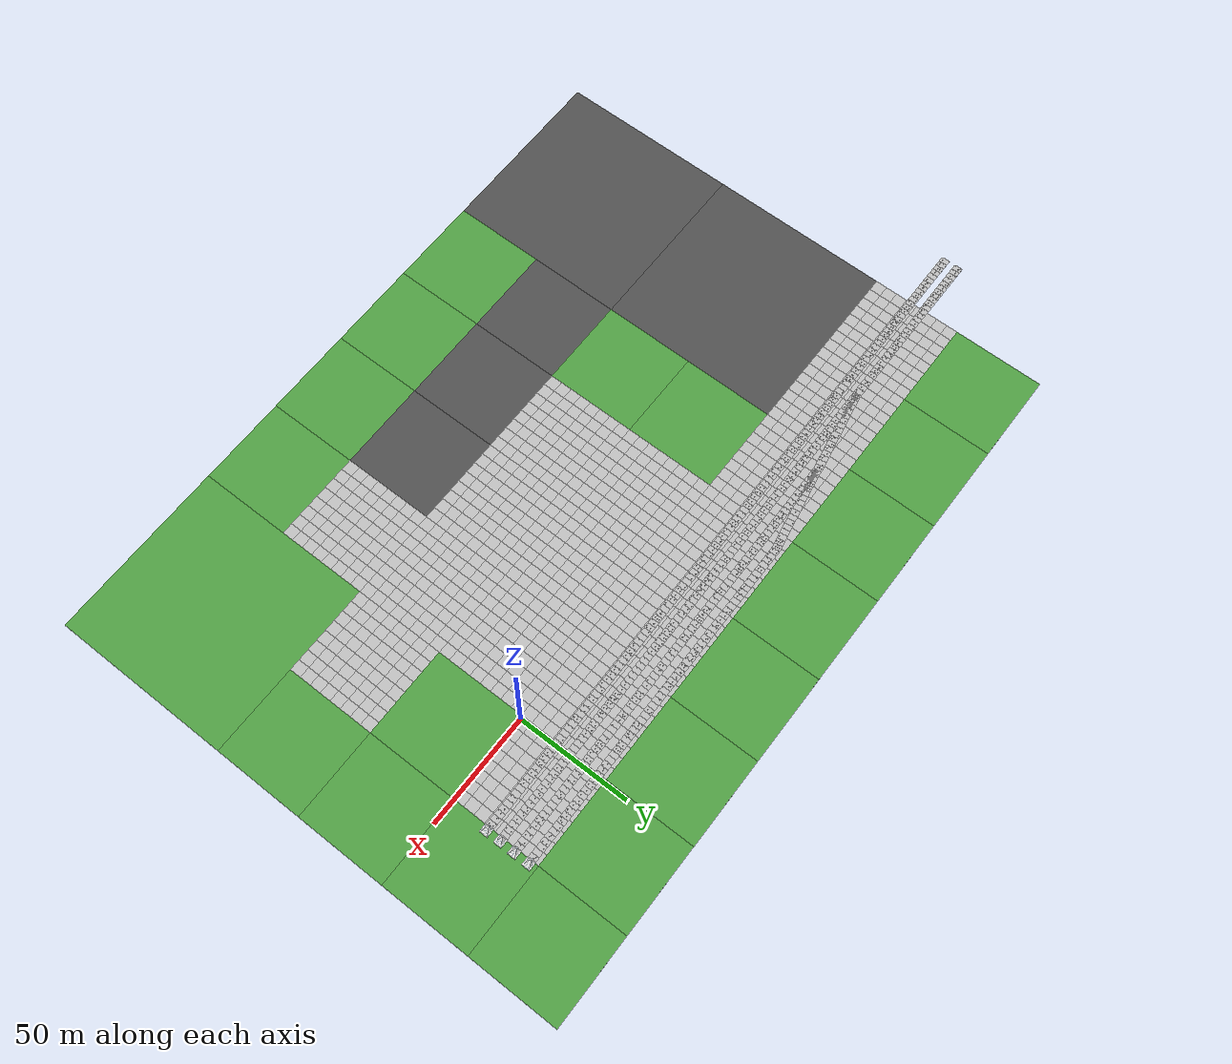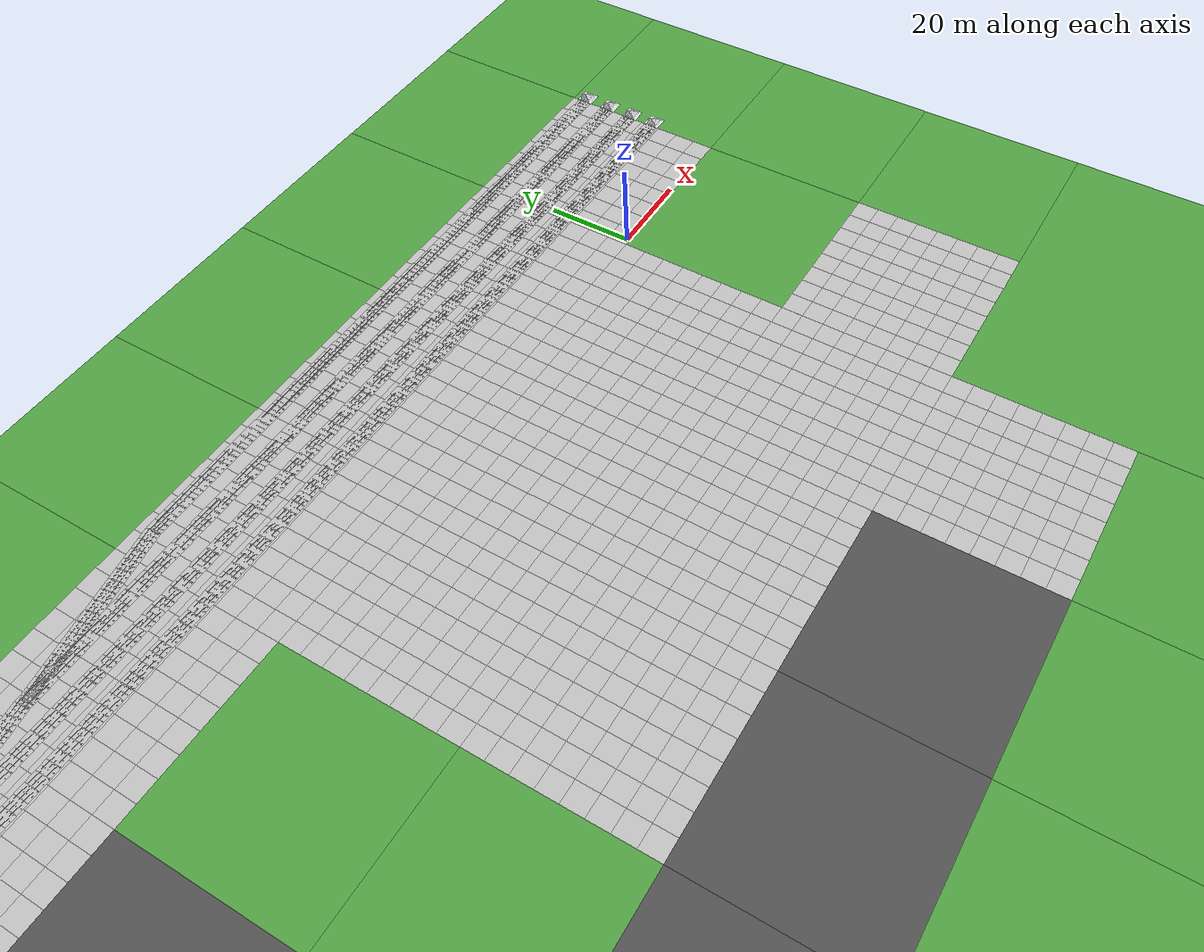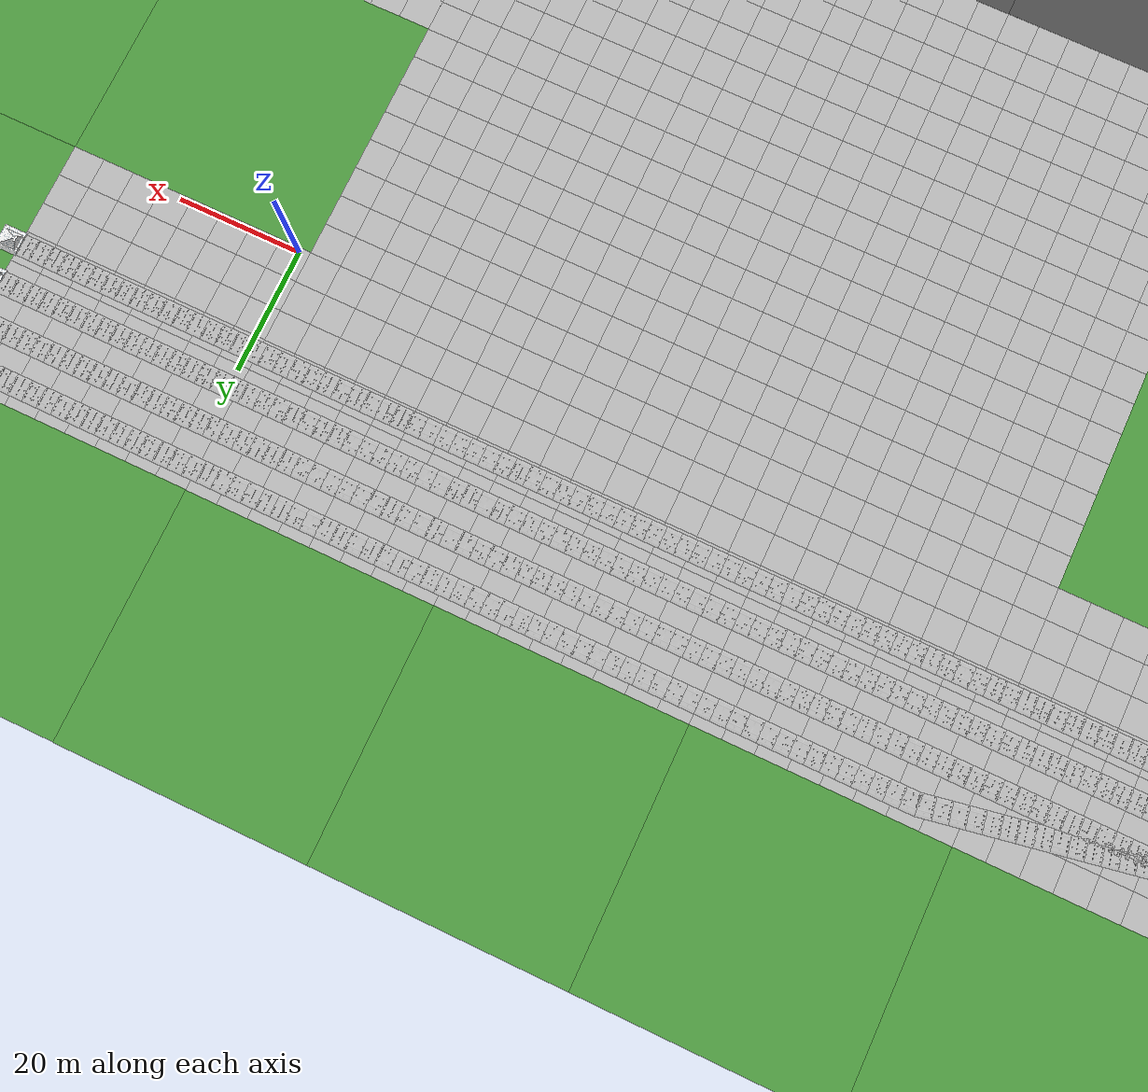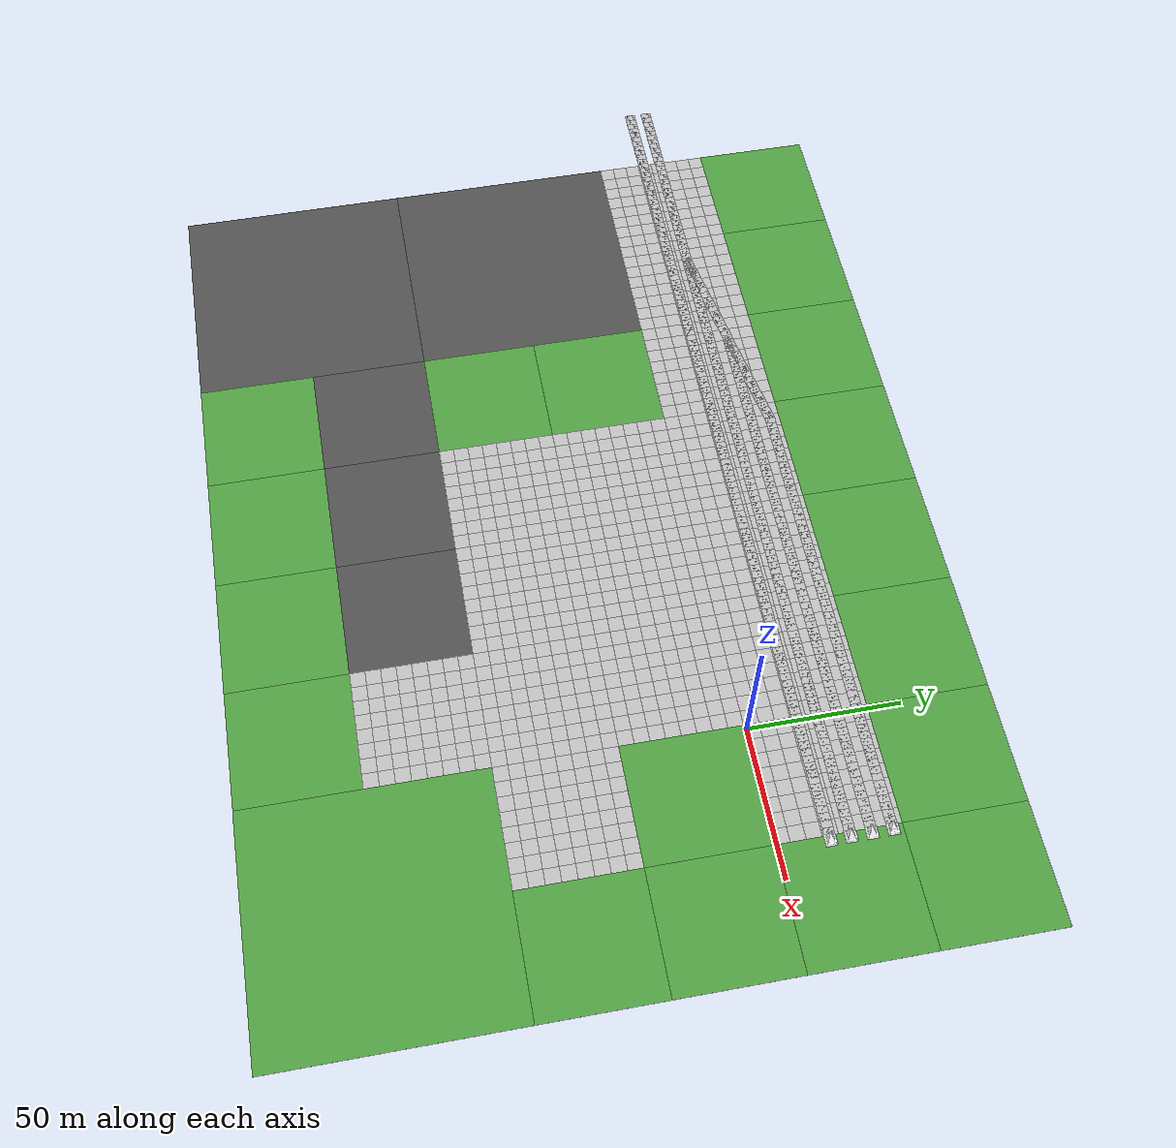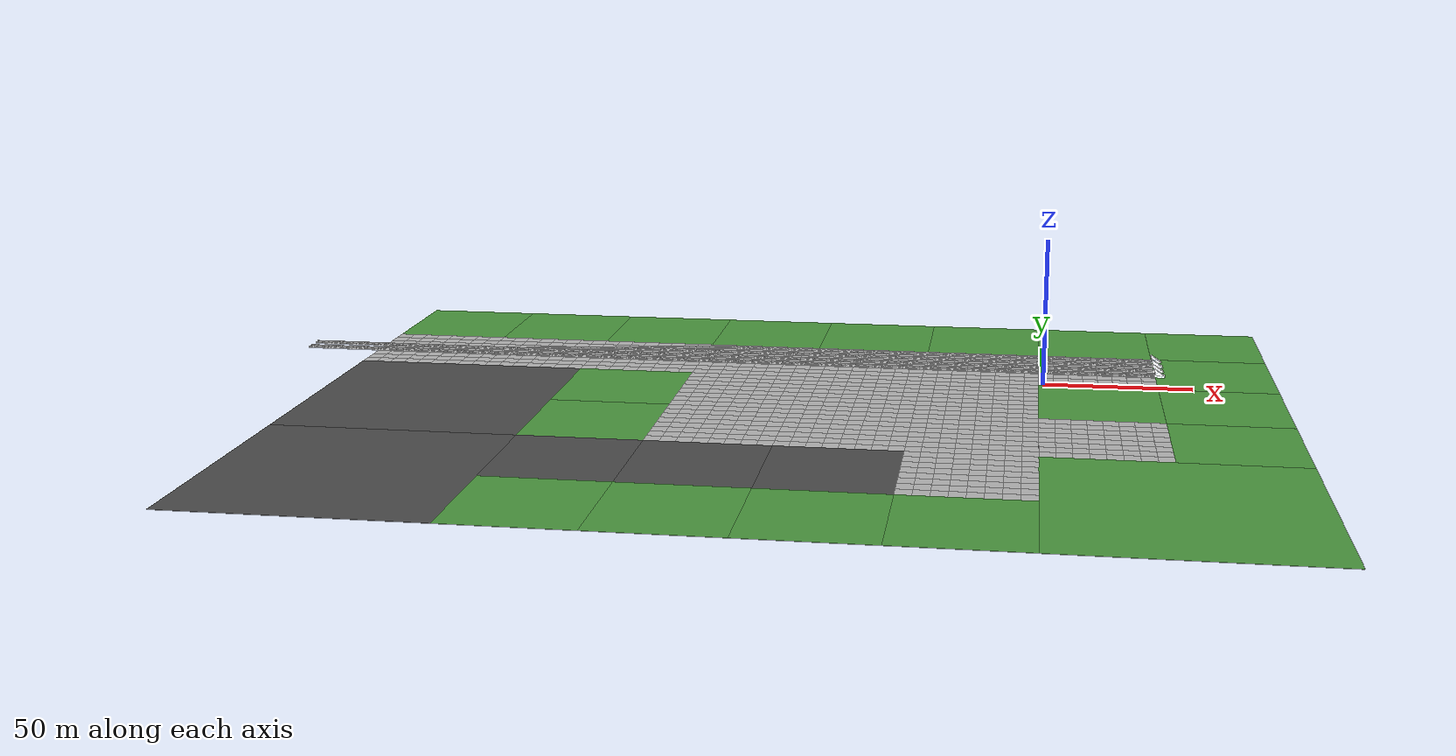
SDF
<sdf version="1.7">
 <world name="default">
  <light name="sun" type="directional">
   <pose>0 0 100 0 -0 0</pose>
   <diffuse>0.8 0.8 0.8 1</diffuse>
   <specular>0.2 0.2 0.2 1</specular>
   <attenuation>
    <range>1000</range>
    <constant>0.9</constant>
    <linear>0.01</linear>
    <quadratic>0.001</quadratic>
   </attenuation>
   <direction>0.1 0.1 -1</direction>
   <spot><inner_angle>0</inner_angle><outer_angle>0</outer_angle><falloff>0</falloff></spot>
  </light>
  <gravity>0 0 -9.8</gravity>
  <magnetic_field>6e-06 2.3e-05 -4.2e-05</magnetic_field>
  <atmosphere type="adiabatic"/>
  <physics type="ode">
   <max_step_size>0.001</max_step_size>
   <real_time_factor>1</real_time_factor>
   <real_time_update_rate>1000</real_time_update_rate>
  </physics>
  <scene><ambient>0.4 0.4 0.4 1</ambient><background>0.7 0.7 0.7 1</background><shadows>1</shadows></scene>
  <spherical_coordinates>
   <surface_model>EARTH_WGS84</surface_model>
   <latitude_deg>0</latitude_deg>
   <longitude_deg>0</longitude_deg>
   <elevation>0</elevation>
   <heading_deg>0</heading_deg>
  </spherical_coordinates>
  <model name="mud_plane_40x40">
   <model name="mud_plane_20x20">
    <model name="mud_plane">
     <static>1</static>
     <link name="link">
      <collision name="collision"><geometry><box><size>10 10 0.1</size></box></geometry></collision>
      <visual name="visual_1">
       <pose>-2.5 2.5 -0.05 0 -0 0</pose>
       <cast_shadows>0</cast_shadows>
       <geometry><box><size>5 5 0.1</size></box></geometry>
       <material>
        <script>
         <uri>model://mud_plane/materials/scripts</uri>
         <uri>model://mud_plane/materials/textures</uri>
         <name>vrc/mud</name>
        </script>
       </material>
      </visual>
      <visual name="visual_2">
       <pose>2.5 2.5 -0.05 0 -0 0</pose>
       <cast_shadows>0</cast_shadows>
       <geometry><box><size>5 5 0.1</size></box></geometry>
       <material>
        <script>
         <uri>model://mud_plane/materials/scripts</uri>
         <uri>model://mud_plane/materials/textures</uri>
         <name>vrc/mud</name>
        </script>
       </material>
      </visual>
      <visual name="visual_3">
       <pose>2.5 -2.5 -0.05 0 -0 0</pose>
       <cast_shadows>0</cast_shadows>
       <geometry><box><size>5 5 0.1</size></box></geometry>
       <material>
        <script>
         <uri>model://mud_plane/materials/scripts</uri>
         <uri>model://mud_plane/materials/textures</uri>
         <name>vrc/mud</name>
        </script>
       </material>
      </visual>
      <visual name="visual_4">
       <pose>-2.5 -2.5 -0.05 0 -0 0</pose>
       <cast_shadows>0</cast_shadows>
       <geometry><box><size>5 5 0.1</size></box></geometry>
       <material>
        <script>
         <uri>model://mud_plane/materials/scripts</uri>
         <uri>model://mud_plane/materials/textures</uri>
         <name>vrc/mud</name>
        </script>
       </material>
      </visual>
     </link>
     <pose>-4.99986 -4.99991 0 0 -0 0</pose>
    </model>
    <model name="mud_plane_0">
     <static>1</static>
     <link name="link">
      <collision name="collision"><geometry><box><size>10 10 0.1</size></box></geometry></collision>
      <visual name="visual_1">
       <pose>-2.5 2.5 -0.05 0 -0 0</pose>
       <cast_shadows>0</cast_shadows>
       <geometry><box><size>5 5 0.1</size></box></geometry>
       <material>
        <script>
         <uri>model://mud_plane/materials/scripts</uri>
         <uri>model://mud_plane/materials/textures</uri>
         <name>vrc/mud</name>
        </script>
       </material>
      </visual>
      <visual name="visual_2">
       <pose>2.5 2.5 -0.05 0 -0 0</pose>
       <cast_shadows>0</cast_shadows>
       <geometry><box><size>5 5 0.1</size></box></geometry>
       <material>
        <script>
         <uri>model://mud_plane/materials/scripts</uri>
         <uri>model://mud_plane/materials/textures</uri>
         <name>vrc/mud</name>
        </script>
       </material>
      </visual>
      <visual name="visual_3">
       <pose>2.5 -2.5 -0.05 0 -0 0</pose>
       <cast_shadows>0</cast_shadows>
       <geometry><box><size>5 5 0.1</size></box></geometry>
       <material>
        <script>
         <uri>model://mud_plane/materials/scripts</uri>
         <uri>model://mud_plane/materials/textures</uri>
         <name>vrc/mud</name>
        </script>
       </material>
      </visual>
      <visual name="visual_4">
       <pose>-2.5 -2.5 -0.05 0 -0 0</pose>
       <cast_shadows>0</cast_shadows>
       <geometry><box><size>5 5 0.1</size></box></geometry>
       <material>
        <script>
         <uri>model://mud_plane/materials/scripts</uri>
         <uri>model://mud_plane/materials/textures</uri>
         <name>vrc/mud</name>
        </script>
       </material>
      </visual>
     </link>
     <pose>-4.99946 4.99954 0 0 -0 0</pose>
    </model>
    <model name="mud_plane_1">
     <static>1</static>
     <link name="link">
      <collision name="collision"><geometry><box><size>10 10 0.1</size></box></geometry></collision>
      <visual name="visual_1">
       <pose>-2.5 2.5 -0.05 0 -0 0</pose>
       <cast_shadows>0</cast_shadows>
       <geometry><box><size>5 5 0.1</size></box></geometry>
       <material>
        <script>
         <uri>model://mud_plane/materials/scripts</uri>
         <uri>model://mud_plane/materials/textures</uri>
         <name>vrc/mud</name>
        </script>
       </material>
      </visual>
      <visual name="visual_2">
       <pose>2.5 2.5 -0.05 0 -0 0</pose>
       <cast_shadows>0</cast_shadows>
       <geometry><box><size>5 5 0.1</size></box></geometry>
       <material>
        <script>
         <uri>model://mud_plane/materials/scripts</uri>
         <uri>model://mud_plane/materials/textures</uri>
         <name>vrc/mud</name>
        </script>
       </material>
      </visual>
      <visual name="visual_3">
       <pose>2.5 -2.5 -0.05 0 -0 0</pose>
       <cast_shadows>0</cast_shadows>
       <geometry><box><size>5 5 0.1</size></box></geometry>
       <material>
        <script>
         <uri>model://mud_plane/materials/scripts</uri>
         <uri>model://mud_plane/materials/textures</uri>
         <name>vrc/mud</name>
        </script>
       </material>
      </visual>
      <visual name="visual_4">
       <pose>-2.5 -2.5 -0.05 0 -0 0</pose>
       <cast_shadows>0</cast_shadows>
       <geometry><box><size>5 5 0.1</size></box></geometry>
       <material>
        <script>
         <uri>model://mud_plane/materials/scripts</uri>
         <uri>model://mud_plane/materials/textures</uri>
         <name>vrc/mud</name>
        </script>
       </material>
      </visual>
     </link>
     <pose>4.99964 -4.99949 0 0 -0 0</pose>
    </model>
    <model name="mud_plane_2">
     <static>1</static>
     <link name="link">
      <collision name="collision"><geometry><box><size>10 10 0.1</size></box></geometry></collision>
      <visual name="visual_1">
       <pose>-2.5 2.5 -0.05 0 -0 0</pose>
       <cast_shadows>0</cast_shadows>
       <geometry><box><size>5 5 0.1</size></box></geometry>
       <material>
        <script>
         <uri>model://mud_plane/materials/scripts</uri>
         <uri>model://mud_plane/materials/textures</uri>
         <name>vrc/mud</name>
        </script>
       </material>
      </visual>
      <visual name="visual_2">
       <pose>2.5 2.5 -0.05 0 -0 0</pose>
       <cast_shadows>0</cast_shadows>
       <geometry><box><size>5 5 0.1</size></box></geometry>
       <material>
        <script>
         <uri>model://mud_plane/materials/scripts</uri>
         <uri>model://mud_plane/materials/textures</uri>
         <name>vrc/mud</name>
        </script>
       </material>
      </visual>
      <visual name="visual_3">
       <pose>2.5 -2.5 -0.05 0 -0 0</pose>
       <cast_shadows>0</cast_shadows>
       <geometry><box><size>5 5 0.1</size></box></geometry>
       <material>
        <script>
         <uri>model://mud_plane/materials/scripts</uri>
         <uri>model://mud_plane/materials/textures</uri>
         <name>vrc/mud</name>
        </script>
       </material>
      </visual>
      <visual name="visual_4">
       <pose>-2.5 -2.5 -0.05 0 -0 0</pose>
       <cast_shadows>0</cast_shadows>
       <geometry><box><size>5 5 0.1</size></box></geometry>
       <material>
        <script>
         <uri>model://mud_plane/materials/scripts</uri>
         <uri>model://mud_plane/materials/textures</uri>
         <name>vrc/mud</name>
        </script>
       </material>
      </visual>
     </link>
     <pose>4.99967 4.99986 0 0 -0 0</pose>
    </model>
    <static>0</static>
    <pose>-9.99895 9.99843 0 0 -0 0</pose>
   </model>
   <model name="mud_plane_20x20_0">
    <model name="mud_plane">
     <static>1</static>
     <link name="link">
      <collision name="collision"><geometry><box><size>10 10 0.1</size></box></geometry></collision>
      <visual name="visual_1">
       <pose>-2.5 2.5 -0.05 0 -0 0</pose>
       <cast_shadows>0</cast_shadows>
       <geometry><box><size>5 5 0.1</size></box></geometry>
       <material>
        <script>
         <uri>model://mud_plane/materials/scripts</uri>
         <uri>model://mud_plane/materials/textures</uri>
         <name>vrc/mud</name>
        </script>
       </material>
      </visual>
      <visual name="visual_2">
       <pose>2.5 2.5 -0.05 0 -0 0</pose>
       <cast_shadows>0</cast_shadows>
       <geometry><box><size>5 5 0.1</size></box></geometry>
       <material>
        <script>
         <uri>model://mud_plane/materials/scripts</uri>
         <uri>model://mud_plane/materials/textures</uri>
         <name>vrc/mud</name>
        </script>
       </material>
      </visual>
      <visual name="visual_3">
       <pose>2.5 -2.5 -0.05 0 -0 0</pose>
       <cast_shadows>0</cast_shadows>
       <geometry><box><size>5 5 0.1</size></box></geometry>
       <material>
        <script>
         <uri>model://mud_plane/materials/scripts</uri>
         <uri>model://mud_plane/materials/textures</uri>
         <name>vrc/mud</name>
        </script>
       </material>
      </visual>
      <visual name="visual_4">
       <pose>-2.5 -2.5 -0.05 0 -0 0</pose>
       <cast_shadows>0</cast_shadows>
       <geometry><box><size>5 5 0.1</size></box></geometry>
       <material>
        <script>
         <uri>model://mud_plane/materials/scripts</uri>
         <uri>model://mud_plane/materials/textures</uri>
         <name>vrc/mud</name>
        </script>
       </material>
      </visual>
     </link>
     <pose>-4.99986 -4.99991 0 0 -0 0</pose>
    </model>
    <model name="mud_plane_0">
     <static>1</static>
     <link name="link">
      <collision name="collision"><geometry><box><size>10 10 0.1</size></box></geometry></collision>
      <visual name="visual_1">
       <pose>-2.5 2.5 -0.05 0 -0 0</pose>
       <cast_shadows>0</cast_shadows>
       <geometry><box><size>5 5 0.1</size></box></geometry>
       <material>
        <script>
         <uri>model://mud_plane/materials/scripts</uri>
         <uri>model://mud_plane/materials/textures</uri>
         <name>vrc/mud</name>
        </script>
       </material>
      </visual>
      <visual name="visual_2">
       <pose>2.5 2.5 -0.05 0 -0 0</pose>
       <cast_shadows>0</cast_shadows>
       <geometry><box><size>5 5 0.1</size></box></geometry>
       <material>
        <script>
         <uri>model://mud_plane/materials/scripts</uri>
         <uri>model://mud_plane/materials/textures</uri>
         <name>vrc/mud</name>
        </script>
       </material>
      </visual>
      <visual name="visual_3">
       <pose>2.5 -2.5 -0.05 0 -0 0</pose>
       <cast_shadows>0</cast_shadows>
       <geometry><box><size>5 5 0.1</size></box></geometry>
       <material>
        <script>
         <uri>model://mud_plane/materials/scripts</uri>
         <uri>model://mud_plane/materials/textures</uri>
         <name>vrc/mud</name>
        </script>
       </material>
      </visual>
      <visual name="visual_4">
       <pose>-2.5 -2.5 -0.05 0 -0 0</pose>
       <cast_shadows>0</cast_shadows>
       <geometry><box><size>5 5 0.1</size></box></geometry>
       <material>
        <script>
         <uri>model://mud_plane/materials/scripts</uri>
         <uri>model://mud_plane/materials/textures</uri>
         <name>vrc/mud</name>
        </script>
       </material>
      </visual>
     </link>
     <pose>-4.99946 4.99954 0 0 -0 0</pose>
    </model>
    <model name="mud_plane_1">
     <static>1</static>
     <link name="link">
      <collision name="collision"><geometry><box><size>10 10 0.1</size></box></geometry></collision>
      <visual name="visual_1">
       <pose>-2.5 2.5 -0.05 0 -0 0</pose>
       <cast_shadows>0</cast_shadows>
       <geometry><box><size>5 5 0.1</size></box></geometry>
       <material>
        <script>
         <uri>model://mud_plane/materials/scripts</uri>
         <uri>model://mud_plane/materials/textures</uri>
         <name>vrc/mud</name>
        </script>
       </material>
      </visual>
      <visual name="visual_2">
       <pose>2.5 2.5 -0.05 0 -0 0</pose>
       <cast_shadows>0</cast_shadows>
       <geometry><box><size>5 5 0.1</size></box></geometry>
       <material>
        <script>
         <uri>model://mud_plane/materials/scripts</uri>
         <uri>model://mud_plane/materials/textures</uri>
         <name>vrc/mud</name>
        </script>
       </material>
      </visual>
      <visual name="visual_3">
       <pose>2.5 -2.5 -0.05 0 -0 0</pose>
       <cast_shadows>0</cast_shadows>
       <geometry><box><size>5 5 0.1</size></box></geometry>
       <material>
        <script>
         <uri>model://mud_plane/materials/scripts</uri>
         <uri>model://mud_plane/materials/textures</uri>
         <name>vrc/mud</name>
        </script>
       </material>
      </visual>
      <visual name="visual_4">
       <pose>-2.5 -2.5 -0.05 0 -0 0</pose>
       <cast_shadows>0</cast_shadows>
       <geometry><box><size>5 5 0.1</size></box></geometry>
       <material>
        <script>
         <uri>model://mud_plane/materials/scripts</uri>
         <uri>model://mud_plane/materials/textures</uri>
         <name>vrc/mud</name>
        </script>
       </material>
      </visual>
     </link>
     <pose>4.99964 -4.99949 0 0 -0 0</pose>
    </model>
    <model name="mud_plane_2">
     <static>1</static>
     <link name="link">
      <collision name="collision"><geometry><box><size>10 10 0.1</size></box></geometry></collision>
      <visual name="visual_1">
       <pose>-2.5 2.5 -0.05 0 -0 0</pose>
       <cast_shadows>0</cast_shadows>
       <geometry><box><size>5 5 0.1</size></box></geometry>
       <material>
        <script>
         <uri>model://mud_plane/materials/scripts</uri>
         <uri>model://mud_plane/materials/textures</uri>
         <name>vrc/mud</name>
        </script>
       </material>
      </visual>
      <visual name="visual_2">
       <pose>2.5 2.5 -0.05 0 -0 0</pose>
       <cast_shadows>0</cast_shadows>
       <geometry><box><size>5 5 0.1</size></box></geometry>
       <material>
        <script>
         <uri>model://mud_plane/materials/scripts</uri>
         <uri>model://mud_plane/materials/textures</uri>
         <name>vrc/mud</name>
        </script>
       </material>
      </visual>
      <visual name="visual_3">
       <pose>2.5 -2.5 -0.05 0 -0 0</pose>
       <cast_shadows>0</cast_shadows>
       <geometry><box><size>5 5 0.1</size></box></geometry>
       <material>
        <script>
         <uri>model://mud_plane/materials/scripts</uri>
         <uri>model://mud_plane/materials/textures</uri>
         <name>vrc/mud</name>
        </script>
       </material>
      </visual>
      <visual name="visual_4">
       <pose>-2.5 -2.5 -0.05 0 -0 0</pose>
       <cast_shadows>0</cast_shadows>
       <geometry><box><size>5 5 0.1</size></box></geometry>
       <material>
        <script>
         <uri>model://mud_plane/materials/scripts</uri>
         <uri>model://mud_plane/materials/textures</uri>
         <name>vrc/mud</name>
        </script>
       </material>
      </visual>
     </link>
     <pose>4.99967 4.99986 0 0 -0 0</pose>
    </model>
    <static>0</static>
    <pose>9.99933 9.9997 0 0 -0 0</pose>
   </model>
   <model name="mud_plane_20x20_1">
    <model name="mud_plane">
     <static>1</static>
     <link name="link">
      <collision name="collision"><geometry><box><size>10 10 0.1</size></box></geometry></collision>
      <visual name="visual_1">
       <pose>-2.5 2.5 -0.05 0 -0 0</pose>
       <cast_shadows>0</cast_shadows>
       <geometry><box><size>5 5 0.1</size></box></geometry>
       <material>
        <script>
         <uri>model://mud_plane/materials/scripts</uri>
         <uri>model://mud_plane/materials/textures</uri>
         <name>vrc/mud</name>
        </script>
       </material>
      </visual>
      <visual name="visual_2">
       <pose>2.5 2.5 -0.05 0 -0 0</pose>
       <cast_shadows>0</cast_shadows>
       <geometry><box><size>5 5 0.1</size></box></geometry>
       <material>
        <script>
         <uri>model://mud_plane/materials/scripts</uri>
         <uri>model://mud_plane/materials/textures</uri>
         <name>vrc/mud</name>
        </script>
       </material>
      </visual>
      <visual name="visual_3">
       <pose>2.5 -2.5 -0.05 0 -0 0</pose>
       <cast_shadows>0</cast_shadows>
       <geometry><box><size>5 5 0.1</size></box></geometry>
       <material>
        <script>
         <uri>model://mud_plane/materials/scripts</uri>
         <uri>model://mud_plane/materials/textures</uri>
         <name>vrc/mud</name>
        </script>
       </material>
      </visual>
      <visual name="visual_4">
       <pose>-2.5 -2.5 -0.05 0 -0 0</pose>
       <cast_shadows>0</cast_shadows>
       <geometry><box><size>5 5 0.1</size></box></geometry>
       <material>
        <script>
         <uri>model://mud_plane/materials/scripts</uri>
         <uri>model://mud_plane/materials/textures</uri>
         <name>vrc/mud</name>
        </script>
       </material>
      </visual>
     </link>
     <pose>-4.99986 -4.99991 0 0 -0 0</pose>
    </model>
    <model name="mud_plane_0">
     <static>1</static>
     <link name="link">
      <collision name="collision"><geometry><box><size>10 10 0.1</size></box></geometry></collision>
      <visual name="visual_1">
       <pose>-2.5 2.5 -0.05 0 -0 0</pose>
       <cast_shadows>0</cast_shadows>
       <geometry><box><size>5 5 0.1</size></box></geometry>
       <material>
        <script>
         <uri>model://mud_plane/materials/scripts</uri>
         <uri>model://mud_plane/materials/textures</uri>
         <name>vrc/mud</name>
        </script>
       </material>
      </visual>
      <visual name="visual_2">
       <pose>2.5 2.5 -0.05 0 -0 0</pose>
       <cast_shadows>0</cast_shadows>
       <geometry><box><size>5 5 0.1</size></box></geometry>
       <material>
        <script>
         <uri>model://mud_plane/materials/scripts</uri>
         <uri>model://mud_plane/materials/textures</uri>
         <name>vrc/mud</name>
        </script>
       </material>
      </visual>
      <visual name="visual_3">
       <pose>2.5 -2.5 -0.05 0 -0 0</pose>
       <cast_shadows>0</cast_shadows>
       <geometry><box><size>5 5 0.1</size></box></geometry>
       <material>
        <script>
         <uri>model://mud_plane/materials/scripts</uri>
         <uri>model://mud_plane/materials/textures</uri>
         <name>vrc/mud</name>
        </script>
       </material>
      </visual>
      <visual name="visual_4">
       <pose>-2.5 -2.5 -0.05 0 -0 0</pose>
       <cast_shadows>0</cast_shadows>
       <geometry><box><size>5 5 0.1</size></box></geometry>
       <material>
        <script>
         <uri>model://mud_plane/materials/scripts</uri>
         <uri>model://mud_plane/materials/textures</uri>
         <name>vrc/mud</name>
        </script>
       </material>
      </visual>
     </link>
     <pose>-4.99946 4.99954 0 0 -0 0</pose>
    </model>
    <model name="mud_plane_1">
     <static>1</static>
     <link name="link">
      <collision name="collision"><geometry><box><size>10 10 0.1</size></box></geometry></collision>
      <visual name="visual_1">
       <pose>-2.5 2.5 -0.05 0 -0 0</pose>
       <cast_shadows>0</cast_shadows>
       <geometry><box><size>5 5 0.1</size></box></geometry>
       <material>
        <script>
         <uri>model://mud_plane/materials/scripts</uri>
         <uri>model://mud_plane/materials/textures</uri>
         <name>vrc/mud</name>
        </script>
       </material>
      </visual>
      <visual name="visual_2">
       <pose>2.5 2.5 -0.05 0 -0 0</pose>
       <cast_shadows>0</cast_shadows>
       <geometry><box><size>5 5 0.1</size></box></geometry>
       <material>
        <script>
         <uri>model://mud_plane/materials/scripts</uri>
         <uri>model://mud_plane/materials/textures</uri>
         <name>vrc/mud</name>
        </script>
       </material>
      </visual>
      <visual name="visual_3">
       <pose>2.5 -2.5 -0.05 0 -0 0</pose>
       <cast_shadows>0</cast_shadows>
       <geometry><box><size>5 5 0.1</size></box></geometry>
       <material>
        <script>
         <uri>model://mud_plane/materials/scripts</uri>
         <uri>model://mud_plane/materials/textures</uri>
         <name>vrc/mud</name>
        </script>
       </material>
      </visual>
      <visual name="visual_4">
       <pose>-2.5 -2.5 -0.05 0 -0 0</pose>
       <cast_shadows>0</cast_shadows>
       <geometry><box><size>5 5 0.1</size></box></geometry>
       <material>
        <script>
         <uri>model://mud_plane/materials/scripts</uri>
         <uri>model://mud_plane/materials/textures</uri>
         <name>vrc/mud</name>
        </script>
       </material>
      </visual>
     </link>
     <pose>4.99964 -4.99949 0 0 -0 0</pose>
    </model>
    <model name="mud_plane_2">
     <static>1</static>
     <link name="link">
      <collision name="collision"><geometry><box><size>10 10 0.1</size></box></geometry></collision>
      <visual name="visual_1">
       <pose>-2.5 2.5 -0.05 0 -0 0</pose>
       <cast_shadows>0</cast_shadows>
       <geometry><box><size>5 5 0.1</size></box></geometry>
       <material>
        <script>
         <uri>model://mud_plane/materials/scripts</uri>
         <uri>model://mud_plane/materials/textures</uri>
         <name>vrc/mud</name>
        </script>
       </material>
      </visual>
      <visual name="visual_2">
       <pose>2.5 2.5 -0.05 0 -0 0</pose>
       <cast_shadows>0</cast_shadows>
       <geometry><box><size>5 5 0.1</size></box></geometry>
       <material>
        <script>
         <uri>model://mud_plane/materials/scripts</uri>
         <uri>model://mud_plane/materials/textures</uri>
         <name>vrc/mud</name>
        </script>
       </material>
      </visual>
      <visual name="visual_3">
       <pose>2.5 -2.5 -0.05 0 -0 0</pose>
       <cast_shadows>0</cast_shadows>
       <geometry><box><size>5 5 0.1</size></box></geometry>
       <material>
        <script>
         <uri>model://mud_plane/materials/scripts</uri>
         <uri>model://mud_plane/materials/textures</uri>
         <name>vrc/mud</name>
        </script>
       </material>
      </visual>
      <visual name="visual_4">
       <pose>-2.5 -2.5 -0.05 0 -0 0</pose>
       <cast_shadows>0</cast_shadows>
       <geometry><box><size>5 5 0.1</size></box></geometry>
       <material>
        <script>
         <uri>model://mud_plane/materials/scripts</uri>
         <uri>model://mud_plane/materials/textures</uri>
         <name>vrc/mud</name>
        </script>
       </material>
      </visual>
     </link>
     <pose>4.99967 4.99986 0 0 -0 0</pose>
    </model>
    <static>0</static>
    <pose>9.9993 -9.99877 0 0 -0 0</pose>
   </model>
   <model name="mud_plane_20x20_2">
    <model name="mud_plane">
     <static>1</static>
     <link name="link">
      <collision name="collision"><geometry><box><size>10 10 0.1</size></box></geometry></collision>
      <visual name="visual_1">
       <pose>-2.5 2.5 -0.05 0 -0 0</pose>
       <cast_shadows>0</cast_shadows>
       <geometry><box><size>5 5 0.1</size></box></geometry>
       <material>
        <script>
         <uri>model://mud_plane/materials/scripts</uri>
         <uri>model://mud_plane/materials/textures</uri>
         <name>vrc/mud</name>
        </script>
       </material>
      </visual>
      <visual name="visual_2">
       <pose>2.5 2.5 -0.05 0 -0 0</pose>
       <cast_shadows>0</cast_shadows>
       <geometry><box><size>5 5 0.1</size></box></geometry>
       <material>
        <script>
         <uri>model://mud_plane/materials/scripts</uri>
         <uri>model://mud_plane/materials/textures</uri>
         <name>vrc/mud</name>
        </script>
       </material>
      </visual>
      <visual name="visual_3">
       <pose>2.5 -2.5 -0.05 0 -0 0</pose>
       <cast_shadows>0</cast_shadows>
       <geometry><box><size>5 5 0.1</size></box></geometry>
       <material>
        <script>
         <uri>model://mud_plane/materials/scripts</uri>
         <uri>model://mud_plane/materials/textures</uri>
         <name>vrc/mud</name>
        </script>
       </material>
      </visual>
      <visual name="visual_4">
       <pose>-2.5 -2.5 -0.05 0 -0 0</pose>
       <cast_shadows>0</cast_shadows>
       <geometry><box><size>5 5 0.1</size></box></geometry>
       <material>
        <script>
         <uri>model://mud_plane/materials/scripts</uri>
         <uri>model://mud_plane/materials/textures</uri>
         <name>vrc/mud</name>
        </script>
       </material>
      </visual>
     </link>
     <pose>-4.99986 -4.99991 0 0 -0 0</pose>
    </model>
    <model name="mud_plane_0">
     <static>1</static>
     <link name="link">
      <collision name="collision"><geometry><box><size>10 10 0.1</size></box></geometry></collision>
      <visual name="visual_1">
       <pose>-2.5 2.5 -0.05 0 -0 0</pose>
       <cast_shadows>0</cast_shadows>
       <geometry><box><size>5 5 0.1</size></box></geometry>
       <material>
        <script>
         <uri>model://mud_plane/materials/scripts</uri>
         <uri>model://mud_plane/materials/textures</uri>
         <name>vrc/mud</name>
        </script>
       </material>
      </visual>
      <visual name="visual_2">
       <pose>2.5 2.5 -0.05 0 -0 0</pose>
       <cast_shadows>0</cast_shadows>
       <geometry><box><size>5 5 0.1</size></box></geometry>
       <material>
        <script>
         <uri>model://mud_plane/materials/scripts</uri>
         <uri>model://mud_plane/materials/textures</uri>
         <name>vrc/mud</name>
        </script>
       </material>
      </visual>
      <visual name="visual_3">
       <pose>2.5 -2.5 -0.05 0 -0 0</pose>
       <cast_shadows>0</cast_shadows>
       <geometry><box><size>5 5 0.1</size></box></geometry>
       <material>
        <script>
         <uri>model://mud_plane/materials/scripts</uri>
         <uri>model://mud_plane/materials/textures</uri>
         <name>vrc/mud</name>
        </script>
       </material>
      </visual>
      <visual name="visual_4">
       <pose>-2.5 -2.5 -0.05 0 -0 0</pose>
       <cast_shadows>0</cast_shadows>
       <geometry><box><size>5 5 0.1</size></box></geometry>
       <material>
        <script>
         <uri>model://mud_plane/materials/scripts</uri>
         <uri>model://mud_plane/materials/textures</uri>
         <name>vrc/mud</name>
        </script>
       </material>
      </visual>
     </link>
     <pose>-4.99946 4.99954 0 0 -0 0</pose>
    </model>
    <model name="mud_plane_1">
     <static>1</static>
     <link name="link">
      <collision name="collision"><geometry><box><size>10 10 0.1</size></box></geometry></collision>
      <visual name="visual_1">
       <pose>-2.5 2.5 -0.05 0 -0 0</pose>
       <cast_shadows>0</cast_shadows>
       <geometry><box><size>5 5 0.1</size></box></geometry>
       <material>
        <script>
         <uri>model://mud_plane/materials/scripts</uri>
         <uri>model://mud_plane/materials/textures</uri>
         <name>vrc/mud</name>
        </script>
       </material>
      </visual>
      <visual name="visual_2">
       <pose>2.5 2.5 -0.05 0 -0 0</pose>
       <cast_shadows>0</cast_shadows>
       <geometry><box><size>5 5 0.1</size></box></geometry>
       <material>
        <script>
         <uri>model://mud_plane/materials/scripts</uri>
         <uri>model://mud_plane/materials/textures</uri>
         <name>vrc/mud</name>
        </script>
       </material>
      </visual>
      <visual name="visual_3">
       <pose>2.5 -2.5 -0.05 0 -0 0</pose>
       <cast_shadows>0</cast_shadows>
       <geometry><box><size>5 5 0.1</size></box></geometry>
       <material>
        <script>
         <uri>model://mud_plane/materials/scripts</uri>
         <uri>model://mud_plane/materials/textures</uri>
         <name>vrc/mud</name>
        </script>
       </material>
      </visual>
      <visual name="visual_4">
       <pose>-2.5 -2.5 -0.05 0 -0 0</pose>
       <cast_shadows>0</cast_shadows>
       <geometry><box><size>5 5 0.1</size></box></geometry>
       <material>
        <script>
         <uri>model://mud_plane/materials/scripts</uri>
         <uri>model://mud_plane/materials/textures</uri>
         <name>vrc/mud</name>
        </script>
       </material>
      </visual>
     </link>
     <pose>4.99964 -4.99949 0 0 -0 0</pose>
    </model>
    <model name="mud_plane_2">
     <static>1</static>
     <link name="link">
      <collision name="collision"><geometry><box><size>10 10 0.1</size></box></geometry></collision>
      <visual name="visual_1">
       <pose>-2.5 2.5 -0.05 0 -0 0</pose>
       <cast_shadows>0</cast_shadows>
       <geometry><box><size>5 5 0.1</size></box></geometry>
       <material>
        <script>
         <uri>model://mud_plane/materials/scripts</uri>
         <uri>model://mud_plane/materials/textures</uri>
         <name>vrc/mud</name>
        </script>
       </material>
      </visual>
      <visual name="visual_2">
       <pose>2.5 2.5 -0.05 0 -0 0</pose>
       <cast_shadows>0</cast_shadows>
       <geometry><box><size>5 5 0.1</size></box></geometry>
       <material>
        <script>
         <uri>model://mud_plane/materials/scripts</uri>
         <uri>model://mud_plane/materials/textures</uri>
         <name>vrc/mud</name>
        </script>
       </material>
      </visual>
      <visual name="visual_3">
       <pose>2.5 -2.5 -0.05 0 -0 0</pose>
       <cast_shadows>0</cast_shadows>
       <geometry><box><size>5 5 0.1</size></box></geometry>
       <material>
        <script>
         <uri>model://mud_plane/materials/scripts</uri>
         <uri>model://mud_plane/materials/textures</uri>
         <name>vrc/mud</name>
        </script>
       </material>
      </visual>
      <visual name="visual_4">
       <pose>-2.5 -2.5 -0.05 0 -0 0</pose>
       <cast_shadows>0</cast_shadows>
       <geometry><box><size>5 5 0.1</size></box></geometry>
       <material>
        <script>
         <uri>model://mud_plane/materials/scripts</uri>
         <uri>model://mud_plane/materials/textures</uri>
         <name>vrc/mud</name>
        </script>
       </material>
      </visual>
     </link>
     <pose>4.99967 4.99986 0 0 -0 0</pose>
    </model>
    <static>0</static>
    <pose>-9.99969 -9.99935 0 0 -0 0</pose>
   </model>
   <static>0</static>
   <pose>18.5425 19.1901 0 0 -0 0</pose>
  </model>
  <model name="mud_plane_40x40_0">
   <model name="mud_plane_20x20">
    <model name="mud_plane">
     <static>1</static>
     <link name="link">
      <collision name="collision"><geometry><box><size>10 10 0.1</size></box></geometry></collision>
      <visual name="visual_1">
       <pose>-2.5 2.5 -0.05 0 -0 0</pose>
       <cast_shadows>0</cast_shadows>
       <geometry><box><size>5 5 0.1</size></box></geometry>
       <material>
        <script>
         <uri>model://mud_plane/materials/scripts</uri>
         <uri>model://mud_plane/materials/textures</uri>
         <name>vrc/mud</name>
        </script>
       </material>
      </visual>
      <visual name="visual_2">
       <pose>2.5 2.5 -0.05 0 -0 0</pose>
       <cast_shadows>0</cast_shadows>
       <geometry><box><size>5 5 0.1</size></box></geometry>
       <material>
        <script>
         <uri>model://mud_plane/materials/scripts</uri>
         <uri>model://mud_plane/materials/textures</uri>
         <name>vrc/mud</name>
        </script>
       </material>
      </visual>
      <visual name="visual_3">
       <pose>2.5 -2.5 -0.05 0 -0 0</pose>
       <cast_shadows>0</cast_shadows>
       <geometry><box><size>5 5 0.1</size></box></geometry>
       <material>
        <script>
         <uri>model://mud_plane/materials/scripts</uri>
         <uri>model://mud_plane/materials/textures</uri>
         <name>vrc/mud</name>
        </script>
       </material>
      </visual>
      <visual name="visual_4">
       <pose>-2.5 -2.5 -0.05 0 -0 0</pose>
       <cast_shadows>0</cast_shadows>
       <geometry><box><size>5 5 0.1</size></box></geometry>
       <material>
        <script>
         <uri>model://mud_plane/materials/scripts</uri>
         <uri>model://mud_plane/materials/textures</uri>
         <name>vrc/mud</name>
        </script>
       </material>
      </visual>
     </link>
     <pose>-4.99986 -4.99991 0 0 -0 0</pose>
    </model>
    <model name="mud_plane_0">
     <static>1</static>
     <link name="link">
      <collision name="collision"><geometry><box><size>10 10 0.1</size></box></geometry></collision>
      <visual name="visual_1">
       <pose>-2.5 2.5 -0.05 0 -0 0</pose>
       <cast_shadows>0</cast_shadows>
       <geometry><box><size>5 5 0.1</size></box></geometry>
       <material>
        <script>
         <uri>model://mud_plane/materials/scripts</uri>
         <uri>model://mud_plane/materials/textures</uri>
         <name>vrc/mud</name>
        </script>
       </material>
      </visual>
      <visual name="visual_2">
       <pose>2.5 2.5 -0.05 0 -0 0</pose>
       <cast_shadows>0</cast_shadows>
       <geometry><box><size>5 5 0.1</size></box></geometry>
       <material>
        <script>
         <uri>model://mud_plane/materials/scripts</uri>
         <uri>model://mud_plane/materials/textures</uri>
         <name>vrc/mud</name>
        </script>
       </material>
      </visual>
      <visual name="visual_3">
       <pose>2.5 -2.5 -0.05 0 -0 0</pose>
       <cast_shadows>0</cast_shadows>
       <geometry><box><size>5 5 0.1</size></box></geometry>
       <material>
        <script>
         <uri>model://mud_plane/materials/scripts</uri>
         <uri>model://mud_plane/materials/textures</uri>
         <name>vrc/mud</name>
        </script>
       </material>
      </visual>
      <visual name="visual_4">
       <pose>-2.5 -2.5 -0.05 0 -0 0</pose>
       <cast_shadows>0</cast_shadows>
       <geometry><box><size>5 5 0.1</size></box></geometry>
       <material>
        <script>
         <uri>model://mud_plane/materials/scripts</uri>
         <uri>model://mud_plane/materials/textures</uri>
         <name>vrc/mud</name>
        </script>
       </material>
      </visual>
     </link>
     <pose>-4.99946 4.99954 0 0 -0 0</pose>
    </model>
    <model name="mud_plane_1">
     <static>1</static>
     <link name="link">
      <collision name="collision"><geometry><box><size>10 10 0.1</size></box></geometry></collision>
      <visual name="visual_1">
       <pose>-2.5 2.5 -0.05 0 -0 0</pose>
       <cast_shadows>0</cast_shadows>
       <geometry><box><size>5 5 0.1</size></box></geometry>
       <material>
        <script>
         <uri>model://mud_plane/materials/scripts</uri>
         <uri>model://mud_plane/materials/textures</uri>
         <name>vrc/mud</name>
        </script>
       </material>
      </visual>
      <visual name="visual_2">
       <pose>2.5 2.5 -0.05 0 -0 0</pose>
       <cast_shadows>0</cast_shadows>
       <geometry><box><size>5 5 0.1</size></box></geometry>
       <material>
        <script>
         <uri>model://mud_plane/materials/scripts</uri>
         <uri>model://mud_plane/materials/textures</uri>
         <name>vrc/mud</name>
        </script>
       </material>
      </visual>
      <visual name="visual_3">
       <pose>2.5 -2.5 -0.05 0 -0 0</pose>
       <cast_shadows>0</cast_shadows>
       <geometry><box><size>5 5 0.1</size></box></geometry>
       <material>
        <script>
         <uri>model://mud_plane/materials/scripts</uri>
         <uri>model://mud_plane/materials/textures</uri>
         <name>vrc/mud</name>
        </script>
       </material>
      </visual>
      <visual name="visual_4">
       <pose>-2.5 -2.5 -0.05 0 -0 0</pose>
       <cast_shadows>0</cast_shadows>
       <geometry><box><size>5 5 0.1</size></box></geometry>
       <material>
        <script>
         <uri>model://mud_plane/materials/scripts</uri>
         <uri>model://mud_plane/materials/textures</uri>
         <name>vrc/mud</name>
        </script>
       </material>
      </visual>
     </link>
     <pose>4.99964 -4.99949 0 0 -0 0</pose>
    </model>
    <model name="mud_plane_2">
     <static>1</static>
     <link name="link">
      <collision name="collision"><geometry><box><size>10 10 0.1</size></box></geometry></collision>
      <visual name="visual_1">
       <pose>-2.5 2.5 -0.05 0 -0 0</pose>
       <cast_shadows>0</cast_shadows>
       <geometry><box><size>5 5 0.1</size></box></geometry>
       <material>
        <script>
         <uri>model://mud_plane/materials/scripts</uri>
         <uri>model://mud_plane/materials/textures</uri>
         <name>vrc/mud</name>
        </script>
       </material>
      </visual>
      <visual name="visual_2">
       <pose>2.5 2.5 -0.05 0 -0 0</pose>
       <cast_shadows>0</cast_shadows>
       <geometry><box><size>5 5 0.1</size></box></geometry>
       <material>
        <script>
         <uri>model://mud_plane/materials/scripts</uri>
         <uri>model://mud_plane/materials/textures</uri>
         <name>vrc/mud</name>
        </script>
       </material>
      </visual>
      <visual name="visual_3">
       <pose>2.5 -2.5 -0.05 0 -0 0</pose>
       <cast_shadows>0</cast_shadows>
       <geometry><box><size>5 5 0.1</size></box></geometry>
       <material>
        <script>
         <uri>model://mud_plane/materials/scripts</uri>
         <uri>model://mud_plane/materials/textures</uri>
         <name>vrc/mud</name>
        </script>
       </material>
      </visual>
      <visual name="visual_4">
       <pose>-2.5 -2.5 -0.05 0 -0 0</pose>
       <cast_shadows>0</cast_shadows>
       <geometry><box><size>5 5 0.1</size></box></geometry>
       <material>
        <script>
         <uri>model://mud_plane/materials/scripts</uri>
         <uri>model://mud_plane/materials/textures</uri>
         <name>vrc/mud</name>
        </script>
       </material>
      </visual>
     </link>
     <pose>4.99967 4.99986 0 0 -0 0</pose>
    </model>
    <static>0</static>
    <pose>-9.99895 9.99843 0 0 -0 0</pose>
   </model>
   <model name="mud_plane_20x20_0">
    <model name="mud_plane">
     <static>1</static>
     <link name="link">
      <collision name="collision"><geometry><box><size>10 10 0.1</size></box></geometry></collision>
      <visual name="visual_1">
       <pose>-2.5 2.5 -0.05 0 -0 0</pose>
       <cast_shadows>0</cast_shadows>
       <geometry><box><size>5 5 0.1</size></box></geometry>
       <material>
        <script>
         <uri>model://mud_plane/materials/scripts</uri>
         <uri>model://mud_plane/materials/textures</uri>
         <name>vrc/mud</name>
        </script>
       </material>
      </visual>
      <visual name="visual_2">
       <pose>2.5 2.5 -0.05 0 -0 0</pose>
       <cast_shadows>0</cast_shadows>
       <geometry><box><size>5 5 0.1</size></box></geometry>
       <material>
        <script>
         <uri>model://mud_plane/materials/scripts</uri>
         <uri>model://mud_plane/materials/textures</uri>
         <name>vrc/mud</name>
        </script>
       </material>
      </visual>
      <visual name="visual_3">
       <pose>2.5 -2.5 -0.05 0 -0 0</pose>
       <cast_shadows>0</cast_shadows>
       <geometry><box><size>5 5 0.1</size></box></geometry>
       <material>
        <script>
         <uri>model://mud_plane/materials/scripts</uri>
         <uri>model://mud_plane/materials/textures</uri>
         <name>vrc/mud</name>
        </script>
       </material>
      </visual>
      <visual name="visual_4">
       <pose>-2.5 -2.5 -0.05 0 -0 0</pose>
       <cast_shadows>0</cast_shadows>
       <geometry><box><size>5 5 0.1</size></box></geometry>
       <material>
        <script>
         <uri>model://mud_plane/materials/scripts</uri>
         <uri>model://mud_plane/materials/textures</uri>
         <name>vrc/mud</name>
        </script>
       </material>
      </visual>
     </link>
     <pose>-4.99986 -4.99991 0 0 -0 0</pose>
    </model>
    <model name="mud_plane_0">
     <static>1</static>
     <link name="link">
      <collision name="collision"><geometry><box><size>10 10 0.1</size></box></geometry></collision>
      <visual name="visual_1">
       <pose>-2.5 2.5 -0.05 0 -0 0</pose>
       <cast_shadows>0</cast_shadows>
       <geometry><box><size>5 5 0.1</size></box></geometry>
       <material>
        <script>
         <uri>model://mud_plane/materials/scripts</uri>
         <uri>model://mud_plane/materials/textures</uri>
         <name>vrc/mud</name>
        </script>
       </material>
      </visual>
      <visual name="visual_2">
       <pose>2.5 2.5 -0.05 0 -0 0</pose>
       <cast_shadows>0</cast_shadows>
       <geometry><box><size>5 5 0.1</size></box></geometry>
       <material>
        <script>
         <uri>model://mud_plane/materials/scripts</uri>
         <uri>model://mud_plane/materials/textures</uri>
         <name>vrc/mud</name>
        </script>
       </material>
      </visual>
      <visual name="visual_3">
       <pose>2.5 -2.5 -0.05 0 -0 0</pose>
       <cast_shadows>0</cast_shadows>
       <geometry><box><size>5 5 0.1</size></box></geometry>
       <material>
        <script>
         <uri>model://mud_plane/materials/scripts</uri>
         <uri>model://mud_plane/materials/textures</uri>
         <name>vrc/mud</name>
        </script>
       </material>
      </visual>
      <visual name="visual_4">
       <pose>-2.5 -2.5 -0.05 0 -0 0</pose>
       <cast_shadows>0</cast_shadows>
       <geometry><box><size>5 5 0.1</size></box></geometry>
       <material>
        <script>
         <uri>model://mud_plane/materials/scripts</uri>
         <uri>model://mud_plane/materials/textures</uri>
         <name>vrc/mud</name>
        </script>
       </material>
      </visual>
     </link>
     <pose>-4.99946 4.99954 0 0 -0 0</pose>
    </model>
    <model name="mud_plane_1">
     <static>1</static>
     <link name="link">
      <collision name="collision"><geometry><box><size>10 10 0.1</size></box></geometry></collision>
      <visual name="visual_1">
       <pose>-2.5 2.5 -0.05 0 -0 0</pose>
       <cast_shadows>0</cast_shadows>
       <geometry><box><size>5 5 0.1</size></box></geometry>
       <material>
        <script>
         <uri>model://mud_plane/materials/scripts</uri>
         <uri>model://mud_plane/materials/textures</uri>
         <name>vrc/mud</name>
        </script>
       </material>
      </visual>
      <visual name="visual_2">
       <pose>2.5 2.5 -0.05 0 -0 0</pose>
       <cast_shadows>0</cast_shadows>
       <geometry><box><size>5 5 0.1</size></box></geometry>
       <material>
        <script>
         <uri>model://mud_plane/materials/scripts</uri>
         <uri>model://mud_plane/materials/textures</uri>
         <name>vrc/mud</name>
        </script>
       </material>
      </visual>
      <visual name="visual_3">
       <pose>2.5 -2.5 -0.05 0 -0 0</pose>
       <cast_shadows>0</cast_shadows>
       <geometry><box><size>5 5 0.1</size></box></geometry>
       <material>
        <script>
         <uri>model://mud_plane/materials/scripts</uri>
         <uri>model://mud_plane/materials/textures</uri>
         <name>vrc/mud</name>
        </script>
       </material>
      </visual>
      <visual name="visual_4">
       <pose>-2.5 -2.5 -0.05 0 -0 0</pose>
       <cast_shadows>0</cast_shadows>
       <geometry><box><size>5 5 0.1</size></box></geometry>
       <material>
        <script>
         <uri>model://mud_plane/materials/scripts</uri>
         <uri>model://mud_plane/materials/textures</uri>
         <name>vrc/mud</name>
        </script>
       </material>
      </visual>
     </link>
     <pose>4.99964 -4.99949 0 0 -0 0</pose>
    </model>
    <model name="mud_plane_2">
     <static>1</static>
     <link name="link">
      <collision name="collision"><geometry><box><size>10 10 0.1</size></box></geometry></collision>
      <visual name="visual_1">
       <pose>-2.5 2.5 -0.05 0 -0 0</pose>
       <cast_shadows>0</cast_shadows>
       <geometry><box><size>5 5 0.1</size></box></geometry>
       <material>
        <script>
         <uri>model://mud_plane/materials/scripts</uri>
         <uri>model://mud_plane/materials/textures</uri>
         <name>vrc/mud</name>
        </script>
       </material>
      </visual>
      <visual name="visual_2">
       <pose>2.5 2.5 -0.05 0 -0 0</pose>
       <cast_shadows>0</cast_shadows>
       <geometry><box><size>5 5 0.1</size></box></geometry>
       <material>
        <script>
         <uri>model://mud_plane/materials/scripts</uri>
         <uri>model://mud_plane/materials/textures</uri>
         <name>vrc/mud</name>
        </script>
       </material>
      </visual>
      <visual name="visual_3">
       <pose>2.5 -2.5 -0.05 0 -0 0</pose>
       <cast_shadows>0</cast_shadows>
       <geometry><box><size>5 5 0.1</size></box></geometry>
       <material>
        <script>
         <uri>model://mud_plane/materials/scripts</uri>
         <uri>model://mud_plane/materials/textures</uri>
         <name>vrc/mud</name>
        </script>
       </material>
      </visual>
      <visual name="visual_4">
       <pose>-2.5 -2.5 -0.05 0 -0 0</pose>
       <cast_shadows>0</cast_shadows>
       <geometry><box><size>5 5 0.1</size></box></geometry>
       <material>
        <script>
         <uri>model://mud_plane/materials/scripts</uri>
         <uri>model://mud_plane/materials/textures</uri>
         <name>vrc/mud</name>
        </script>
       </material>
      </visual>
     </link>
     <pose>4.99967 4.99986 0 0 -0 0</pose>
    </model>
    <static>0</static>
    <pose>9.99933 9.9997 0 0 -0 0</pose>
   </model>
   <model name="mud_plane_20x20_1">
    <model name="mud_plane">
     <static>1</static>
     <link name="link">
      <collision name="collision"><geometry><box><size>10 10 0.1</size></box></geometry></collision>
      <visual name="visual_1">
       <pose>-2.5 2.5 -0.05 0 -0 0</pose>
       <cast_shadows>0</cast_shadows>
       <geometry><box><size>5 5 0.1</size></box></geometry>
       <material>
        <script>
         <uri>model://mud_plane/materials/scripts</uri>
         <uri>model://mud_plane/materials/textures</uri>
         <name>vrc/mud</name>
        </script>
       </material>
      </visual>
      <visual name="visual_2">
       <pose>2.5 2.5 -0.05 0 -0 0</pose>
       <cast_shadows>0</cast_shadows>
       <geometry><box><size>5 5 0.1</size></box></geometry>
       <material>
        <script>
         <uri>model://mud_plane/materials/scripts</uri>
         <uri>model://mud_plane/materials/textures</uri>
         <name>vrc/mud</name>
        </script>
       </material>
      </visual>
      <visual name="visual_3">
       <pose>2.5 -2.5 -0.05 0 -0 0</pose>
       <cast_shadows>0</cast_shadows>
       <geometry><box><size>5 5 0.1</size></box></geometry>
       <material>
        <script>
         <uri>model://mud_plane/materials/scripts</uri>
         <uri>model://mud_plane/materials/textures</uri>
         <name>vrc/mud</name>
        </script>
       </material>
      </visual>
      <visual name="visual_4">
       <pose>-2.5 -2.5 -0.05 0 -0 0</pose>
       <cast_shadows>0</cast_shadows>
       <geometry><box><size>5 5 0.1</size></box></geometry>
       <material>
        <script>
         <uri>model://mud_plane/materials/scripts</uri>
         <uri>model://mud_plane/materials/textures</uri>
         <name>vrc/mud</name>
        </script>
       </material>
      </visual>
     </link>
     <pose>-4.99986 -4.99991 0 0 -0 0</pose>
    </model>
    <model name="mud_plane_0">
     <static>1</static>
     <link name="link">
      <collision name="collision"><geometry><box><size>10 10 0.1</size></box></geometry></collision>
      <visual name="visual_1">
       <pose>-2.5 2.5 -0.05 0 -0 0</pose>
       <cast_shadows>0</cast_shadows>
       <geometry><box><size>5 5 0.1</size></box></geometry>
       <material>
        <script>
         <uri>model://mud_plane/materials/scripts</uri>
         <uri>model://mud_plane/materials/textures</uri>
         <name>vrc/mud</name>
        </script>
       </material>
      </visual>
      <visual name="visual_2">
       <pose>2.5 2.5 -0.05 0 -0 0</pose>
       <cast_shadows>0</cast_shadows>
       <geometry><box><size>5 5 0.1</size></box></geometry>
       <material>
        <script>
         <uri>model://mud_plane/materials/scripts</uri>
         <uri>model://mud_plane/materials/textures</uri>
         <name>vrc/mud</name>
        </script>
       </material>
      </visual>
      <visual name="visual_3">
       <pose>2.5 -2.5 -0.05 0 -0 0</pose>
       <cast_shadows>0</cast_shadows>
       <geometry><box><size>5 5 0.1</size></box></geometry>
       <material>
        <script>
         <uri>model://mud_plane/materials/scripts</uri>
         <uri>model://mud_plane/materials/textures</uri>
         <name>vrc/mud</name>
        </script>
       </material>
      </visual>
      <visual name="visual_4">
       <pose>-2.5 -2.5 -0.05 0 -0 0</pose>
       <cast_shadows>0</cast_shadows>
       <geometry><box><size>5 5 0.1</size></box></geometry>
       <material>
        <script>
         <uri>model://mud_plane/materials/scripts</uri>
         <uri>model://mud_plane/materials/textures</uri>
         <name>vrc/mud</name>
        </script>
       </material>
      </visual>
     </link>
     <pose>-4.99946 4.99954 0 0 -0 0</pose>
    </model>
    <model name="mud_plane_1">
     <static>1</static>
     <link name="link">
      <collision name="collision"><geometry><box><size>10 10 0.1</size></box></geometry></collision>
      <visual name="visual_1">
       <pose>-2.5 2.5 -0.05 0 -0 0</pose>
       <cast_shadows>0</cast_shadows>
       <geometry><box><size>5 5 0.1</size></box></geometry>
       <material>
        <script>
         <uri>model://mud_plane/materials/scripts</uri>
         <uri>model://mud_plane/materials/textures</uri>
         <name>vrc/mud</name>
        </script>
       </material>
      </visual>
      <visual name="visual_2">
       <pose>2.5 2.5 -0.05 0 -0 0</pose>
       <cast_shadows>0</cast_shadows>
       <geometry><box><size>5 5 0.1</size></box></geometry>
       <material>
        <script>
         <uri>model://mud_plane/materials/scripts</uri>
         <uri>model://mud_plane/materials/textures</uri>
         <name>vrc/mud</name>
        </script>
       </material>
      </visual>
      <visual name="visual_3">
       <pose>2.5 -2.5 -0.05 0 -0 0</pose>
       <cast_shadows>0</cast_shadows>
       <geometry><box><size>5 5 0.1</size></box></geometry>
       <material>
        <script>
         <uri>model://mud_plane/materials/scripts</uri>
         <uri>model://mud_plane/materials/textures</uri>
         <name>vrc/mud</name>
        </script>
       </material>
      </visual>
      <visual name="visual_4">
       <pose>-2.5 -2.5 -0.05 0 -0 0</pose>
       <cast_shadows>0</cast_shadows>
       <geometry><box><size>5 5 0.1</size></box></geometry>
       <material>
        <script>
         <uri>model://mud_plane/materials/scripts</uri>
         <uri>model://mud_plane/materials/textures</uri>
         <name>vrc/mud</name>
        </script>
       </material>
      </visual>
     </link>
     <pose>4.99964 -4.99949 0 0 -0 0</pose>
    </model>
    <model name="mud_plane_2">
     <static>1</static>
     <link name="link">
      <collision name="collision"><geometry><box><size>10 10 0.1</size></box></geometry></collision>
      <visual name="visual_1">
       <pose>-2.5 2.5 -0.05 0 -0 0</pose>
       <cast_shadows>0</cast_shadows>
       <geometry><box><size>5 5 0.1</size></box></geometry>
       <material>
        <script>
         <uri>model://mud_plane/materials/scripts</uri>
         <uri>model://mud_plane/materials/textures</uri>
         <name>vrc/mud</name>
        </script>
       </material>
      </visual>
      <visual name="visual_2">
       <pose>2.5 2.5 -0.05 0 -0 0</pose>
       <cast_shadows>0</cast_shadows>
       <geometry><box><size>5 5 0.1</size></box></geometry>
       <material>
        <script>
         <uri>model://mud_plane/materials/scripts</uri>
         <uri>model://mud_plane/materials/textures</uri>
         <name>vrc/mud</name>
        </script>
       </material>
      </visual>
      <visual name="visual_3">
       <pose>2.5 -2.5 -0.05 0 -0 0</pose>
       <cast_shadows>0</cast_shadows>
       <geometry><box><size>5 5 0.1</size></box></geometry>
       <material>
        <script>
         <uri>model://mud_plane/materials/scripts</uri>
         <uri>model://mud_plane/materials/textures</uri>
         <name>vrc/mud</name>
        </script>
       </material>
      </visual>
      <visual name="visual_4">
       <pose>-2.5 -2.5 -0.05 0 -0 0</pose>
       <cast_shadows>0</cast_shadows>
       <geometry><box><size>5 5 0.1</size></box></geometry>
       <material>
        <script>
         <uri>model://mud_plane/materials/scripts</uri>
         <uri>model://mud_plane/materials/textures</uri>
         <name>vrc/mud</name>
        </script>
       </material>
      </visual>
     </link>
     <pose>4.99967 4.99986 0 0 -0 0</pose>
    </model>
    <static>0</static>
    <pose>9.9993 -9.99877 0 0 -0 0</pose>
   </model>
   <model name="mud_plane_20x20_2">
    <model name="mud_plane">
     <static>1</static>
     <link name="link">
      <collision name="collision"><geometry><box><size>10 10 0.1</size></box></geometry></collision>
      <visual name="visual_1">
       <pose>-2.5 2.5 -0.05 0 -0 0</pose>
       <cast_shadows>0</cast_shadows>
       <geometry><box><size>5 5 0.1</size></box></geometry>
       <material>
        <script>
         <uri>model://mud_plane/materials/scripts</uri>
         <uri>model://mud_plane/materials/textures</uri>
         <name>vrc/mud</name>
        </script>
       </material>
      </visual>
      <visual name="visual_2">
       <pose>2.5 2.5 -0.05 0 -0 0</pose>
       <cast_shadows>0</cast_shadows>
       <geometry><box><size>5 5 0.1</size></box></geometry>
       <material>
        <script>
         <uri>model://mud_plane/materials/scripts</uri>
         <uri>model://mud_plane/materials/textures</uri>
         <name>vrc/mud</name>
        </script>
       </material>
      </visual>
      <visual name="visual_3">
       <pose>2.5 -2.5 -0.05 0 -0 0</pose>
       <cast_shadows>0</cast_shadows>
       <geometry><box><size>5 5 0.1</size></box></geometry>
       <material>
        <script>
         <uri>model://mud_plane/materials/scripts</uri>
         <uri>model://mud_plane/materials/textures</uri>
         <name>vrc/mud</name>
        </script>
       </material>
      </visual>
      <visual name="visual_4">
       <pose>-2.5 -2.5 -0.05 0 -0 0</pose>
       <cast_shadows>0</cast_shadows>
       <geometry><box><size>5 5 0.1</size></box></geometry>
       <material>
        <script>
         <uri>model://mud_plane/materials/scripts</uri>
         <uri>model://mud_plane/materials/textures</uri>
         <name>vrc/mud</name>
        </script>
       </material>
      </visual>
     </link>
     <pose>-4.99986 -4.99991 0 0 -0 0</pose>
    </model>
    <model name="mud_plane_0">
     <static>1</static>
     <link name="link">
      <collision name="collision"><geometry><box><size>10 10 0.1</size></box></geometry></collision>
      <visual name="visual_1">
       <pose>-2.5 2.5 -0.05 0 -0 0</pose>
       <cast_shadows>0</cast_shadows>
       <geometry><box><size>5 5 0.1</size></box></geometry>
       <material>
        <script>
         <uri>model://mud_plane/materials/scripts</uri>
         <uri>model://mud_plane/materials/textures</uri>
         <name>vrc/mud</name>
        </script>
       </material>
      </visual>
      <visual name="visual_2">
       <pose>2.5 2.5 -0.05 0 -0 0</pose>
       <cast_shadows>0</cast_shadows>
       <geometry><box><size>5 5 0.1</size></box></geometry>
       <material>
        <script>
         <uri>model://mud_plane/materials/scripts</uri>
         <uri>model://mud_plane/materials/textures</uri>
         <name>vrc/mud</name>
        </script>
       </material>
      </visual>
      <visual name="visual_3">
       <pose>2.5 -2.5 -0.05 0 -0 0</pose>
       <cast_shadows>0</cast_shadows>
       <geometry><box><size>5 5 0.1</size></box></geometry>
       <material>
        <script>
         <uri>model://mud_plane/materials/scripts</uri>
         <uri>model://mud_plane/materials/textures</uri>
         <name>vrc/mud</name>
        </script>
       </material>
      </visual>
      <visual name="visual_4">
       <pose>-2.5 -2.5 -0.05 0 -0 0</pose>
       <cast_shadows>0</cast_shadows>
       <geometry><box><size>5 5 0.1</size></box></geometry>
       <material>
        <script>
         <uri>model://mud_plane/materials/scripts</uri>
         <uri>model://mud_plane/materials/textures</uri>
         <name>vrc/mud</name>
        </script>
       </material>
      </visual>
     </link>
     <pose>-4.99946 4.99954 0 0 -0 0</pose>
    </model>
    <model name="mud_plane_1">
     <static>1</static>
     <link name="link">
      <collision name="collision"><geometry><box><size>10 10 0.1</size></box></geometry></collision>
      <visual name="visual_1">
       <pose>-2.5 2.5 -0.05 0 -0 0</pose>
       <cast_shadows>0</cast_shadows>
       <geometry><box><size>5 5 0.1</size></box></geometry>
       <material>
        <script>
         <uri>model://mud_plane/materials/scripts</uri>
         <uri>model://mud_plane/materials/textures</uri>
         <name>vrc/mud</name>
        </script>
       </material>
      </visual>
      <visual name="visual_2">
       <pose>2.5 2.5 -0.05 0 -0 0</pose>
       <cast_shadows>0</cast_shadows>
       <geometry><box><size>5 5 0.1</size></box></geometry>
       <material>
        <script>
         <uri>model://mud_plane/materials/scripts</uri>
         <uri>model://mud_plane/materials/textures</uri>
         <name>vrc/mud</name>
        </script>
       </material>
      </visual>
      <visual name="visual_3">
       <pose>2.5 -2.5 -0.05 0 -0 0</pose>
       <cast_shadows>0</cast_shadows>
       <geometry><box><size>5 5 0.1</size></box></geometry>
       <material>
        <script>
         <uri>model://mud_plane/materials/scripts</uri>
         <uri>model://mud_plane/materials/textures</uri>
         <name>vrc/mud</name>
        </script>
       </material>
      </visual>
      <visual name="visual_4">
       <pose>-2.5 -2.5 -0.05 0 -0 0</pose>
       <cast_shadows>0</cast_shadows>
       <geometry><box><size>5 5 0.1</size></box></geometry>
       <material>
        <script>
         <uri>model://mud_plane/materials/scripts</uri>
         <uri>model://mud_plane/materials/textures</uri>
         <name>vrc/mud</name>
        </script>
       </material>
      </visual>
     </link>
     <pose>4.99964 -4.99949 0 0 -0 0</pose>
    </model>
    <model name="mud_plane_2">
     <static>1</static>
     <link name="link">
      <collision name="collision"><geometry><box><size>10 10 0.1</size></box></geometry></collision>
      <visual name="visual_1">
       <pose>-2.5 2.5 -0.05 0 -0 0</pose>
       <cast_shadows>0</cast_shadows>
       <geometry><box><size>5 5 0.1</size></box></geometry>
       <material>
        <script>
         <uri>model://mud_plane/materials/scripts</uri>
         <uri>model://mud_plane/materials/textures</uri>
         <name>vrc/mud</name>
        </script>
       </material>
      </visual>
      <visual name="visual_2">
       <pose>2.5 2.5 -0.05 0 -0 0</pose>
       <cast_shadows>0</cast_shadows>
       <geometry><box><size>5 5 0.1</size></box></geometry>
       <material>
        <script>
         <uri>model://mud_plane/materials/scripts</uri>
         <uri>model://mud_plane/materials/textures</uri>
         <name>vrc/mud</name>
        </script>
       </material>
      </visual>
      <visual name="visual_3">
       <pose>2.5 -2.5 -0.05 0 -0 0</pose>
       <cast_shadows>0</cast_shadows>
       <geometry><box><size>5 5 0.1</size></box></geometry>
       <material>
        <script>
         <uri>model://mud_plane/materials/scripts</uri>
         <uri>model://mud_plane/materials/textures</uri>
         <name>vrc/mud</name>
        </script>
       </material>
      </visual>
      <visual name="visual_4">
       <pose>-2.5 -2.5 -0.05 0 -0 0</pose>
       <cast_shadows>0</cast_shadows>
       <geometry><box><size>5 5 0.1</size></box></geometry>
       <material>
        <script>
         <uri>model://mud_plane/materials/scripts</uri>
         <uri>model://mud_plane/materials/textures</uri>
         <name>vrc/mud</name>
        </script>
       </material>
      </visual>
     </link>
     <pose>4.99967 4.99986 0 0 -0 0</pose>
    </model>
    <static>0</static>
    <pose>-9.99969 -9.99935 0 0 -0 0</pose>
   </model>
   <static>0</static>
   <pose>-21.4464 19.2559 0 0 -0 0</pose>
  </model>
  <model name="mud_plane_40x40_1">
   <model name="mud_plane_20x20">
    <model name="mud_plane">
     <static>1</static>
     <link name="link">
      <collision name="collision"><geometry><box><size>10 10 0.1</size></box></geometry></collision>
      <visual name="visual_1">
       <pose>-2.5 2.5 -0.05 0 -0 0</pose>
       <cast_shadows>0</cast_shadows>
       <geometry><box><size>5 5 0.1</size></box></geometry>
       <material>
        <script>
         <uri>model://mud_plane/materials/scripts</uri>
         <uri>model://mud_plane/materials/textures</uri>
         <name>vrc/mud</name>
        </script>
       </material>
      </visual>
      <visual name="visual_2">
       <pose>2.5 2.5 -0.05 0 -0 0</pose>
       <cast_shadows>0</cast_shadows>
       <geometry><box><size>5 5 0.1</size></box></geometry>
       <material>
        <script>
         <uri>model://mud_plane/materials/scripts</uri>
         <uri>model://mud_plane/materials/textures</uri>
         <name>vrc/mud</name>
        </script>
       </material>
      </visual>
      <visual name="visual_3">
       <pose>2.5 -2.5 -0.05 0 -0 0</pose>
       <cast_shadows>0</cast_shadows>
       <geometry><box><size>5 5 0.1</size></box></geometry>
       <material>
        <script>
         <uri>model://mud_plane/materials/scripts</uri>
         <uri>model://mud_plane/materials/textures</uri>
         <name>vrc/mud</name>
        </script>
       </material>
      </visual>
      <visual name="visual_4">
       <pose>-2.5 -2.5 -0.05 0 -0 0</pose>
       <cast_shadows>0</cast_shadows>
       <geometry><box><size>5 5 0.1</size></box></geometry>
       <material>
        <script>
         <uri>model://mud_plane/materials/scripts</uri>
         <uri>model://mud_plane/materials/textures</uri>
         <name>vrc/mud</name>
        </script>
       </material>
      </visual>
     </link>
     <pose>-4.99986 -4.99991 0 0 -0 0</pose>
    </model>
    <model name="mud_plane_0">
     <static>1</static>
     <link name="link">
      <collision name="collision"><geometry><box><size>10 10 0.1</size></box></geometry></collision>
      <visual name="visual_1">
       <pose>-2.5 2.5 -0.05 0 -0 0</pose>
       <cast_shadows>0</cast_shadows>
       <geometry><box><size>5 5 0.1</size></box></geometry>
       <material>
        <script>
         <uri>model://mud_plane/materials/scripts</uri>
         <uri>model://mud_plane/materials/textures</uri>
         <name>vrc/mud</name>
        </script>
       </material>
      </visual>
      <visual name="visual_2">
       <pose>2.5 2.5 -0.05 0 -0 0</pose>
       <cast_shadows>0</cast_shadows>
       <geometry><box><size>5 5 0.1</size></box></geometry>
       <material>
        <script>
         <uri>model://mud_plane/materials/scripts</uri>
         <uri>model://mud_plane/materials/textures</uri>
         <name>vrc/mud</name>
        </script>
       </material>
      </visual>
      <visual name="visual_3">
       <pose>2.5 -2.5 -0.05 0 -0 0</pose>
       <cast_shadows>0</cast_shadows>
       <geometry><box><size>5 5 0.1</size></box></geometry>
       <material>
        <script>
         <uri>model://mud_plane/materials/scripts</uri>
         <uri>model://mud_plane/materials/textures</uri>
         <name>vrc/mud</name>
        </script>
       </material>
      </visual>
      <visual name="visual_4">
       <pose>-2.5 -2.5 -0.05 0 -0 0</pose>
       <cast_shadows>0</cast_shadows>
       <geometry><box><size>5 5 0.1</size></box></geometry>
       <material>
        <script>
         <uri>model://mud_plane/materials/scripts</uri>
         <uri>model://mud_plane/materials/textures</uri>
         <name>vrc/mud</name>
        </script>
       </material>
      </visual>
     </link>
     <pose>-4.99946 4.99954 0 0 -0 0</pose>
    </model>
    <model name="mud_plane_1">
     <static>1</static>
     <link name="link">
      <collision name="collision"><geometry><box><size>10 10 0.1</size></box></geometry></collision>
      <visual name="visual_1">
       <pose>-2.5 2.5 -0.05 0 -0 0</pose>
       <cast_shadows>0</cast_shadows>
       <geometry><box><size>5 5 0.1</size></box></geometry>
       <material>
        <script>
         <uri>model://mud_plane/materials/scripts</uri>
         <uri>model://mud_plane/materials/textures</uri>
         <name>vrc/mud</name>
        </script>
       </material>
      </visual>
      <visual name="visual_2">
       <pose>2.5 2.5 -0.05 0 -0 0</pose>
       <cast_shadows>0</cast_shadows>
       <geometry><box><size>5 5 0.1</size></box></geometry>
       <material>
        <script>
         <uri>model://mud_plane/materials/scripts</uri>
         <uri>model://mud_plane/materials/textures</uri>
         <name>vrc/mud</name>
        </script>
       </material>
      </visual>
      <visual name="visual_3">
       <pose>2.5 -2.5 -0.05 0 -0 0</pose>
       <cast_shadows>0</cast_shadows>
       <geometry><box><size>5 5 0.1</size></box></geometry>
       <material>
        <script>
         <uri>model://mud_plane/materials/scripts</uri>
         <uri>model://mud_plane/materials/textures</uri>
         <name>vrc/mud</name>
        </script>
       </material>
      </visual>
      <visual name="visual_4">
       <pose>-2.5 -2.5 -0.05 0 -0 0</pose>
       <cast_shadows>0</cast_shadows>
       <geometry><box><size>5 5 0.1</size></box></geometry>
       <material>
        <script>
         <uri>model://mud_plane/materials/scripts</uri>
         <uri>model://mud_plane/materials/textures</uri>
         <name>vrc/mud</name>
        </script>
       </material>
      </visual>
     </link>
     <pose>4.99964 -4.99949 0 0 -0 0</pose>
    </model>
    <model name="mud_plane_2">
     <static>1</static>
     <link name="link">
      <collision name="collision"><geometry><box><size>10 10 0.1</size></box></geometry></collision>
      <visual name="visual_1">
       <pose>-2.5 2.5 -0.05 0 -0 0</pose>
       <cast_shadows>0</cast_shadows>
       <geometry><box><size>5 5 0.1</size></box></geometry>
       <material>
        <script>
         <uri>model://mud_plane/materials/scripts</uri>
         <uri>model://mud_plane/materials/textures</uri>
         <name>vrc/mud</name>
        </script>
       </material>
      </visual>
      <visual name="visual_2">
       <pose>2.5 2.5 -0.05 0 -0 0</pose>
       <cast_shadows>0</cast_shadows>
       <geometry><box><size>5 5 0.1</size></box></geometry>
       <material>
        <script>
         <uri>model://mud_plane/materials/scripts</uri>
         <uri>model://mud_plane/materials/textures</uri>
         <name>vrc/mud</name>
        </script>
       </material>
      </visual>
      <visual name="visual_3">
       <pose>2.5 -2.5 -0.05 0 -0 0</pose>
       <cast_shadows>0</cast_shadows>
       <geometry><box><size>5 5 0.1</size></box></geometry>
       <material>
        <script>
         <uri>model://mud_plane/materials/scripts</uri>
         <uri>model://mud_plane/materials/textures</uri>
         <name>vrc/mud</name>
        </script>
       </material>
      </visual>
      <visual name="visual_4">
       <pose>-2.5 -2.5 -0.05 0 -0 0</pose>
       <cast_shadows>0</cast_shadows>
       <geometry><box><size>5 5 0.1</size></box></geometry>
       <material>
        <script>
         <uri>model://mud_plane/materials/scripts</uri>
         <uri>model://mud_plane/materials/textures</uri>
         <name>vrc/mud</name>
        </script>
       </material>
      </visual>
     </link>
     <pose>4.99967 4.99986 0 0 -0 0</pose>
    </model>
    <static>0</static>
    <pose>-9.99895 9.99843 0 0 -0 0</pose>
   </model>
   <model name="mud_plane_20x20_0">
    <model name="mud_plane">
     <static>1</static>
     <link name="link">
      <collision name="collision"><geometry><box><size>10 10 0.1</size></box></geometry></collision>
      <visual name="visual_1">
       <pose>-2.5 2.5 -0.05 0 -0 0</pose>
       <cast_shadows>0</cast_shadows>
       <geometry><box><size>5 5 0.1</size></box></geometry>
       <material>
        <script>
         <uri>model://mud_plane/materials/scripts</uri>
         <uri>model://mud_plane/materials/textures</uri>
         <name>vrc/mud</name>
        </script>
       </material>
      </visual>
      <visual name="visual_2">
       <pose>2.5 2.5 -0.05 0 -0 0</pose>
       <cast_shadows>0</cast_shadows>
       <geometry><box><size>5 5 0.1</size></box></geometry>
       <material>
        <script>
         <uri>model://mud_plane/materials/scripts</uri>
         <uri>model://mud_plane/materials/textures</uri>
         <name>vrc/mud</name>
        </script>
       </material>
      </visual>
      <visual name="visual_3">
       <pose>2.5 -2.5 -0.05 0 -0 0</pose>
       <cast_shadows>0</cast_shadows>
       <geometry><box><size>5 5 0.1</size></box></geometry>
       <material>
        <script>
         <uri>model://mud_plane/materials/scripts</uri>
         <uri>model://mud_plane/materials/textures</uri>
         <name>vrc/mud</name>
        </script>
       </material>
      </visual>
      <visual name="visual_4">
       <pose>-2.5 -2.5 -0.05 0 -0 0</pose>
       <cast_shadows>0</cast_shadows>
       <geometry><box><size>5 5 0.1</size></box></geometry>
       <material>
        <script>
         <uri>model://mud_plane/materials/scripts</uri>
         <uri>model://mud_plane/materials/textures</uri>
         <name>vrc/mud</name>
        </script>
       </material>
      </visual>
     </link>
     <pose>-4.99986 -4.99991 0 0 -0 0</pose>
    </model>
    <model name="mud_plane_0">
     <static>1</static>
     <link name="link">
      <collision name="collision"><geometry><box><size>10 10 0.1</size></box></geometry></collision>
      <visual name="visual_1">
       <pose>-2.5 2.5 -0.05 0 -0 0</pose>
       <cast_shadows>0</cast_shadows>
       <geometry><box><size>5 5 0.1</size></box></geometry>
       <material>
        <script>
         <uri>model://mud_plane/materials/scripts</uri>
         <uri>model://mud_plane/materials/textures</uri>
         <name>vrc/mud</name>
        </script>
       </material>
      </visual>
      <visual name="visual_2">
       <pose>2.5 2.5 -0.05 0 -0 0</pose>
       <cast_shadows>0</cast_shadows>
       <geometry><box><size>5 5 0.1</size></box></geometry>
       <material>
        <script>
         <uri>model://mud_plane/materials/scripts</uri>
         <uri>model://mud_plane/materials/textures</uri>
         <name>vrc/mud</name>
        </script>
       </material>
      </visual>
      <visual name="visual_3">
       <pose>2.5 -2.5 -0.05 0 -0 0</pose>
       <cast_shadows>0</cast_shadows>
       <geometry><box><size>5 5 0.1</size></box></geometry>
       <material>
        <script>
         <uri>model://mud_plane/materials/scripts</uri>
         <uri>model://mud_plane/materials/textures</uri>
         <name>vrc/mud</name>
        </script>
       </material>
      </visual>
      <visual name="visual_4">
       <pose>-2.5 -2.5 -0.05 0 -0 0</pose>
       <cast_shadows>0</cast_shadows>
       <geometry><box><size>5 5 0.1</size></box></geometry>
       <material>
        <script>
         <uri>model://mud_plane/materials/scripts</uri>
         <uri>model://mud_plane/materials/textures</uri>
         <name>vrc/mud</name>
        </script>
       </material>
      </visual>
     </link>
     <pose>-4.99946 4.99954 0 0 -0 0</pose>
    </model>
    <model name="mud_plane_1">
     <static>1</static>
     <link name="link">
      <collision name="collision"><geometry><box><size>10 10 0.1</size></box></geometry></collision>
      <visual name="visual_1">
       <pose>-2.5 2.5 -0.05 0 -0 0</pose>
       <cast_shadows>0</cast_shadows>
       <geometry><box><size>5 5 0.1</size></box></geometry>
       <material>
        <script>
         <uri>model://mud_plane/materials/scripts</uri>
         <uri>model://mud_plane/materials/textures</uri>
         <name>vrc/mud</name>
        </script>
       </material>
      </visual>
      <visual name="visual_2">
       <pose>2.5 2.5 -0.05 0 -0 0</pose>
       <cast_shadows>0</cast_shadows>
       <geometry><box><size>5 5 0.1</size></box></geometry>
       <material>
        <script>
         <uri>model://mud_plane/materials/scripts</uri>
         <uri>model://mud_plane/materials/textures</uri>
         <name>vrc/mud</name>
        </script>
       </material>
      </visual>
      <visual name="visual_3">
       <pose>2.5 -2.5 -0.05 0 -0 0</pose>
       <cast_shadows>0</cast_shadows>
       <geometry><box><size>5 5 0.1</size></box></geometry>
       <material>
        <script>
         <uri>model://mud_plane/materials/scripts</uri>
         <uri>model://mud_plane/materials/textures</uri>
         <name>vrc/mud</name>
        </script>
       </material>
      </visual>
      <visual name="visual_4">
       <pose>-2.5 -2.5 -0.05 0 -0 0</pose>
       <cast_shadows>0</cast_shadows>
       <geometry><box><size>5 5 0.1</size></box></geometry>
       <material>
        <script>
         <uri>model://mud_plane/materials/scripts</uri>
         <uri>model://mud_plane/materials/textures</uri>
         <name>vrc/mud</name>
        </script>
       </material>
      </visual>
     </link>
     <pose>4.99964 -4.99949 0 0 -0 0</pose>
    </model>
    <model name="mud_plane_2">
     <static>1</static>
     <link name="link">
      <collision name="collision"><geometry><box><size>10 10 0.1</size></box></geometry></collision>
      <visual name="visual_1">
       <pose>-2.5 2.5 -0.05 0 -0 0</pose>
       <cast_shadows>0</cast_shadows>
       <geometry><box><size>5 5 0.1</size></box></geometry>
       <material>
        <script>
         <uri>model://mud_plane/materials/scripts</uri>
         <uri>model://mud_plane/materials/textures</uri>
         <name>vrc/mud</name>
        </script>
       </material>
      </visual>
      <visual name="visual_2">
       <pose>2.5 2.5 -0.05 0 -0 0</pose>
       <cast_shadows>0</cast_shadows>
       <geometry><box><size>5 5 0.1</size></box></geometry>
       <material>
        <script>
         <uri>model://mud_plane/materials/scripts</uri>
         <uri>model://mud_plane/materials/textures</uri>
         <name>vrc/mud</name>
        </script>
       </material>
      </visual>
      <visual name="visual_3">
       <pose>2.5 -2.5 -0.05 0 -0 0</pose>
       <cast_shadows>0</cast_shadows>
       <geometry><box><size>5 5 0.1</size></box></geometry>
       <material>
        <script>
         <uri>model://mud_plane/materials/scripts</uri>
         <uri>model://mud_plane/materials/textures</uri>
         <name>vrc/mud</name>
        </script>
       </material>
      </visual>
      <visual name="visual_4">
       <pose>-2.5 -2.5 -0.05 0 -0 0</pose>
       <cast_shadows>0</cast_shadows>
       <geometry><box><size>5 5 0.1</size></box></geometry>
       <material>
        <script>
         <uri>model://mud_plane/materials/scripts</uri>
         <uri>model://mud_plane/materials/textures</uri>
         <name>vrc/mud</name>
        </script>
       </material>
      </visual>
     </link>
     <pose>4.99967 4.99986 0 0 -0 0</pose>
    </model>
    <static>0</static>
    <pose>9.99933 9.9997 0 0 -0 0</pose>
   </model>
   <model name="mud_plane_20x20_1">
    <model name="mud_plane">
     <static>1</static>
     <link name="link">
      <collision name="collision"><geometry><box><size>10 10 0.1</size></box></geometry></collision>
      <visual name="visual_1">
       <pose>-2.5 2.5 -0.05 0 -0 0</pose>
       <cast_shadows>0</cast_shadows>
       <geometry><box><size>5 5 0.1</size></box></geometry>
       <material>
        <script>
         <uri>model://mud_plane/materials/scripts</uri>
         <uri>model://mud_plane/materials/textures</uri>
         <name>vrc/mud</name>
        </script>
       </material>
      </visual>
      <visual name="visual_2">
       <pose>2.5 2.5 -0.05 0 -0 0</pose>
       <cast_shadows>0</cast_shadows>
       <geometry><box><size>5 5 0.1</size></box></geometry>
       <material>
        <script>
         <uri>model://mud_plane/materials/scripts</uri>
         <uri>model://mud_plane/materials/textures</uri>
         <name>vrc/mud</name>
        </script>
       </material>
      </visual>
      <visual name="visual_3">
       <pose>2.5 -2.5 -0.05 0 -0 0</pose>
       <cast_shadows>0</cast_shadows>
       <geometry><box><size>5 5 0.1</size></box></geometry>
       <material>
        <script>
         <uri>model://mud_plane/materials/scripts</uri>
         <uri>model://mud_plane/materials/textures</uri>
         <name>vrc/mud</name>
        </script>
       </material>
      </visual>
      <visual name="visual_4">
       <pose>-2.5 -2.5 -0.05 0 -0 0</pose>
       <cast_shadows>0</cast_shadows>
       <geometry><box><size>5 5 0.1</size></box></geometry>
       <material>
        <script>
         <uri>model://mud_plane/materials/scripts</uri>
         <uri>model://mud_plane/materials/textures</uri>
         <name>vrc/mud</name>
        </script>
       </material>
      </visual>
     </link>
     <pose>-4.99986 -4.99991 0 0 -0 0</pose>
    </model>
    <model name="mud_plane_0">
     <static>1</static>
     <link name="link">
      <collision name="collision"><geometry><box><size>10 10 0.1</size></box></geometry></collision>
      <visual name="visual_1">
       <pose>-2.5 2.5 -0.05 0 -0 0</pose>
       <cast_shadows>0</cast_shadows>
       <geometry><box><size>5 5 0.1</size></box></geometry>
       <material>
        <script>
         <uri>model://mud_plane/materials/scripts</uri>
         <uri>model://mud_plane/materials/textures</uri>
         <name>vrc/mud</name>
        </script>
       </material>
      </visual>
      <visual name="visual_2">
       <pose>2.5 2.5 -0.05 0 -0 0</pose>
       <cast_shadows>0</cast_shadows>
       <geometry><box><size>5 5 0.1</size></box></geometry>
       <material>
        <script>
         <uri>model://mud_plane/materials/scripts</uri>
         <uri>model://mud_plane/materials/textures</uri>
         <name>vrc/mud</name>
        </script>
       </material>
      </visual>
      <visual name="visual_3">
       <pose>2.5 -2.5 -0.05 0 -0 0</pose>
       <cast_shadows>0</cast_shadows>
       <geometry><box><size>5 5 0.1</size></box></geometry>
       <material>
        <script>
         <uri>model://mud_plane/materials/scripts</uri>
         <uri>model://mud_plane/materials/textures</uri>
         <name>vrc/mud</name>
        </script>
       </material>
      </visual>
      <visual name="visual_4">
       <pose>-2.5 -2.5 -0.05 0 -0 0</pose>
       <cast_shadows>0</cast_shadows>
       <geometry><box><size>5 5 0.1</size></box></geometry>
       <material>
        <script>
         <uri>model://mud_plane/materials/scripts</uri>
         <uri>model://mud_plane/materials/textures</uri>
         <name>vrc/mud</name>
        </script>
       </material>
      </visual>
     </link>
     <pose>-4.99946 4.99954 0 0 -0 0</pose>
    </model>
    <model name="mud_plane_1">
     <static>1</static>
     <link name="link">
      <collision name="collision"><geometry><box><size>10 10 0.1</size></box></geometry></collision>
      <visual name="visual_1">
       <pose>-2.5 2.5 -0.05 0 -0 0</pose>
       <cast_shadows>0</cast_shadows>
       <geometry><box><size>5 5 0.1</size></box></geometry>
       <material>
        <script>
         <uri>model://mud_plane/materials/scripts</uri>
         <uri>model://mud_plane/materials/textures</uri>
         <name>vrc/mud</name>
        </script>
       </material>
      </visual>
      <visual name="visual_2">
       <pose>2.5 2.5 -0.05 0 -0 0</pose>
       <cast_shadows>0</cast_shadows>
       <geometry><box><size>5 5 0.1</size></box></geometry>
       <material>
        <script>
         <uri>model://mud_plane/materials/scripts</uri>
         <uri>model://mud_plane/materials/textures</uri>
         <name>vrc/mud</name>
        </script>
       </material>
      </visual>
      <visual name="visual_3">
       <pose>2.5 -2.5 -0.05 0 -0 0</pose>
       <cast_shadows>0</cast_shadows>
       <geometry><box><size>5 5 0.1</size></box></geometry>
       <material>
        <script>
         <uri>model://mud_plane/materials/scripts</uri>
         <uri>model://mud_plane/materials/textures</uri>
         <name>vrc/mud</name>
        </script>
       </material>
      </visual>
      <visual name="visual_4">
       <pose>-2.5 -2.5 -0.05 0 -0 0</pose>
       <cast_shadows>0</cast_shadows>
       <geometry><box><size>5 5 0.1</size></box></geometry>
       <material>
        <script>
         <uri>model://mud_plane/materials/scripts</uri>
         <uri>model://mud_plane/materials/textures</uri>
         <name>vrc/mud</name>
        </script>
       </material>
      </visual>
     </link>
     <pose>4.99964 -4.99949 0 0 -0 0</pose>
    </model>
    <model name="mud_plane_2">
     <static>1</static>
     <link name="link">
      <collision name="collision"><geometry><box><size>10 10 0.1</size></box></geometry></collision>
      <visual name="visual_1">
       <pose>-2.5 2.5 -0.05 0 -0 0</pose>
       <cast_shadows>0</cast_shadows>
       <geometry><box><size>5 5 0.1</size></box></geometry>
       <material>
        <script>
         <uri>model://mud_plane/materials/scripts</uri>
         <uri>model://mud_plane/materials/textures</uri>
         <name>vrc/mud</name>
        </script>
       </material>
      </visual>
      <visual name="visual_2">
       <pose>2.5 2.5 -0.05 0 -0 0</pose>
       <cast_shadows>0</cast_shadows>
       <geometry><box><size>5 5 0.1</size></box></geometry>
       <material>
        <script>
         <uri>model://mud_plane/materials/scripts</uri>
         <uri>model://mud_plane/materials/textures</uri>
         <name>vrc/mud</name>
        </script>
       </material>
      </visual>
      <visual name="visual_3">
       <pose>2.5 -2.5 -0.05 0 -0 0</pose>
       <cast_shadows>0</cast_shadows>
       <geometry><box><size>5 5 0.1</size></box></geometry>
       <material>
        <script>
         <uri>model://mud_plane/materials/scripts</uri>
         <uri>model://mud_plane/materials/textures</uri>
         <name>vrc/mud</name>
        </script>
       </material>
      </visual>
      <visual name="visual_4">
       <pose>-2.5 -2.5 -0.05 0 -0 0</pose>
       <cast_shadows>0</cast_shadows>
       <geometry><box><size>5 5 0.1</size></box></geometry>
       <material>
        <script>
         <uri>model://mud_plane/materials/scripts</uri>
         <uri>model://mud_plane/materials/textures</uri>
         <name>vrc/mud</name>
        </script>
       </material>
      </visual>
     </link>
     <pose>4.99967 4.99986 0 0 -0 0</pose>
    </model>
    <static>0</static>
    <pose>9.9993 -9.99877 0 0 -0 0</pose>
   </model>
   <model name="mud_plane_20x20_2">
    <model name="mud_plane">
     <static>1</static>
     <link name="link">
      <collision name="collision"><geometry><box><size>10 10 0.1</size></box></geometry></collision>
      <visual name="visual_1">
       <pose>-2.5 2.5 -0.05 0 -0 0</pose>
       <cast_shadows>0</cast_shadows>
       <geometry><box><size>5 5 0.1</size></box></geometry>
       <material>
        <script>
         <uri>model://mud_plane/materials/scripts</uri>
         <uri>model://mud_plane/materials/textures</uri>
         <name>vrc/mud</name>
        </script>
       </material>
      </visual>
      <visual name="visual_2">
       <pose>2.5 2.5 -0.05 0 -0 0</pose>
       <cast_shadows>0</cast_shadows>
       <geometry><box><size>5 5 0.1</size></box></geometry>
       <material>
        <script>
         <uri>model://mud_plane/materials/scripts</uri>
         <uri>model://mud_plane/materials/textures</uri>
         <name>vrc/mud</name>
        </script>
       </material>
      </visual>
      <visual name="visual_3">
       <pose>2.5 -2.5 -0.05 0 -0 0</pose>
       <cast_shadows>0</cast_shadows>
       <geometry><box><size>5 5 0.1</size></box></geometry>
       <material>
        <script>
         <uri>model://mud_plane/materials/scripts</uri>
         <uri>model://mud_plane/materials/textures</uri>
         <name>vrc/mud</name>
        </script>
       </material>
      </visual>
      <visual name="visual_4">
       <pose>-2.5 -2.5 -0.05 0 -0 0</pose>
       <cast_shadows>0</cast_shadows>
       <geometry><box><size>5 5 0.1</size></box></geometry>
       <material>
        <script>
         <uri>model://mud_plane/materials/scripts</uri>
         <uri>model://mud_plane/materials/textures</uri>
         <name>vrc/mud</name>
        </script>
       </material>
      </visual>
     </link>
     <pose>-4.99986 -4.99991 0 0 -0 0</pose>
    </model>
    <model name="mud_plane_0">
     <static>1</static>
     <link name="link">
      <collision name="collision"><geometry><box><size>10 10 0.1</size></box></geometry></collision>
      <visual name="visual_1">
       <pose>-2.5 2.5 -0.05 0 -0 0</pose>
       <cast_shadows>0</cast_shadows>
       <geometry><box><size>5 5 0.1</size></box></geometry>
       <material>
        <script>
         <uri>model://mud_plane/materials/scripts</uri>
         <uri>model://mud_plane/materials/textures</uri>
         <name>vrc/mud</name>
        </script>
       </material>
      </visual>
      <visual name="visual_2">
       <pose>2.5 2.5 -0.05 0 -0 0</pose>
       <cast_shadows>0</cast_shadows>
       <geometry><box><size>5 5 0.1</size></box></geometry>
       <material>
        <script>
         <uri>model://mud_plane/materials/scripts</uri>
         <uri>model://mud_plane/materials/textures</uri>
         <name>vrc/mud</name>
        </script>
       </material>
      </visual>
      <visual name="visual_3">
       <pose>2.5 -2.5 -0.05 0 -0 0</pose>
       <cast_shadows>0</cast_shadows>
       <geometry><box><size>5 5 0.1</size></box></geometry>
       <material>
        <script>
         <uri>model://mud_plane/materials/scripts</uri>
         <uri>model://mud_plane/materials/textures</uri>
         <name>vrc/mud</name>
        </script>
       </material>
      </visual>
      <visual name="visual_4">
       <pose>-2.5 -2.5 -0.05 0 -0 0</pose>
       <cast_shadows>0</cast_shadows>
       <geometry><box><size>5 5 0.1</size></box></geometry>
       <material>
        <script>
         <uri>model://mud_plane/materials/scripts</uri>
         <uri>model://mud_plane/materials/textures</uri>
         <name>vrc/mud</name>
        </script>
       </material>
      </visual>
     </link>
     <pose>-4.99946 4.99954 0 0 -0 0</pose>
    </model>
    <model name="mud_plane_1">
     <static>1</static>
     <link name="link">
      <collision name="collision"><geometry><box><size>10 10 0.1</size></box></geometry></collision>
      <visual name="visual_1">
       <pose>-2.5 2.5 -0.05 0 -0 0</pose>
       <cast_shadows>0</cast_shadows>
       <geometry><box><size>5 5 0.1</size></box></geometry>
       <material>
        <script>
         <uri>model://mud_plane/materials/scripts</uri>
         <uri>model://mud_plane/materials/textures</uri>
         <name>vrc/mud</name>
        </script>
       </material>
      </visual>
      <visual name="visual_2">
       <pose>2.5 2.5 -0.05 0 -0 0</pose>
       <cast_shadows>0</cast_shadows>
       <geometry><box><size>5 5 0.1</size></box></geometry>
       <material>
        <script>
         <uri>model://mud_plane/materials/scripts</uri>
         <uri>model://mud_plane/materials/textures</uri>
         <name>vrc/mud</name>
        </script>
       </material>
      </visual>
      <visual name="visual_3">
       <pose>2.5 -2.5 -0.05 0 -0 0</pose>
       <cast_shadows>0</cast_shadows>
       <geometry><box><size>5 5 0.1</size></box></geometry>
       <material>
        <script>
         <uri>model://mud_plane/materials/scripts</uri>
         <uri>model://mud_plane/materials/textures</uri>
         <name>vrc/mud</name>
        </script>
       </material>
      </visual>
      <visual name="visual_4">
       <pose>-2.5 -2.5 -0.05 0 -0 0</pose>
       <cast_shadows>0</cast_shadows>
       <geometry><box><size>5 5 0.1</size></box></geometry>
       <material>
        <script>
         <uri>model://mud_plane/materials/scripts</uri>
         <uri>model://mud_plane/materials/textures</uri>
         <name>vrc/mud</name>
        </script>
       </material>
      </visual>
     </link>
     <pose>4.99964 -4.99949 0 0 -0 0</pose>
    </model>
    <model name="mud_plane_2">
     <static>1</static>
     <link name="link">
      <collision name="collision"><geometry><box><size>10 10 0.1</size></box></geometry></collision>
      <visual name="visual_1">
       <pose>-2.5 2.5 -0.05 0 -0 0</pose>
       <cast_shadows>0</cast_shadows>
       <geometry><box><size>5 5 0.1</size></box></geometry>
       <material>
        <script>
         <uri>model://mud_plane/materials/scripts</uri>
         <uri>model://mud_plane/materials/textures</uri>
         <name>vrc/mud</name>
        </script>
       </material>
      </visual>
      <visual name="visual_2">
       <pose>2.5 2.5 -0.05 0 -0 0</pose>
       <cast_shadows>0</cast_shadows>
       <geometry><box><size>5 5 0.1</size></box></geometry>
       <material>
        <script>
         <uri>model://mud_plane/materials/scripts</uri>
         <uri>model://mud_plane/materials/textures</uri>
         <name>vrc/mud</name>
        </script>
       </material>
      </visual>
      <visual name="visual_3">
       <pose>2.5 -2.5 -0.05 0 -0 0</pose>
       <cast_shadows>0</cast_shadows>
       <geometry><box><size>5 5 0.1</size></box></geometry>
       <material>
        <script>
         <uri>model://mud_plane/materials/scripts</uri>
         <uri>model://mud_plane/materials/textures</uri>
         <name>vrc/mud</name>
        </script>
       </material>
      </visual>
      <visual name="visual_4">
       <pose>-2.5 -2.5 -0.05 0 -0 0</pose>
       <cast_shadows>0</cast_shadows>
       <geometry><box><size>5 5 0.1</size></box></geometry>
       <material>
        <script>
         <uri>model://mud_plane/materials/scripts</uri>
         <uri>model://mud_plane/materials/textures</uri>
         <name>vrc/mud</name>
        </script>
       </material>
      </visual>
     </link>
     <pose>4.99967 4.99986 0 0 -0 0</pose>
    </model>
    <static>0</static>
    <pose>-9.99969 -9.99935 0 0 -0 0</pose>
   </model>
   <static>0</static>
   <pose>-61.4361 19.2416 0 0 -0 0</pose>
  </model>
  <model name="mud_plane_40x40_2">
   <model name="mud_plane_20x20">
    <model name="mud_plane">
     <static>1</static>
     <link name="link">
      <collision name="collision"><geometry><box><size>10 10 0.1</size></box></geometry></collision>
      <visual name="visual_1">
       <pose>-2.5 2.5 -0.05 0 -0 0</pose>
       <cast_shadows>0</cast_shadows>
       <geometry><box><size>5 5 0.1</size></box></geometry>
       <material>
        <script>
         <uri>model://mud_plane/materials/scripts</uri>
         <uri>model://mud_plane/materials/textures</uri>
         <name>vrc/mud</name>
        </script>
       </material>
      </visual>
      <visual name="visual_2">
       <pose>2.5 2.5 -0.05 0 -0 0</pose>
       <cast_shadows>0</cast_shadows>
       <geometry><box><size>5 5 0.1</size></box></geometry>
       <material>
        <script>
         <uri>model://mud_plane/materials/scripts</uri>
         <uri>model://mud_plane/materials/textures</uri>
         <name>vrc/mud</name>
        </script>
       </material>
      </visual>
      <visual name="visual_3">
       <pose>2.5 -2.5 -0.05 0 -0 0</pose>
       <cast_shadows>0</cast_shadows>
       <geometry><box><size>5 5 0.1</size></box></geometry>
       <material>
        <script>
         <uri>model://mud_plane/materials/scripts</uri>
         <uri>model://mud_plane/materials/textures</uri>
         <name>vrc/mud</name>
        </script>
       </material>
      </visual>
      <visual name="visual_4">
       <pose>-2.5 -2.5 -0.05 0 -0 0</pose>
       <cast_shadows>0</cast_shadows>
       <geometry><box><size>5 5 0.1</size></box></geometry>
       <material>
        <script>
         <uri>model://mud_plane/materials/scripts</uri>
         <uri>model://mud_plane/materials/textures</uri>
         <name>vrc/mud</name>
        </script>
       </material>
      </visual>
     </link>
     <pose>-4.99986 -4.99991 0 0 -0 0</pose>
    </model>
    <model name="mud_plane_0">
     <static>1</static>
     <link name="link">
      <collision name="collision"><geometry><box><size>10 10 0.1</size></box></geometry></collision>
      <visual name="visual_1">
       <pose>-2.5 2.5 -0.05 0 -0 0</pose>
       <cast_shadows>0</cast_shadows>
       <geometry><box><size>5 5 0.1</size></box></geometry>
       <material>
        <script>
         <uri>model://mud_plane/materials/scripts</uri>
         <uri>model://mud_plane/materials/textures</uri>
         <name>vrc/mud</name>
        </script>
       </material>
      </visual>
      <visual name="visual_2">
       <pose>2.5 2.5 -0.05 0 -0 0</pose>
       <cast_shadows>0</cast_shadows>
       <geometry><box><size>5 5 0.1</size></box></geometry>
       <material>
        <script>
         <uri>model://mud_plane/materials/scripts</uri>
         <uri>model://mud_plane/materials/textures</uri>
         <name>vrc/mud</name>
        </script>
       </material>
      </visual>
      <visual name="visual_3">
       <pose>2.5 -2.5 -0.05 0 -0 0</pose>
       <cast_shadows>0</cast_shadows>
       <geometry><box><size>5 5 0.1</size></box></geometry>
       <material>
        <script>
         <uri>model://mud_plane/materials/scripts</uri>
         <uri>model://mud_plane/materials/textures</uri>
         <name>vrc/mud</name>
        </script>
       </material>
      </visual>
      <visual name="visual_4">
       <pose>-2.5 -2.5 -0.05 0 -0 0</pose>
       <cast_shadows>0</cast_shadows>
       <geometry><box><size>5 5 0.1</size></box></geometry>
       <material>
        <script>
         <uri>model://mud_plane/materials/scripts</uri>
         <uri>model://mud_plane/materials/textures</uri>
         <name>vrc/mud</name>
        </script>
       </material>
      </visual>
     </link>
     <pose>-4.99946 4.99954 0 0 -0 0</pose>
    </model>
    <model name="mud_plane_1">
     <static>1</static>
     <link name="link">
      <collision name="collision"><geometry><box><size>10 10 0.1</size></box></geometry></collision>
      <visual name="visual_1">
       <pose>-2.5 2.5 -0.05 0 -0 0</pose>
       <cast_shadows>0</cast_shadows>
       <geometry><box><size>5 5 0.1</size></box></geometry>
       <material>
        <script>
         <uri>model://mud_plane/materials/scripts</uri>
         <uri>model://mud_plane/materials/textures</uri>
         <name>vrc/mud</name>
        </script>
       </material>
      </visual>
      <visual name="visual_2">
       <pose>2.5 2.5 -0.05 0 -0 0</pose>
       <cast_shadows>0</cast_shadows>
       <geometry><box><size>5 5 0.1</size></box></geometry>
       <material>
        <script>
         <uri>model://mud_plane/materials/scripts</uri>
         <uri>model://mud_plane/materials/textures</uri>
         <name>vrc/mud</name>
        </script>
       </material>
      </visual>
      <visual name="visual_3">
       <pose>2.5 -2.5 -0.05 0 -0 0</pose>
       <cast_shadows>0</cast_shadows>
       <geometry><box><size>5 5 0.1</size></box></geometry>
       <material>
        <script>
         <uri>model://mud_plane/materials/scripts</uri>
         <uri>model://mud_plane/materials/textures</uri>
         <name>vrc/mud</name>
        </script>
       </material>
      </visual>
      <visual name="visual_4">
       <pose>-2.5 -2.5 -0.05 0 -0 0</pose>
       <cast_shadows>0</cast_shadows>
       <geometry><box><size>5 5 0.1</size></box></geometry>
       <material>
        <script>
         <uri>model://mud_plane/materials/scripts</uri>
         <uri>model://mud_plane/materials/textures</uri>
         <name>vrc/mud</name>
        </script>
       </material>
      </visual>
     </link>
     <pose>4.99964 -4.99949 0 0 -0 0</pose>
    </model>
    <model name="mud_plane_2">
     <static>1</static>
     <link name="link">
      <collision name="collision"><geometry><box><size>10 10 0.1</size></box></geometry></collision>
      <visual name="visual_1">
       <pose>-2.5 2.5 -0.05 0 -0 0</pose>
       <cast_shadows>0</cast_shadows>
       <geometry><box><size>5 5 0.1</size></box></geometry>
       <material>
        <script>
         <uri>model://mud_plane/materials/scripts</uri>
         <uri>model://mud_plane/materials/textures</uri>
         <name>vrc/mud</name>
        </script>
       </material>
      </visual>
      <visual name="visual_2">
       <pose>2.5 2.5 -0.05 0 -0 0</pose>
       <cast_shadows>0</cast_shadows>
       <geometry><box><size>5 5 0.1</size></box></geometry>
       <material>
        <script>
         <uri>model://mud_plane/materials/scripts</uri>
         <uri>model://mud_plane/materials/textures</uri>
         <name>vrc/mud</name>
        </script>
       </material>
      </visual>
      <visual name="visual_3">
       <pose>2.5 -2.5 -0.05 0 -0 0</pose>
       <cast_shadows>0</cast_shadows>
       <geometry><box><size>5 5 0.1</size></box></geometry>
       <material>
        <script>
         <uri>model://mud_plane/materials/scripts</uri>
         <uri>model://mud_plane/materials/textures</uri>
         <name>vrc/mud</name>
        </script>
       </material>
      </visual>
      <visual name="visual_4">
       <pose>-2.5 -2.5 -0.05 0 -0 0</pose>
       <cast_shadows>0</cast_shadows>
       <geometry><box><size>5 5 0.1</size></box></geometry>
       <material>
        <script>
         <uri>model://mud_plane/materials/scripts</uri>
         <uri>model://mud_plane/materials/textures</uri>
         <name>vrc/mud</name>
        </script>
       </material>
      </visual>
     </link>
     <pose>4.99967 4.99986 0 0 -0 0</pose>
    </model>
    <static>0</static>
    <pose>-9.99895 9.99843 0 0 -0 0</pose>
   </model>
   <model name="mud_plane_20x20_0">
    <model name="mud_plane">
     <static>1</static>
     <link name="link">
      <collision name="collision"><geometry><box><size>10 10 0.1</size></box></geometry></collision>
      <visual name="visual_1">
       <pose>-2.5 2.5 -0.05 0 -0 0</pose>
       <cast_shadows>0</cast_shadows>
       <geometry><box><size>5 5 0.1</size></box></geometry>
       <material>
        <script>
         <uri>model://mud_plane/materials/scripts</uri>
         <uri>model://mud_plane/materials/textures</uri>
         <name>vrc/mud</name>
        </script>
       </material>
      </visual>
      <visual name="visual_2">
       <pose>2.5 2.5 -0.05 0 -0 0</pose>
       <cast_shadows>0</cast_shadows>
       <geometry><box><size>5 5 0.1</size></box></geometry>
       <material>
        <script>
         <uri>model://mud_plane/materials/scripts</uri>
         <uri>model://mud_plane/materials/textures</uri>
         <name>vrc/mud</name>
        </script>
       </material>
      </visual>
      <visual name="visual_3">
       <pose>2.5 -2.5 -0.05 0 -0 0</pose>
       <cast_shadows>0</cast_shadows>
       <geometry><box><size>5 5 0.1</size></box></geometry>
       <material>
        <script>
         <uri>model://mud_plane/materials/scripts</uri>
         <uri>model://mud_plane/materials/textures</uri>
         <name>vrc/mud</name>
        </script>
       </material>
      </visual>
      <visual name="visual_4">
       <pose>-2.5 -2.5 -0.05 0 -0 0</pose>
       <cast_shadows>0</cast_shadows>
       <geometry><box><size>5 5 0.1</size></box></geometry>
       <material>
        <script>
         <uri>model://mud_plane/materials/scripts</uri>
         <uri>model://mud_plane/materials/textures</uri>
         <name>vrc/mud</name>
        </script>
       </material>
      </visual>
     </link>
     <pose>-4.99986 -4.99991 0 0 -0 0</pose>
    </model>
    <model name="mud_plane_0">
     <static>1</static>
     <link name="link">
      <collision name="collision"><geometry><box><size>10 10 0.1</size></box></geometry></collision>
      <visual name="visual_1">
       <pose>-2.5 2.5 -0.05 0 -0 0</pose>
       <cast_shadows>0</cast_shadows>
       <geometry><box><size>5 5 0.1</size></box></geometry>
       <material>
        <script>
         <uri>model://mud_plane/materials/scripts</uri>
         <uri>model://mud_plane/materials/textures</uri>
         <name>vrc/mud</name>
        </script>
       </material>
      </visual>
      <visual name="visual_2">
       <pose>2.5 2.5 -0.05 0 -0 0</pose>
       <cast_shadows>0</cast_shadows>
       <geometry><box><size>5 5 0.1</size></box></geometry>
       <material>
        <script>
         <uri>model://mud_plane/materials/scripts</uri>
         <uri>model://mud_plane/materials/textures</uri>
         <name>vrc/mud</name>
        </script>
       </material>
      </visual>
      <visual name="visual_3">
       <pose>2.5 -2.5 -0.05 0 -0 0</pose>
       <cast_shadows>0</cast_shadows>
       <geometry><box><size>5 5 0.1</size></box></geometry>
       <material>
        <script>
         <uri>model://mud_plane/materials/scripts</uri>
         <uri>model://mud_plane/materials/textures</uri>
         <name>vrc/mud</name>
        </script>
       </material>
      </visual>
      <visual name="visual_4">
       <pose>-2.5 -2.5 -0.05 0 -0 0</pose>
       <cast_shadows>0</cast_shadows>
       <geometry><box><size>5 5 0.1</size></box></geometry>
       <material>
        <script>
         <uri>model://mud_plane/materials/scripts</uri>
         <uri>model://mud_plane/materials/textures</uri>
         <name>vrc/mud</name>
        </script>
       </material>
      </visual>
     </link>
     <pose>-4.99946 4.99954 0 0 -0 0</pose>
    </model>
    <model name="mud_plane_1">
     <static>1</static>
     <link name="link">
      <collision name="collision"><geometry><box><size>10 10 0.1</size></box></geometry></collision>
      <visual name="visual_1">
       <pose>-2.5 2.5 -0.05 0 -0 0</pose>
       <cast_shadows>0</cast_shadows>
       <geometry><box><size>5 5 0.1</size></box></geometry>
       <material>
        <script>
         <uri>model://mud_plane/materials/scripts</uri>
         <uri>model://mud_plane/materials/textures</uri>
         <name>vrc/mud</name>
        </script>
       </material>
      </visual>
      <visual name="visual_2">
       <pose>2.5 2.5 -0.05 0 -0 0</pose>
       <cast_shadows>0</cast_shadows>
       <geometry><box><size>5 5 0.1</size></box></geometry>
       <material>
        <script>
         <uri>model://mud_plane/materials/scripts</uri>
         <uri>model://mud_plane/materials/textures</uri>
         <name>vrc/mud</name>
        </script>
       </material>
      </visual>
      <visual name="visual_3">
       <pose>2.5 -2.5 -0.05 0 -0 0</pose>
       <cast_shadows>0</cast_shadows>
       <geometry><box><size>5 5 0.1</size></box></geometry>
       <material>
        <script>
         <uri>model://mud_plane/materials/scripts</uri>
         <uri>model://mud_plane/materials/textures</uri>
         <name>vrc/mud</name>
        </script>
       </material>
      </visual>
      <visual name="visual_4">
       <pose>-2.5 -2.5 -0.05 0 -0 0</pose>
       <cast_shadows>0</cast_shadows>
       <geometry><box><size>5 5 0.1</size></box></geometry>
       <material>
        <script>
         <uri>model://mud_plane/materials/scripts</uri>
         <uri>model://mud_plane/materials/textures</uri>
         <name>vrc/mud</name>
        </script>
       </material>
      </visual>
     </link>
     <pose>4.99964 -4.99949 0 0 -0 0</pose>
    </model>
    <model name="mud_plane_2">
     <static>1</static>
     <link name="link">
      <collision name="collision"><geometry><box><size>10 10 0.1</size></box></geometry></collision>
      <visual name="visual_1">
       <pose>-2.5 2.5 -0.05 0 -0 0</pose>
       <cast_shadows>0</cast_shadows>
       <geometry><box><size>5 5 0.1</size></box></geometry>
       <material>
        <script>
         <uri>model://mud_plane/materials/scripts</uri>
         <uri>model://mud_plane/materials/textures</uri>
         <name>vrc/mud</name>
        </script>
       </material>
      </visual>
      <visual name="visual_2">
       <pose>2.5 2.5 -0.05 0 -0 0</pose>
       <cast_shadows>0</cast_shadows>
       <geometry><box><size>5 5 0.1</size></box></geometry>
       <material>
        <script>
         <uri>model://mud_plane/materials/scripts</uri>
         <uri>model://mud_plane/materials/textures</uri>
         <name>vrc/mud</name>
        </script>
       </material>
      </visual>
      <visual name="visual_3">
       <pose>2.5 -2.5 -0.05 0 -0 0</pose>
       <cast_shadows>0</cast_shadows>
       <geometry><box><size>5 5 0.1</size></box></geometry>
       <material>
        <script>
         <uri>model://mud_plane/materials/scripts</uri>
         <uri>model://mud_plane/materials/textures</uri>
         <name>vrc/mud</name>
        </script>
       </material>
      </visual>
      <visual name="visual_4">
       <pose>-2.5 -2.5 -0.05 0 -0 0</pose>
       <cast_shadows>0</cast_shadows>
       <geometry><box><size>5 5 0.1</size></box></geometry>
       <material>
        <script>
         <uri>model://mud_plane/materials/scripts</uri>
         <uri>model://mud_plane/materials/textures</uri>
         <name>vrc/mud</name>
        </script>
       </material>
      </visual>
     </link>
     <pose>4.99967 4.99986 0 0 -0 0</pose>
    </model>
    <static>0</static>
    <pose>9.99933 9.9997 0 0 -0 0</pose>
   </model>
   <model name="mud_plane_20x20_1">
    <model name="mud_plane">
     <static>1</static>
     <link name="link">
      <collision name="collision"><geometry><box><size>10 10 0.1</size></box></geometry></collision>
      <visual name="visual_1">
       <pose>-2.5 2.5 -0.05 0 -0 0</pose>
       <cast_shadows>0</cast_shadows>
       <geometry><box><size>5 5 0.1</size></box></geometry>
       <material>
        <script>
         <uri>model://mud_plane/materials/scripts</uri>
         <uri>model://mud_plane/materials/textures</uri>
         <name>vrc/mud</name>
        </script>
       </material>
      </visual>
      <visual name="visual_2">
       <pose>2.5 2.5 -0.05 0 -0 0</pose>
       <cast_shadows>0</cast_shadows>
       <geometry><box><size>5 5 0.1</size></box></geometry>
       <material>
        <script>
         <uri>model://mud_plane/materials/scripts</uri>
         <uri>model://mud_plane/materials/textures</uri>
         <name>vrc/mud</name>
        </script>
       </material>
      </visual>
      <visual name="visual_3">
       <pose>2.5 -2.5 -0.05 0 -0 0</pose>
       <cast_shadows>0</cast_shadows>
       <geometry><box><size>5 5 0.1</size></box></geometry>
       <material>
        <script>
         <uri>model://mud_plane/materials/scripts</uri>
         <uri>model://mud_plane/materials/textures</uri>
         <name>vrc/mud</name>
        </script>
       </material>
      </visual>
      <visual name="visual_4">
       <pose>-2.5 -2.5 -0.05 0 -0 0</pose>
       <cast_shadows>0</cast_shadows>
       <geometry><box><size>5 5 0.1</size></box></geometry>
       <material>
        <script>
         <uri>model://mud_plane/materials/scripts</uri>
         <uri>model://mud_plane/materials/textures</uri>
         <name>vrc/mud</name>
        </script>
       </material>
      </visual>
     </link>
     <pose>-4.99986 -4.99991 0 0 -0 0</pose>
    </model>
    <model name="mud_plane_0">
     <static>1</static>
     <link name="link">
      <collision name="collision"><geometry><box><size>10 10 0.1</size></box></geometry></collision>
      <visual name="visual_1">
       <pose>-2.5 2.5 -0.05 0 -0 0</pose>
       <cast_shadows>0</cast_shadows>
       <geometry><box><size>5 5 0.1</size></box></geometry>
       <material>
        <script>
         <uri>model://mud_plane/materials/scripts</uri>
         <uri>model://mud_plane/materials/textures</uri>
         <name>vrc/mud</name>
        </script>
       </material>
      </visual>
      <visual name="visual_2">
       <pose>2.5 2.5 -0.05 0 -0 0</pose>
       <cast_shadows>0</cast_shadows>
       <geometry><box><size>5 5 0.1</size></box></geometry>
       <material>
        <script>
         <uri>model://mud_plane/materials/scripts</uri>
         <uri>model://mud_plane/materials/textures</uri>
         <name>vrc/mud</name>
        </script>
       </material>
      </visual>
      <visual name="visual_3">
       <pose>2.5 -2.5 -0.05 0 -0 0</pose>
       <cast_shadows>0</cast_shadows>
       <geometry><box><size>5 5 0.1</size></box></geometry>
       <material>
        <script>
         <uri>model://mud_plane/materials/scripts</uri>
         <uri>model://mud_plane/materials/textures</uri>
         <name>vrc/mud</name>
        </script>
       </material>
      </visual>
      <visual name="visual_4">
       <pose>-2.5 -2.5 -0.05 0 -0 0</pose>
       <cast_shadows>0</cast_shadows>
       <geometry><box><size>5 5 0.1</size></box></geometry>
       <material>
        <script>
         <uri>model://mud_plane/materials/scripts</uri>
         <uri>model://mud_plane/materials/textures</uri>
         <name>vrc/mud</name>
        </script>
       </material>
      </visual>
     </link>
     <pose>-4.99946 4.99954 0 0 -0 0</pose>
    </model>
    <model name="mud_plane_1">
     <static>1</static>
     <link name="link">
      <collision name="collision"><geometry><box><size>10 10 0.1</size></box></geometry></collision>
      <visual name="visual_1">
       <pose>-2.5 2.5 -0.05 0 -0 0</pose>
       <cast_shadows>0</cast_shadows>
       <geometry><box><size>5 5 0.1</size></box></geometry>
       <material>
        <script>
         <uri>model://mud_plane/materials/scripts</uri>
         <uri>model://mud_plane/materials/textures</uri>
         <name>vrc/mud</name>
        </script>
       </material>
      </visual>
      <visual name="visual_2">
       <pose>2.5 2.5 -0.05 0 -0 0</pose>
       <cast_shadows>0</cast_shadows>
       <geometry><box><size>5 5 0.1</size></box></geometry>
       <material>
        <script>
         <uri>model://mud_plane/materials/scripts</uri>
         <uri>model://mud_plane/materials/textures</uri>
         <name>vrc/mud</name>
        </script>
       </material>
      </visual>
      <visual name="visual_3">
       <pose>2.5 -2.5 -0.05 0 -0 0</pose>
       <cast_shadows>0</cast_shadows>
       <geometry><box><size>5 5 0.1</size></box></geometry>
       <material>
        <script>
         <uri>model://mud_plane/materials/scripts</uri>
         <uri>model://mud_plane/materials/textures</uri>
         <name>vrc/mud</name>
        </script>
       </material>
      </visual>
      <visual name="visual_4">
       <pose>-2.5 -2.5 -0.05 0 -0 0</pose>
       <cast_shadows>0</cast_shadows>
       <geometry><box><size>5 5 0.1</size></box></geometry>
       <material>
        <script>
         <uri>model://mud_plane/materials/scripts</uri>
         <uri>model://mud_plane/materials/textures</uri>
         <name>vrc/mud</name>
        </script>
       </material>
      </visual>
     </link>
     <pose>4.99964 -4.99949 0 0 -0 0</pose>
    </model>
    <model name="mud_plane_2">
     <static>1</static>
     <link name="link">
      <collision name="collision"><geometry><box><size>10 10 0.1</size></box></geometry></collision>
      <visual name="visual_1">
       <pose>-2.5 2.5 -0.05 0 -0 0</pose>
       <cast_shadows>0</cast_shadows>
       <geometry><box><size>5 5 0.1</size></box></geometry>
       <material>
        <script>
         <uri>model://mud_plane/materials/scripts</uri>
         <uri>model://mud_plane/materials/textures</uri>
         <name>vrc/mud</name>
        </script>
       </material>
      </visual>
      <visual name="visual_2">
       <pose>2.5 2.5 -0.05 0 -0 0</pose>
       <cast_shadows>0</cast_shadows>
       <geometry><box><size>5 5 0.1</size></box></geometry>
       <material>
        <script>
         <uri>model://mud_plane/materials/scripts</uri>
         <uri>model://mud_plane/materials/textures</uri>
         <name>vrc/mud</name>
        </script>
       </material>
      </visual>
      <visual name="visual_3">
       <pose>2.5 -2.5 -0.05 0 -0 0</pose>
       <cast_shadows>0</cast_shadows>
       <geometry><box><size>5 5 0.1</size></box></geometry>
       <material>
        <script>
         <uri>model://mud_plane/materials/scripts</uri>
         <uri>model://mud_plane/materials/textures</uri>
         <name>vrc/mud</name>
        </script>
       </material>
      </visual>
      <visual name="visual_4">
       <pose>-2.5 -2.5 -0.05 0 -0 0</pose>
       <cast_shadows>0</cast_shadows>
       <geometry><box><size>5 5 0.1</size></box></geometry>
       <material>
        <script>
         <uri>model://mud_plane/materials/scripts</uri>
         <uri>model://mud_plane/materials/textures</uri>
         <name>vrc/mud</name>
        </script>
       </material>
      </visual>
     </link>
     <pose>4.99967 4.99986 0 0 -0 0</pose>
    </model>
    <static>0</static>
    <pose>9.9993 -9.99877 0 0 -0 0</pose>
   </model>
   <model name="mud_plane_20x20_2">
    <model name="mud_plane">
     <static>1</static>
     <link name="link">
      <collision name="collision"><geometry><box><size>10 10 0.1</size></box></geometry></collision>
      <visual name="visual_1">
       <pose>-2.5 2.5 -0.05 0 -0 0</pose>
       <cast_shadows>0</cast_shadows>
       <geometry><box><size>5 5 0.1</size></box></geometry>
       <material>
        <script>
         <uri>model://mud_plane/materials/scripts</uri>
         <uri>model://mud_plane/materials/textures</uri>
         <name>vrc/mud</name>
        </script>
       </material>
      </visual>
      <visual name="visual_2">
       <pose>2.5 2.5 -0.05 0 -0 0</pose>
       <cast_shadows>0</cast_shadows>
       <geometry><box><size>5 5 0.1</size></box></geometry>
       <material>
        <script>
         <uri>model://mud_plane/materials/scripts</uri>
         <uri>model://mud_plane/materials/textures</uri>
         <name>vrc/mud</name>
        </script>
       </material>
      </visual>
      <visual name="visual_3">
       <pose>2.5 -2.5 -0.05 0 -0 0</pose>
       <cast_shadows>0</cast_shadows>
       <geometry><box><size>5 5 0.1</size></box></geometry>
       <material>
        <script>
         <uri>model://mud_plane/materials/scripts</uri>
         <uri>model://mud_plane/materials/textures</uri>
         <name>vrc/mud</name>
        </script>
       </material>
      </visual>
      <visual name="visual_4">
       <pose>-2.5 -2.5 -0.05 0 -0 0</pose>
       <cast_shadows>0</cast_shadows>
       <geometry><box><size>5 5 0.1</size></box></geometry>
       <material>
        <script>
         <uri>model://mud_plane/materials/scripts</uri>
         <uri>model://mud_plane/materials/textures</uri>
         <name>vrc/mud</name>
        </script>
       </material>
      </visual>
     </link>
     <pose>-4.99986 -4.99991 0 0 -0 0</pose>
    </model>
    <model name="mud_plane_0">
     <static>1</static>
     <link name="link">
      <collision name="collision"><geometry><box><size>10 10 0.1</size></box></geometry></collision>
      <visual name="visual_1">
       <pose>-2.5 2.5 -0.05 0 -0 0</pose>
       <cast_shadows>0</cast_shadows>
       <geometry><box><size>5 5 0.1</size></box></geometry>
       <material>
        <script>
         <uri>model://mud_plane/materials/scripts</uri>
         <uri>model://mud_plane/materials/textures</uri>
         <name>vrc/mud</name>
        </script>
       </material>
      </visual>
      <visual name="visual_2">
       <pose>2.5 2.5 -0.05 0 -0 0</pose>
       <cast_shadows>0</cast_shadows>
       <geometry><box><size>5 5 0.1</size></box></geometry>
       <material>
        <script>
         <uri>model://mud_plane/materials/scripts</uri>
         <uri>model://mud_plane/materials/textures</uri>
         <name>vrc/mud</name>
        </script>
       </material>
      </visual>
      <visual name="visual_3">
       <pose>2.5 -2.5 -0.05 0 -0 0</pose>
       <cast_shadows>0</cast_shadows>
       <geometry><box><size>5 5 0.1</size></box></geometry>
       <material>
        <script>
         <uri>model://mud_plane/materials/scripts</uri>
         <uri>model://mud_plane/materials/textures</uri>
         <name>vrc/mud</name>
        </script>
       </material>
      </visual>
      <visual name="visual_4">
       <pose>-2.5 -2.5 -0.05 0 -0 0</pose>
       <cast_shadows>0</cast_shadows>
       <geometry><box><size>5 5 0.1</size></box></geometry>
       <material>
        <script>
         <uri>model://mud_plane/materials/scripts</uri>
         <uri>model://mud_plane/materials/textures</uri>
         <name>vrc/mud</name>
        </script>
       </material>
      </visual>
     </link>
     <pose>-4.99946 4.99954 0 0 -0 0</pose>
    </model>
    <model name="mud_plane_1">
     <static>1</static>
     <link name="link">
      <collision name="collision"><geometry><box><size>10 10 0.1</size></box></geometry></collision>
      <visual name="visual_1">
       <pose>-2.5 2.5 -0.05 0 -0 0</pose>
       <cast_shadows>0</cast_shadows>
       <geometry><box><size>5 5 0.1</size></box></geometry>
       <material>
        <script>
         <uri>model://mud_plane/materials/scripts</uri>
         <uri>model://mud_plane/materials/textures</uri>
         <name>vrc/mud</name>
        </script>
       </material>
      </visual>
      <visual name="visual_2">
       <pose>2.5 2.5 -0.05 0 -0 0</pose>
       <cast_shadows>0</cast_shadows>
       <geometry><box><size>5 5 0.1</size></box></geometry>
       <material>
        <script>
         <uri>model://mud_plane/materials/scripts</uri>
         <uri>model://mud_plane/materials/textures</uri>
         <name>vrc/mud</name>
        </script>
       </material>
      </visual>
      <visual name="visual_3">
       <pose>2.5 -2.5 -0.05 0 -0 0</pose>
       <cast_shadows>0</cast_shadows>
       <geometry><box><size>5 5 0.1</size></box></geometry>
       <material>
        <script>
         <uri>model://mud_plane/materials/scripts</uri>
         <uri>model://mud_plane/materials/textures</uri>
         <name>vrc/mud</name>
        </script>
       </material>
      </visual>
      <visual name="visual_4">
       <pose>-2.5 -2.5 -0.05 0 -0 0</pose>
       <cast_shadows>0</cast_shadows>
       <geometry><box><size>5 5 0.1</size></box></geometry>
       <material>
        <script>
         <uri>model://mud_plane/materials/scripts</uri>
         <uri>model://mud_plane/materials/textures</uri>
         <name>vrc/mud</name>
        </script>
       </material>
      </visual>
     </link>
     <pose>4.99964 -4.99949 0 0 -0 0</pose>
    </model>
    <model name="mud_plane_2">
     <static>1</static>
     <link name="link">
      <collision name="collision"><geometry><box><size>10 10 0.1</size></box></geometry></collision>
      <visual name="visual_1">
       <pose>-2.5 2.5 -0.05 0 -0 0</pose>
       <cast_shadows>0</cast_shadows>
       <geometry><box><size>5 5 0.1</size></box></geometry>
       <material>
        <script>
         <uri>model://mud_plane/materials/scripts</uri>
         <uri>model://mud_plane/materials/textures</uri>
         <name>vrc/mud</name>
        </script>
       </material>
      </visual>
      <visual name="visual_2">
       <pose>2.5 2.5 -0.05 0 -0 0</pose>
       <cast_shadows>0</cast_shadows>
       <geometry><box><size>5 5 0.1</size></box></geometry>
       <material>
        <script>
         <uri>model://mud_plane/materials/scripts</uri>
         <uri>model://mud_plane/materials/textures</uri>
         <name>vrc/mud</name>
        </script>
       </material>
      </visual>
      <visual name="visual_3">
       <pose>2.5 -2.5 -0.05 0 -0 0</pose>
       <cast_shadows>0</cast_shadows>
       <geometry><box><size>5 5 0.1</size></box></geometry>
       <material>
        <script>
         <uri>model://mud_plane/materials/scripts</uri>
         <uri>model://mud_plane/materials/textures</uri>
         <name>vrc/mud</name>
        </script>
       </material>
      </visual>
      <visual name="visual_4">
       <pose>-2.5 -2.5 -0.05 0 -0 0</pose>
       <cast_shadows>0</cast_shadows>
       <geometry><box><size>5 5 0.1</size></box></geometry>
       <material>
        <script>
         <uri>model://mud_plane/materials/scripts</uri>
         <uri>model://mud_plane/materials/textures</uri>
         <name>vrc/mud</name>
        </script>
       </material>
      </visual>
     </link>
     <pose>4.99967 4.99986 0 0 -0 0</pose>
    </model>
    <static>0</static>
    <pose>-9.99969 -9.99935 0 0 -0 0</pose>
   </model>
   <static>0</static>
   <pose>-101.433 19.2428 0 0 -0 0</pose>
  </model>
  <model name="railway64">
   <model name="railway32">
    <model name="railway16">
     <model name="railway8">
      <model name="railway4">
       <model name="railway2">
        <model name="railway">
         <static>1</static>
         <link name="link">
          <visual name="visual"><geometry><mesh><uri>model://railway/meshes/model.dae</uri></mesh></geometry></visual>
         </link>
         <pose>1.19969 -6.9e-05 0 0 -0 0</pose>
        </model>
        <model name="railway_0">
         <static>1</static>
         <link name="link">
          <visual name="visual"><geometry><mesh><uri>model://railway/meshes/model.dae</uri></mesh></geometry></visual>
         </link>
         <pose>-1.1997 6.9e-05 0 0 -0 0</pose>
        </model>
        <static>0</static>
        <pose>-2.39934 4.6e-05 0 0 -0 0</pose>
       </model>
       <model name="railway2_0">
        <model name="railway">
         <static>1</static>
         <link name="link">
          <visual name="visual"><geometry><mesh><uri>model://railway/meshes/model.dae</uri></mesh></geometry></visual>
         </link>
         <pose>1.19969 -6.9e-05 0 0 -0 0</pose>
        </model>
        <model name="railway_0">
         <static>1</static>
         <link name="link">
          <visual name="visual"><geometry><mesh><uri>model://railway/meshes/model.dae</uri></mesh></geometry></visual>
         </link>
         <pose>-1.1997 6.9e-05 0 0 -0 0</pose>
        </model>
        <static>0</static>
        <pose>2.39934 -5.4e-05 0 0 -0 0</pose>
       </model>
       <static>0</static>
       <pose>4.79871 -0.000105 0 0 -0 0</pose>
      </model>
      <model name="railway4_0">
       <model name="railway2">
        <model name="railway">
         <static>1</static>
         <link name="link">
          <visual name="visual"><geometry><mesh><uri>model://railway/meshes/model.dae</uri></mesh></geometry></visual>
         </link>
         <pose>1.19969 -6.9e-05 0 0 -0 0</pose>
        </model>
        <model name="railway_0">
         <static>1</static>
         <link name="link">
          <visual name="visual"><geometry><mesh><uri>model://railway/meshes/model.dae</uri></mesh></geometry></visual>
         </link>
         <pose>-1.1997 6.9e-05 0 0 -0 0</pose>
        </model>
        <static>0</static>
        <pose>-2.39934 4.6e-05 0 0 -0 0</pose>
       </model>
       <model name="railway2_0">
        <model name="railway">
         <static>1</static>
         <link name="link">
          <visual name="visual"><geometry><mesh><uri>model://railway/meshes/model.dae</uri></mesh></geometry></visual>
         </link>
         <pose>1.19969 -6.9e-05 0 0 -0 0</pose>
        </model>
        <model name="railway_0">
         <static>1</static>
         <link name="link">
          <visual name="visual"><geometry><mesh><uri>model://railway/meshes/model.dae</uri></mesh></geometry></visual>
         </link>
         <pose>-1.1997 6.9e-05 0 0 -0 0</pose>
        </model>
        <static>0</static>
        <pose>2.39934 -5.4e-05 0 0 -0 0</pose>
       </model>
       <static>0</static>
       <pose>-4.79871 9.6e-05 0 0 -0 0</pose>
      </model>
      <static>0</static>
      <pose>9.5973 -0.000147 0 0 -0 0</pose>
     </model>
     <model name="railway8_0">
      <model name="railway4">
       <model name="railway2">
        <model name="railway">
         <static>1</static>
         <link name="link">
          <visual name="visual"><geometry><mesh><uri>model://railway/meshes/model.dae</uri></mesh></geometry></visual>
         </link>
         <pose>1.19969 -6.9e-05 0 0 -0 0</pose>
        </model>
        <model name="railway_0">
         <static>1</static>
         <link name="link">
          <visual name="visual"><geometry><mesh><uri>model://railway/meshes/model.dae</uri></mesh></geometry></visual>
         </link>
         <pose>-1.1997 6.9e-05 0 0 -0 0</pose>
        </model>
        <static>0</static>
        <pose>-2.39934 4.6e-05 0 0 -0 0</pose>
       </model>
       <model name="railway2_0">
        <model name="railway">
         <static>1</static>
         <link name="link">
          <visual name="visual"><geometry><mesh><uri>model://railway/meshes/model.dae</uri></mesh></geometry></visual>
         </link>
         <pose>1.19969 -6.9e-05 0 0 -0 0</pose>
        </model>
        <model name="railway_0">
         <static>1</static>
         <link name="link">
          <visual name="visual"><geometry><mesh><uri>model://railway/meshes/model.dae</uri></mesh></geometry></visual>
         </link>
         <pose>-1.1997 6.9e-05 0 0 -0 0</pose>
        </model>
        <static>0</static>
        <pose>2.39934 -5.4e-05 0 0 -0 0</pose>
       </model>
       <static>0</static>
       <pose>4.79871 -0.000105 0 0 -0 0</pose>
      </model>
      <model name="railway4_0">
       <model name="railway2">
        <model name="railway">
         <static>1</static>
         <link name="link">
          <visual name="visual"><geometry><mesh><uri>model://railway/meshes/model.dae</uri></mesh></geometry></visual>
         </link>
         <pose>1.19969 -6.9e-05 0 0 -0 0</pose>
        </model>
        <model name="railway_0">
         <static>1</static>
         <link name="link">
          <visual name="visual"><geometry><mesh><uri>model://railway/meshes/model.dae</uri></mesh></geometry></visual>
         </link>
         <pose>-1.1997 6.9e-05 0 0 -0 0</pose>
        </model>
        <static>0</static>
        <pose>-2.39934 4.6e-05 0 0 -0 0</pose>
       </model>
       <model name="railway2_0">
        <model name="railway">
         <static>1</static>
         <link name="link">
          <visual name="visual"><geometry><mesh><uri>model://railway/meshes/model.dae</uri></mesh></geometry></visual>
         </link>
         <pose>1.19969 -6.9e-05 0 0 -0 0</pose>
        </model>
        <model name="railway_0">
         <static>1</static>
         <link name="link">
          <visual name="visual"><geometry><mesh><uri>model://railway/meshes/model.dae</uri></mesh></geometry></visual>
         </link>
         <pose>-1.1997 6.9e-05 0 0 -0 0</pose>
        </model>
        <static>0</static>
        <pose>2.39934 -5.4e-05 0 0 -0 0</pose>
       </model>
       <static>0</static>
       <pose>-4.79871 9.6e-05 0 0 -0 0</pose>
      </model>
      <static>0</static>
      <pose>-9.59731 0.000145 0 0 -0 0</pose>
     </model>
     <static>0</static>
     <pose>19.1948 -0.00044 0 0 -0 0</pose>
    </model>
    <model name="railway16_0">
     <model name="railway8">
      <model name="railway4">
       <model name="railway2">
        <model name="railway">
         <static>1</static>
         <link name="link">
          <visual name="visual"><geometry><mesh><uri>model://railway/meshes/model.dae</uri></mesh></geometry></visual>
         </link>
         <pose>1.19969 -6.9e-05 0 0 -0 0</pose>
        </model>
        <model name="railway_0">
         <static>1</static>
         <link name="link">
          <visual name="visual"><geometry><mesh><uri>model://railway/meshes/model.dae</uri></mesh></geometry></visual>
         </link>
         <pose>-1.1997 6.9e-05 0 0 -0 0</pose>
        </model>
        <static>0</static>
        <pose>-2.39934 4.6e-05 0 0 -0 0</pose>
       </model>
       <model name="railway2_0">
        <model name="railway">
         <static>1</static>
         <link name="link">
          <visual name="visual"><geometry><mesh><uri>model://railway/meshes/model.dae</uri></mesh></geometry></visual>
         </link>
         <pose>1.19969 -6.9e-05 0 0 -0 0</pose>
        </model>
        <model name="railway_0">
         <static>1</static>
         <link name="link">
          <visual name="visual"><geometry><mesh><uri>model://railway/meshes/model.dae</uri></mesh></geometry></visual>
         </link>
         <pose>-1.1997 6.9e-05 0 0 -0 0</pose>
        </model>
        <static>0</static>
        <pose>2.39934 -5.4e-05 0 0 -0 0</pose>
       </model>
       <static>0</static>
       <pose>4.79871 -0.000105 0 0 -0 0</pose>
      </model>
      <model name="railway4_0">
       <model name="railway2">
        <model name="railway">
         <static>1</static>
         <link name="link">
          <visual name="visual"><geometry><mesh><uri>model://railway/meshes/model.dae</uri></mesh></geometry></visual>
         </link>
         <pose>1.19969 -6.9e-05 0 0 -0 0</pose>
        </model>
        <model name="railway_0">
         <static>1</static>
         <link name="link">
          <visual name="visual"><geometry><mesh><uri>model://railway/meshes/model.dae</uri></mesh></geometry></visual>
         </link>
         <pose>-1.1997 6.9e-05 0 0 -0 0</pose>
        </model>
        <static>0</static>
        <pose>-2.39934 4.6e-05 0 0 -0 0</pose>
       </model>
       <model name="railway2_0">
        <model name="railway">
         <static>1</static>
         <link name="link">
          <visual name="visual"><geometry><mesh><uri>model://railway/meshes/model.dae</uri></mesh></geometry></visual>
         </link>
         <pose>1.19969 -6.9e-05 0 0 -0 0</pose>
        </model>
        <model name="railway_0">
         <static>1</static>
         <link name="link">
          <visual name="visual"><geometry><mesh><uri>model://railway/meshes/model.dae</uri></mesh></geometry></visual>
         </link>
         <pose>-1.1997 6.9e-05 0 0 -0 0</pose>
        </model>
        <static>0</static>
        <pose>2.39934 -5.4e-05 0 0 -0 0</pose>
       </model>
       <static>0</static>
       <pose>-4.79871 9.6e-05 0 0 -0 0</pose>
      </model>
      <static>0</static>
      <pose>9.5973 -0.000147 0 0 -0 0</pose>
     </model>
     <model name="railway8_0">
      <model name="railway4">
       <model name="railway2">
        <model name="railway">
         <static>1</static>
         <link name="link">
          <visual name="visual"><geometry><mesh><uri>model://railway/meshes/model.dae</uri></mesh></geometry></visual>
         </link>
         <pose>1.19969 -6.9e-05 0 0 -0 0</pose>
        </model>
        <model name="railway_0">
         <static>1</static>
         <link name="link">
          <visual name="visual"><geometry><mesh><uri>model://railway/meshes/model.dae</uri></mesh></geometry></visual>
         </link>
         <pose>-1.1997 6.9e-05 0 0 -0 0</pose>
        </model>
        <static>0</static>
        <pose>-2.39934 4.6e-05 0 0 -0 0</pose>
       </model>
       <model name="railway2_0">
        <model name="railway">
         <static>1</static>
         <link name="link">
          <visual name="visual"><geometry><mesh><uri>model://railway/meshes/model.dae</uri></mesh></geometry></visual>
         </link>
         <pose>1.19969 -6.9e-05 0 0 -0 0</pose>
        </model>
        <model name="railway_0">
         <static>1</static>
         <link name="link">
          <visual name="visual"><geometry><mesh><uri>model://railway/meshes/model.dae</uri></mesh></geometry></visual>
         </link>
         <pose>-1.1997 6.9e-05 0 0 -0 0</pose>
        </model>
        <static>0</static>
        <pose>2.39934 -5.4e-05 0 0 -0 0</pose>
       </model>
       <static>0</static>
       <pose>4.79871 -0.000105 0 0 -0 0</pose>
      </model>
      <model name="railway4_0">
       <model name="railway2">
        <model name="railway">
         <static>1</static>
         <link name="link">
          <visual name="visual"><geometry><mesh><uri>model://railway/meshes/model.dae</uri></mesh></geometry></visual>
         </link>
         <pose>1.19969 -6.9e-05 0 0 -0 0</pose>
        </model>
        <model name="railway_0">
         <static>1</static>
         <link name="link">
          <visual name="visual"><geometry><mesh><uri>model://railway/meshes/model.dae</uri></mesh></geometry></visual>
         </link>
         <pose>-1.1997 6.9e-05 0 0 -0 0</pose>
        </model>
        <static>0</static>
        <pose>-2.39934 4.6e-05 0 0 -0 0</pose>
       </model>
       <model name="railway2_0">
        <model name="railway">
         <static>1</static>
         <link name="link">
          <visual name="visual"><geometry><mesh><uri>model://railway/meshes/model.dae</uri></mesh></geometry></visual>
         </link>
         <pose>1.19969 -6.9e-05 0 0 -0 0</pose>
        </model>
        <model name="railway_0">
         <static>1</static>
         <link name="link">
          <visual name="visual"><geometry><mesh><uri>model://railway/meshes/model.dae</uri></mesh></geometry></visual>
         </link>
         <pose>-1.1997 6.9e-05 0 0 -0 0</pose>
        </model>
        <static>0</static>
        <pose>2.39934 -5.4e-05 0 0 -0 0</pose>
       </model>
       <static>0</static>
       <pose>-4.79871 9.6e-05 0 0 -0 0</pose>
      </model>
      <static>0</static>
      <pose>-9.59731 0.000145 0 0 -0 0</pose>
     </model>
     <static>0</static>
     <pose>-19.1948 0.000444 0 0 -0 0</pose>
    </model>
    <static>0</static>
    <pose>38.3896 -0.000844 0 0 -0 0</pose>
   </model>
   <model name="railway32_0">
    <model name="railway16">
     <model name="railway8">
      <model name="railway4">
       <model name="railway2">
        <model name="railway">
         <static>1</static>
         <link name="link">
          <visual name="visual"><geometry><mesh><uri>model://railway/meshes/model.dae</uri></mesh></geometry></visual>
         </link>
         <pose>1.19969 -6.9e-05 0 0 -0 0</pose>
        </model>
        <model name="railway_0">
         <static>1</static>
         <link name="link">
          <visual name="visual"><geometry><mesh><uri>model://railway/meshes/model.dae</uri></mesh></geometry></visual>
         </link>
         <pose>-1.1997 6.9e-05 0 0 -0 0</pose>
        </model>
        <static>0</static>
        <pose>-2.39934 4.6e-05 0 0 -0 0</pose>
       </model>
       <model name="railway2_0">
        <model name="railway">
         <static>1</static>
         <link name="link">
          <visual name="visual"><geometry><mesh><uri>model://railway/meshes/model.dae</uri></mesh></geometry></visual>
         </link>
         <pose>1.19969 -6.9e-05 0 0 -0 0</pose>
        </model>
        <model name="railway_0">
         <static>1</static>
         <link name="link">
          <visual name="visual"><geometry><mesh><uri>model://railway/meshes/model.dae</uri></mesh></geometry></visual>
         </link>
         <pose>-1.1997 6.9e-05 0 0 -0 0</pose>
        </model>
        <static>0</static>
        <pose>2.39934 -5.4e-05 0 0 -0 0</pose>
       </model>
       <static>0</static>
       <pose>4.79871 -0.000105 0 0 -0 0</pose>
      </model>
      <model name="railway4_0">
       <model name="railway2">
        <model name="railway">
         <static>1</static>
         <link name="link">
          <visual name="visual"><geometry><mesh><uri>model://railway/meshes/model.dae</uri></mesh></geometry></visual>
         </link>
         <pose>1.19969 -6.9e-05 0 0 -0 0</pose>
        </model>
        <model name="railway_0">
         <static>1</static>
         <link name="link">
          <visual name="visual"><geometry><mesh><uri>model://railway/meshes/model.dae</uri></mesh></geometry></visual>
         </link>
         <pose>-1.1997 6.9e-05 0 0 -0 0</pose>
        </model>
        <static>0</static>
        <pose>-2.39934 4.6e-05 0 0 -0 0</pose>
       </model>
       <model name="railway2_0">
        <model name="railway">
         <static>1</static>
         <link name="link">
          <visual name="visual"><geometry><mesh><uri>model://railway/meshes/model.dae</uri></mesh></geometry></visual>
         </link>
         <pose>1.19969 -6.9e-05 0 0 -0 0</pose>
        </model>
        <model name="railway_0">
         <static>1</static>
         <link name="link">
          <visual name="visual"><geometry><mesh><uri>model://railway/meshes/model.dae</uri></mesh></geometry></visual>
         </link>
         <pose>-1.1997 6.9e-05 0 0 -0 0</pose>
        </model>
        <static>0</static>
        <pose>2.39934 -5.4e-05 0 0 -0 0</pose>
       </model>
       <static>0</static>
       <pose>-4.79871 9.6e-05 0 0 -0 0</pose>
      </model>
      <static>0</static>
      <pose>9.5973 -0.000147 0 0 -0 0</pose>
     </model>
     <model name="railway8_0">
      <model name="railway4">
       <model name="railway2">
        <model name="railway">
         <static>1</static>
         <link name="link">
          <visual name="visual"><geometry><mesh><uri>model://railway/meshes/model.dae</uri></mesh></geometry></visual>
         </link>
         <pose>1.19969 -6.9e-05 0 0 -0 0</pose>
        </model>
        <model name="railway_0">
         <static>1</static>
         <link name="link">
          <visual name="visual"><geometry><mesh><uri>model://railway/meshes/model.dae</uri></mesh></geometry></visual>
         </link>
         <pose>-1.1997 6.9e-05 0 0 -0 0</pose>
        </model>
        <static>0</static>
        <pose>-2.39934 4.6e-05 0 0 -0 0</pose>
       </model>
       <model name="railway2_0">
        <model name="railway">
         <static>1</static>
         <link name="link">
          <visual name="visual"><geometry><mesh><uri>model://railway/meshes/model.dae</uri></mesh></geometry></visual>
         </link>
         <pose>1.19969 -6.9e-05 0 0 -0 0</pose>
        </model>
        <model name="railway_0">
         <static>1</static>
         <link name="link">
          <visual name="visual"><geometry><mesh><uri>model://railway/meshes/model.dae</uri></mesh></geometry></visual>
         </link>
         <pose>-1.1997 6.9e-05 0 0 -0 0</pose>
        </model>
        <static>0</static>
        <pose>2.39934 -5.4e-05 0 0 -0 0</pose>
       </model>
       <static>0</static>
       <pose>4.79871 -0.000105 0 0 -0 0</pose>
      </model>
      <model name="railway4_0">
       <model name="railway2">
        <model name="railway">
         <static>1</static>
         <link name="link">
          <visual name="visual"><geometry><mesh><uri>model://railway/meshes/model.dae</uri></mesh></geometry></visual>
         </link>
         <pose>1.19969 -6.9e-05 0 0 -0 0</pose>
        </model>
        <model name="railway_0">
         <static>1</static>
         <link name="link">
          <visual name="visual"><geometry><mesh><uri>model://railway/meshes/model.dae</uri></mesh></geometry></visual>
         </link>
         <pose>-1.1997 6.9e-05 0 0 -0 0</pose>
        </model>
        <static>0</static>
        <pose>-2.39934 4.6e-05 0 0 -0 0</pose>
       </model>
       <model name="railway2_0">
        <model name="railway">
         <static>1</static>
         <link name="link">
          <visual name="visual"><geometry><mesh><uri>model://railway/meshes/model.dae</uri></mesh></geometry></visual>
         </link>
         <pose>1.19969 -6.9e-05 0 0 -0 0</pose>
        </model>
        <model name="railway_0">
         <static>1</static>
         <link name="link">
          <visual name="visual"><geometry><mesh><uri>model://railway/meshes/model.dae</uri></mesh></geometry></visual>
         </link>
         <pose>-1.1997 6.9e-05 0 0 -0 0</pose>
        </model>
        <static>0</static>
        <pose>2.39934 -5.4e-05 0 0 -0 0</pose>
       </model>
       <static>0</static>
       <pose>-4.79871 9.6e-05 0 0 -0 0</pose>
      </model>
      <static>0</static>
      <pose>-9.59731 0.000145 0 0 -0 0</pose>
     </model>
     <static>0</static>
     <pose>19.1948 -0.00044 0 0 -0 0</pose>
    </model>
    <model name="railway16_0">
     <model name="railway8">
      <model name="railway4">
       <model name="railway2">
        <model name="railway">
         <static>1</static>
         <link name="link">
          <visual name="visual"><geometry><mesh><uri>model://railway/meshes/model.dae</uri></mesh></geometry></visual>
         </link>
         <pose>1.19969 -6.9e-05 0 0 -0 0</pose>
        </model>
        <model name="railway_0">
         <static>1</static>
         <link name="link">
          <visual name="visual"><geometry><mesh><uri>model://railway/meshes/model.dae</uri></mesh></geometry></visual>
         </link>
         <pose>-1.1997 6.9e-05 0 0 -0 0</pose>
        </model>
        <static>0</static>
        <pose>-2.39934 4.6e-05 0 0 -0 0</pose>
       </model>
       <model name="railway2_0">
        <model name="railway">
         <static>1</static>
         <link name="link">
          <visual name="visual"><geometry><mesh><uri>model://railway/meshes/model.dae</uri></mesh></geometry></visual>
         </link>
         <pose>1.19969 -6.9e-05 0 0 -0 0</pose>
        </model>
        <model name="railway_0">
         <static>1</static>
         <link name="link">
          <visual name="visual"><geometry><mesh><uri>model://railway/meshes/model.dae</uri></mesh></geometry></visual>
         </link>
         <pose>-1.1997 6.9e-05 0 0 -0 0</pose>
        </model>
        <static>0</static>
        <pose>2.39934 -5.4e-05 0 0 -0 0</pose>
       </model>
       <static>0</static>
       <pose>4.79871 -0.000105 0 0 -0 0</pose>
      </model>
      <model name="railway4_0">
       <model name="railway2">
        <model name="railway">
         <static>1</static>
         <link name="link">
          <visual name="visual"><geometry><mesh><uri>model://railway/meshes/model.dae</uri></mesh></geometry></visual>
         </link>
         <pose>1.19969 -6.9e-05 0 0 -0 0</pose>
        </model>
        <model name="railway_0">
         <static>1</static>
         <link name="link">
          <visual name="visual"><geometry><mesh><uri>model://railway/meshes/model.dae</uri></mesh></geometry></visual>
         </link>
         <pose>-1.1997 6.9e-05 0 0 -0 0</pose>
        </model>
        <static>0</static>
        <pose>-2.39934 4.6e-05 0 0 -0 0</pose>
       </model>
       <model name="railway2_0">
        <model name="railway">
         <static>1</static>
         <link name="link">
          <visual name="visual"><geometry><mesh><uri>model://railway/meshes/model.dae</uri></mesh></geometry></visual>
         </link>
         <pose>1.19969 -6.9e-05 0 0 -0 0</pose>
        </model>
        <model name="railway_0">
         <static>1</static>
         <link name="link">
          <visual name="visual"><geometry><mesh><uri>model://railway/meshes/model.dae</uri></mesh></geometry></visual>
         </link>
         <pose>-1.1997 6.9e-05 0 0 -0 0</pose>
        </model>
        <static>0</static>
        <pose>2.39934 -5.4e-05 0 0 -0 0</pose>
       </model>
       <static>0</static>
       <pose>-4.79871 9.6e-05 0 0 -0 0</pose>
      </model>
      <static>0</static>
      <pose>9.5973 -0.000147 0 0 -0 0</pose>
     </model>
     <model name="railway8_0">
      <model name="railway4">
       <model name="railway2">
        <model name="railway">
         <static>1</static>
         <link name="link">
          <visual name="visual"><geometry><mesh><uri>model://railway/meshes/model.dae</uri></mesh></geometry></visual>
         </link>
         <pose>1.19969 -6.9e-05 0 0 -0 0</pose>
        </model>
        <model name="railway_0">
         <static>1</static>
         <link name="link">
          <visual name="visual"><geometry><mesh><uri>model://railway/meshes/model.dae</uri></mesh></geometry></visual>
         </link>
         <pose>-1.1997 6.9e-05 0 0 -0 0</pose>
        </model>
        <static>0</static>
        <pose>-2.39934 4.6e-05 0 0 -0 0</pose>
       </model>
       <model name="railway2_0">
        <model name="railway">
         <static>1</static>
         <link name="link">
          <visual name="visual"><geometry><mesh><uri>model://railway/meshes/model.dae</uri></mesh></geometry></visual>
         </link>
         <pose>1.19969 -6.9e-05 0 0 -0 0</pose>
        </model>
        <model name="railway_0">
         <static>1</static>
         <link name="link">
          <visual name="visual"><geometry><mesh><uri>model://railway/meshes/model.dae</uri></mesh></geometry></visual>
         </link>
         <pose>-1.1997 6.9e-05 0 0 -0 0</pose>
        </model>
        <static>0</static>
        <pose>2.39934 -5.4e-05 0 0 -0 0</pose>
       </model>
       <static>0</static>
       <pose>4.79871 -0.000105 0 0 -0 0</pose>
      </model>
      <model name="railway4_0">
       <model name="railway2">
        <model name="railway">
         <static>1</static>
         <link name="link">
          <visual name="visual"><geometry><mesh><uri>model://railway/meshes/model.dae</uri></mesh></geometry></visual>
         </link>
         <pose>1.19969 -6.9e-05 0 0 -0 0</pose>
        </model>
        <model name="railway_0">
         <static>1</static>
         <link name="link">
          <visual name="visual"><geometry><mesh><uri>model://railway/meshes/model.dae</uri></mesh></geometry></visual>
         </link>
         <pose>-1.1997 6.9e-05 0 0 -0 0</pose>
        </model>
        <static>0</static>
        <pose>-2.39934 4.6e-05 0 0 -0 0</pose>
       </model>
       <model name="railway2_0">
        <model name="railway">
         <static>1</static>
         <link name="link">
          <visual name="visual"><geometry><mesh><uri>model://railway/meshes/model.dae</uri></mesh></geometry></visual>
         </link>
         <pose>1.19969 -6.9e-05 0 0 -0 0</pose>
        </model>
        <model name="railway_0">
         <static>1</static>
         <link name="link">
          <visual name="visual"><geometry><mesh><uri>model://railway/meshes/model.dae</uri></mesh></geometry></visual>
         </link>
         <pose>-1.1997 6.9e-05 0 0 -0 0</pose>
        </model>
        <static>0</static>
        <pose>2.39934 -5.4e-05 0 0 -0 0</pose>
       </model>
       <static>0</static>
       <pose>-4.79871 9.6e-05 0 0 -0 0</pose>
      </model>
      <static>0</static>
      <pose>-9.59731 0.000145 0 0 -0 0</pose>
     </model>
     <static>0</static>
     <pose>-19.1948 0.000444 0 0 -0 0</pose>
    </model>
    <static>0</static>
    <pose>-38.3896 0.000845 0 0 -0 0</pose>
   </model>
   <static>0</static>
   <pose>-39.4454 35.8966 0 0 -0 0</pose>
  </model>
  <model name="railway64_0">
   <model name="railway32">
    <model name="railway16">
     <model name="railway8">
      <model name="railway4">
       <model name="railway2">
        <model name="railway">
         <static>1</static>
         <link name="link">
          <visual name="visual"><geometry><mesh><uri>model://railway/meshes/model.dae</uri></mesh></geometry></visual>
         </link>
         <pose>1.19969 -6.9e-05 0 0 -0 0</pose>
        </model>
        <model name="railway_0">
         <static>1</static>
         <link name="link">
          <visual name="visual"><geometry><mesh><uri>model://railway/meshes/model.dae</uri></mesh></geometry></visual>
         </link>
         <pose>-1.1997 6.9e-05 0 0 -0 0</pose>
        </model>
        <static>0</static>
        <pose>-2.39934 4.6e-05 0 0 -0 0</pose>
       </model>
       <model name="railway2_0">
        <model name="railway">
         <static>1</static>
         <link name="link">
          <visual name="visual"><geometry><mesh><uri>model://railway/meshes/model.dae</uri></mesh></geometry></visual>
         </link>
         <pose>1.19969 -6.9e-05 0 0 -0 0</pose>
        </model>
        <model name="railway_0">
         <static>1</static>
         <link name="link">
          <visual name="visual"><geometry><mesh><uri>model://railway/meshes/model.dae</uri></mesh></geometry></visual>
         </link>
         <pose>-1.1997 6.9e-05 0 0 -0 0</pose>
        </model>
        <static>0</static>
        <pose>2.39934 -5.4e-05 0 0 -0 0</pose>
       </model>
       <static>0</static>
       <pose>4.79871 -0.000105 0 0 -0 0</pose>
      </model>
      <model name="railway4_0">
       <model name="railway2">
        <model name="railway">
         <static>1</static>
         <link name="link">
          <visual name="visual"><geometry><mesh><uri>model://railway/meshes/model.dae</uri></mesh></geometry></visual>
         </link>
         <pose>1.19969 -6.9e-05 0 0 -0 0</pose>
        </model>
        <model name="railway_0">
         <static>1</static>
         <link name="link">
          <visual name="visual"><geometry><mesh><uri>model://railway/meshes/model.dae</uri></mesh></geometry></visual>
         </link>
         <pose>-1.1997 6.9e-05 0 0 -0 0</pose>
        </model>
        <static>0</static>
        <pose>-2.39934 4.6e-05 0 0 -0 0</pose>
       </model>
       <model name="railway2_0">
        <model name="railway">
         <static>1</static>
         <link name="link">
          <visual name="visual"><geometry><mesh><uri>model://railway/meshes/model.dae</uri></mesh></geometry></visual>
         </link>
         <pose>1.19969 -6.9e-05 0 0 -0 0</pose>
        </model>
        <model name="railway_0">
         <static>1</static>
         <link name="link">
          <visual name="visual"><geometry><mesh><uri>model://railway/meshes/model.dae</uri></mesh></geometry></visual>
         </link>
         <pose>-1.1997 6.9e-05 0 0 -0 0</pose>
        </model>
        <static>0</static>
        <pose>2.39934 -5.4e-05 0 0 -0 0</pose>
       </model>
       <static>0</static>
       <pose>-4.79871 9.6e-05 0 0 -0 0</pose>
      </model>
      <static>0</static>
      <pose>9.5973 -0.000147 0 0 -0 0</pose>
     </model>
     <model name="railway8_0">
      <model name="railway4">
       <model name="railway2">
        <model name="railway">
         <static>1</static>
         <link name="link">
          <visual name="visual"><geometry><mesh><uri>model://railway/meshes/model.dae</uri></mesh></geometry></visual>
         </link>
         <pose>1.19969 -6.9e-05 0 0 -0 0</pose>
        </model>
        <model name="railway_0">
         <static>1</static>
         <link name="link">
          <visual name="visual"><geometry><mesh><uri>model://railway/meshes/model.dae</uri></mesh></geometry></visual>
         </link>
         <pose>-1.1997 6.9e-05 0 0 -0 0</pose>
        </model>
        <static>0</static>
        <pose>-2.39934 4.6e-05 0 0 -0 0</pose>
       </model>
       <model name="railway2_0">
        <model name="railway">
         <static>1</static>
         <link name="link">
          <visual name="visual"><geometry><mesh><uri>model://railway/meshes/model.dae</uri></mesh></geometry></visual>
         </link>
         <pose>1.19969 -6.9e-05 0 0 -0 0</pose>
        </model>
        <model name="railway_0">
         <static>1</static>
         <link name="link">
          <visual name="visual"><geometry><mesh><uri>model://railway/meshes/model.dae</uri></mesh></geometry></visual>
         </link>
         <pose>-1.1997 6.9e-05 0 0 -0 0</pose>
        </model>
        <static>0</static>
        <pose>2.39934 -5.4e-05 0 0 -0 0</pose>
       </model>
       <static>0</static>
       <pose>4.79871 -0.000105 0 0 -0 0</pose>
      </model>
      <model name="railway4_0">
       <model name="railway2">
        <model name="railway">
         <static>1</static>
         <link name="link">
          <visual name="visual"><geometry><mesh><uri>model://railway/meshes/model.dae</uri></mesh></geometry></visual>
         </link>
         <pose>1.19969 -6.9e-05 0 0 -0 0</pose>
        </model>
        <model name="railway_0">
         <static>1</static>
         <link name="link">
          <visual name="visual"><geometry><mesh><uri>model://railway/meshes/model.dae</uri></mesh></geometry></visual>
         </link>
         <pose>-1.1997 6.9e-05 0 0 -0 0</pose>
        </model>
        <static>0</static>
        <pose>-2.39934 4.6e-05 0 0 -0 0</pose>
       </model>
       <model name="railway2_0">
        <model name="railway">
         <static>1</static>
         <link name="link">
          <visual name="visual"><geometry><mesh><uri>model://railway/meshes/model.dae</uri></mesh></geometry></visual>
         </link>
         <pose>1.19969 -6.9e-05 0 0 -0 0</pose>
        </model>
        <model name="railway_0">
         <static>1</static>
         <link name="link">
          <visual name="visual"><geometry><mesh><uri>model://railway/meshes/model.dae</uri></mesh></geometry></visual>
         </link>
         <pose>-1.1997 6.9e-05 0 0 -0 0</pose>
        </model>
        <static>0</static>
        <pose>2.39934 -5.4e-05 0 0 -0 0</pose>
       </model>
       <static>0</static>
       <pose>-4.79871 9.6e-05 0 0 -0 0</pose>
      </model>
      <static>0</static>
      <pose>-9.59731 0.000145 0 0 -0 0</pose>
     </model>
     <static>0</static>
     <pose>19.1948 -0.00044 0 0 -0 0</pose>
    </model>
    <model name="railway16_0">
     <model name="railway8">
      <model name="railway4">
       <model name="railway2">
        <model name="railway">
         <static>1</static>
         <link name="link">
          <visual name="visual"><geometry><mesh><uri>model://railway/meshes/model.dae</uri></mesh></geometry></visual>
         </link>
         <pose>1.19969 -6.9e-05 0 0 -0 0</pose>
        </model>
        <model name="railway_0">
         <static>1</static>
         <link name="link">
          <visual name="visual"><geometry><mesh><uri>model://railway/meshes/model.dae</uri></mesh></geometry></visual>
         </link>
         <pose>-1.1997 6.9e-05 0 0 -0 0</pose>
        </model>
        <static>0</static>
        <pose>-2.39934 4.6e-05 0 0 -0 0</pose>
       </model>
       <model name="railway2_0">
        <model name="railway">
         <static>1</static>
         <link name="link">
          <visual name="visual"><geometry><mesh><uri>model://railway/meshes/model.dae</uri></mesh></geometry></visual>
         </link>
         <pose>1.19969 -6.9e-05 0 0 -0 0</pose>
        </model>
        <model name="railway_0">
         <static>1</static>
         <link name="link">
          <visual name="visual"><geometry><mesh><uri>model://railway/meshes/model.dae</uri></mesh></geometry></visual>
         </link>
         <pose>-1.1997 6.9e-05 0 0 -0 0</pose>
        </model>
        <static>0</static>
        <pose>2.39934 -5.4e-05 0 0 -0 0</pose>
       </model>
       <static>0</static>
       <pose>4.79871 -0.000105 0 0 -0 0</pose>
      </model>
      <model name="railway4_0">
       <model name="railway2">
        <model name="railway">
         <static>1</static>
         <link name="link">
          <visual name="visual"><geometry><mesh><uri>model://railway/meshes/model.dae</uri></mesh></geometry></visual>
         </link>
         <pose>1.19969 -6.9e-05 0 0 -0 0</pose>
        </model>
        <model name="railway_0">
         <static>1</static>
         <link name="link">
          <visual name="visual"><geometry><mesh><uri>model://railway/meshes/model.dae</uri></mesh></geometry></visual>
         </link>
         <pose>-1.1997 6.9e-05 0 0 -0 0</pose>
        </model>
        <static>0</static>
        <pose>-2.39934 4.6e-05 0 0 -0 0</pose>
       </model>
       <model name="railway2_0">
        <model name="railway">
         <static>1</static>
         <link name="link">
          <visual name="visual"><geometry><mesh><uri>model://railway/meshes/model.dae</uri></mesh></geometry></visual>
         </link>
         <pose>1.19969 -6.9e-05 0 0 -0 0</pose>
        </model>
        <model name="railway_0">
         <static>1</static>
         <link name="link">
          <visual name="visual"><geometry><mesh><uri>model://railway/meshes/model.dae</uri></mesh></geometry></visual>
         </link>
         <pose>-1.1997 6.9e-05 0 0 -0 0</pose>
        </model>
        <static>0</static>
        <pose>2.39934 -5.4e-05 0 0 -0 0</pose>
       </model>
       <static>0</static>
       <pose>-4.79871 9.6e-05 0 0 -0 0</pose>
      </model>
      <static>0</static>
      <pose>9.5973 -0.000147 0 0 -0 0</pose>
     </model>
     <model name="railway8_0">
      <model name="railway4">
       <model name="railway2">
        <model name="railway">
         <static>1</static>
         <link name="link">
          <visual name="visual"><geometry><mesh><uri>model://railway/meshes/model.dae</uri></mesh></geometry></visual>
         </link>
         <pose>1.19969 -6.9e-05 0 0 -0 0</pose>
        </model>
        <model name="railway_0">
         <static>1</static>
         <link name="link">
          <visual name="visual"><geometry><mesh><uri>model://railway/meshes/model.dae</uri></mesh></geometry></visual>
         </link>
         <pose>-1.1997 6.9e-05 0 0 -0 0</pose>
        </model>
        <static>0</static>
        <pose>-2.39934 4.6e-05 0 0 -0 0</pose>
       </model>
       <model name="railway2_0">
        <model name="railway">
         <static>1</static>
         <link name="link">
          <visual name="visual"><geometry><mesh><uri>model://railway/meshes/model.dae</uri></mesh></geometry></visual>
         </link>
         <pose>1.19969 -6.9e-05 0 0 -0 0</pose>
        </model>
        <model name="railway_0">
         <static>1</static>
         <link name="link">
          <visual name="visual"><geometry><mesh><uri>model://railway/meshes/model.dae</uri></mesh></geometry></visual>
         </link>
         <pose>-1.1997 6.9e-05 0 0 -0 0</pose>
        </model>
        <static>0</static>
        <pose>2.39934 -5.4e-05 0 0 -0 0</pose>
       </model>
       <static>0</static>
       <pose>4.79871 -0.000105 0 0 -0 0</pose>
      </model>
      <model name="railway4_0">
       <model name="railway2">
        <model name="railway">
         <static>1</static>
         <link name="link">
          <visual name="visual"><geometry><mesh><uri>model://railway/meshes/model.dae</uri></mesh></geometry></visual>
         </link>
         <pose>1.19969 -6.9e-05 0 0 -0 0</pose>
        </model>
        <model name="railway_0">
         <static>1</static>
         <link name="link">
          <visual name="visual"><geometry><mesh><uri>model://railway/meshes/model.dae</uri></mesh></geometry></visual>
         </link>
         <pose>-1.1997 6.9e-05 0 0 -0 0</pose>
        </model>
        <static>0</static>
        <pose>-2.39934 4.6e-05 0 0 -0 0</pose>
       </model>
       <model name="railway2_0">
        <model name="railway">
         <static>1</static>
         <link name="link">
          <visual name="visual"><geometry><mesh><uri>model://railway/meshes/model.dae</uri></mesh></geometry></visual>
         </link>
         <pose>1.19969 -6.9e-05 0 0 -0 0</pose>
        </model>
        <model name="railway_0">
         <static>1</static>
         <link name="link">
          <visual name="visual"><geometry><mesh><uri>model://railway/meshes/model.dae</uri></mesh></geometry></visual>
         </link>
         <pose>-1.1997 6.9e-05 0 0 -0 0</pose>
        </model>
        <static>0</static>
        <pose>2.39934 -5.4e-05 0 0 -0 0</pose>
       </model>
       <static>0</static>
       <pose>-4.79871 9.6e-05 0 0 -0 0</pose>
      </model>
      <static>0</static>
      <pose>-9.59731 0.000145 0 0 -0 0</pose>
     </model>
     <static>0</static>
     <pose>-19.1948 0.000444 0 0 -0 0</pose>
    </model>
    <static>0</static>
    <pose>38.3896 -0.000844 0 0 -0 0</pose>
   </model>
   <model name="railway32_0">
    <model name="railway16">
     <model name="railway8">
      <model name="railway4">
       <model name="railway2">
        <model name="railway">
         <static>1</static>
         <link name="link">
          <visual name="visual"><geometry><mesh><uri>model://railway/meshes/model.dae</uri></mesh></geometry></visual>
         </link>
         <pose>1.19969 -6.9e-05 0 0 -0 0</pose>
        </model>
        <model name="railway_0">
         <static>1</static>
         <link name="link">
          <visual name="visual"><geometry><mesh><uri>model://railway/meshes/model.dae</uri></mesh></geometry></visual>
         </link>
         <pose>-1.1997 6.9e-05 0 0 -0 0</pose>
        </model>
        <static>0</static>
        <pose>-2.39934 4.6e-05 0 0 -0 0</pose>
       </model>
       <model name="railway2_0">
        <model name="railway">
         <static>1</static>
         <link name="link">
          <visual name="visual"><geometry><mesh><uri>model://railway/meshes/model.dae</uri></mesh></geometry></visual>
         </link>
         <pose>1.19969 -6.9e-05 0 0 -0 0</pose>
        </model>
        <model name="railway_0">
         <static>1</static>
         <link name="link">
          <visual name="visual"><geometry><mesh><uri>model://railway/meshes/model.dae</uri></mesh></geometry></visual>
         </link>
         <pose>-1.1997 6.9e-05 0 0 -0 0</pose>
        </model>
        <static>0</static>
        <pose>2.39934 -5.4e-05 0 0 -0 0</pose>
       </model>
       <static>0</static>
       <pose>4.79871 -0.000105 0 0 -0 0</pose>
      </model>
      <model name="railway4_0">
       <model name="railway2">
        <model name="railway">
         <static>1</static>
         <link name="link">
          <visual name="visual"><geometry><mesh><uri>model://railway/meshes/model.dae</uri></mesh></geometry></visual>
         </link>
         <pose>1.19969 -6.9e-05 0 0 -0 0</pose>
        </model>
        <model name="railway_0">
         <static>1</static>
         <link name="link">
          <visual name="visual"><geometry><mesh><uri>model://railway/meshes/model.dae</uri></mesh></geometry></visual>
         </link>
         <pose>-1.1997 6.9e-05 0 0 -0 0</pose>
        </model>
        <static>0</static>
        <pose>-2.39934 4.6e-05 0 0 -0 0</pose>
       </model>
       <model name="railway2_0">
        <model name="railway">
         <static>1</static>
         <link name="link">
          <visual name="visual"><geometry><mesh><uri>model://railway/meshes/model.dae</uri></mesh></geometry></visual>
         </link>
         <pose>1.19969 -6.9e-05 0 0 -0 0</pose>
        </model>
        <model name="railway_0">
         <static>1</static>
         <link name="link">
          <visual name="visual"><geometry><mesh><uri>model://railway/meshes/model.dae</uri></mesh></geometry></visual>
         </link>
         <pose>-1.1997 6.9e-05 0 0 -0 0</pose>
        </model>
        <static>0</static>
        <pose>2.39934 -5.4e-05 0 0 -0 0</pose>
       </model>
       <static>0</static>
       <pose>-4.79871 9.6e-05 0 0 -0 0</pose>
      </model>
      <static>0</static>
      <pose>9.5973 -0.000147 0 0 -0 0</pose>
     </model>
     <model name="railway8_0">
      <model name="railway4">
       <model name="railway2">
        <model name="railway">
         <static>1</static>
         <link name="link">
          <visual name="visual"><geometry><mesh><uri>model://railway/meshes/model.dae</uri></mesh></geometry></visual>
         </link>
         <pose>1.19969 -6.9e-05 0 0 -0 0</pose>
        </model>
        <model name="railway_0">
         <static>1</static>
         <link name="link">
          <visual name="visual"><geometry><mesh><uri>model://railway/meshes/model.dae</uri></mesh></geometry></visual>
         </link>
         <pose>-1.1997 6.9e-05 0 0 -0 0</pose>
        </model>
        <static>0</static>
        <pose>-2.39934 4.6e-05 0 0 -0 0</pose>
       </model>
       <model name="railway2_0">
        <model name="railway">
         <static>1</static>
         <link name="link">
          <visual name="visual"><geometry><mesh><uri>model://railway/meshes/model.dae</uri></mesh></geometry></visual>
         </link>
         <pose>1.19969 -6.9e-05 0 0 -0 0</pose>
        </model>
        <model name="railway_0">
         <static>1</static>
         <link name="link">
          <visual name="visual"><geometry><mesh><uri>model://railway/meshes/model.dae</uri></mesh></geometry></visual>
         </link>
         <pose>-1.1997 6.9e-05 0 0 -0 0</pose>
        </model>
        <static>0</static>
        <pose>2.39934 -5.4e-05 0 0 -0 0</pose>
       </model>
       <static>0</static>
       <pose>4.79871 -0.000105 0 0 -0 0</pose>
      </model>
      <model name="railway4_0">
       <model name="railway2">
        <model name="railway">
         <static>1</static>
         <link name="link">
          <visual name="visual"><geometry><mesh><uri>model://railway/meshes/model.dae</uri></mesh></geometry></visual>
         </link>
         <pose>1.19969 -6.9e-05 0 0 -0 0</pose>
        </model>
        <model name="railway_0">
         <static>1</static>
         <link name="link">
          <visual name="visual"><geometry><mesh><uri>model://railway/meshes/model.dae</uri></mesh></geometry></visual>
         </link>
         <pose>-1.1997 6.9e-05 0 0 -0 0</pose>
        </model>
        <static>0</static>
        <pose>-2.39934 4.6e-05 0 0 -0 0</pose>
       </model>
       <model name="railway2_0">
        <model name="railway">
         <static>1</static>
         <link name="link">
          <visual name="visual"><geometry><mesh><uri>model://railway/meshes/model.dae</uri></mesh></geometry></visual>
         </link>
         <pose>1.19969 -6.9e-05 0 0 -0 0</pose>
        </model>
        <model name="railway_0">
         <static>1</static>
         <link name="link">
          <visual name="visual"><geometry><mesh><uri>model://railway/meshes/model.dae</uri></mesh></geometry></visual>
         </link>
         <pose>-1.1997 6.9e-05 0 0 -0 0</pose>
        </model>
        <static>0</static>
        <pose>2.39934 -5.4e-05 0 0 -0 0</pose>
       </model>
       <static>0</static>
       <pose>-4.79871 9.6e-05 0 0 -0 0</pose>
      </model>
      <static>0</static>
      <pose>-9.59731 0.000145 0 0 -0 0</pose>
     </model>
     <static>0</static>
     <pose>19.1948 -0.00044 0 0 -0 0</pose>
    </model>
    <model name="railway16_0">
     <model name="railway8">
      <model name="railway4">
       <model name="railway2">
        <model name="railway">
         <static>1</static>
         <link name="link">
          <visual name="visual"><geometry><mesh><uri>model://railway/meshes/model.dae</uri></mesh></geometry></visual>
         </link>
         <pose>1.19969 -6.9e-05 0 0 -0 0</pose>
        </model>
        <model name="railway_0">
         <static>1</static>
         <link name="link">
          <visual name="visual"><geometry><mesh><uri>model://railway/meshes/model.dae</uri></mesh></geometry></visual>
         </link>
         <pose>-1.1997 6.9e-05 0 0 -0 0</pose>
        </model>
        <static>0</static>
        <pose>-2.39934 4.6e-05 0 0 -0 0</pose>
       </model>
       <model name="railway2_0">
        <model name="railway">
         <static>1</static>
         <link name="link">
          <visual name="visual"><geometry><mesh><uri>model://railway/meshes/model.dae</uri></mesh></geometry></visual>
         </link>
         <pose>1.19969 -6.9e-05 0 0 -0 0</pose>
        </model>
        <model name="railway_0">
         <static>1</static>
         <link name="link">
          <visual name="visual"><geometry><mesh><uri>model://railway/meshes/model.dae</uri></mesh></geometry></visual>
         </link>
         <pose>-1.1997 6.9e-05 0 0 -0 0</pose>
        </model>
        <static>0</static>
        <pose>2.39934 -5.4e-05 0 0 -0 0</pose>
       </model>
       <static>0</static>
       <pose>4.79871 -0.000105 0 0 -0 0</pose>
      </model>
      <model name="railway4_0">
       <model name="railway2">
        <model name="railway">
         <static>1</static>
         <link name="link">
          <visual name="visual"><geometry><mesh><uri>model://railway/meshes/model.dae</uri></mesh></geometry></visual>
         </link>
         <pose>1.19969 -6.9e-05 0 0 -0 0</pose>
        </model>
        <model name="railway_0">
         <static>1</static>
         <link name="link">
          <visual name="visual"><geometry><mesh><uri>model://railway/meshes/model.dae</uri></mesh></geometry></visual>
         </link>
         <pose>-1.1997 6.9e-05 0 0 -0 0</pose>
        </model>
        <static>0</static>
        <pose>-2.39934 4.6e-05 0 0 -0 0</pose>
       </model>
       <model name="railway2_0">
        <model name="railway">
         <static>1</static>
         <link name="link">
          <visual name="visual"><geometry><mesh><uri>model://railway/meshes/model.dae</uri></mesh></geometry></visual>
         </link>
         <pose>1.19969 -6.9e-05 0 0 -0 0</pose>
        </model>
        <model name="railway_0">
         <static>1</static>
         <link name="link">
          <visual name="visual"><geometry><mesh><uri>model://railway/meshes/model.dae</uri></mesh></geometry></visual>
         </link>
         <pose>-1.1997 6.9e-05 0 0 -0 0</pose>
        </model>
        <static>0</static>
        <pose>2.39934 -5.4e-05 0 0 -0 0</pose>
       </model>
       <static>0</static>
       <pose>-4.79871 9.6e-05 0 0 -0 0</pose>
      </model>
      <static>0</static>
      <pose>9.5973 -0.000147 0 0 -0 0</pose>
     </model>
     <model name="railway8_0">
      <model name="railway4">
       <model name="railway2">
        <model name="railway">
         <static>1</static>
         <link name="link">
          <visual name="visual"><geometry><mesh><uri>model://railway/meshes/model.dae</uri></mesh></geometry></visual>
         </link>
         <pose>1.19969 -6.9e-05 0 0 -0 0</pose>
        </model>
        <model name="railway_0">
         <static>1</static>
         <link name="link">
          <visual name="visual"><geometry><mesh><uri>model://railway/meshes/model.dae</uri></mesh></geometry></visual>
         </link>
         <pose>-1.1997 6.9e-05 0 0 -0 0</pose>
        </model>
        <static>0</static>
        <pose>-2.39934 4.6e-05 0 0 -0 0</pose>
       </model>
       <model name="railway2_0">
        <model name="railway">
         <static>1</static>
         <link name="link">
          <visual name="visual"><geometry><mesh><uri>model://railway/meshes/model.dae</uri></mesh></geometry></visual>
         </link>
         <pose>1.19969 -6.9e-05 0 0 -0 0</pose>
        </model>
        <model name="railway_0">
         <static>1</static>
         <link name="link">
          <visual name="visual"><geometry><mesh><uri>model://railway/meshes/model.dae</uri></mesh></geometry></visual>
         </link>
         <pose>-1.1997 6.9e-05 0 0 -0 0</pose>
        </model>
        <static>0</static>
        <pose>2.39934 -5.4e-05 0 0 -0 0</pose>
       </model>
       <static>0</static>
       <pose>4.79871 -0.000105 0 0 -0 0</pose>
      </model>
      <model name="railway4_0">
       <model name="railway2">
        <model name="railway">
         <static>1</static>
         <link name="link">
          <visual name="visual"><geometry><mesh><uri>model://railway/meshes/model.dae</uri></mesh></geometry></visual>
         </link>
         <pose>1.19969 -6.9e-05 0 0 -0 0</pose>
        </model>
        <model name="railway_0">
         <static>1</static>
         <link name="link">
          <visual name="visual"><geometry><mesh><uri>model://railway/meshes/model.dae</uri></mesh></geometry></visual>
         </link>
         <pose>-1.1997 6.9e-05 0 0 -0 0</pose>
        </model>
        <static>0</static>
        <pose>-2.39934 4.6e-05 0 0 -0 0</pose>
       </model>
       <model name="railway2_0">
        <model name="railway">
         <static>1</static>
         <link name="link">
          <visual name="visual"><geometry><mesh><uri>model://railway/meshes/model.dae</uri></mesh></geometry></visual>
         </link>
         <pose>1.19969 -6.9e-05 0 0 -0 0</pose>
        </model>
        <model name="railway_0">
         <static>1</static>
         <link name="link">
          <visual name="visual"><geometry><mesh><uri>model://railway/meshes/model.dae</uri></mesh></geometry></visual>
         </link>
         <pose>-1.1997 6.9e-05 0 0 -0 0</pose>
        </model>
        <static>0</static>
        <pose>2.39934 -5.4e-05 0 0 -0 0</pose>
       </model>
       <static>0</static>
       <pose>-4.79871 9.6e-05 0 0 -0 0</pose>
      </model>
      <static>0</static>
      <pose>-9.59731 0.000145 0 0 -0 0</pose>
     </model>
     <static>0</static>
     <pose>-19.1948 0.000444 0 0 -0 0</pose>
    </model>
    <static>0</static>
    <pose>-38.3896 0.000845 0 0 -0 0</pose>
   </model>
   <static>0</static>
   <pose>-39.4578 29.342 0 0 -0 0</pose>
  </model>
  <model name="railway64_1">
   <model name="railway32">
    <model name="railway16">
     <model name="railway8">
      <model name="railway4">
       <model name="railway2">
        <model name="railway">
         <static>1</static>
         <link name="link">
          <visual name="visual"><geometry><mesh><uri>model://railway/meshes/model.dae</uri></mesh></geometry></visual>
         </link>
         <pose>1.19969 -6.9e-05 0 0 -0 0</pose>
        </model>
        <model name="railway_0">
         <static>1</static>
         <link name="link">
          <visual name="visual"><geometry><mesh><uri>model://railway/meshes/model.dae</uri></mesh></geometry></visual>
         </link>
         <pose>-1.1997 6.9e-05 0 0 -0 0</pose>
        </model>
        <static>0</static>
        <pose>-2.39934 4.6e-05 0 0 -0 0</pose>
       </model>
       <model name="railway2_0">
        <model name="railway">
         <static>1</static>
         <link name="link">
          <visual name="visual"><geometry><mesh><uri>model://railway/meshes/model.dae</uri></mesh></geometry></visual>
         </link>
         <pose>1.19969 -6.9e-05 0 0 -0 0</pose>
        </model>
        <model name="railway_0">
         <static>1</static>
         <link name="link">
          <visual name="visual"><geometry><mesh><uri>model://railway/meshes/model.dae</uri></mesh></geometry></visual>
         </link>
         <pose>-1.1997 6.9e-05 0 0 -0 0</pose>
        </model>
        <static>0</static>
        <pose>2.39934 -5.4e-05 0 0 -0 0</pose>
       </model>
       <static>0</static>
       <pose>4.79871 -0.000105 0 0 -0 0</pose>
      </model>
      <model name="railway4_0">
       <model name="railway2">
        <model name="railway">
         <static>1</static>
         <link name="link">
          <visual name="visual"><geometry><mesh><uri>model://railway/meshes/model.dae</uri></mesh></geometry></visual>
         </link>
         <pose>1.19969 -6.9e-05 0 0 -0 0</pose>
        </model>
        <model name="railway_0">
         <static>1</static>
         <link name="link">
          <visual name="visual"><geometry><mesh><uri>model://railway/meshes/model.dae</uri></mesh></geometry></visual>
         </link>
         <pose>-1.1997 6.9e-05 0 0 -0 0</pose>
        </model>
        <static>0</static>
        <pose>-2.39934 4.6e-05 0 0 -0 0</pose>
       </model>
       <model name="railway2_0">
        <model name="railway">
         <static>1</static>
         <link name="link">
          <visual name="visual"><geometry><mesh><uri>model://railway/meshes/model.dae</uri></mesh></geometry></visual>
         </link>
         <pose>1.19969 -6.9e-05 0 0 -0 0</pose>
        </model>
        <model name="railway_0">
         <static>1</static>
         <link name="link">
          <visual name="visual"><geometry><mesh><uri>model://railway/meshes/model.dae</uri></mesh></geometry></visual>
         </link>
         <pose>-1.1997 6.9e-05 0 0 -0 0</pose>
        </model>
        <static>0</static>
        <pose>2.39934 -5.4e-05 0 0 -0 0</pose>
       </model>
       <static>0</static>
       <pose>-4.79871 9.6e-05 0 0 -0 0</pose>
      </model>
      <static>0</static>
      <pose>9.5973 -0.000147 0 0 -0 0</pose>
     </model>
     <model name="railway8_0">
      <model name="railway4">
       <model name="railway2">
        <model name="railway">
         <static>1</static>
         <link name="link">
          <visual name="visual"><geometry><mesh><uri>model://railway/meshes/model.dae</uri></mesh></geometry></visual>
         </link>
         <pose>1.19969 -6.9e-05 0 0 -0 0</pose>
        </model>
        <model name="railway_0">
         <static>1</static>
         <link name="link">
          <visual name="visual"><geometry><mesh><uri>model://railway/meshes/model.dae</uri></mesh></geometry></visual>
         </link>
         <pose>-1.1997 6.9e-05 0 0 -0 0</pose>
        </model>
        <static>0</static>
        <pose>-2.39934 4.6e-05 0 0 -0 0</pose>
       </model>
       <model name="railway2_0">
        <model name="railway">
         <static>1</static>
         <link name="link">
          <visual name="visual"><geometry><mesh><uri>model://railway/meshes/model.dae</uri></mesh></geometry></visual>
         </link>
         <pose>1.19969 -6.9e-05 0 0 -0 0</pose>
        </model>
        <model name="railway_0">
         <static>1</static>
         <link name="link">
          <visual name="visual"><geometry><mesh><uri>model://railway/meshes/model.dae</uri></mesh></geometry></visual>
         </link>
         <pose>-1.1997 6.9e-05 0 0 -0 0</pose>
        </model>
        <static>0</static>
        <pose>2.39934 -5.4e-05 0 0 -0 0</pose>
       </model>
       <static>0</static>
       <pose>4.79871 -0.000105 0 0 -0 0</pose>
      </model>
      <model name="railway4_0">
       <model name="railway2">
        <model name="railway">
         <static>1</static>
         <link name="link">
          <visual name="visual"><geometry><mesh><uri>model://railway/meshes/model.dae</uri></mesh></geometry></visual>
         </link>
         <pose>1.19969 -6.9e-05 0 0 -0 0</pose>
        </model>
        <model name="railway_0">
         <static>1</static>
         <link name="link">
          <visual name="visual"><geometry><mesh><uri>model://railway/meshes/model.dae</uri></mesh></geometry></visual>
         </link>
         <pose>-1.1997 6.9e-05 0 0 -0 0</pose>
        </model>
        <static>0</static>
        <pose>-2.39934 4.6e-05 0 0 -0 0</pose>
       </model>
       <model name="railway2_0">
        <model name="railway">
         <static>1</static>
         <link name="link">
          <visual name="visual"><geometry><mesh><uri>model://railway/meshes/model.dae</uri></mesh></geometry></visual>
         </link>
         <pose>1.19969 -6.9e-05 0 0 -0 0</pose>
        </model>
        <model name="railway_0">
         <static>1</static>
         <link name="link">
          <visual name="visual"><geometry><mesh><uri>model://railway/meshes/model.dae</uri></mesh></geometry></visual>
         </link>
         <pose>-1.1997 6.9e-05 0 0 -0 0</pose>
        </model>
        <static>0</static>
        <pose>2.39934 -5.4e-05 0 0 -0 0</pose>
       </model>
       <static>0</static>
       <pose>-4.79871 9.6e-05 0 0 -0 0</pose>
      </model>
      <static>0</static>
      <pose>-9.59731 0.000145 0 0 -0 0</pose>
     </model>
     <static>0</static>
     <pose>19.1948 -0.00044 0 0 -0 0</pose>
    </model>
    <model name="railway16_0">
     <model name="railway8">
      <model name="railway4">
       <model name="railway2">
        <model name="railway">
         <static>1</static>
         <link name="link">
          <visual name="visual"><geometry><mesh><uri>model://railway/meshes/model.dae</uri></mesh></geometry></visual>
         </link>
         <pose>1.19969 -6.9e-05 0 0 -0 0</pose>
        </model>
        <model name="railway_0">
         <static>1</static>
         <link name="link">
          <visual name="visual"><geometry><mesh><uri>model://railway/meshes/model.dae</uri></mesh></geometry></visual>
         </link>
         <pose>-1.1997 6.9e-05 0 0 -0 0</pose>
        </model>
        <static>0</static>
        <pose>-2.39934 4.6e-05 0 0 -0 0</pose>
       </model>
       <model name="railway2_0">
        <model name="railway">
         <static>1</static>
         <link name="link">
          <visual name="visual"><geometry><mesh><uri>model://railway/meshes/model.dae</uri></mesh></geometry></visual>
         </link>
         <pose>1.19969 -6.9e-05 0 0 -0 0</pose>
        </model>
        <model name="railway_0">
         <static>1</static>
         <link name="link">
          <visual name="visual"><geometry><mesh><uri>model://railway/meshes/model.dae</uri></mesh></geometry></visual>
         </link>
         <pose>-1.1997 6.9e-05 0 0 -0 0</pose>
        </model>
        <static>0</static>
        <pose>2.39934 -5.4e-05 0 0 -0 0</pose>
       </model>
       <static>0</static>
       <pose>4.79871 -0.000105 0 0 -0 0</pose>
      </model>
      <model name="railway4_0">
       <model name="railway2">
        <model name="railway">
         <static>1</static>
         <link name="link">
          <visual name="visual"><geometry><mesh><uri>model://railway/meshes/model.dae</uri></mesh></geometry></visual>
         </link>
         <pose>1.19969 -6.9e-05 0 0 -0 0</pose>
        </model>
        <model name="railway_0">
         <static>1</static>
         <link name="link">
          <visual name="visual"><geometry><mesh><uri>model://railway/meshes/model.dae</uri></mesh></geometry></visual>
         </link>
         <pose>-1.1997 6.9e-05 0 0 -0 0</pose>
        </model>
        <static>0</static>
        <pose>-2.39934 4.6e-05 0 0 -0 0</pose>
       </model>
       <model name="railway2_0">
        <model name="railway">
         <static>1</static>
         <link name="link">
          <visual name="visual"><geometry><mesh><uri>model://railway/meshes/model.dae</uri></mesh></geometry></visual>
         </link>
         <pose>1.19969 -6.9e-05 0 0 -0 0</pose>
        </model>
        <model name="railway_0">
         <static>1</static>
         <link name="link">
          <visual name="visual"><geometry><mesh><uri>model://railway/meshes/model.dae</uri></mesh></geometry></visual>
         </link>
         <pose>-1.1997 6.9e-05 0 0 -0 0</pose>
        </model>
        <static>0</static>
        <pose>2.39934 -5.4e-05 0 0 -0 0</pose>
       </model>
       <static>0</static>
       <pose>-4.79871 9.6e-05 0 0 -0 0</pose>
      </model>
      <static>0</static>
      <pose>9.5973 -0.000147 0 0 -0 0</pose>
     </model>
     <model name="railway8_0">
      <model name="railway4">
       <model name="railway2">
        <model name="railway">
         <static>1</static>
         <link name="link">
          <visual name="visual"><geometry><mesh><uri>model://railway/meshes/model.dae</uri></mesh></geometry></visual>
         </link>
         <pose>1.19969 -6.9e-05 0 0 -0 0</pose>
        </model>
        <model name="railway_0">
         <static>1</static>
         <link name="link">
          <visual name="visual"><geometry><mesh><uri>model://railway/meshes/model.dae</uri></mesh></geometry></visual>
         </link>
         <pose>-1.1997 6.9e-05 0 0 -0 0</pose>
        </model>
        <static>0</static>
        <pose>-2.39934 4.6e-05 0 0 -0 0</pose>
       </model>
       <model name="railway2_0">
        <model name="railway">
         <static>1</static>
         <link name="link">
          <visual name="visual"><geometry><mesh><uri>model://railway/meshes/model.dae</uri></mesh></geometry></visual>
         </link>
         <pose>1.19969 -6.9e-05 0 0 -0 0</pose>
        </model>
        <model name="railway_0">
         <static>1</static>
         <link name="link">
          <visual name="visual"><geometry><mesh><uri>model://railway/meshes/model.dae</uri></mesh></geometry></visual>
         </link>
         <pose>-1.1997 6.9e-05 0 0 -0 0</pose>
        </model>
        <static>0</static>
        <pose>2.39934 -5.4e-05 0 0 -0 0</pose>
       </model>
       <static>0</static>
       <pose>4.79871 -0.000105 0 0 -0 0</pose>
      </model>
      <model name="railway4_0">
       <model name="railway2">
        <model name="railway">
         <static>1</static>
         <link name="link">
          <visual name="visual"><geometry><mesh><uri>model://railway/meshes/model.dae</uri></mesh></geometry></visual>
         </link>
         <pose>1.19969 -6.9e-05 0 0 -0 0</pose>
        </model>
        <model name="railway_0">
         <static>1</static>
         <link name="link">
          <visual name="visual"><geometry><mesh><uri>model://railway/meshes/model.dae</uri></mesh></geometry></visual>
         </link>
         <pose>-1.1997 6.9e-05 0 0 -0 0</pose>
        </model>
        <static>0</static>
        <pose>-2.39934 4.6e-05 0 0 -0 0</pose>
       </model>
       <model name="railway2_0">
        <model name="railway">
         <static>1</static>
         <link name="link">
          <visual name="visual"><geometry><mesh><uri>model://railway/meshes/model.dae</uri></mesh></geometry></visual>
         </link>
         <pose>1.19969 -6.9e-05 0 0 -0 0</pose>
        </model>
        <model name="railway_0">
         <static>1</static>
         <link name="link">
          <visual name="visual"><geometry><mesh><uri>model://railway/meshes/model.dae</uri></mesh></geometry></visual>
         </link>
         <pose>-1.1997 6.9e-05 0 0 -0 0</pose>
        </model>
        <static>0</static>
        <pose>2.39934 -5.4e-05 0 0 -0 0</pose>
       </model>
       <static>0</static>
       <pose>-4.79871 9.6e-05 0 0 -0 0</pose>
      </model>
      <static>0</static>
      <pose>-9.59731 0.000145 0 0 -0 0</pose>
     </model>
     <static>0</static>
     <pose>-19.1948 0.000444 0 0 -0 0</pose>
    </model>
    <static>0</static>
    <pose>38.3896 -0.000844 0 0 -0 0</pose>
   </model>
   <model name="railway32_0">
    <model name="railway16">
     <model name="railway8">
      <model name="railway4">
       <model name="railway2">
        <model name="railway">
         <static>1</static>
         <link name="link">
          <visual name="visual"><geometry><mesh><uri>model://railway/meshes/model.dae</uri></mesh></geometry></visual>
         </link>
         <pose>1.19969 -6.9e-05 0 0 -0 0</pose>
        </model>
        <model name="railway_0">
         <static>1</static>
         <link name="link">
          <visual name="visual"><geometry><mesh><uri>model://railway/meshes/model.dae</uri></mesh></geometry></visual>
         </link>
         <pose>-1.1997 6.9e-05 0 0 -0 0</pose>
        </model>
        <static>0</static>
        <pose>-2.39934 4.6e-05 0 0 -0 0</pose>
       </model>
       <model name="railway2_0">
        <model name="railway">
         <static>1</static>
         <link name="link">
          <visual name="visual"><geometry><mesh><uri>model://railway/meshes/model.dae</uri></mesh></geometry></visual>
         </link>
         <pose>1.19969 -6.9e-05 0 0 -0 0</pose>
        </model>
        <model name="railway_0">
         <static>1</static>
         <link name="link">
          <visual name="visual"><geometry><mesh><uri>model://railway/meshes/model.dae</uri></mesh></geometry></visual>
         </link>
         <pose>-1.1997 6.9e-05 0 0 -0 0</pose>
        </model>
        <static>0</static>
        <pose>2.39934 -5.4e-05 0 0 -0 0</pose>
       </model>
       <static>0</static>
       <pose>4.79871 -0.000105 0 0 -0 0</pose>
      </model>
      <model name="railway4_0">
       <model name="railway2">
        <model name="railway">
         <static>1</static>
         <link name="link">
          <visual name="visual"><geometry><mesh><uri>model://railway/meshes/model.dae</uri></mesh></geometry></visual>
         </link>
         <pose>1.19969 -6.9e-05 0 0 -0 0</pose>
        </model>
        <model name="railway_0">
         <static>1</static>
         <link name="link">
          <visual name="visual"><geometry><mesh><uri>model://railway/meshes/model.dae</uri></mesh></geometry></visual>
         </link>
         <pose>-1.1997 6.9e-05 0 0 -0 0</pose>
        </model>
        <static>0</static>
        <pose>-2.39934 4.6e-05 0 0 -0 0</pose>
       </model>
       <model name="railway2_0">
        <model name="railway">
         <static>1</static>
         <link name="link">
          <visual name="visual"><geometry><mesh><uri>model://railway/meshes/model.dae</uri></mesh></geometry></visual>
         </link>
         <pose>1.19969 -6.9e-05 0 0 -0 0</pose>
        </model>
        <model name="railway_0">
         <static>1</static>
         <link name="link">
          <visual name="visual"><geometry><mesh><uri>model://railway/meshes/model.dae</uri></mesh></geometry></visual>
         </link>
         <pose>-1.1997 6.9e-05 0 0 -0 0</pose>
        </model>
        <static>0</static>
        <pose>2.39934 -5.4e-05 0 0 -0 0</pose>
       </model>
       <static>0</static>
       <pose>-4.79871 9.6e-05 0 0 -0 0</pose>
      </model>
      <static>0</static>
      <pose>9.5973 -0.000147 0 0 -0 0</pose>
     </model>
     <model name="railway8_0">
      <model name="railway4">
       <model name="railway2">
        <model name="railway">
         <static>1</static>
         <link name="link">
          <visual name="visual"><geometry><mesh><uri>model://railway/meshes/model.dae</uri></mesh></geometry></visual>
         </link>
         <pose>1.19969 -6.9e-05 0 0 -0 0</pose>
        </model>
        <model name="railway_0">
         <static>1</static>
         <link name="link">
          <visual name="visual"><geometry><mesh><uri>model://railway/meshes/model.dae</uri></mesh></geometry></visual>
         </link>
         <pose>-1.1997 6.9e-05 0 0 -0 0</pose>
        </model>
        <static>0</static>
        <pose>-2.39934 4.6e-05 0 0 -0 0</pose>
       </model>
       <model name="railway2_0">
        <model name="railway">
         <static>1</static>
         <link name="link">
          <visual name="visual"><geometry><mesh><uri>model://railway/meshes/model.dae</uri></mesh></geometry></visual>
         </link>
         <pose>1.19969 -6.9e-05 0 0 -0 0</pose>
        </model>
        <model name="railway_0">
         <static>1</static>
         <link name="link">
          <visual name="visual"><geometry><mesh><uri>model://railway/meshes/model.dae</uri></mesh></geometry></visual>
         </link>
         <pose>-1.1997 6.9e-05 0 0 -0 0</pose>
        </model>
        <static>0</static>
        <pose>2.39934 -5.4e-05 0 0 -0 0</pose>
       </model>
       <static>0</static>
       <pose>4.79871 -0.000105 0 0 -0 0</pose>
      </model>
      <model name="railway4_0">
       <model name="railway2">
        <model name="railway">
         <static>1</static>
         <link name="link">
          <visual name="visual"><geometry><mesh><uri>model://railway/meshes/model.dae</uri></mesh></geometry></visual>
         </link>
         <pose>1.19969 -6.9e-05 0 0 -0 0</pose>
        </model>
        <model name="railway_0">
         <static>1</static>
         <link name="link">
          <visual name="visual"><geometry><mesh><uri>model://railway/meshes/model.dae</uri></mesh></geometry></visual>
         </link>
         <pose>-1.1997 6.9e-05 0 0 -0 0</pose>
        </model>
        <static>0</static>
        <pose>-2.39934 4.6e-05 0 0 -0 0</pose>
       </model>
       <model name="railway2_0">
        <model name="railway">
         <static>1</static>
         <link name="link">
          <visual name="visual"><geometry><mesh><uri>model://railway/meshes/model.dae</uri></mesh></geometry></visual>
         </link>
         <pose>1.19969 -6.9e-05 0 0 -0 0</pose>
        </model>
        <model name="railway_0">
         <static>1</static>
         <link name="link">
          <visual name="visual"><geometry><mesh><uri>model://railway/meshes/model.dae</uri></mesh></geometry></visual>
         </link>
         <pose>-1.1997 6.9e-05 0 0 -0 0</pose>
        </model>
        <static>0</static>
        <pose>2.39934 -5.4e-05 0 0 -0 0</pose>
       </model>
       <static>0</static>
       <pose>-4.79871 9.6e-05 0 0 -0 0</pose>
      </model>
      <static>0</static>
      <pose>-9.59731 0.000145 0 0 -0 0</pose>
     </model>
     <static>0</static>
     <pose>19.1948 -0.00044 0 0 -0 0</pose>
    </model>
    <model name="railway16_0">
     <model name="railway8">
      <model name="railway4">
       <model name="railway2">
        <model name="railway">
         <static>1</static>
         <link name="link">
          <visual name="visual"><geometry><mesh><uri>model://railway/meshes/model.dae</uri></mesh></geometry></visual>
         </link>
         <pose>1.19969 -6.9e-05 0 0 -0 0</pose>
        </model>
        <model name="railway_0">
         <static>1</static>
         <link name="link">
          <visual name="visual"><geometry><mesh><uri>model://railway/meshes/model.dae</uri></mesh></geometry></visual>
         </link>
         <pose>-1.1997 6.9e-05 0 0 -0 0</pose>
        </model>
        <static>0</static>
        <pose>-2.39934 4.6e-05 0 0 -0 0</pose>
       </model>
       <model name="railway2_0">
        <model name="railway">
         <static>1</static>
         <link name="link">
          <visual name="visual"><geometry><mesh><uri>model://railway/meshes/model.dae</uri></mesh></geometry></visual>
         </link>
         <pose>1.19969 -6.9e-05 0 0 -0 0</pose>
        </model>
        <model name="railway_0">
         <static>1</static>
         <link name="link">
          <visual name="visual"><geometry><mesh><uri>model://railway/meshes/model.dae</uri></mesh></geometry></visual>
         </link>
         <pose>-1.1997 6.9e-05 0 0 -0 0</pose>
        </model>
        <static>0</static>
        <pose>2.39934 -5.4e-05 0 0 -0 0</pose>
       </model>
       <static>0</static>
       <pose>4.79871 -0.000105 0 0 -0 0</pose>
      </model>
      <model name="railway4_0">
       <model name="railway2">
        <model name="railway">
         <static>1</static>
         <link name="link">
          <visual name="visual"><geometry><mesh><uri>model://railway/meshes/model.dae</uri></mesh></geometry></visual>
         </link>
         <pose>1.19969 -6.9e-05 0 0 -0 0</pose>
        </model>
        <model name="railway_0">
         <static>1</static>
         <link name="link">
          <visual name="visual"><geometry><mesh><uri>model://railway/meshes/model.dae</uri></mesh></geometry></visual>
         </link>
         <pose>-1.1997 6.9e-05 0 0 -0 0</pose>
        </model>
        <static>0</static>
        <pose>-2.39934 4.6e-05 0 0 -0 0</pose>
       </model>
       <model name="railway2_0">
        <model name="railway">
         <static>1</static>
         <link name="link">
          <visual name="visual"><geometry><mesh><uri>model://railway/meshes/model.dae</uri></mesh></geometry></visual>
         </link>
         <pose>1.19969 -6.9e-05 0 0 -0 0</pose>
        </model>
        <model name="railway_0">
         <static>1</static>
         <link name="link">
          <visual name="visual"><geometry><mesh><uri>model://railway/meshes/model.dae</uri></mesh></geometry></visual>
         </link>
         <pose>-1.1997 6.9e-05 0 0 -0 0</pose>
        </model>
        <static>0</static>
        <pose>2.39934 -5.4e-05 0 0 -0 0</pose>
       </model>
       <static>0</static>
       <pose>-4.79871 9.6e-05 0 0 -0 0</pose>
      </model>
      <static>0</static>
      <pose>9.5973 -0.000147 0 0 -0 0</pose>
     </model>
     <model name="railway8_0">
      <model name="railway4">
       <model name="railway2">
        <model name="railway">
         <static>1</static>
         <link name="link">
          <visual name="visual"><geometry><mesh><uri>model://railway/meshes/model.dae</uri></mesh></geometry></visual>
         </link>
         <pose>1.19969 -6.9e-05 0 0 -0 0</pose>
        </model>
        <model name="railway_0">
         <static>1</static>
         <link name="link">
          <visual name="visual"><geometry><mesh><uri>model://railway/meshes/model.dae</uri></mesh></geometry></visual>
         </link>
         <pose>-1.1997 6.9e-05 0 0 -0 0</pose>
        </model>
        <static>0</static>
        <pose>-2.39934 4.6e-05 0 0 -0 0</pose>
       </model>
       <model name="railway2_0">
        <model name="railway">
         <static>1</static>
         <link name="link">
          <visual name="visual"><geometry><mesh><uri>model://railway/meshes/model.dae</uri></mesh></geometry></visual>
         </link>
         <pose>1.19969 -6.9e-05 0 0 -0 0</pose>
        </model>
        <model name="railway_0">
         <static>1</static>
         <link name="link">
          <visual name="visual"><geometry><mesh><uri>model://railway/meshes/model.dae</uri></mesh></geometry></visual>
         </link>
         <pose>-1.1997 6.9e-05 0 0 -0 0</pose>
        </model>
        <static>0</static>
        <pose>2.39934 -5.4e-05 0 0 -0 0</pose>
       </model>
       <static>0</static>
       <pose>4.79871 -0.000105 0 0 -0 0</pose>
      </model>
      <model name="railway4_0">
       <model name="railway2">
        <model name="railway">
         <static>1</static>
         <link name="link">
          <visual name="visual"><geometry><mesh><uri>model://railway/meshes/model.dae</uri></mesh></geometry></visual>
         </link>
         <pose>1.19969 -6.9e-05 0 0 -0 0</pose>
        </model>
        <model name="railway_0">
         <static>1</static>
         <link name="link">
          <visual name="visual"><geometry><mesh><uri>model://railway/meshes/model.dae</uri></mesh></geometry></visual>
         </link>
         <pose>-1.1997 6.9e-05 0 0 -0 0</pose>
        </model>
        <static>0</static>
        <pose>-2.39934 4.6e-05 0 0 -0 0</pose>
       </model>
       <model name="railway2_0">
        <model name="railway">
         <static>1</static>
         <link name="link">
          <visual name="visual"><geometry><mesh><uri>model://railway/meshes/model.dae</uri></mesh></geometry></visual>
         </link>
         <pose>1.19969 -6.9e-05 0 0 -0 0</pose>
        </model>
        <model name="railway_0">
         <static>1</static>
         <link name="link">
          <visual name="visual"><geometry><mesh><uri>model://railway/meshes/model.dae</uri></mesh></geometry></visual>
         </link>
         <pose>-1.1997 6.9e-05 0 0 -0 0</pose>
        </model>
        <static>0</static>
        <pose>2.39934 -5.4e-05 0 0 -0 0</pose>
       </model>
       <static>0</static>
       <pose>-4.79871 9.6e-05 0 0 -0 0</pose>
      </model>
      <static>0</static>
      <pose>-9.59731 0.000145 0 0 -0 0</pose>
     </model>
     <static>0</static>
     <pose>-19.1948 0.000444 0 0 -0 0</pose>
    </model>
    <static>0</static>
    <pose>-38.3896 0.000845 0 0 -0 0</pose>
   </model>
   <static>0</static>
   <pose>-39.4807 22.7831 0 0 -0 0</pose>
  </model>
  <model name="railway64_2">
   <model name="railway32">
    <model name="railway16">
     <model name="railway8">
      <model name="railway4">
       <model name="railway2">
        <model name="railway">
         <static>1</static>
         <link name="link">
          <visual name="visual"><geometry><mesh><uri>model://railway/meshes/model.dae</uri></mesh></geometry></visual>
         </link>
         <pose>1.19969 -6.9e-05 0 0 -0 0</pose>
        </model>
        <model name="railway_0">
         <static>1</static>
         <link name="link">
          <visual name="visual"><geometry><mesh><uri>model://railway/meshes/model.dae</uri></mesh></geometry></visual>
         </link>
         <pose>-1.1997 6.9e-05 0 0 -0 0</pose>
        </model>
        <static>0</static>
        <pose>-2.39934 4.6e-05 0 0 -0 0</pose>
       </model>
       <model name="railway2_0">
        <model name="railway">
         <static>1</static>
         <link name="link">
          <visual name="visual"><geometry><mesh><uri>model://railway/meshes/model.dae</uri></mesh></geometry></visual>
         </link>
         <pose>1.19969 -6.9e-05 0 0 -0 0</pose>
        </model>
        <model name="railway_0">
         <static>1</static>
         <link name="link">
          <visual name="visual"><geometry><mesh><uri>model://railway/meshes/model.dae</uri></mesh></geometry></visual>
         </link>
         <pose>-1.1997 6.9e-05 0 0 -0 0</pose>
        </model>
        <static>0</static>
        <pose>2.39934 -5.4e-05 0 0 -0 0</pose>
       </model>
       <static>0</static>
       <pose>4.79871 -0.000105 0 0 -0 0</pose>
      </model>
      <model name="railway4_0">
       <model name="railway2">
        <model name="railway">
         <static>1</static>
         <link name="link">
          <visual name="visual"><geometry><mesh><uri>model://railway/meshes/model.dae</uri></mesh></geometry></visual>
         </link>
         <pose>1.19969 -6.9e-05 0 0 -0 0</pose>
        </model>
        <model name="railway_0">
         <static>1</static>
         <link name="link">
          <visual name="visual"><geometry><mesh><uri>model://railway/meshes/model.dae</uri></mesh></geometry></visual>
         </link>
         <pose>-1.1997 6.9e-05 0 0 -0 0</pose>
        </model>
        <static>0</static>
        <pose>-2.39934 4.6e-05 0 0 -0 0</pose>
       </model>
       <model name="railway2_0">
        <model name="railway">
         <static>1</static>
         <link name="link">
          <visual name="visual"><geometry><mesh><uri>model://railway/meshes/model.dae</uri></mesh></geometry></visual>
         </link>
         <pose>1.19969 -6.9e-05 0 0 -0 0</pose>
        </model>
        <model name="railway_0">
         <static>1</static>
         <link name="link">
          <visual name="visual"><geometry><mesh><uri>model://railway/meshes/model.dae</uri></mesh></geometry></visual>
         </link>
         <pose>-1.1997 6.9e-05 0 0 -0 0</pose>
        </model>
        <static>0</static>
        <pose>2.39934 -5.4e-05 0 0 -0 0</pose>
       </model>
       <static>0</static>
       <pose>-4.79871 9.6e-05 0 0 -0 0</pose>
      </model>
      <static>0</static>
      <pose>9.5973 -0.000147 0 0 -0 0</pose>
     </model>
     <model name="railway8_0">
      <model name="railway4">
       <model name="railway2">
        <model name="railway">
         <static>1</static>
         <link name="link">
          <visual name="visual"><geometry><mesh><uri>model://railway/meshes/model.dae</uri></mesh></geometry></visual>
         </link>
         <pose>1.19969 -6.9e-05 0 0 -0 0</pose>
        </model>
        <model name="railway_0">
         <static>1</static>
         <link name="link">
          <visual name="visual"><geometry><mesh><uri>model://railway/meshes/model.dae</uri></mesh></geometry></visual>
         </link>
         <pose>-1.1997 6.9e-05 0 0 -0 0</pose>
        </model>
        <static>0</static>
        <pose>-2.39934 4.6e-05 0 0 -0 0</pose>
       </model>
       <model name="railway2_0">
        <model name="railway">
         <static>1</static>
         <link name="link">
          <visual name="visual"><geometry><mesh><uri>model://railway/meshes/model.dae</uri></mesh></geometry></visual>
         </link>
         <pose>1.19969 -6.9e-05 0 0 -0 0</pose>
        </model>
        <model name="railway_0">
         <static>1</static>
         <link name="link">
          <visual name="visual"><geometry><mesh><uri>model://railway/meshes/model.dae</uri></mesh></geometry></visual>
         </link>
         <pose>-1.1997 6.9e-05 0 0 -0 0</pose>
        </model>
        <static>0</static>
        <pose>2.39934 -5.4e-05 0 0 -0 0</pose>
       </model>
       <static>0</static>
       <pose>4.79871 -0.000105 0 0 -0 0</pose>
      </model>
      <model name="railway4_0">
       <model name="railway2">
        <model name="railway">
         <static>1</static>
         <link name="link">
          <visual name="visual"><geometry><mesh><uri>model://railway/meshes/model.dae</uri></mesh></geometry></visual>
         </link>
         <pose>1.19969 -6.9e-05 0 0 -0 0</pose>
        </model>
        <model name="railway_0">
         <static>1</static>
         <link name="link">
          <visual name="visual"><geometry><mesh><uri>model://railway/meshes/model.dae</uri></mesh></geometry></visual>
         </link>
         <pose>-1.1997 6.9e-05 0 0 -0 0</pose>
        </model>
        <static>0</static>
        <pose>-2.39934 4.6e-05 0 0 -0 0</pose>
       </model>
       <model name="railway2_0">
        <model name="railway">
         <static>1</static>
         <link name="link">
          <visual name="visual"><geometry><mesh><uri>model://railway/meshes/model.dae</uri></mesh></geometry></visual>
         </link>
         <pose>1.19969 -6.9e-05 0 0 -0 0</pose>
        </model>
        <model name="railway_0">
         <static>1</static>
         <link name="link">
          <visual name="visual"><geometry><mesh><uri>model://railway/meshes/model.dae</uri></mesh></geometry></visual>
         </link>
         <pose>-1.1997 6.9e-05 0 0 -0 0</pose>
        </model>
        <static>0</static>
        <pose>2.39934 -5.4e-05 0 0 -0 0</pose>
       </model>
       <static>0</static>
       <pose>-4.79871 9.6e-05 0 0 -0 0</pose>
      </model>
      <static>0</static>
      <pose>-9.59731 0.000145 0 0 -0 0</pose>
     </model>
     <static>0</static>
     <pose>19.1948 -0.00044 0 0 -0 0</pose>
    </model>
    <model name="railway16_0">
     <model name="railway8">
      <model name="railway4">
       <model name="railway2">
        <model name="railway">
         <static>1</static>
         <link name="link">
          <visual name="visual"><geometry><mesh><uri>model://railway/meshes/model.dae</uri></mesh></geometry></visual>
         </link>
         <pose>1.19969 -6.9e-05 0 0 -0 0</pose>
        </model>
        <model name="railway_0">
         <static>1</static>
         <link name="link">
          <visual name="visual"><geometry><mesh><uri>model://railway/meshes/model.dae</uri></mesh></geometry></visual>
         </link>
         <pose>-1.1997 6.9e-05 0 0 -0 0</pose>
        </model>
        <static>0</static>
        <pose>-2.39934 4.6e-05 0 0 -0 0</pose>
       </model>
       <model name="railway2_0">
        <model name="railway">
         <static>1</static>
         <link name="link">
          <visual name="visual"><geometry><mesh><uri>model://railway/meshes/model.dae</uri></mesh></geometry></visual>
         </link>
         <pose>1.19969 -6.9e-05 0 0 -0 0</pose>
        </model>
        <model name="railway_0">
         <static>1</static>
         <link name="link">
          <visual name="visual"><geometry><mesh><uri>model://railway/meshes/model.dae</uri></mesh></geometry></visual>
         </link>
         <pose>-1.1997 6.9e-05 0 0 -0 0</pose>
        </model>
        <static>0</static>
        <pose>2.39934 -5.4e-05 0 0 -0 0</pose>
       </model>
       <static>0</static>
       <pose>4.79871 -0.000105 0 0 -0 0</pose>
      </model>
      <model name="railway4_0">
       <model name="railway2">
        <model name="railway">
         <static>1</static>
         <link name="link">
          <visual name="visual"><geometry><mesh><uri>model://railway/meshes/model.dae</uri></mesh></geometry></visual>
         </link>
         <pose>1.19969 -6.9e-05 0 0 -0 0</pose>
        </model>
        <model name="railway_0">
         <static>1</static>
         <link name="link">
          <visual name="visual"><geometry><mesh><uri>model://railway/meshes/model.dae</uri></mesh></geometry></visual>
         </link>
         <pose>-1.1997 6.9e-05 0 0 -0 0</pose>
        </model>
        <static>0</static>
        <pose>-2.39934 4.6e-05 0 0 -0 0</pose>
       </model>
       <model name="railway2_0">
        <model name="railway">
         <static>1</static>
         <link name="link">
          <visual name="visual"><geometry><mesh><uri>model://railway/meshes/model.dae</uri></mesh></geometry></visual>
         </link>
         <pose>1.19969 -6.9e-05 0 0 -0 0</pose>
        </model>
        <model name="railway_0">
         <static>1</static>
         <link name="link">
          <visual name="visual"><geometry><mesh><uri>model://railway/meshes/model.dae</uri></mesh></geometry></visual>
         </link>
         <pose>-1.1997 6.9e-05 0 0 -0 0</pose>
        </model>
        <static>0</static>
        <pose>2.39934 -5.4e-05 0 0 -0 0</pose>
       </model>
       <static>0</static>
       <pose>-4.79871 9.6e-05 0 0 -0 0</pose>
      </model>
      <static>0</static>
      <pose>9.5973 -0.000147 0 0 -0 0</pose>
     </model>
     <model name="railway8_0">
      <model name="railway4">
       <model name="railway2">
        <model name="railway">
         <static>1</static>
         <link name="link">
          <visual name="visual"><geometry><mesh><uri>model://railway/meshes/model.dae</uri></mesh></geometry></visual>
         </link>
         <pose>1.19969 -6.9e-05 0 0 -0 0</pose>
        </model>
        <model name="railway_0">
         <static>1</static>
         <link name="link">
          <visual name="visual"><geometry><mesh><uri>model://railway/meshes/model.dae</uri></mesh></geometry></visual>
         </link>
         <pose>-1.1997 6.9e-05 0 0 -0 0</pose>
        </model>
        <static>0</static>
        <pose>-2.39934 4.6e-05 0 0 -0 0</pose>
       </model>
       <model name="railway2_0">
        <model name="railway">
         <static>1</static>
         <link name="link">
          <visual name="visual"><geometry><mesh><uri>model://railway/meshes/model.dae</uri></mesh></geometry></visual>
         </link>
         <pose>1.19969 -6.9e-05 0 0 -0 0</pose>
        </model>
        <model name="railway_0">
         <static>1</static>
         <link name="link">
          <visual name="visual"><geometry><mesh><uri>model://railway/meshes/model.dae</uri></mesh></geometry></visual>
         </link>
         <pose>-1.1997 6.9e-05 0 0 -0 0</pose>
        </model>
        <static>0</static>
        <pose>2.39934 -5.4e-05 0 0 -0 0</pose>
       </model>
       <static>0</static>
       <pose>4.79871 -0.000105 0 0 -0 0</pose>
      </model>
      <model name="railway4_0">
       <model name="railway2">
        <model name="railway">
         <static>1</static>
         <link name="link">
          <visual name="visual"><geometry><mesh><uri>model://railway/meshes/model.dae</uri></mesh></geometry></visual>
         </link>
         <pose>1.19969 -6.9e-05 0 0 -0 0</pose>
        </model>
        <model name="railway_0">
         <static>1</static>
         <link name="link">
          <visual name="visual"><geometry><mesh><uri>model://railway/meshes/model.dae</uri></mesh></geometry></visual>
         </link>
         <pose>-1.1997 6.9e-05 0 0 -0 0</pose>
        </model>
        <static>0</static>
        <pose>-2.39934 4.6e-05 0 0 -0 0</pose>
       </model>
       <model name="railway2_0">
        <model name="railway">
         <static>1</static>
         <link name="link">
          <visual name="visual"><geometry><mesh><uri>model://railway/meshes/model.dae</uri></mesh></geometry></visual>
         </link>
         <pose>1.19969 -6.9e-05 0 0 -0 0</pose>
        </model>
        <model name="railway_0">
         <static>1</static>
         <link name="link">
          <visual name="visual"><geometry><mesh><uri>model://railway/meshes/model.dae</uri></mesh></geometry></visual>
         </link>
         <pose>-1.1997 6.9e-05 0 0 -0 0</pose>
        </model>
        <static>0</static>
        <pose>2.39934 -5.4e-05 0 0 -0 0</pose>
       </model>
       <static>0</static>
       <pose>-4.79871 9.6e-05 0 0 -0 0</pose>
      </model>
      <static>0</static>
      <pose>-9.59731 0.000145 0 0 -0 0</pose>
     </model>
     <static>0</static>
     <pose>-19.1948 0.000444 0 0 -0 0</pose>
    </model>
    <static>0</static>
    <pose>38.3896 -0.000844 0 0 -0 0</pose>
   </model>
   <model name="railway32_0">
    <model name="railway16">
     <model name="railway8">
      <model name="railway4">
       <model name="railway2">
        <model name="railway">
         <static>1</static>
         <link name="link">
          <visual name="visual"><geometry><mesh><uri>model://railway/meshes/model.dae</uri></mesh></geometry></visual>
         </link>
         <pose>1.19969 -6.9e-05 0 0 -0 0</pose>
        </model>
        <model name="railway_0">
         <static>1</static>
         <link name="link">
          <visual name="visual"><geometry><mesh><uri>model://railway/meshes/model.dae</uri></mesh></geometry></visual>
         </link>
         <pose>-1.1997 6.9e-05 0 0 -0 0</pose>
        </model>
        <static>0</static>
        <pose>-2.39934 4.6e-05 0 0 -0 0</pose>
       </model>
       <model name="railway2_0">
        <model name="railway">
         <static>1</static>
         <link name="link">
          <visual name="visual"><geometry><mesh><uri>model://railway/meshes/model.dae</uri></mesh></geometry></visual>
         </link>
         <pose>1.19969 -6.9e-05 0 0 -0 0</pose>
        </model>
        <model name="railway_0">
         <static>1</static>
         <link name="link">
          <visual name="visual"><geometry><mesh><uri>model://railway/meshes/model.dae</uri></mesh></geometry></visual>
         </link>
         <pose>-1.1997 6.9e-05 0 0 -0 0</pose>
        </model>
        <static>0</static>
        <pose>2.39934 -5.4e-05 0 0 -0 0</pose>
       </model>
       <static>0</static>
       <pose>4.79871 -0.000105 0 0 -0 0</pose>
      </model>
      <model name="railway4_0">
       <model name="railway2">
        <model name="railway">
         <static>1</static>
         <link name="link">
          <visual name="visual"><geometry><mesh><uri>model://railway/meshes/model.dae</uri></mesh></geometry></visual>
         </link>
         <pose>1.19969 -6.9e-05 0 0 -0 0</pose>
        </model>
        <model name="railway_0">
         <static>1</static>
         <link name="link">
          <visual name="visual"><geometry><mesh><uri>model://railway/meshes/model.dae</uri></mesh></geometry></visual>
         </link>
         <pose>-1.1997 6.9e-05 0 0 -0 0</pose>
        </model>
        <static>0</static>
        <pose>-2.39934 4.6e-05 0 0 -0 0</pose>
       </model>
       <model name="railway2_0">
        <model name="railway">
         <static>1</static>
         <link name="link">
          <visual name="visual"><geometry><mesh><uri>model://railway/meshes/model.dae</uri></mesh></geometry></visual>
         </link>
         <pose>1.19969 -6.9e-05 0 0 -0 0</pose>
        </model>
        <model name="railway_0">
         <static>1</static>
         <link name="link">
          <visual name="visual"><geometry><mesh><uri>model://railway/meshes/model.dae</uri></mesh></geometry></visual>
         </link>
         <pose>-1.1997 6.9e-05 0 0 -0 0</pose>
        </model>
        <static>0</static>
        <pose>2.39934 -5.4e-05 0 0 -0 0</pose>
       </model>
       <static>0</static>
       <pose>-4.79871 9.6e-05 0 0 -0 0</pose>
      </model>
      <static>0</static>
      <pose>9.5973 -0.000147 0 0 -0 0</pose>
     </model>
     <model name="railway8_0">
      <model name="railway4">
       <model name="railway2">
        <model name="railway">
         <static>1</static>
         <link name="link">
          <visual name="visual"><geometry><mesh><uri>model://railway/meshes/model.dae</uri></mesh></geometry></visual>
         </link>
         <pose>1.19969 -6.9e-05 0 0 -0 0</pose>
        </model>
        <model name="railway_0">
         <static>1</static>
         <link name="link">
          <visual name="visual"><geometry><mesh><uri>model://railway/meshes/model.dae</uri></mesh></geometry></visual>
         </link>
         <pose>-1.1997 6.9e-05 0 0 -0 0</pose>
        </model>
        <static>0</static>
        <pose>-2.39934 4.6e-05 0 0 -0 0</pose>
       </model>
       <model name="railway2_0">
        <model name="railway">
         <static>1</static>
         <link name="link">
          <visual name="visual"><geometry><mesh><uri>model://railway/meshes/model.dae</uri></mesh></geometry></visual>
         </link>
         <pose>1.19969 -6.9e-05 0 0 -0 0</pose>
        </model>
        <model name="railway_0">
         <static>1</static>
         <link name="link">
          <visual name="visual"><geometry><mesh><uri>model://railway/meshes/model.dae</uri></mesh></geometry></visual>
         </link>
         <pose>-1.1997 6.9e-05 0 0 -0 0</pose>
        </model>
        <static>0</static>
        <pose>2.39934 -5.4e-05 0 0 -0 0</pose>
       </model>
       <static>0</static>
       <pose>4.79871 -0.000105 0 0 -0 0</pose>
      </model>
      <model name="railway4_0">
       <model name="railway2">
        <model name="railway">
         <static>1</static>
         <link name="link">
          <visual name="visual"><geometry><mesh><uri>model://railway/meshes/model.dae</uri></mesh></geometry></visual>
         </link>
         <pose>1.19969 -6.9e-05 0 0 -0 0</pose>
        </model>
        <model name="railway_0">
         <static>1</static>
         <link name="link">
          <visual name="visual"><geometry><mesh><uri>model://railway/meshes/model.dae</uri></mesh></geometry></visual>
         </link>
         <pose>-1.1997 6.9e-05 0 0 -0 0</pose>
        </model>
        <static>0</static>
        <pose>-2.39934 4.6e-05 0 0 -0 0</pose>
       </model>
       <model name="railway2_0">
        <model name="railway">
         <static>1</static>
         <link name="link">
          <visual name="visual"><geometry><mesh><uri>model://railway/meshes/model.dae</uri></mesh></geometry></visual>
         </link>
         <pose>1.19969 -6.9e-05 0 0 -0 0</pose>
        </model>
        <model name="railway_0">
         <static>1</static>
         <link name="link">
          <visual name="visual"><geometry><mesh><uri>model://railway/meshes/model.dae</uri></mesh></geometry></visual>
         </link>
         <pose>-1.1997 6.9e-05 0 0 -0 0</pose>
        </model>
        <static>0</static>
        <pose>2.39934 -5.4e-05 0 0 -0 0</pose>
       </model>
       <static>0</static>
       <pose>-4.79871 9.6e-05 0 0 -0 0</pose>
      </model>
      <static>0</static>
      <pose>-9.59731 0.000145 0 0 -0 0</pose>
     </model>
     <static>0</static>
     <pose>19.1948 -0.00044 0 0 -0 0</pose>
    </model>
    <model name="railway16_0">
     <model name="railway8">
      <model name="railway4">
       <model name="railway2">
        <model name="railway">
         <static>1</static>
         <link name="link">
          <visual name="visual"><geometry><mesh><uri>model://railway/meshes/model.dae</uri></mesh></geometry></visual>
         </link>
         <pose>1.19969 -6.9e-05 0 0 -0 0</pose>
        </model>
        <model name="railway_0">
         <static>1</static>
         <link name="link">
          <visual name="visual"><geometry><mesh><uri>model://railway/meshes/model.dae</uri></mesh></geometry></visual>
         </link>
         <pose>-1.1997 6.9e-05 0 0 -0 0</pose>
        </model>
        <static>0</static>
        <pose>-2.39934 4.6e-05 0 0 -0 0</pose>
       </model>
       <model name="railway2_0">
        <model name="railway">
         <static>1</static>
         <link name="link">
          <visual name="visual"><geometry><mesh><uri>model://railway/meshes/model.dae</uri></mesh></geometry></visual>
         </link>
         <pose>1.19969 -6.9e-05 0 0 -0 0</pose>
        </model>
        <model name="railway_0">
         <static>1</static>
         <link name="link">
          <visual name="visual"><geometry><mesh><uri>model://railway/meshes/model.dae</uri></mesh></geometry></visual>
         </link>
         <pose>-1.1997 6.9e-05 0 0 -0 0</pose>
        </model>
        <static>0</static>
        <pose>2.39934 -5.4e-05 0 0 -0 0</pose>
       </model>
       <static>0</static>
       <pose>4.79871 -0.000105 0 0 -0 0</pose>
      </model>
      <model name="railway4_0">
       <model name="railway2">
        <model name="railway">
         <static>1</static>
         <link name="link">
          <visual name="visual"><geometry><mesh><uri>model://railway/meshes/model.dae</uri></mesh></geometry></visual>
         </link>
         <pose>1.19969 -6.9e-05 0 0 -0 0</pose>
        </model>
        <model name="railway_0">
         <static>1</static>
         <link name="link">
          <visual name="visual"><geometry><mesh><uri>model://railway/meshes/model.dae</uri></mesh></geometry></visual>
         </link>
         <pose>-1.1997 6.9e-05 0 0 -0 0</pose>
        </model>
        <static>0</static>
        <pose>-2.39934 4.6e-05 0 0 -0 0</pose>
       </model>
       <model name="railway2_0">
        <model name="railway">
         <static>1</static>
         <link name="link">
          <visual name="visual"><geometry><mesh><uri>model://railway/meshes/model.dae</uri></mesh></geometry></visual>
         </link>
         <pose>1.19969 -6.9e-05 0 0 -0 0</pose>
        </model>
        <model name="railway_0">
         <static>1</static>
         <link name="link">
          <visual name="visual"><geometry><mesh><uri>model://railway/meshes/model.dae</uri></mesh></geometry></visual>
         </link>
         <pose>-1.1997 6.9e-05 0 0 -0 0</pose>
        </model>
        <static>0</static>
        <pose>2.39934 -5.4e-05 0 0 -0 0</pose>
       </model>
       <static>0</static>
       <pose>-4.79871 9.6e-05 0 0 -0 0</pose>
      </model>
      <static>0</static>
      <pose>9.5973 -0.000147 0 0 -0 0</pose>
     </model>
     <model name="railway8_0">
      <model name="railway4">
       <model name="railway2">
        <model name="railway">
         <static>1</static>
         <link name="link">
          <visual name="visual"><geometry><mesh><uri>model://railway/meshes/model.dae</uri></mesh></geometry></visual>
         </link>
         <pose>1.19969 -6.9e-05 0 0 -0 0</pose>
        </model>
        <model name="railway_0">
         <static>1</static>
         <link name="link">
          <visual name="visual"><geometry><mesh><uri>model://railway/meshes/model.dae</uri></mesh></geometry></visual>
         </link>
         <pose>-1.1997 6.9e-05 0 0 -0 0</pose>
        </model>
        <static>0</static>
        <pose>-2.39934 4.6e-05 0 0 -0 0</pose>
       </model>
       <model name="railway2_0">
        <model name="railway">
         <static>1</static>
         <link name="link">
          <visual name="visual"><geometry><mesh><uri>model://railway/meshes/model.dae</uri></mesh></geometry></visual>
         </link>
         <pose>1.19969 -6.9e-05 0 0 -0 0</pose>
        </model>
        <model name="railway_0">
         <static>1</static>
         <link name="link">
          <visual name="visual"><geometry><mesh><uri>model://railway/meshes/model.dae</uri></mesh></geometry></visual>
         </link>
         <pose>-1.1997 6.9e-05 0 0 -0 0</pose>
        </model>
        <static>0</static>
        <pose>2.39934 -5.4e-05 0 0 -0 0</pose>
       </model>
       <static>0</static>
       <pose>4.79871 -0.000105 0 0 -0 0</pose>
      </model>
      <model name="railway4_0">
       <model name="railway2">
        <model name="railway">
         <static>1</static>
         <link name="link">
          <visual name="visual"><geometry><mesh><uri>model://railway/meshes/model.dae</uri></mesh></geometry></visual>
         </link>
         <pose>1.19969 -6.9e-05 0 0 -0 0</pose>
        </model>
        <model name="railway_0">
         <static>1</static>
         <link name="link">
          <visual name="visual"><geometry><mesh><uri>model://railway/meshes/model.dae</uri></mesh></geometry></visual>
         </link>
         <pose>-1.1997 6.9e-05 0 0 -0 0</pose>
        </model>
        <static>0</static>
        <pose>-2.39934 4.6e-05 0 0 -0 0</pose>
       </model>
       <model name="railway2_0">
        <model name="railway">
         <static>1</static>
         <link name="link">
          <visual name="visual"><geometry><mesh><uri>model://railway/meshes/model.dae</uri></mesh></geometry></visual>
         </link>
         <pose>1.19969 -6.9e-05 0 0 -0 0</pose>
        </model>
        <model name="railway_0">
         <static>1</static>
         <link name="link">
          <visual name="visual"><geometry><mesh><uri>model://railway/meshes/model.dae</uri></mesh></geometry></visual>
         </link>
         <pose>-1.1997 6.9e-05 0 0 -0 0</pose>
        </model>
        <static>0</static>
        <pose>2.39934 -5.4e-05 0 0 -0 0</pose>
       </model>
       <static>0</static>
       <pose>-4.79871 9.6e-05 0 0 -0 0</pose>
      </model>
      <static>0</static>
      <pose>-9.59731 0.000145 0 0 -0 0</pose>
     </model>
     <static>0</static>
     <pose>-19.1948 0.000444 0 0 -0 0</pose>
    </model>
    <static>0</static>
    <pose>-38.3896 0.000845 0 0 -0 0</pose>
   </model>
   <static>0</static>
   <pose>-39.4349 16.4148 0 0 -0 0</pose>
  </model>
  <model name="grass_plane_40x40">
   <pose>-101.436 59.2383 -0.05 0 -0 0</pose>
   <static>1</static>
   <link name="link">
    <collision name="collision"><geometry><box><size>40 40 0.1</size></box></geometry></collision>
    <visual name="grass">
     <cast_shadows>0</cast_shadows>
     <geometry><box><size>40 40 0.1</size></box></geometry>
     <material>
      <script><uri>file://media/materials/scripts/gazebo.material</uri><name>Gazebo/Grass</name></script>
     </material>
    </visual>
   </link>
  </model>
  <model name="grass_plane_40x40_0">
   <pose>-61.4372 59.2381 -0.05 0 -0 0</pose>
   <static>1</static>
   <link name="link">
    <collision name="collision"><geometry><box><size>40 40 0.1</size></box></geometry></collision>
    <visual name="grass">
     <cast_shadows>0</cast_shadows>
     <geometry><box><size>40 40 0.1</size></box></geometry>
     <material>
      <script><uri>file://media/materials/scripts/gazebo.material</uri><name>Gazebo/Grass</name></script>
     </material>
    </visual>
   </link>
  </model>
  <model name="grass_plane_40x40_1">
   <pose>-21.4411 59.238 -0.05 0 -0 0</pose>
   <static>1</static>
   <link name="link">
    <collision name="collision"><geometry><box><size>40 40 0.1</size></box></geometry></collision>
    <visual name="grass">
     <cast_shadows>0</cast_shadows>
     <geometry><box><size>40 40 0.1</size></box></geometry>
     <material>
      <script><uri>file://media/materials/scripts/gazebo.material</uri><name>Gazebo/Grass</name></script>
     </material>
    </visual>
   </link>
  </model>
  <model name="grass_plane_40x40_2">
   <pose>18.5473 59.1879 -0.05 0 -0 0</pose>
   <static>1</static>
   <link name="link">
    <collision name="collision"><geometry><box><size>40 40 0.1</size></box></geometry></collision>
    <visual name="grass">
     <cast_shadows>0</cast_shadows>
     <geometry><box><size>40 40 0.1</size></box></geometry>
     <material>
      <script><uri>file://media/materials/scripts/gazebo.material</uri><name>Gazebo/Grass</name></script>
     </material>
    </visual>
   </link>
  </model>
  <model name="grass_plane_40x40_3">
   <pose>58.5397 59.2084 -0.05 0 -0 0</pose>
   <static>1</static>
   <link name="link">
    <collision name="collision"><geometry><box><size>40 40 0.1</size></box></geometry></collision>
    <visual name="grass">
     <cast_shadows>0</cast_shadows>
     <geometry><box><size>40 40 0.1</size></box></geometry>
     <material>
      <script><uri>file://media/materials/scripts/gazebo.material</uri><name>Gazebo/Grass</name></script>
     </material>
    </visual>
   </link>
  </model>
  <model name="grass_plane_40x40_4">
   <pose>58.5371 19.2128 -0.05 0 -0 0</pose>
   <static>1</static>
   <link name="link">
    <collision name="collision"><geometry><box><size>40 40 0.1</size></box></geometry></collision>
    <visual name="grass">
     <cast_shadows>0</cast_shadows>
     <geometry><box><size>40 40 0.1</size></box></geometry>
     <material>
      <script><uri>file://media/materials/scripts/gazebo.material</uri><name>Gazebo/Grass</name></script>
     </material>
    </visual>
   </link>
  </model>
  <model name="mud_plane_40x40_3">
   <model name="mud_plane_20x20">
    <model name="mud_plane">
     <static>1</static>
     <link name="link">
      <collision name="collision"><geometry><box><size>10 10 0.1</size></box></geometry></collision>
      <visual name="visual_1">
       <pose>-2.5 2.5 -0.05 0 -0 0</pose>
       <cast_shadows>0</cast_shadows>
       <geometry><box><size>5 5 0.1</size></box></geometry>
       <material>
        <script>
         <uri>model://mud_plane/materials/scripts</uri>
         <uri>model://mud_plane/materials/textures</uri>
         <name>vrc/mud</name>
        </script>
       </material>
      </visual>
      <visual name="visual_2">
       <pose>2.5 2.5 -0.05 0 -0 0</pose>
       <cast_shadows>0</cast_shadows>
       <geometry><box><size>5 5 0.1</size></box></geometry>
       <material>
        <script>
         <uri>model://mud_plane/materials/scripts</uri>
         <uri>model://mud_plane/materials/textures</uri>
         <name>vrc/mud</name>
        </script>
       </material>
      </visual>
      <visual name="visual_3">
       <pose>2.5 -2.5 -0.05 0 -0 0</pose>
       <cast_shadows>0</cast_shadows>
       <geometry><box><size>5 5 0.1</size></box></geometry>
       <material>
        <script>
         <uri>model://mud_plane/materials/scripts</uri>
         <uri>model://mud_plane/materials/textures</uri>
         <name>vrc/mud</name>
        </script>
       </material>
      </visual>
      <visual name="visual_4">
       <pose>-2.5 -2.5 -0.05 0 -0 0</pose>
       <cast_shadows>0</cast_shadows>
       <geometry><box><size>5 5 0.1</size></box></geometry>
       <material>
        <script>
         <uri>model://mud_plane/materials/scripts</uri>
         <uri>model://mud_plane/materials/textures</uri>
         <name>vrc/mud</name>
        </script>
       </material>
      </visual>
     </link>
     <pose>-4.99986 -4.99991 0 0 -0 0</pose>
    </model>
    <model name="mud_plane_0">
     <static>1</static>
     <link name="link">
      <collision name="collision"><geometry><box><size>10 10 0.1</size></box></geometry></collision>
      <visual name="visual_1">
       <pose>-2.5 2.5 -0.05 0 -0 0</pose>
       <cast_shadows>0</cast_shadows>
       <geometry><box><size>5 5 0.1</size></box></geometry>
       <material>
        <script>
         <uri>model://mud_plane/materials/scripts</uri>
         <uri>model://mud_plane/materials/textures</uri>
         <name>vrc/mud</name>
        </script>
       </material>
      </visual>
      <visual name="visual_2">
       <pose>2.5 2.5 -0.05 0 -0 0</pose>
       <cast_shadows>0</cast_shadows>
       <geometry><box><size>5 5 0.1</size></box></geometry>
       <material>
        <script>
         <uri>model://mud_plane/materials/scripts</uri>
         <uri>model://mud_plane/materials/textures</uri>
         <name>vrc/mud</name>
        </script>
       </material>
      </visual>
      <visual name="visual_3">
       <pose>2.5 -2.5 -0.05 0 -0 0</pose>
       <cast_shadows>0</cast_shadows>
       <geometry><box><size>5 5 0.1</size></box></geometry>
       <material>
        <script>
         <uri>model://mud_plane/materials/scripts</uri>
         <uri>model://mud_plane/materials/textures</uri>
         <name>vrc/mud</name>
        </script>
       </material>
      </visual>
      <visual name="visual_4">
       <pose>-2.5 -2.5 -0.05 0 -0 0</pose>
       <cast_shadows>0</cast_shadows>
       <geometry><box><size>5 5 0.1</size></box></geometry>
       <material>
        <script>
         <uri>model://mud_plane/materials/scripts</uri>
         <uri>model://mud_plane/materials/textures</uri>
         <name>vrc/mud</name>
        </script>
       </material>
      </visual>
     </link>
     <pose>-4.99946 4.99954 0 0 -0 0</pose>
    </model>
    <model name="mud_plane_1">
     <static>1</static>
     <link name="link">
      <collision name="collision"><geometry><box><size>10 10 0.1</size></box></geometry></collision>
      <visual name="visual_1">
       <pose>-2.5 2.5 -0.05 0 -0 0</pose>
       <cast_shadows>0</cast_shadows>
       <geometry><box><size>5 5 0.1</size></box></geometry>
       <material>
        <script>
         <uri>model://mud_plane/materials/scripts</uri>
         <uri>model://mud_plane/materials/textures</uri>
         <name>vrc/mud</name>
        </script>
       </material>
      </visual>
      <visual name="visual_2">
       <pose>2.5 2.5 -0.05 0 -0 0</pose>
       <cast_shadows>0</cast_shadows>
       <geometry><box><size>5 5 0.1</size></box></geometry>
       <material>
        <script>
         <uri>model://mud_plane/materials/scripts</uri>
         <uri>model://mud_plane/materials/textures</uri>
         <name>vrc/mud</name>
        </script>
       </material>
      </visual>
      <visual name="visual_3">
       <pose>2.5 -2.5 -0.05 0 -0 0</pose>
       <cast_shadows>0</cast_shadows>
       <geometry><box><size>5 5 0.1</size></box></geometry>
       <material>
        <script>
         <uri>model://mud_plane/materials/scripts</uri>
         <uri>model://mud_plane/materials/textures</uri>
         <name>vrc/mud</name>
        </script>
       </material>
      </visual>
      <visual name="visual_4">
       <pose>-2.5 -2.5 -0.05 0 -0 0</pose>
       <cast_shadows>0</cast_shadows>
       <geometry><box><size>5 5 0.1</size></box></geometry>
       <material>
        <script>
         <uri>model://mud_plane/materials/scripts</uri>
         <uri>model://mud_plane/materials/textures</uri>
         <name>vrc/mud</name>
        </script>
       </material>
      </visual>
     </link>
     <pose>4.99964 -4.99949 0 0 -0 0</pose>
    </model>
    <model name="mud_plane_2">
     <static>1</static>
     <link name="link">
      <collision name="collision"><geometry><box><size>10 10 0.1</size></box></geometry></collision>
      <visual name="visual_1">
       <pose>-2.5 2.5 -0.05 0 -0 0</pose>
       <cast_shadows>0</cast_shadows>
       <geometry><box><size>5 5 0.1</size></box></geometry>
       <material>
        <script>
         <uri>model://mud_plane/materials/scripts</uri>
         <uri>model://mud_plane/materials/textures</uri>
         <name>vrc/mud</name>
        </script>
       </material>
      </visual>
      <visual name="visual_2">
       <pose>2.5 2.5 -0.05 0 -0 0</pose>
       <cast_shadows>0</cast_shadows>
       <geometry><box><size>5 5 0.1</size></box></geometry>
       <material>
        <script>
         <uri>model://mud_plane/materials/scripts</uri>
         <uri>model://mud_plane/materials/textures</uri>
         <name>vrc/mud</name>
        </script>
       </material>
      </visual>
      <visual name="visual_3">
       <pose>2.5 -2.5 -0.05 0 -0 0</pose>
       <cast_shadows>0</cast_shadows>
       <geometry><box><size>5 5 0.1</size></box></geometry>
       <material>
        <script>
         <uri>model://mud_plane/materials/scripts</uri>
         <uri>model://mud_plane/materials/textures</uri>
         <name>vrc/mud</name>
        </script>
       </material>
      </visual>
      <visual name="visual_4">
       <pose>-2.5 -2.5 -0.05 0 -0 0</pose>
       <cast_shadows>0</cast_shadows>
       <geometry><box><size>5 5 0.1</size></box></geometry>
       <material>
        <script>
         <uri>model://mud_plane/materials/scripts</uri>
         <uri>model://mud_plane/materials/textures</uri>
         <name>vrc/mud</name>
        </script>
       </material>
      </visual>
     </link>
     <pose>4.99967 4.99986 0 0 -0 0</pose>
    </model>
    <static>0</static>
    <pose>-9.99895 9.99843 0 0 -0 0</pose>
   </model>
   <model name="mud_plane_20x20_0">
    <model name="mud_plane">
     <static>1</static>
     <link name="link">
      <collision name="collision"><geometry><box><size>10 10 0.1</size></box></geometry></collision>
      <visual name="visual_1">
       <pose>-2.5 2.5 -0.05 0 -0 0</pose>
       <cast_shadows>0</cast_shadows>
       <geometry><box><size>5 5 0.1</size></box></geometry>
       <material>
        <script>
         <uri>model://mud_plane/materials/scripts</uri>
         <uri>model://mud_plane/materials/textures</uri>
         <name>vrc/mud</name>
        </script>
       </material>
      </visual>
      <visual name="visual_2">
       <pose>2.5 2.5 -0.05 0 -0 0</pose>
       <cast_shadows>0</cast_shadows>
       <geometry><box><size>5 5 0.1</size></box></geometry>
       <material>
        <script>
         <uri>model://mud_plane/materials/scripts</uri>
         <uri>model://mud_plane/materials/textures</uri>
         <name>vrc/mud</name>
        </script>
       </material>
      </visual>
      <visual name="visual_3">
       <pose>2.5 -2.5 -0.05 0 -0 0</pose>
       <cast_shadows>0</cast_shadows>
       <geometry><box><size>5 5 0.1</size></box></geometry>
       <material>
        <script>
         <uri>model://mud_plane/materials/scripts</uri>
         <uri>model://mud_plane/materials/textures</uri>
         <name>vrc/mud</name>
        </script>
       </material>
      </visual>
      <visual name="visual_4">
       <pose>-2.5 -2.5 -0.05 0 -0 0</pose>
       <cast_shadows>0</cast_shadows>
       <geometry><box><size>5 5 0.1</size></box></geometry>
       <material>
        <script>
         <uri>model://mud_plane/materials/scripts</uri>
         <uri>model://mud_plane/materials/textures</uri>
         <name>vrc/mud</name>
        </script>
       </material>
      </visual>
     </link>
     <pose>-4.99986 -4.99991 0 0 -0 0</pose>
    </model>
    <model name="mud_plane_0">
     <static>1</static>
     <link name="link">
      <collision name="collision"><geometry><box><size>10 10 0.1</size></box></geometry></collision>
      <visual name="visual_1">
       <pose>-2.5 2.5 -0.05 0 -0 0</pose>
       <cast_shadows>0</cast_shadows>
       <geometry><box><size>5 5 0.1</size></box></geometry>
       <material>
        <script>
         <uri>model://mud_plane/materials/scripts</uri>
         <uri>model://mud_plane/materials/textures</uri>
         <name>vrc/mud</name>
        </script>
       </material>
      </visual>
      <visual name="visual_2">
       <pose>2.5 2.5 -0.05 0 -0 0</pose>
       <cast_shadows>0</cast_shadows>
       <geometry><box><size>5 5 0.1</size></box></geometry>
       <material>
        <script>
         <uri>model://mud_plane/materials/scripts</uri>
         <uri>model://mud_plane/materials/textures</uri>
         <name>vrc/mud</name>
        </script>
       </material>
      </visual>
      <visual name="visual_3">
       <pose>2.5 -2.5 -0.05 0 -0 0</pose>
       <cast_shadows>0</cast_shadows>
       <geometry><box><size>5 5 0.1</size></box></geometry>
       <material>
        <script>
         <uri>model://mud_plane/materials/scripts</uri>
         <uri>model://mud_plane/materials/textures</uri>
         <name>vrc/mud</name>
        </script>
       </material>
      </visual>
      <visual name="visual_4">
       <pose>-2.5 -2.5 -0.05 0 -0 0</pose>
       <cast_shadows>0</cast_shadows>
       <geometry><box><size>5 5 0.1</size></box></geometry>
       <material>
        <script>
         <uri>model://mud_plane/materials/scripts</uri>
         <uri>model://mud_plane/materials/textures</uri>
         <name>vrc/mud</name>
        </script>
       </material>
      </visual>
     </link>
     <pose>-4.99946 4.99954 0 0 -0 0</pose>
    </model>
    <model name="mud_plane_1">
     <static>1</static>
     <link name="link">
      <collision name="collision"><geometry><box><size>10 10 0.1</size></box></geometry></collision>
      <visual name="visual_1">
       <pose>-2.5 2.5 -0.05 0 -0 0</pose>
       <cast_shadows>0</cast_shadows>
       <geometry><box><size>5 5 0.1</size></box></geometry>
       <material>
        <script>
         <uri>model://mud_plane/materials/scripts</uri>
         <uri>model://mud_plane/materials/textures</uri>
         <name>vrc/mud</name>
        </script>
       </material>
      </visual>
      <visual name="visual_2">
       <pose>2.5 2.5 -0.05 0 -0 0</pose>
       <cast_shadows>0</cast_shadows>
       <geometry><box><size>5 5 0.1</size></box></geometry>
       <material>
        <script>
         <uri>model://mud_plane/materials/scripts</uri>
         <uri>model://mud_plane/materials/textures</uri>
         <name>vrc/mud</name>
        </script>
       </material>
      </visual>
      <visual name="visual_3">
       <pose>2.5 -2.5 -0.05 0 -0 0</pose>
       <cast_shadows>0</cast_shadows>
       <geometry><box><size>5 5 0.1</size></box></geometry>
       <material>
        <script>
         <uri>model://mud_plane/materials/scripts</uri>
         <uri>model://mud_plane/materials/textures</uri>
         <name>vrc/mud</name>
        </script>
       </material>
      </visual>
      <visual name="visual_4">
       <pose>-2.5 -2.5 -0.05 0 -0 0</pose>
       <cast_shadows>0</cast_shadows>
       <geometry><box><size>5 5 0.1</size></box></geometry>
       <material>
        <script>
         <uri>model://mud_plane/materials/scripts</uri>
         <uri>model://mud_plane/materials/textures</uri>
         <name>vrc/mud</name>
        </script>
       </material>
      </visual>
     </link>
     <pose>4.99964 -4.99949 0 0 -0 0</pose>
    </model>
    <model name="mud_plane_2">
     <static>1</static>
     <link name="link">
      <collision name="collision"><geometry><box><size>10 10 0.1</size></box></geometry></collision>
      <visual name="visual_1">
       <pose>-2.5 2.5 -0.05 0 -0 0</pose>
       <cast_shadows>0</cast_shadows>
       <geometry><box><size>5 5 0.1</size></box></geometry>
       <material>
        <script>
         <uri>model://mud_plane/materials/scripts</uri>
         <uri>model://mud_plane/materials/textures</uri>
         <name>vrc/mud</name>
        </script>
       </material>
      </visual>
      <visual name="visual_2">
       <pose>2.5 2.5 -0.05 0 -0 0</pose>
       <cast_shadows>0</cast_shadows>
       <geometry><box><size>5 5 0.1</size></box></geometry>
       <material>
        <script>
         <uri>model://mud_plane/materials/scripts</uri>
         <uri>model://mud_plane/materials/textures</uri>
         <name>vrc/mud</name>
        </script>
       </material>
      </visual>
      <visual name="visual_3">
       <pose>2.5 -2.5 -0.05 0 -0 0</pose>
       <cast_shadows>0</cast_shadows>
       <geometry><box><size>5 5 0.1</size></box></geometry>
       <material>
        <script>
         <uri>model://mud_plane/materials/scripts</uri>
         <uri>model://mud_plane/materials/textures</uri>
         <name>vrc/mud</name>
        </script>
       </material>
      </visual>
      <visual name="visual_4">
       <pose>-2.5 -2.5 -0.05 0 -0 0</pose>
       <cast_shadows>0</cast_shadows>
       <geometry><box><size>5 5 0.1</size></box></geometry>
       <material>
        <script>
         <uri>model://mud_plane/materials/scripts</uri>
         <uri>model://mud_plane/materials/textures</uri>
         <name>vrc/mud</name>
        </script>
       </material>
      </visual>
     </link>
     <pose>4.99967 4.99986 0 0 -0 0</pose>
    </model>
    <static>0</static>
    <pose>9.99933 9.9997 0 0 -0 0</pose>
   </model>
   <model name="mud_plane_20x20_1">
    <model name="mud_plane">
     <static>1</static>
     <link name="link">
      <collision name="collision"><geometry><box><size>10 10 0.1</size></box></geometry></collision>
      <visual name="visual_1">
       <pose>-2.5 2.5 -0.05 0 -0 0</pose>
       <cast_shadows>0</cast_shadows>
       <geometry><box><size>5 5 0.1</size></box></geometry>
       <material>
        <script>
         <uri>model://mud_plane/materials/scripts</uri>
         <uri>model://mud_plane/materials/textures</uri>
         <name>vrc/mud</name>
        </script>
       </material>
      </visual>
      <visual name="visual_2">
       <pose>2.5 2.5 -0.05 0 -0 0</pose>
       <cast_shadows>0</cast_shadows>
       <geometry><box><size>5 5 0.1</size></box></geometry>
       <material>
        <script>
         <uri>model://mud_plane/materials/scripts</uri>
         <uri>model://mud_plane/materials/textures</uri>
         <name>vrc/mud</name>
        </script>
       </material>
      </visual>
      <visual name="visual_3">
       <pose>2.5 -2.5 -0.05 0 -0 0</pose>
       <cast_shadows>0</cast_shadows>
       <geometry><box><size>5 5 0.1</size></box></geometry>
       <material>
        <script>
         <uri>model://mud_plane/materials/scripts</uri>
         <uri>model://mud_plane/materials/textures</uri>
         <name>vrc/mud</name>
        </script>
       </material>
      </visual>
      <visual name="visual_4">
       <pose>-2.5 -2.5 -0.05 0 -0 0</pose>
       <cast_shadows>0</cast_shadows>
       <geometry><box><size>5 5 0.1</size></box></geometry>
       <material>
        <script>
         <uri>model://mud_plane/materials/scripts</uri>
         <uri>model://mud_plane/materials/textures</uri>
         <name>vrc/mud</name>
        </script>
       </material>
      </visual>
     </link>
     <pose>-4.99986 -4.99991 0 0 -0 0</pose>
    </model>
    <model name="mud_plane_0">
     <static>1</static>
     <link name="link">
      <collision name="collision"><geometry><box><size>10 10 0.1</size></box></geometry></collision>
      <visual name="visual_1">
       <pose>-2.5 2.5 -0.05 0 -0 0</pose>
       <cast_shadows>0</cast_shadows>
       <geometry><box><size>5 5 0.1</size></box></geometry>
       <material>
        <script>
         <uri>model://mud_plane/materials/scripts</uri>
         <uri>model://mud_plane/materials/textures</uri>
         <name>vrc/mud</name>
        </script>
       </material>
      </visual>
      <visual name="visual_2">
       <pose>2.5 2.5 -0.05 0 -0 0</pose>
       <cast_shadows>0</cast_shadows>
       <geometry><box><size>5 5 0.1</size></box></geometry>
       <material>
        <script>
         <uri>model://mud_plane/materials/scripts</uri>
         <uri>model://mud_plane/materials/textures</uri>
         <name>vrc/mud</name>
        </script>
       </material>
      </visual>
      <visual name="visual_3">
       <pose>2.5 -2.5 -0.05 0 -0 0</pose>
       <cast_shadows>0</cast_shadows>
       <geometry><box><size>5 5 0.1</size></box></geometry>
       <material>
        <script>
         <uri>model://mud_plane/materials/scripts</uri>
         <uri>model://mud_plane/materials/textures</uri>
         <name>vrc/mud</name>
        </script>
       </material>
      </visual>
      <visual name="visual_4">
       <pose>-2.5 -2.5 -0.05 0 -0 0</pose>
       <cast_shadows>0</cast_shadows>
       <geometry><box><size>5 5 0.1</size></box></geometry>
       <material>
        <script>
         <uri>model://mud_plane/materials/scripts</uri>
         <uri>model://mud_plane/materials/textures</uri>
         <name>vrc/mud</name>
        </script>
       </material>
      </visual>
     </link>
     <pose>-4.99946 4.99954 0 0 -0 0</pose>
    </model>
    <model name="mud_plane_1">
     <static>1</static>
     <link name="link">
      <collision name="collision"><geometry><box><size>10 10 0.1</size></box></geometry></collision>
      <visual name="visual_1">
       <pose>-2.5 2.5 -0.05 0 -0 0</pose>
       <cast_shadows>0</cast_shadows>
       <geometry><box><size>5 5 0.1</size></box></geometry>
       <material>
        <script>
         <uri>model://mud_plane/materials/scripts</uri>
         <uri>model://mud_plane/materials/textures</uri>
         <name>vrc/mud</name>
        </script>
       </material>
      </visual>
      <visual name="visual_2">
       <pose>2.5 2.5 -0.05 0 -0 0</pose>
       <cast_shadows>0</cast_shadows>
       <geometry><box><size>5 5 0.1</size></box></geometry>
       <material>
        <script>
         <uri>model://mud_plane/materials/scripts</uri>
         <uri>model://mud_plane/materials/textures</uri>
         <name>vrc/mud</name>
        </script>
       </material>
      </visual>
      <visual name="visual_3">
       <pose>2.5 -2.5 -0.05 0 -0 0</pose>
       <cast_shadows>0</cast_shadows>
       <geometry><box><size>5 5 0.1</size></box></geometry>
       <material>
        <script>
         <uri>model://mud_plane/materials/scripts</uri>
         <uri>model://mud_plane/materials/textures</uri>
         <name>vrc/mud</name>
        </script>
       </material>
      </visual>
      <visual name="visual_4">
       <pose>-2.5 -2.5 -0.05 0 -0 0</pose>
       <cast_shadows>0</cast_shadows>
       <geometry><box><size>5 5 0.1</size></box></geometry>
       <material>
        <script>
         <uri>model://mud_plane/materials/scripts</uri>
         <uri>model://mud_plane/materials/textures</uri>
         <name>vrc/mud</name>
        </script>
       </material>
      </visual>
     </link>
     <pose>4.99964 -4.99949 0 0 -0 0</pose>
    </model>
    <model name="mud_plane_2">
     <static>1</static>
     <link name="link">
      <collision name="collision"><geometry><box><size>10 10 0.1</size></box></geometry></collision>
      <visual name="visual_1">
       <pose>-2.5 2.5 -0.05 0 -0 0</pose>
       <cast_shadows>0</cast_shadows>
       <geometry><box><size>5 5 0.1</size></box></geometry>
       <material>
        <script>
         <uri>model://mud_plane/materials/scripts</uri>
         <uri>model://mud_plane/materials/textures</uri>
         <name>vrc/mud</name>
        </script>
       </material>
      </visual>
      <visual name="visual_2">
       <pose>2.5 2.5 -0.05 0 -0 0</pose>
       <cast_shadows>0</cast_shadows>
       <geometry><box><size>5 5 0.1</size></box></geometry>
       <material>
        <script>
         <uri>model://mud_plane/materials/scripts</uri>
         <uri>model://mud_plane/materials/textures</uri>
         <name>vrc/mud</name>
        </script>
       </material>
      </visual>
      <visual name="visual_3">
       <pose>2.5 -2.5 -0.05 0 -0 0</pose>
       <cast_shadows>0</cast_shadows>
       <geometry><box><size>5 5 0.1</size></box></geometry>
       <material>
        <script>
         <uri>model://mud_plane/materials/scripts</uri>
         <uri>model://mud_plane/materials/textures</uri>
         <name>vrc/mud</name>
        </script>
       </material>
      </visual>
      <visual name="visual_4">
       <pose>-2.5 -2.5 -0.05 0 -0 0</pose>
       <cast_shadows>0</cast_shadows>
       <geometry><box><size>5 5 0.1</size></box></geometry>
       <material>
        <script>
         <uri>model://mud_plane/materials/scripts</uri>
         <uri>model://mud_plane/materials/textures</uri>
         <name>vrc/mud</name>
        </script>
       </material>
      </visual>
     </link>
     <pose>4.99967 4.99986 0 0 -0 0</pose>
    </model>
    <static>0</static>
    <pose>9.9993 -9.99877 0 0 -0 0</pose>
   </model>
   <model name="mud_plane_20x20_2">
    <model name="mud_plane">
     <static>1</static>
     <link name="link">
      <collision name="collision"><geometry><box><size>10 10 0.1</size></box></geometry></collision>
      <visual name="visual_1">
       <pose>-2.5 2.5 -0.05 0 -0 0</pose>
       <cast_shadows>0</cast_shadows>
       <geometry><box><size>5 5 0.1</size></box></geometry>
       <material>
        <script>
         <uri>model://mud_plane/materials/scripts</uri>
         <uri>model://mud_plane/materials/textures</uri>
         <name>vrc/mud</name>
        </script>
       </material>
      </visual>
      <visual name="visual_2">
       <pose>2.5 2.5 -0.05 0 -0 0</pose>
       <cast_shadows>0</cast_shadows>
       <geometry><box><size>5 5 0.1</size></box></geometry>
       <material>
        <script>
         <uri>model://mud_plane/materials/scripts</uri>
         <uri>model://mud_plane/materials/textures</uri>
         <name>vrc/mud</name>
        </script>
       </material>
      </visual>
      <visual name="visual_3">
       <pose>2.5 -2.5 -0.05 0 -0 0</pose>
       <cast_shadows>0</cast_shadows>
       <geometry><box><size>5 5 0.1</size></box></geometry>
       <material>
        <script>
         <uri>model://mud_plane/materials/scripts</uri>
         <uri>model://mud_plane/materials/textures</uri>
         <name>vrc/mud</name>
        </script>
       </material>
      </visual>
      <visual name="visual_4">
       <pose>-2.5 -2.5 -0.05 0 -0 0</pose>
       <cast_shadows>0</cast_shadows>
       <geometry><box><size>5 5 0.1</size></box></geometry>
       <material>
        <script>
         <uri>model://mud_plane/materials/scripts</uri>
         <uri>model://mud_plane/materials/textures</uri>
         <name>vrc/mud</name>
        </script>
       </material>
      </visual>
     </link>
     <pose>-4.99986 -4.99991 0 0 -0 0</pose>
    </model>
    <model name="mud_plane_0">
     <static>1</static>
     <link name="link">
      <collision name="collision"><geometry><box><size>10 10 0.1</size></box></geometry></collision>
      <visual name="visual_1">
       <pose>-2.5 2.5 -0.05 0 -0 0</pose>
       <cast_shadows>0</cast_shadows>
       <geometry><box><size>5 5 0.1</size></box></geometry>
       <material>
        <script>
         <uri>model://mud_plane/materials/scripts</uri>
         <uri>model://mud_plane/materials/textures</uri>
         <name>vrc/mud</name>
        </script>
       </material>
      </visual>
      <visual name="visual_2">
       <pose>2.5 2.5 -0.05 0 -0 0</pose>
       <cast_shadows>0</cast_shadows>
       <geometry><box><size>5 5 0.1</size></box></geometry>
       <material>
        <script>
         <uri>model://mud_plane/materials/scripts</uri>
         <uri>model://mud_plane/materials/textures</uri>
         <name>vrc/mud</name>
        </script>
       </material>
      </visual>
      <visual name="visual_3">
       <pose>2.5 -2.5 -0.05 0 -0 0</pose>
       <cast_shadows>0</cast_shadows>
       <geometry><box><size>5 5 0.1</size></box></geometry>
       <material>
        <script>
         <uri>model://mud_plane/materials/scripts</uri>
         <uri>model://mud_plane/materials/textures</uri>
         <name>vrc/mud</name>
        </script>
       </material>
      </visual>
      <visual name="visual_4">
       <pose>-2.5 -2.5 -0.05 0 -0 0</pose>
       <cast_shadows>0</cast_shadows>
       <geometry><box><size>5 5 0.1</size></box></geometry>
       <material>
        <script>
         <uri>model://mud_plane/materials/scripts</uri>
         <uri>model://mud_plane/materials/textures</uri>
         <name>vrc/mud</name>
        </script>
       </material>
      </visual>
     </link>
     <pose>-4.99946 4.99954 0 0 -0 0</pose>
    </model>
    <model name="mud_plane_1">
     <static>1</static>
     <link name="link">
      <collision name="collision"><geometry><box><size>10 10 0.1</size></box></geometry></collision>
      <visual name="visual_1">
       <pose>-2.5 2.5 -0.05 0 -0 0</pose>
       <cast_shadows>0</cast_shadows>
       <geometry><box><size>5 5 0.1</size></box></geometry>
       <material>
        <script>
         <uri>model://mud_plane/materials/scripts</uri>
         <uri>model://mud_plane/materials/textures</uri>
         <name>vrc/mud</name>
        </script>
       </material>
      </visual>
      <visual name="visual_2">
       <pose>2.5 2.5 -0.05 0 -0 0</pose>
       <cast_shadows>0</cast_shadows>
       <geometry><box><size>5 5 0.1</size></box></geometry>
       <material>
        <script>
         <uri>model://mud_plane/materials/scripts</uri>
         <uri>model://mud_plane/materials/textures</uri>
         <name>vrc/mud</name>
        </script>
       </material>
      </visual>
      <visual name="visual_3">
       <pose>2.5 -2.5 -0.05 0 -0 0</pose>
       <cast_shadows>0</cast_shadows>
       <geometry><box><size>5 5 0.1</size></box></geometry>
       <material>
        <script>
         <uri>model://mud_plane/materials/scripts</uri>
         <uri>model://mud_plane/materials/textures</uri>
         <name>vrc/mud</name>
        </script>
       </material>
      </visual>
      <visual name="visual_4">
       <pose>-2.5 -2.5 -0.05 0 -0 0</pose>
       <cast_shadows>0</cast_shadows>
       <geometry><box><size>5 5 0.1</size></box></geometry>
       <material>
        <script>
         <uri>model://mud_plane/materials/scripts</uri>
         <uri>model://mud_plane/materials/textures</uri>
         <name>vrc/mud</name>
        </script>
       </material>
      </visual>
     </link>
     <pose>4.99964 -4.99949 0 0 -0 0</pose>
    </model>
    <model name="mud_plane_2">
     <static>1</static>
     <link name="link">
      <collision name="collision"><geometry><box><size>10 10 0.1</size></box></geometry></collision>
      <visual name="visual_1">
       <pose>-2.5 2.5 -0.05 0 -0 0</pose>
       <cast_shadows>0</cast_shadows>
       <geometry><box><size>5 5 0.1</size></box></geometry>
       <material>
        <script>
         <uri>model://mud_plane/materials/scripts</uri>
         <uri>model://mud_plane/materials/textures</uri>
         <name>vrc/mud</name>
        </script>
       </material>
      </visual>
      <visual name="visual_2">
       <pose>2.5 2.5 -0.05 0 -0 0</pose>
       <cast_shadows>0</cast_shadows>
       <geometry><box><size>5 5 0.1</size></box></geometry>
       <material>
        <script>
         <uri>model://mud_plane/materials/scripts</uri>
         <uri>model://mud_plane/materials/textures</uri>
         <name>vrc/mud</name>
        </script>
       </material>
      </visual>
      <visual name="visual_3">
       <pose>2.5 -2.5 -0.05 0 -0 0</pose>
       <cast_shadows>0</cast_shadows>
       <geometry><box><size>5 5 0.1</size></box></geometry>
       <material>
        <script>
         <uri>model://mud_plane/materials/scripts</uri>
         <uri>model://mud_plane/materials/textures</uri>
         <name>vrc/mud</name>
        </script>
       </material>
      </visual>
      <visual name="visual_4">
       <pose>-2.5 -2.5 -0.05 0 -0 0</pose>
       <cast_shadows>0</cast_shadows>
       <geometry><box><size>5 5 0.1</size></box></geometry>
       <material>
        <script>
         <uri>model://mud_plane/materials/scripts</uri>
         <uri>model://mud_plane/materials/textures</uri>
         <name>vrc/mud</name>
        </script>
       </material>
      </visual>
     </link>
     <pose>4.99967 4.99986 0 0 -0 0</pose>
    </model>
    <static>0</static>
    <pose>-9.99969 -9.99935 0 0 -0 0</pose>
   </model>
   <static>0</static>
   <pose>-141.425 19.2456 0 0 -0 0</pose>
  </model>
  <model name="mud_plane_40x40_4">
   <model name="mud_plane_20x20">
    <model name="mud_plane">
     <static>1</static>
     <link name="link">
      <collision name="collision"><geometry><box><size>10 10 0.1</size></box></geometry></collision>
      <visual name="visual_1">
       <pose>-2.5 2.5 -0.05 0 -0 0</pose>
       <cast_shadows>0</cast_shadows>
       <geometry><box><size>5 5 0.1</size></box></geometry>
       <material>
        <script>
         <uri>model://mud_plane/materials/scripts</uri>
         <uri>model://mud_plane/materials/textures</uri>
         <name>vrc/mud</name>
        </script>
       </material>
      </visual>
      <visual name="visual_2">
       <pose>2.5 2.5 -0.05 0 -0 0</pose>
       <cast_shadows>0</cast_shadows>
       <geometry><box><size>5 5 0.1</size></box></geometry>
       <material>
        <script>
         <uri>model://mud_plane/materials/scripts</uri>
         <uri>model://mud_plane/materials/textures</uri>
         <name>vrc/mud</name>
        </script>
       </material>
      </visual>
      <visual name="visual_3">
       <pose>2.5 -2.5 -0.05 0 -0 0</pose>
       <cast_shadows>0</cast_shadows>
       <geometry><box><size>5 5 0.1</size></box></geometry>
       <material>
        <script>
         <uri>model://mud_plane/materials/scripts</uri>
         <uri>model://mud_plane/materials/textures</uri>
         <name>vrc/mud</name>
        </script>
       </material>
      </visual>
      <visual name="visual_4">
       <pose>-2.5 -2.5 -0.05 0 -0 0</pose>
       <cast_shadows>0</cast_shadows>
       <geometry><box><size>5 5 0.1</size></box></geometry>
       <material>
        <script>
         <uri>model://mud_plane/materials/scripts</uri>
         <uri>model://mud_plane/materials/textures</uri>
         <name>vrc/mud</name>
        </script>
       </material>
      </visual>
     </link>
     <pose>-4.99986 -4.99991 0 0 -0 0</pose>
    </model>
    <model name="mud_plane_0">
     <static>1</static>
     <link name="link">
      <collision name="collision"><geometry><box><size>10 10 0.1</size></box></geometry></collision>
      <visual name="visual_1">
       <pose>-2.5 2.5 -0.05 0 -0 0</pose>
       <cast_shadows>0</cast_shadows>
       <geometry><box><size>5 5 0.1</size></box></geometry>
       <material>
        <script>
         <uri>model://mud_plane/materials/scripts</uri>
         <uri>model://mud_plane/materials/textures</uri>
         <name>vrc/mud</name>
        </script>
       </material>
      </visual>
      <visual name="visual_2">
       <pose>2.5 2.5 -0.05 0 -0 0</pose>
       <cast_shadows>0</cast_shadows>
       <geometry><box><size>5 5 0.1</size></box></geometry>
       <material>
        <script>
         <uri>model://mud_plane/materials/scripts</uri>
         <uri>model://mud_plane/materials/textures</uri>
         <name>vrc/mud</name>
        </script>
       </material>
      </visual>
      <visual name="visual_3">
       <pose>2.5 -2.5 -0.05 0 -0 0</pose>
       <cast_shadows>0</cast_shadows>
       <geometry><box><size>5 5 0.1</size></box></geometry>
       <material>
        <script>
         <uri>model://mud_plane/materials/scripts</uri>
         <uri>model://mud_plane/materials/textures</uri>
         <name>vrc/mud</name>
        </script>
       </material>
      </visual>
      <visual name="visual_4">
       <pose>-2.5 -2.5 -0.05 0 -0 0</pose>
       <cast_shadows>0</cast_shadows>
       <geometry><box><size>5 5 0.1</size></box></geometry>
       <material>
        <script>
         <uri>model://mud_plane/materials/scripts</uri>
         <uri>model://mud_plane/materials/textures</uri>
         <name>vrc/mud</name>
        </script>
       </material>
      </visual>
     </link>
     <pose>-4.99946 4.99954 0 0 -0 0</pose>
    </model>
    <model name="mud_plane_1">
     <static>1</static>
     <link name="link">
      <collision name="collision"><geometry><box><size>10 10 0.1</size></box></geometry></collision>
      <visual name="visual_1">
       <pose>-2.5 2.5 -0.05 0 -0 0</pose>
       <cast_shadows>0</cast_shadows>
       <geometry><box><size>5 5 0.1</size></box></geometry>
       <material>
        <script>
         <uri>model://mud_plane/materials/scripts</uri>
         <uri>model://mud_plane/materials/textures</uri>
         <name>vrc/mud</name>
        </script>
       </material>
      </visual>
      <visual name="visual_2">
       <pose>2.5 2.5 -0.05 0 -0 0</pose>
       <cast_shadows>0</cast_shadows>
       <geometry><box><size>5 5 0.1</size></box></geometry>
       <material>
        <script>
         <uri>model://mud_plane/materials/scripts</uri>
         <uri>model://mud_plane/materials/textures</uri>
         <name>vrc/mud</name>
        </script>
       </material>
      </visual>
      <visual name="visual_3">
       <pose>2.5 -2.5 -0.05 0 -0 0</pose>
       <cast_shadows>0</cast_shadows>
       <geometry><box><size>5 5 0.1</size></box></geometry>
       <material>
        <script>
         <uri>model://mud_plane/materials/scripts</uri>
         <uri>model://mud_plane/materials/textures</uri>
         <name>vrc/mud</name>
        </script>
       </material>
      </visual>
      <visual name="visual_4">
       <pose>-2.5 -2.5 -0.05 0 -0 0</pose>
       <cast_shadows>0</cast_shadows>
       <geometry><box><size>5 5 0.1</size></box></geometry>
       <material>
        <script>
         <uri>model://mud_plane/materials/scripts</uri>
         <uri>model://mud_plane/materials/textures</uri>
         <name>vrc/mud</name>
        </script>
       </material>
      </visual>
     </link>
     <pose>4.99964 -4.99949 0 0 -0 0</pose>
    </model>
    <model name="mud_plane_2">
     <static>1</static>
     <link name="link">
      <collision name="collision"><geometry><box><size>10 10 0.1</size></box></geometry></collision>
      <visual name="visual_1">
       <pose>-2.5 2.5 -0.05 0 -0 0</pose>
       <cast_shadows>0</cast_shadows>
       <geometry><box><size>5 5 0.1</size></box></geometry>
       <material>
        <script>
         <uri>model://mud_plane/materials/scripts</uri>
         <uri>model://mud_plane/materials/textures</uri>
         <name>vrc/mud</name>
        </script>
       </material>
      </visual>
      <visual name="visual_2">
       <pose>2.5 2.5 -0.05 0 -0 0</pose>
       <cast_shadows>0</cast_shadows>
       <geometry><box><size>5 5 0.1</size></box></geometry>
       <material>
        <script>
         <uri>model://mud_plane/materials/scripts</uri>
         <uri>model://mud_plane/materials/textures</uri>
         <name>vrc/mud</name>
        </script>
       </material>
      </visual>
      <visual name="visual_3">
       <pose>2.5 -2.5 -0.05 0 -0 0</pose>
       <cast_shadows>0</cast_shadows>
       <geometry><box><size>5 5 0.1</size></box></geometry>
       <material>
        <script>
         <uri>model://mud_plane/materials/scripts</uri>
         <uri>model://mud_plane/materials/textures</uri>
         <name>vrc/mud</name>
        </script>
       </material>
      </visual>
      <visual name="visual_4">
       <pose>-2.5 -2.5 -0.05 0 -0 0</pose>
       <cast_shadows>0</cast_shadows>
       <geometry><box><size>5 5 0.1</size></box></geometry>
       <material>
        <script>
         <uri>model://mud_plane/materials/scripts</uri>
         <uri>model://mud_plane/materials/textures</uri>
         <name>vrc/mud</name>
        </script>
       </material>
      </visual>
     </link>
     <pose>4.99967 4.99986 0 0 -0 0</pose>
    </model>
    <static>0</static>
    <pose>-9.99895 9.99843 0 0 -0 0</pose>
   </model>
   <model name="mud_plane_20x20_0">
    <model name="mud_plane">
     <static>1</static>
     <link name="link">
      <collision name="collision"><geometry><box><size>10 10 0.1</size></box></geometry></collision>
      <visual name="visual_1">
       <pose>-2.5 2.5 -0.05 0 -0 0</pose>
       <cast_shadows>0</cast_shadows>
       <geometry><box><size>5 5 0.1</size></box></geometry>
       <material>
        <script>
         <uri>model://mud_plane/materials/scripts</uri>
         <uri>model://mud_plane/materials/textures</uri>
         <name>vrc/mud</name>
        </script>
       </material>
      </visual>
      <visual name="visual_2">
       <pose>2.5 2.5 -0.05 0 -0 0</pose>
       <cast_shadows>0</cast_shadows>
       <geometry><box><size>5 5 0.1</size></box></geometry>
       <material>
        <script>
         <uri>model://mud_plane/materials/scripts</uri>
         <uri>model://mud_plane/materials/textures</uri>
         <name>vrc/mud</name>
        </script>
       </material>
      </visual>
      <visual name="visual_3">
       <pose>2.5 -2.5 -0.05 0 -0 0</pose>
       <cast_shadows>0</cast_shadows>
       <geometry><box><size>5 5 0.1</size></box></geometry>
       <material>
        <script>
         <uri>model://mud_plane/materials/scripts</uri>
         <uri>model://mud_plane/materials/textures</uri>
         <name>vrc/mud</name>
        </script>
       </material>
      </visual>
      <visual name="visual_4">
       <pose>-2.5 -2.5 -0.05 0 -0 0</pose>
       <cast_shadows>0</cast_shadows>
       <geometry><box><size>5 5 0.1</size></box></geometry>
       <material>
        <script>
         <uri>model://mud_plane/materials/scripts</uri>
         <uri>model://mud_plane/materials/textures</uri>
         <name>vrc/mud</name>
        </script>
       </material>
      </visual>
     </link>
     <pose>-4.99986 -4.99991 0 0 -0 0</pose>
    </model>
    <model name="mud_plane_0">
     <static>1</static>
     <link name="link">
      <collision name="collision"><geometry><box><size>10 10 0.1</size></box></geometry></collision>
      <visual name="visual_1">
       <pose>-2.5 2.5 -0.05 0 -0 0</pose>
       <cast_shadows>0</cast_shadows>
       <geometry><box><size>5 5 0.1</size></box></geometry>
       <material>
        <script>
         <uri>model://mud_plane/materials/scripts</uri>
         <uri>model://mud_plane/materials/textures</uri>
         <name>vrc/mud</name>
        </script>
       </material>
      </visual>
      <visual name="visual_2">
       <pose>2.5 2.5 -0.05 0 -0 0</pose>
       <cast_shadows>0</cast_shadows>
       <geometry><box><size>5 5 0.1</size></box></geometry>
       <material>
        <script>
         <uri>model://mud_plane/materials/scripts</uri>
         <uri>model://mud_plane/materials/textures</uri>
         <name>vrc/mud</name>
        </script>
       </material>
      </visual>
      <visual name="visual_3">
       <pose>2.5 -2.5 -0.05 0 -0 0</pose>
       <cast_shadows>0</cast_shadows>
       <geometry><box><size>5 5 0.1</size></box></geometry>
       <material>
        <script>
         <uri>model://mud_plane/materials/scripts</uri>
         <uri>model://mud_plane/materials/textures</uri>
         <name>vrc/mud</name>
        </script>
       </material>
      </visual>
      <visual name="visual_4">
       <pose>-2.5 -2.5 -0.05 0 -0 0</pose>
       <cast_shadows>0</cast_shadows>
       <geometry><box><size>5 5 0.1</size></box></geometry>
       <material>
        <script>
         <uri>model://mud_plane/materials/scripts</uri>
         <uri>model://mud_plane/materials/textures</uri>
         <name>vrc/mud</name>
        </script>
       </material>
      </visual>
     </link>
     <pose>-4.99946 4.99954 0 0 -0 0</pose>
    </model>
    <model name="mud_plane_1">
     <static>1</static>
     <link name="link">
      <collision name="collision"><geometry><box><size>10 10 0.1</size></box></geometry></collision>
      <visual name="visual_1">
       <pose>-2.5 2.5 -0.05 0 -0 0</pose>
       <cast_shadows>0</cast_shadows>
       <geometry><box><size>5 5 0.1</size></box></geometry>
       <material>
        <script>
         <uri>model://mud_plane/materials/scripts</uri>
         <uri>model://mud_plane/materials/textures</uri>
         <name>vrc/mud</name>
        </script>
       </material>
      </visual>
      <visual name="visual_2">
       <pose>2.5 2.5 -0.05 0 -0 0</pose>
       <cast_shadows>0</cast_shadows>
       <geometry><box><size>5 5 0.1</size></box></geometry>
       <material>
        <script>
         <uri>model://mud_plane/materials/scripts</uri>
         <uri>model://mud_plane/materials/textures</uri>
         <name>vrc/mud</name>
        </script>
       </material>
      </visual>
      <visual name="visual_3">
       <pose>2.5 -2.5 -0.05 0 -0 0</pose>
       <cast_shadows>0</cast_shadows>
       <geometry><box><size>5 5 0.1</size></box></geometry>
       <material>
        <script>
         <uri>model://mud_plane/materials/scripts</uri>
         <uri>model://mud_plane/materials/textures</uri>
         <name>vrc/mud</name>
        </script>
       </material>
      </visual>
      <visual name="visual_4">
       <pose>-2.5 -2.5 -0.05 0 -0 0</pose>
       <cast_shadows>0</cast_shadows>
       <geometry><box><size>5 5 0.1</size></box></geometry>
       <material>
        <script>
         <uri>model://mud_plane/materials/scripts</uri>
         <uri>model://mud_plane/materials/textures</uri>
         <name>vrc/mud</name>
        </script>
       </material>
      </visual>
     </link>
     <pose>4.99964 -4.99949 0 0 -0 0</pose>
    </model>
    <model name="mud_plane_2">
     <static>1</static>
     <link name="link">
      <collision name="collision"><geometry><box><size>10 10 0.1</size></box></geometry></collision>
      <visual name="visual_1">
       <pose>-2.5 2.5 -0.05 0 -0 0</pose>
       <cast_shadows>0</cast_shadows>
       <geometry><box><size>5 5 0.1</size></box></geometry>
       <material>
        <script>
         <uri>model://mud_plane/materials/scripts</uri>
         <uri>model://mud_plane/materials/textures</uri>
         <name>vrc/mud</name>
        </script>
       </material>
      </visual>
      <visual name="visual_2">
       <pose>2.5 2.5 -0.05 0 -0 0</pose>
       <cast_shadows>0</cast_shadows>
       <geometry><box><size>5 5 0.1</size></box></geometry>
       <material>
        <script>
         <uri>model://mud_plane/materials/scripts</uri>
         <uri>model://mud_plane/materials/textures</uri>
         <name>vrc/mud</name>
        </script>
       </material>
      </visual>
      <visual name="visual_3">
       <pose>2.5 -2.5 -0.05 0 -0 0</pose>
       <cast_shadows>0</cast_shadows>
       <geometry><box><size>5 5 0.1</size></box></geometry>
       <material>
        <script>
         <uri>model://mud_plane/materials/scripts</uri>
         <uri>model://mud_plane/materials/textures</uri>
         <name>vrc/mud</name>
        </script>
       </material>
      </visual>
      <visual name="visual_4">
       <pose>-2.5 -2.5 -0.05 0 -0 0</pose>
       <cast_shadows>0</cast_shadows>
       <geometry><box><size>5 5 0.1</size></box></geometry>
       <material>
        <script>
         <uri>model://mud_plane/materials/scripts</uri>
         <uri>model://mud_plane/materials/textures</uri>
         <name>vrc/mud</name>
        </script>
       </material>
      </visual>
     </link>
     <pose>4.99967 4.99986 0 0 -0 0</pose>
    </model>
    <static>0</static>
    <pose>9.99933 9.9997 0 0 -0 0</pose>
   </model>
   <model name="mud_plane_20x20_1">
    <model name="mud_plane">
     <static>1</static>
     <link name="link">
      <collision name="collision"><geometry><box><size>10 10 0.1</size></box></geometry></collision>
      <visual name="visual_1">
       <pose>-2.5 2.5 -0.05 0 -0 0</pose>
       <cast_shadows>0</cast_shadows>
       <geometry><box><size>5 5 0.1</size></box></geometry>
       <material>
        <script>
         <uri>model://mud_plane/materials/scripts</uri>
         <uri>model://mud_plane/materials/textures</uri>
         <name>vrc/mud</name>
        </script>
       </material>
      </visual>
      <visual name="visual_2">
       <pose>2.5 2.5 -0.05 0 -0 0</pose>
       <cast_shadows>0</cast_shadows>
       <geometry><box><size>5 5 0.1</size></box></geometry>
       <material>
        <script>
         <uri>model://mud_plane/materials/scripts</uri>
         <uri>model://mud_plane/materials/textures</uri>
         <name>vrc/mud</name>
        </script>
       </material>
      </visual>
      <visual name="visual_3">
       <pose>2.5 -2.5 -0.05 0 -0 0</pose>
       <cast_shadows>0</cast_shadows>
       <geometry><box><size>5 5 0.1</size></box></geometry>
       <material>
        <script>
         <uri>model://mud_plane/materials/scripts</uri>
         <uri>model://mud_plane/materials/textures</uri>
         <name>vrc/mud</name>
        </script>
       </material>
      </visual>
      <visual name="visual_4">
       <pose>-2.5 -2.5 -0.05 0 -0 0</pose>
       <cast_shadows>0</cast_shadows>
       <geometry><box><size>5 5 0.1</size></box></geometry>
       <material>
        <script>
         <uri>model://mud_plane/materials/scripts</uri>
         <uri>model://mud_plane/materials/textures</uri>
         <name>vrc/mud</name>
        </script>
       </material>
      </visual>
     </link>
     <pose>-4.99986 -4.99991 0 0 -0 0</pose>
    </model>
    <model name="mud_plane_0">
     <static>1</static>
     <link name="link">
      <collision name="collision"><geometry><box><size>10 10 0.1</size></box></geometry></collision>
      <visual name="visual_1">
       <pose>-2.5 2.5 -0.05 0 -0 0</pose>
       <cast_shadows>0</cast_shadows>
       <geometry><box><size>5 5 0.1</size></box></geometry>
       <material>
        <script>
         <uri>model://mud_plane/materials/scripts</uri>
         <uri>model://mud_plane/materials/textures</uri>
         <name>vrc/mud</name>
        </script>
       </material>
      </visual>
      <visual name="visual_2">
       <pose>2.5 2.5 -0.05 0 -0 0</pose>
       <cast_shadows>0</cast_shadows>
       <geometry><box><size>5 5 0.1</size></box></geometry>
       <material>
        <script>
         <uri>model://mud_plane/materials/scripts</uri>
         <uri>model://mud_plane/materials/textures</uri>
         <name>vrc/mud</name>
        </script>
       </material>
      </visual>
      <visual name="visual_3">
       <pose>2.5 -2.5 -0.05 0 -0 0</pose>
       <cast_shadows>0</cast_shadows>
       <geometry><box><size>5 5 0.1</size></box></geometry>
       <material>
        <script>
         <uri>model://mud_plane/materials/scripts</uri>
         <uri>model://mud_plane/materials/textures</uri>
         <name>vrc/mud</name>
        </script>
       </material>
      </visual>
      <visual name="visual_4">
       <pose>-2.5 -2.5 -0.05 0 -0 0</pose>
       <cast_shadows>0</cast_shadows>
       <geometry><box><size>5 5 0.1</size></box></geometry>
       <material>
        <script>
         <uri>model://mud_plane/materials/scripts</uri>
         <uri>model://mud_plane/materials/textures</uri>
         <name>vrc/mud</name>
        </script>
       </material>
      </visual>
     </link>
     <pose>-4.99946 4.99954 0 0 -0 0</pose>
    </model>
    <model name="mud_plane_1">
     <static>1</static>
     <link name="link">
      <collision name="collision"><geometry><box><size>10 10 0.1</size></box></geometry></collision>
      <visual name="visual_1">
       <pose>-2.5 2.5 -0.05 0 -0 0</pose>
       <cast_shadows>0</cast_shadows>
       <geometry><box><size>5 5 0.1</size></box></geometry>
       <material>
        <script>
         <uri>model://mud_plane/materials/scripts</uri>
         <uri>model://mud_plane/materials/textures</uri>
         <name>vrc/mud</name>
        </script>
       </material>
      </visual>
      <visual name="visual_2">
       <pose>2.5 2.5 -0.05 0 -0 0</pose>
       <cast_shadows>0</cast_shadows>
       <geometry><box><size>5 5 0.1</size></box></geometry>
       <material>
        <script>
         <uri>model://mud_plane/materials/scripts</uri>
         <uri>model://mud_plane/materials/textures</uri>
         <name>vrc/mud</name>
        </script>
       </material>
      </visual>
      <visual name="visual_3">
       <pose>2.5 -2.5 -0.05 0 -0 0</pose>
       <cast_shadows>0</cast_shadows>
       <geometry><box><size>5 5 0.1</size></box></geometry>
       <material>
        <script>
         <uri>model://mud_plane/materials/scripts</uri>
         <uri>model://mud_plane/materials/textures</uri>
         <name>vrc/mud</name>
        </script>
       </material>
      </visual>
      <visual name="visual_4">
       <pose>-2.5 -2.5 -0.05 0 -0 0</pose>
       <cast_shadows>0</cast_shadows>
       <geometry><box><size>5 5 0.1</size></box></geometry>
       <material>
        <script>
         <uri>model://mud_plane/materials/scripts</uri>
         <uri>model://mud_plane/materials/textures</uri>
         <name>vrc/mud</name>
        </script>
       </material>
      </visual>
     </link>
     <pose>4.99964 -4.99949 0 0 -0 0</pose>
    </model>
    <model name="mud_plane_2">
     <static>1</static>
     <link name="link">
      <collision name="collision"><geometry><box><size>10 10 0.1</size></box></geometry></collision>
      <visual name="visual_1">
       <pose>-2.5 2.5 -0.05 0 -0 0</pose>
       <cast_shadows>0</cast_shadows>
       <geometry><box><size>5 5 0.1</size></box></geometry>
       <material>
        <script>
         <uri>model://mud_plane/materials/scripts</uri>
         <uri>model://mud_plane/materials/textures</uri>
         <name>vrc/mud</name>
        </script>
       </material>
      </visual>
      <visual name="visual_2">
       <pose>2.5 2.5 -0.05 0 -0 0</pose>
       <cast_shadows>0</cast_shadows>
       <geometry><box><size>5 5 0.1</size></box></geometry>
       <material>
        <script>
         <uri>model://mud_plane/materials/scripts</uri>
         <uri>model://mud_plane/materials/textures</uri>
         <name>vrc/mud</name>
        </script>
       </material>
      </visual>
      <visual name="visual_3">
       <pose>2.5 -2.5 -0.05 0 -0 0</pose>
       <cast_shadows>0</cast_shadows>
       <geometry><box><size>5 5 0.1</size></box></geometry>
       <material>
        <script>
         <uri>model://mud_plane/materials/scripts</uri>
         <uri>model://mud_plane/materials/textures</uri>
         <name>vrc/mud</name>
        </script>
       </material>
      </visual>
      <visual name="visual_4">
       <pose>-2.5 -2.5 -0.05 0 -0 0</pose>
       <cast_shadows>0</cast_shadows>
       <geometry><box><size>5 5 0.1</size></box></geometry>
       <material>
        <script>
         <uri>model://mud_plane/materials/scripts</uri>
         <uri>model://mud_plane/materials/textures</uri>
         <name>vrc/mud</name>
        </script>
       </material>
      </visual>
     </link>
     <pose>4.99967 4.99986 0 0 -0 0</pose>
    </model>
    <static>0</static>
    <pose>9.9993 -9.99877 0 0 -0 0</pose>
   </model>
   <model name="mud_plane_20x20_2">
    <model name="mud_plane">
     <static>1</static>
     <link name="link">
      <collision name="collision"><geometry><box><size>10 10 0.1</size></box></geometry></collision>
      <visual name="visual_1">
       <pose>-2.5 2.5 -0.05 0 -0 0</pose>
       <cast_shadows>0</cast_shadows>
       <geometry><box><size>5 5 0.1</size></box></geometry>
       <material>
        <script>
         <uri>model://mud_plane/materials/scripts</uri>
         <uri>model://mud_plane/materials/textures</uri>
         <name>vrc/mud</name>
        </script>
       </material>
      </visual>
      <visual name="visual_2">
       <pose>2.5 2.5 -0.05 0 -0 0</pose>
       <cast_shadows>0</cast_shadows>
       <geometry><box><size>5 5 0.1</size></box></geometry>
       <material>
        <script>
         <uri>model://mud_plane/materials/scripts</uri>
         <uri>model://mud_plane/materials/textures</uri>
         <name>vrc/mud</name>
        </script>
       </material>
      </visual>
      <visual name="visual_3">
       <pose>2.5 -2.5 -0.05 0 -0 0</pose>
       <cast_shadows>0</cast_shadows>
       <geometry><box><size>5 5 0.1</size></box></geometry>
       <material>
        <script>
         <uri>model://mud_plane/materials/scripts</uri>
         <uri>model://mud_plane/materials/textures</uri>
         <name>vrc/mud</name>
        </script>
       </material>
      </visual>
      <visual name="visual_4">
       <pose>-2.5 -2.5 -0.05 0 -0 0</pose>
       <cast_shadows>0</cast_shadows>
       <geometry><box><size>5 5 0.1</size></box></geometry>
       <material>
        <script>
         <uri>model://mud_plane/materials/scripts</uri>
         <uri>model://mud_plane/materials/textures</uri>
         <name>vrc/mud</name>
        </script>
       </material>
      </visual>
     </link>
     <pose>-4.99986 -4.99991 0 0 -0 0</pose>
    </model>
    <model name="mud_plane_0">
     <static>1</static>
     <link name="link">
      <collision name="collision"><geometry><box><size>10 10 0.1</size></box></geometry></collision>
      <visual name="visual_1">
       <pose>-2.5 2.5 -0.05 0 -0 0</pose>
       <cast_shadows>0</cast_shadows>
       <geometry><box><size>5 5 0.1</size></box></geometry>
       <material>
        <script>
         <uri>model://mud_plane/materials/scripts</uri>
         <uri>model://mud_plane/materials/textures</uri>
         <name>vrc/mud</name>
        </script>
       </material>
      </visual>
      <visual name="visual_2">
       <pose>2.5 2.5 -0.05 0 -0 0</pose>
       <cast_shadows>0</cast_shadows>
       <geometry><box><size>5 5 0.1</size></box></geometry>
       <material>
        <script>
         <uri>model://mud_plane/materials/scripts</uri>
         <uri>model://mud_plane/materials/textures</uri>
         <name>vrc/mud</name>
        </script>
       </material>
      </visual>
      <visual name="visual_3">
       <pose>2.5 -2.5 -0.05 0 -0 0</pose>
       <cast_shadows>0</cast_shadows>
       <geometry><box><size>5 5 0.1</size></box></geometry>
       <material>
        <script>
         <uri>model://mud_plane/materials/scripts</uri>
         <uri>model://mud_plane/materials/textures</uri>
         <name>vrc/mud</name>
        </script>
       </material>
      </visual>
      <visual name="visual_4">
       <pose>-2.5 -2.5 -0.05 0 -0 0</pose>
       <cast_shadows>0</cast_shadows>
       <geometry><box><size>5 5 0.1</size></box></geometry>
       <material>
        <script>
         <uri>model://mud_plane/materials/scripts</uri>
         <uri>model://mud_plane/materials/textures</uri>
         <name>vrc/mud</name>
        </script>
       </material>
      </visual>
     </link>
     <pose>-4.99946 4.99954 0 0 -0 0</pose>
    </model>
    <model name="mud_plane_1">
     <static>1</static>
     <link name="link">
      <collision name="collision"><geometry><box><size>10 10 0.1</size></box></geometry></collision>
      <visual name="visual_1">
       <pose>-2.5 2.5 -0.05 0 -0 0</pose>
       <cast_shadows>0</cast_shadows>
       <geometry><box><size>5 5 0.1</size></box></geometry>
       <material>
        <script>
         <uri>model://mud_plane/materials/scripts</uri>
         <uri>model://mud_plane/materials/textures</uri>
         <name>vrc/mud</name>
        </script>
       </material>
      </visual>
      <visual name="visual_2">
       <pose>2.5 2.5 -0.05 0 -0 0</pose>
       <cast_shadows>0</cast_shadows>
       <geometry><box><size>5 5 0.1</size></box></geometry>
       <material>
        <script>
         <uri>model://mud_plane/materials/scripts</uri>
         <uri>model://mud_plane/materials/textures</uri>
         <name>vrc/mud</name>
        </script>
       </material>
      </visual>
      <visual name="visual_3">
       <pose>2.5 -2.5 -0.05 0 -0 0</pose>
       <cast_shadows>0</cast_shadows>
       <geometry><box><size>5 5 0.1</size></box></geometry>
       <material>
        <script>
         <uri>model://mud_plane/materials/scripts</uri>
         <uri>model://mud_plane/materials/textures</uri>
         <name>vrc/mud</name>
        </script>
       </material>
      </visual>
      <visual name="visual_4">
       <pose>-2.5 -2.5 -0.05 0 -0 0</pose>
       <cast_shadows>0</cast_shadows>
       <geometry><box><size>5 5 0.1</size></box></geometry>
       <material>
        <script>
         <uri>model://mud_plane/materials/scripts</uri>
         <uri>model://mud_plane/materials/textures</uri>
         <name>vrc/mud</name>
        </script>
       </material>
      </visual>
     </link>
     <pose>4.99964 -4.99949 0 0 -0 0</pose>
    </model>
    <model name="mud_plane_2">
     <static>1</static>
     <link name="link">
      <collision name="collision"><geometry><box><size>10 10 0.1</size></box></geometry></collision>
      <visual name="visual_1">
       <pose>-2.5 2.5 -0.05 0 -0 0</pose>
       <cast_shadows>0</cast_shadows>
       <geometry><box><size>5 5 0.1</size></box></geometry>
       <material>
        <script>
         <uri>model://mud_plane/materials/scripts</uri>
         <uri>model://mud_plane/materials/textures</uri>
         <name>vrc/mud</name>
        </script>
       </material>
      </visual>
      <visual name="visual_2">
       <pose>2.5 2.5 -0.05 0 -0 0</pose>
       <cast_shadows>0</cast_shadows>
       <geometry><box><size>5 5 0.1</size></box></geometry>
       <material>
        <script>
         <uri>model://mud_plane/materials/scripts</uri>
         <uri>model://mud_plane/materials/textures</uri>
         <name>vrc/mud</name>
        </script>
       </material>
      </visual>
      <visual name="visual_3">
       <pose>2.5 -2.5 -0.05 0 -0 0</pose>
       <cast_shadows>0</cast_shadows>
       <geometry><box><size>5 5 0.1</size></box></geometry>
       <material>
        <script>
         <uri>model://mud_plane/materials/scripts</uri>
         <uri>model://mud_plane/materials/textures</uri>
         <name>vrc/mud</name>
        </script>
       </material>
      </visual>
      <visual name="visual_4">
       <pose>-2.5 -2.5 -0.05 0 -0 0</pose>
       <cast_shadows>0</cast_shadows>
       <geometry><box><size>5 5 0.1</size></box></geometry>
       <material>
        <script>
         <uri>model://mud_plane/materials/scripts</uri>
         <uri>model://mud_plane/materials/textures</uri>
         <name>vrc/mud</name>
        </script>
       </material>
      </visual>
     </link>
     <pose>4.99967 4.99986 0 0 -0 0</pose>
    </model>
    <static>0</static>
    <pose>-9.99969 -9.99935 0 0 -0 0</pose>
   </model>
   <static>0</static>
   <pose>-181.422 19.2445 0 0 -0 0</pose>
  </model>
  <model name="railway64_3">
   <model name="railway32">
    <model name="railway16">
     <model name="railway8">
      <model name="railway4">
       <model name="railway2">
        <model name="railway">
         <static>1</static>
         <link name="link">
          <visual name="visual"><geometry><mesh><uri>model://railway/meshes/model.dae</uri></mesh></geometry></visual>
         </link>
         <pose>1.19969 -6.9e-05 0 0 -0 0</pose>
        </model>
        <model name="railway_0">
         <static>1</static>
         <link name="link">
          <visual name="visual"><geometry><mesh><uri>model://railway/meshes/model.dae</uri></mesh></geometry></visual>
         </link>
         <pose>-1.1997 6.9e-05 0 0 -0 0</pose>
        </model>
        <static>0</static>
        <pose>-2.39934 4.6e-05 0 0 -0 0</pose>
       </model>
       <model name="railway2_0">
        <model name="railway">
         <static>1</static>
         <link name="link">
          <visual name="visual"><geometry><mesh><uri>model://railway/meshes/model.dae</uri></mesh></geometry></visual>
         </link>
         <pose>1.19969 -6.9e-05 0 0 -0 0</pose>
        </model>
        <model name="railway_0">
         <static>1</static>
         <link name="link">
          <visual name="visual"><geometry><mesh><uri>model://railway/meshes/model.dae</uri></mesh></geometry></visual>
         </link>
         <pose>-1.1997 6.9e-05 0 0 -0 0</pose>
        </model>
        <static>0</static>
        <pose>2.39934 -5.4e-05 0 0 -0 0</pose>
       </model>
       <static>0</static>
       <pose>4.79871 -0.000105 0 0 -0 0</pose>
      </model>
      <model name="railway4_0">
       <model name="railway2">
        <model name="railway">
         <static>1</static>
         <link name="link">
          <visual name="visual"><geometry><mesh><uri>model://railway/meshes/model.dae</uri></mesh></geometry></visual>
         </link>
         <pose>1.19969 -6.9e-05 0 0 -0 0</pose>
        </model>
        <model name="railway_0">
         <static>1</static>
         <link name="link">
          <visual name="visual"><geometry><mesh><uri>model://railway/meshes/model.dae</uri></mesh></geometry></visual>
         </link>
         <pose>-1.1997 6.9e-05 0 0 -0 0</pose>
        </model>
        <static>0</static>
        <pose>-2.39934 4.6e-05 0 0 -0 0</pose>
       </model>
       <model name="railway2_0">
        <model name="railway">
         <static>1</static>
         <link name="link">
          <visual name="visual"><geometry><mesh><uri>model://railway/meshes/model.dae</uri></mesh></geometry></visual>
         </link>
         <pose>1.19969 -6.9e-05 0 0 -0 0</pose>
        </model>
        <model name="railway_0">
         <static>1</static>
         <link name="link">
          <visual name="visual"><geometry><mesh><uri>model://railway/meshes/model.dae</uri></mesh></geometry></visual>
         </link>
         <pose>-1.1997 6.9e-05 0 0 -0 0</pose>
        </model>
        <static>0</static>
        <pose>2.39934 -5.4e-05 0 0 -0 0</pose>
       </model>
       <static>0</static>
       <pose>-4.79871 9.6e-05 0 0 -0 0</pose>
      </model>
      <static>0</static>
      <pose>9.5973 -0.000147 0 0 -0 0</pose>
     </model>
     <model name="railway8_0">
      <model name="railway4">
       <model name="railway2">
        <model name="railway">
         <static>1</static>
         <link name="link">
          <visual name="visual"><geometry><mesh><uri>model://railway/meshes/model.dae</uri></mesh></geometry></visual>
         </link>
         <pose>1.19969 -6.9e-05 0 0 -0 0</pose>
        </model>
        <model name="railway_0">
         <static>1</static>
         <link name="link">
          <visual name="visual"><geometry><mesh><uri>model://railway/meshes/model.dae</uri></mesh></geometry></visual>
         </link>
         <pose>-1.1997 6.9e-05 0 0 -0 0</pose>
        </model>
        <static>0</static>
        <pose>-2.39934 4.6e-05 0 0 -0 0</pose>
       </model>
       <model name="railway2_0">
        <model name="railway">
         <static>1</static>
         <link name="link">
          <visual name="visual"><geometry><mesh><uri>model://railway/meshes/model.dae</uri></mesh></geometry></visual>
         </link>
         <pose>1.19969 -6.9e-05 0 0 -0 0</pose>
        </model>
        <model name="railway_0">
         <static>1</static>
         <link name="link">
          <visual name="visual"><geometry><mesh><uri>model://railway/meshes/model.dae</uri></mesh></geometry></visual>
         </link>
         <pose>-1.1997 6.9e-05 0 0 -0 0</pose>
        </model>
        <static>0</static>
        <pose>2.39934 -5.4e-05 0 0 -0 0</pose>
       </model>
       <static>0</static>
       <pose>4.79871 -0.000105 0 0 -0 0</pose>
      </model>
      <model name="railway4_0">
       <model name="railway2">
        <model name="railway">
         <static>1</static>
         <link name="link">
          <visual name="visual"><geometry><mesh><uri>model://railway/meshes/model.dae</uri></mesh></geometry></visual>
         </link>
         <pose>1.19969 -6.9e-05 0 0 -0 0</pose>
        </model>
        <model name="railway_0">
         <static>1</static>
         <link name="link">
          <visual name="visual"><geometry><mesh><uri>model://railway/meshes/model.dae</uri></mesh></geometry></visual>
         </link>
         <pose>-1.1997 6.9e-05 0 0 -0 0</pose>
        </model>
        <static>0</static>
        <pose>-2.39934 4.6e-05 0 0 -0 0</pose>
       </model>
       <model name="railway2_0">
        <model name="railway">
         <static>1</static>
         <link name="link">
          <visual name="visual"><geometry><mesh><uri>model://railway/meshes/model.dae</uri></mesh></geometry></visual>
         </link>
         <pose>1.19969 -6.9e-05 0 0 -0 0</pose>
        </model>
        <model name="railway_0">
         <static>1</static>
         <link name="link">
          <visual name="visual"><geometry><mesh><uri>model://railway/meshes/model.dae</uri></mesh></geometry></visual>
         </link>
         <pose>-1.1997 6.9e-05 0 0 -0 0</pose>
        </model>
        <static>0</static>
        <pose>2.39934 -5.4e-05 0 0 -0 0</pose>
       </model>
       <static>0</static>
       <pose>-4.79871 9.6e-05 0 0 -0 0</pose>
      </model>
      <static>0</static>
      <pose>-9.59731 0.000145 0 0 -0 0</pose>
     </model>
     <static>0</static>
     <pose>19.1948 -0.00044 0 0 -0 0</pose>
    </model>
    <model name="railway16_0">
     <model name="railway8">
      <model name="railway4">
       <model name="railway2">
        <model name="railway">
         <static>1</static>
         <link name="link">
          <visual name="visual"><geometry><mesh><uri>model://railway/meshes/model.dae</uri></mesh></geometry></visual>
         </link>
         <pose>1.19969 -6.9e-05 0 0 -0 0</pose>
        </model>
        <model name="railway_0">
         <static>1</static>
         <link name="link">
          <visual name="visual"><geometry><mesh><uri>model://railway/meshes/model.dae</uri></mesh></geometry></visual>
         </link>
         <pose>-1.1997 6.9e-05 0 0 -0 0</pose>
        </model>
        <static>0</static>
        <pose>-2.39934 4.6e-05 0 0 -0 0</pose>
       </model>
       <model name="railway2_0">
        <model name="railway">
         <static>1</static>
         <link name="link">
          <visual name="visual"><geometry><mesh><uri>model://railway/meshes/model.dae</uri></mesh></geometry></visual>
         </link>
         <pose>1.19969 -6.9e-05 0 0 -0 0</pose>
        </model>
        <model name="railway_0">
         <static>1</static>
         <link name="link">
          <visual name="visual"><geometry><mesh><uri>model://railway/meshes/model.dae</uri></mesh></geometry></visual>
         </link>
         <pose>-1.1997 6.9e-05 0 0 -0 0</pose>
        </model>
        <static>0</static>
        <pose>2.39934 -5.4e-05 0 0 -0 0</pose>
       </model>
       <static>0</static>
       <pose>4.79871 -0.000105 0 0 -0 0</pose>
      </model>
      <model name="railway4_0">
       <model name="railway2">
        <model name="railway">
         <static>1</static>
         <link name="link">
          <visual name="visual"><geometry><mesh><uri>model://railway/meshes/model.dae</uri></mesh></geometry></visual>
         </link>
         <pose>1.19969 -6.9e-05 0 0 -0 0</pose>
        </model>
        <model name="railway_0">
         <static>1</static>
         <link name="link">
          <visual name="visual"><geometry><mesh><uri>model://railway/meshes/model.dae</uri></mesh></geometry></visual>
         </link>
         <pose>-1.1997 6.9e-05 0 0 -0 0</pose>
        </model>
        <static>0</static>
        <pose>-2.39934 4.6e-05 0 0 -0 0</pose>
       </model>
       <model name="railway2_0">
        <model name="railway">
         <static>1</static>
         <link name="link">
          <visual name="visual"><geometry><mesh><uri>model://railway/meshes/model.dae</uri></mesh></geometry></visual>
         </link>
         <pose>1.19969 -6.9e-05 0 0 -0 0</pose>
        </model>
        <model name="railway_0">
         <static>1</static>
         <link name="link">
          <visual name="visual"><geometry><mesh><uri>model://railway/meshes/model.dae</uri></mesh></geometry></visual>
         </link>
         <pose>-1.1997 6.9e-05 0 0 -0 0</pose>
        </model>
        <static>0</static>
        <pose>2.39934 -5.4e-05 0 0 -0 0</pose>
       </model>
       <static>0</static>
       <pose>-4.79871 9.6e-05 0 0 -0 0</pose>
      </model>
      <static>0</static>
      <pose>9.5973 -0.000147 0 0 -0 0</pose>
     </model>
     <model name="railway8_0">
      <model name="railway4">
       <model name="railway2">
        <model name="railway">
         <static>1</static>
         <link name="link">
          <visual name="visual"><geometry><mesh><uri>model://railway/meshes/model.dae</uri></mesh></geometry></visual>
         </link>
         <pose>1.19969 -6.9e-05 0 0 -0 0</pose>
        </model>
        <model name="railway_0">
         <static>1</static>
         <link name="link">
          <visual name="visual"><geometry><mesh><uri>model://railway/meshes/model.dae</uri></mesh></geometry></visual>
         </link>
         <pose>-1.1997 6.9e-05 0 0 -0 0</pose>
        </model>
        <static>0</static>
        <pose>-2.39934 4.6e-05 0 0 -0 0</pose>
       </model>
       <model name="railway2_0">
        <model name="railway">
         <static>1</static>
         <link name="link">
          <visual name="visual"><geometry><mesh><uri>model://railway/meshes/model.dae</uri></mesh></geometry></visual>
         </link>
         <pose>1.19969 -6.9e-05 0 0 -0 0</pose>
        </model>
        <model name="railway_0">
         <static>1</static>
         <link name="link">
          <visual name="visual"><geometry><mesh><uri>model://railway/meshes/model.dae</uri></mesh></geometry></visual>
         </link>
         <pose>-1.1997 6.9e-05 0 0 -0 0</pose>
        </model>
        <static>0</static>
        <pose>2.39934 -5.4e-05 0 0 -0 0</pose>
       </model>
       <static>0</static>
       <pose>4.79871 -0.000105 0 0 -0 0</pose>
      </model>
      <model name="railway4_0">
       <model name="railway2">
        <model name="railway">
         <static>1</static>
         <link name="link">
          <visual name="visual"><geometry><mesh><uri>model://railway/meshes/model.dae</uri></mesh></geometry></visual>
         </link>
         <pose>1.19969 -6.9e-05 0 0 -0 0</pose>
        </model>
        <model name="railway_0">
         <static>1</static>
         <link name="link">
          <visual name="visual"><geometry><mesh><uri>model://railway/meshes/model.dae</uri></mesh></geometry></visual>
         </link>
         <pose>-1.1997 6.9e-05 0 0 -0 0</pose>
        </model>
        <static>0</static>
        <pose>-2.39934 4.6e-05 0 0 -0 0</pose>
       </model>
       <model name="railway2_0">
        <model name="railway">
         <static>1</static>
         <link name="link">
          <visual name="visual"><geometry><mesh><uri>model://railway/meshes/model.dae</uri></mesh></geometry></visual>
         </link>
         <pose>1.19969 -6.9e-05 0 0 -0 0</pose>
        </model>
        <model name="railway_0">
         <static>1</static>
         <link name="link">
          <visual name="visual"><geometry><mesh><uri>model://railway/meshes/model.dae</uri></mesh></geometry></visual>
         </link>
         <pose>-1.1997 6.9e-05 0 0 -0 0</pose>
        </model>
        <static>0</static>
        <pose>2.39934 -5.4e-05 0 0 -0 0</pose>
       </model>
       <static>0</static>
       <pose>-4.79871 9.6e-05 0 0 -0 0</pose>
      </model>
      <static>0</static>
      <pose>-9.59731 0.000145 0 0 -0 0</pose>
     </model>
     <static>0</static>
     <pose>-19.1948 0.000444 0 0 -0 0</pose>
    </model>
    <static>0</static>
    <pose>38.3896 -0.000844 0 0 -0 0</pose>
   </model>
   <model name="railway32_0">
    <model name="railway16">
     <model name="railway8">
      <model name="railway4">
       <model name="railway2">
        <model name="railway">
         <static>1</static>
         <link name="link">
          <visual name="visual"><geometry><mesh><uri>model://railway/meshes/model.dae</uri></mesh></geometry></visual>
         </link>
         <pose>1.19969 -6.9e-05 0 0 -0 0</pose>
        </model>
        <model name="railway_0">
         <static>1</static>
         <link name="link">
          <visual name="visual"><geometry><mesh><uri>model://railway/meshes/model.dae</uri></mesh></geometry></visual>
         </link>
         <pose>-1.1997 6.9e-05 0 0 -0 0</pose>
        </model>
        <static>0</static>
        <pose>-2.39934 4.6e-05 0 0 -0 0</pose>
       </model>
       <model name="railway2_0">
        <model name="railway">
         <static>1</static>
         <link name="link">
          <visual name="visual"><geometry><mesh><uri>model://railway/meshes/model.dae</uri></mesh></geometry></visual>
         </link>
         <pose>1.19969 -6.9e-05 0 0 -0 0</pose>
        </model>
        <model name="railway_0">
         <static>1</static>
         <link name="link">
          <visual name="visual"><geometry><mesh><uri>model://railway/meshes/model.dae</uri></mesh></geometry></visual>
         </link>
         <pose>-1.1997 6.9e-05 0 0 -0 0</pose>
        </model>
        <static>0</static>
        <pose>2.39934 -5.4e-05 0 0 -0 0</pose>
       </model>
       <static>0</static>
       <pose>4.79871 -0.000105 0 0 -0 0</pose>
      </model>
      <model name="railway4_0">
       <model name="railway2">
        <model name="railway">
         <static>1</static>
         <link name="link">
          <visual name="visual"><geometry><mesh><uri>model://railway/meshes/model.dae</uri></mesh></geometry></visual>
         </link>
         <pose>1.19969 -6.9e-05 0 0 -0 0</pose>
        </model>
        <model name="railway_0">
         <static>1</static>
         <link name="link">
          <visual name="visual"><geometry><mesh><uri>model://railway/meshes/model.dae</uri></mesh></geometry></visual>
         </link>
         <pose>-1.1997 6.9e-05 0 0 -0 0</pose>
        </model>
        <static>0</static>
        <pose>-2.39934 4.6e-05 0 0 -0 0</pose>
       </model>
       <model name="railway2_0">
        <model name="railway">
         <static>1</static>
         <link name="link">
          <visual name="visual"><geometry><mesh><uri>model://railway/meshes/model.dae</uri></mesh></geometry></visual>
         </link>
         <pose>1.19969 -6.9e-05 0 0 -0 0</pose>
        </model>
        <model name="railway_0">
         <static>1</static>
         <link name="link">
          <visual name="visual"><geometry><mesh><uri>model://railway/meshes/model.dae</uri></mesh></geometry></visual>
         </link>
         <pose>-1.1997 6.9e-05 0 0 -0 0</pose>
        </model>
        <static>0</static>
        <pose>2.39934 -5.4e-05 0 0 -0 0</pose>
       </model>
       <static>0</static>
       <pose>-4.79871 9.6e-05 0 0 -0 0</pose>
      </model>
      <static>0</static>
      <pose>9.5973 -0.000147 0 0 -0 0</pose>
     </model>
     <model name="railway8_0">
      <model name="railway4">
       <model name="railway2">
        <model name="railway">
         <static>1</static>
         <link name="link">
          <visual name="visual"><geometry><mesh><uri>model://railway/meshes/model.dae</uri></mesh></geometry></visual>
         </link>
         <pose>1.19969 -6.9e-05 0 0 -0 0</pose>
        </model>
        <model name="railway_0">
         <static>1</static>
         <link name="link">
          <visual name="visual"><geometry><mesh><uri>model://railway/meshes/model.dae</uri></mesh></geometry></visual>
         </link>
         <pose>-1.1997 6.9e-05 0 0 -0 0</pose>
        </model>
        <static>0</static>
        <pose>-2.39934 4.6e-05 0 0 -0 0</pose>
       </model>
       <model name="railway2_0">
        <model name="railway">
         <static>1</static>
         <link name="link">
          <visual name="visual"><geometry><mesh><uri>model://railway/meshes/model.dae</uri></mesh></geometry></visual>
         </link>
         <pose>1.19969 -6.9e-05 0 0 -0 0</pose>
        </model>
        <model name="railway_0">
         <static>1</static>
         <link name="link">
          <visual name="visual"><geometry><mesh><uri>model://railway/meshes/model.dae</uri></mesh></geometry></visual>
         </link>
         <pose>-1.1997 6.9e-05 0 0 -0 0</pose>
        </model>
        <static>0</static>
        <pose>2.39934 -5.4e-05 0 0 -0 0</pose>
       </model>
       <static>0</static>
       <pose>4.79871 -0.000105 0 0 -0 0</pose>
      </model>
      <model name="railway4_0">
       <model name="railway2">
        <model name="railway">
         <static>1</static>
         <link name="link">
          <visual name="visual"><geometry><mesh><uri>model://railway/meshes/model.dae</uri></mesh></geometry></visual>
         </link>
         <pose>1.19969 -6.9e-05 0 0 -0 0</pose>
        </model>
        <model name="railway_0">
         <static>1</static>
         <link name="link">
          <visual name="visual"><geometry><mesh><uri>model://railway/meshes/model.dae</uri></mesh></geometry></visual>
         </link>
         <pose>-1.1997 6.9e-05 0 0 -0 0</pose>
        </model>
        <static>0</static>
        <pose>-2.39934 4.6e-05 0 0 -0 0</pose>
       </model>
       <model name="railway2_0">
        <model name="railway">
         <static>1</static>
         <link name="link">
          <visual name="visual"><geometry><mesh><uri>model://railway/meshes/model.dae</uri></mesh></geometry></visual>
         </link>
         <pose>1.19969 -6.9e-05 0 0 -0 0</pose>
        </model>
        <model name="railway_0">
         <static>1</static>
         <link name="link">
          <visual name="visual"><geometry><mesh><uri>model://railway/meshes/model.dae</uri></mesh></geometry></visual>
         </link>
         <pose>-1.1997 6.9e-05 0 0 -0 0</pose>
        </model>
        <static>0</static>
        <pose>2.39934 -5.4e-05 0 0 -0 0</pose>
       </model>
       <static>0</static>
       <pose>-4.79871 9.6e-05 0 0 -0 0</pose>
      </model>
      <static>0</static>
      <pose>-9.59731 0.000145 0 0 -0 0</pose>
     </model>
     <static>0</static>
     <pose>19.1948 -0.00044 0 0 -0 0</pose>
    </model>
    <model name="railway16_0">
     <model name="railway8">
      <model name="railway4">
       <model name="railway2">
        <model name="railway">
         <static>1</static>
         <link name="link">
          <visual name="visual"><geometry><mesh><uri>model://railway/meshes/model.dae</uri></mesh></geometry></visual>
         </link>
         <pose>1.19969 -6.9e-05 0 0 -0 0</pose>
        </model>
        <model name="railway_0">
         <static>1</static>
         <link name="link">
          <visual name="visual"><geometry><mesh><uri>model://railway/meshes/model.dae</uri></mesh></geometry></visual>
         </link>
         <pose>-1.1997 6.9e-05 0 0 -0 0</pose>
        </model>
        <static>0</static>
        <pose>-2.39934 4.6e-05 0 0 -0 0</pose>
       </model>
       <model name="railway2_0">
        <model name="railway">
         <static>1</static>
         <link name="link">
          <visual name="visual"><geometry><mesh><uri>model://railway/meshes/model.dae</uri></mesh></geometry></visual>
         </link>
         <pose>1.19969 -6.9e-05 0 0 -0 0</pose>
        </model>
        <model name="railway_0">
         <static>1</static>
         <link name="link">
          <visual name="visual"><geometry><mesh><uri>model://railway/meshes/model.dae</uri></mesh></geometry></visual>
         </link>
         <pose>-1.1997 6.9e-05 0 0 -0 0</pose>
        </model>
        <static>0</static>
        <pose>2.39934 -5.4e-05 0 0 -0 0</pose>
       </model>
       <static>0</static>
       <pose>4.79871 -0.000105 0 0 -0 0</pose>
      </model>
      <model name="railway4_0">
       <model name="railway2">
        <model name="railway">
         <static>1</static>
         <link name="link">
          <visual name="visual"><geometry><mesh><uri>model://railway/meshes/model.dae</uri></mesh></geometry></visual>
         </link>
         <pose>1.19969 -6.9e-05 0 0 -0 0</pose>
        </model>
        <model name="railway_0">
         <static>1</static>
         <link name="link">
          <visual name="visual"><geometry><mesh><uri>model://railway/meshes/model.dae</uri></mesh></geometry></visual>
         </link>
         <pose>-1.1997 6.9e-05 0 0 -0 0</pose>
        </model>
        <static>0</static>
        <pose>-2.39934 4.6e-05 0 0 -0 0</pose>
       </model>
       <model name="railway2_0">
        <model name="railway">
         <static>1</static>
         <link name="link">
          <visual name="visual"><geometry><mesh><uri>model://railway/meshes/model.dae</uri></mesh></geometry></visual>
         </link>
         <pose>1.19969 -6.9e-05 0 0 -0 0</pose>
        </model>
        <model name="railway_0">
         <static>1</static>
         <link name="link">
          <visual name="visual"><geometry><mesh><uri>model://railway/meshes/model.dae</uri></mesh></geometry></visual>
         </link>
         <pose>-1.1997 6.9e-05 0 0 -0 0</pose>
        </model>
        <static>0</static>
        <pose>2.39934 -5.4e-05 0 0 -0 0</pose>
       </model>
       <static>0</static>
       <pose>-4.79871 9.6e-05 0 0 -0 0</pose>
      </model>
      <static>0</static>
      <pose>9.5973 -0.000147 0 0 -0 0</pose>
     </model>
     <model name="railway8_0">
      <model name="railway4">
       <model name="railway2">
        <model name="railway">
         <static>1</static>
         <link name="link">
          <visual name="visual"><geometry><mesh><uri>model://railway/meshes/model.dae</uri></mesh></geometry></visual>
         </link>
         <pose>1.19969 -6.9e-05 0 0 -0 0</pose>
        </model>
        <model name="railway_0">
         <static>1</static>
         <link name="link">
          <visual name="visual"><geometry><mesh><uri>model://railway/meshes/model.dae</uri></mesh></geometry></visual>
         </link>
         <pose>-1.1997 6.9e-05 0 0 -0 0</pose>
        </model>
        <static>0</static>
        <pose>-2.39934 4.6e-05 0 0 -0 0</pose>
       </model>
       <model name="railway2_0">
        <model name="railway">
         <static>1</static>
         <link name="link">
          <visual name="visual"><geometry><mesh><uri>model://railway/meshes/model.dae</uri></mesh></geometry></visual>
         </link>
         <pose>1.19969 -6.9e-05 0 0 -0 0</pose>
        </model>
        <model name="railway_0">
         <static>1</static>
         <link name="link">
          <visual name="visual"><geometry><mesh><uri>model://railway/meshes/model.dae</uri></mesh></geometry></visual>
         </link>
         <pose>-1.1997 6.9e-05 0 0 -0 0</pose>
        </model>
        <static>0</static>
        <pose>2.39934 -5.4e-05 0 0 -0 0</pose>
       </model>
       <static>0</static>
       <pose>4.79871 -0.000105 0 0 -0 0</pose>
      </model>
      <model name="railway4_0">
       <model name="railway2">
        <model name="railway">
         <static>1</static>
         <link name="link">
          <visual name="visual"><geometry><mesh><uri>model://railway/meshes/model.dae</uri></mesh></geometry></visual>
         </link>
         <pose>1.19969 -6.9e-05 0 0 -0 0</pose>
        </model>
        <model name="railway_0">
         <static>1</static>
         <link name="link">
          <visual name="visual"><geometry><mesh><uri>model://railway/meshes/model.dae</uri></mesh></geometry></visual>
         </link>
         <pose>-1.1997 6.9e-05 0 0 -0 0</pose>
        </model>
        <static>0</static>
        <pose>-2.39934 4.6e-05 0 0 -0 0</pose>
       </model>
       <model name="railway2_0">
        <model name="railway">
         <static>1</static>
         <link name="link">
          <visual name="visual"><geometry><mesh><uri>model://railway/meshes/model.dae</uri></mesh></geometry></visual>
         </link>
         <pose>1.19969 -6.9e-05 0 0 -0 0</pose>
        </model>
        <model name="railway_0">
         <static>1</static>
         <link name="link">
          <visual name="visual"><geometry><mesh><uri>model://railway/meshes/model.dae</uri></mesh></geometry></visual>
         </link>
         <pose>-1.1997 6.9e-05 0 0 -0 0</pose>
        </model>
        <static>0</static>
        <pose>2.39934 -5.4e-05 0 0 -0 0</pose>
       </model>
       <static>0</static>
       <pose>-4.79871 9.6e-05 0 0 -0 0</pose>
      </model>
      <static>0</static>
      <pose>-9.59731 0.000145 0 0 -0 0</pose>
     </model>
     <static>0</static>
     <pose>-19.1948 0.000444 0 0 -0 0</pose>
    </model>
    <static>0</static>
    <pose>-38.3896 0.000845 0 0 -0 0</pose>
   </model>
   <static>0</static>
   <pose>-192.991 16.4191 0 0 -0 0</pose>
  </model>
  <model name="railway64_4">
   <model name="railway32">
    <model name="railway16">
     <model name="railway8">
      <model name="railway4">
       <model name="railway2">
        <model name="railway">
         <static>1</static>
         <link name="link">
          <visual name="visual"><geometry><mesh><uri>model://railway/meshes/model.dae</uri></mesh></geometry></visual>
         </link>
         <pose>1.19969 -6.9e-05 0 0 -0 0</pose>
        </model>
        <model name="railway_0">
         <static>1</static>
         <link name="link">
          <visual name="visual"><geometry><mesh><uri>model://railway/meshes/model.dae</uri></mesh></geometry></visual>
         </link>
         <pose>-1.1997 6.9e-05 0 0 -0 0</pose>
        </model>
        <static>0</static>
        <pose>-2.39934 4.6e-05 0 0 -0 0</pose>
       </model>
       <model name="railway2_0">
        <model name="railway">
         <static>1</static>
         <link name="link">
          <visual name="visual"><geometry><mesh><uri>model://railway/meshes/model.dae</uri></mesh></geometry></visual>
         </link>
         <pose>1.19969 -6.9e-05 0 0 -0 0</pose>
        </model>
        <model name="railway_0">
         <static>1</static>
         <link name="link">
          <visual name="visual"><geometry><mesh><uri>model://railway/meshes/model.dae</uri></mesh></geometry></visual>
         </link>
         <pose>-1.1997 6.9e-05 0 0 -0 0</pose>
        </model>
        <static>0</static>
        <pose>2.39934 -5.4e-05 0 0 -0 0</pose>
       </model>
       <static>0</static>
       <pose>4.79871 -0.000105 0 0 -0 0</pose>
      </model>
      <model name="railway4_0">
       <model name="railway2">
        <model name="railway">
         <static>1</static>
         <link name="link">
          <visual name="visual"><geometry><mesh><uri>model://railway/meshes/model.dae</uri></mesh></geometry></visual>
         </link>
         <pose>1.19969 -6.9e-05 0 0 -0 0</pose>
        </model>
        <model name="railway_0">
         <static>1</static>
         <link name="link">
          <visual name="visual"><geometry><mesh><uri>model://railway/meshes/model.dae</uri></mesh></geometry></visual>
         </link>
         <pose>-1.1997 6.9e-05 0 0 -0 0</pose>
        </model>
        <static>0</static>
        <pose>-2.39934 4.6e-05 0 0 -0 0</pose>
       </model>
       <model name="railway2_0">
        <model name="railway">
         <static>1</static>
         <link name="link">
          <visual name="visual"><geometry><mesh><uri>model://railway/meshes/model.dae</uri></mesh></geometry></visual>
         </link>
         <pose>1.19969 -6.9e-05 0 0 -0 0</pose>
        </model>
        <model name="railway_0">
         <static>1</static>
         <link name="link">
          <visual name="visual"><geometry><mesh><uri>model://railway/meshes/model.dae</uri></mesh></geometry></visual>
         </link>
         <pose>-1.1997 6.9e-05 0 0 -0 0</pose>
        </model>
        <static>0</static>
        <pose>2.39934 -5.4e-05 0 0 -0 0</pose>
       </model>
       <static>0</static>
       <pose>-4.79871 9.6e-05 0 0 -0 0</pose>
      </model>
      <static>0</static>
      <pose>9.5973 -0.000147 0 0 -0 0</pose>
     </model>
     <model name="railway8_0">
      <model name="railway4">
       <model name="railway2">
        <model name="railway">
         <static>1</static>
         <link name="link">
          <visual name="visual"><geometry><mesh><uri>model://railway/meshes/model.dae</uri></mesh></geometry></visual>
         </link>
         <pose>1.19969 -6.9e-05 0 0 -0 0</pose>
        </model>
        <model name="railway_0">
         <static>1</static>
         <link name="link">
          <visual name="visual"><geometry><mesh><uri>model://railway/meshes/model.dae</uri></mesh></geometry></visual>
         </link>
         <pose>-1.1997 6.9e-05 0 0 -0 0</pose>
        </model>
        <static>0</static>
        <pose>-2.39934 4.6e-05 0 0 -0 0</pose>
       </model>
       <model name="railway2_0">
        <model name="railway">
         <static>1</static>
         <link name="link">
          <visual name="visual"><geometry><mesh><uri>model://railway/meshes/model.dae</uri></mesh></geometry></visual>
         </link>
         <pose>1.19969 -6.9e-05 0 0 -0 0</pose>
        </model>
        <model name="railway_0">
         <static>1</static>
         <link name="link">
          <visual name="visual"><geometry><mesh><uri>model://railway/meshes/model.dae</uri></mesh></geometry></visual>
         </link>
         <pose>-1.1997 6.9e-05 0 0 -0 0</pose>
        </model>
        <static>0</static>
        <pose>2.39934 -5.4e-05 0 0 -0 0</pose>
       </model>
       <static>0</static>
       <pose>4.79871 -0.000105 0 0 -0 0</pose>
      </model>
      <model name="railway4_0">
       <model name="railway2">
        <model name="railway">
         <static>1</static>
         <link name="link">
          <visual name="visual"><geometry><mesh><uri>model://railway/meshes/model.dae</uri></mesh></geometry></visual>
         </link>
         <pose>1.19969 -6.9e-05 0 0 -0 0</pose>
        </model>
        <model name="railway_0">
         <static>1</static>
         <link name="link">
          <visual name="visual"><geometry><mesh><uri>model://railway/meshes/model.dae</uri></mesh></geometry></visual>
         </link>
         <pose>-1.1997 6.9e-05 0 0 -0 0</pose>
        </model>
        <static>0</static>
        <pose>-2.39934 4.6e-05 0 0 -0 0</pose>
       </model>
       <model name="railway2_0">
        <model name="railway">
         <static>1</static>
         <link name="link">
          <visual name="visual"><geometry><mesh><uri>model://railway/meshes/model.dae</uri></mesh></geometry></visual>
         </link>
         <pose>1.19969 -6.9e-05 0 0 -0 0</pose>
        </model>
        <model name="railway_0">
         <static>1</static>
         <link name="link">
          <visual name="visual"><geometry><mesh><uri>model://railway/meshes/model.dae</uri></mesh></geometry></visual>
         </link>
         <pose>-1.1997 6.9e-05 0 0 -0 0</pose>
        </model>
        <static>0</static>
        <pose>2.39934 -5.4e-05 0 0 -0 0</pose>
       </model>
       <static>0</static>
       <pose>-4.79871 9.6e-05 0 0 -0 0</pose>
      </model>
      <static>0</static>
      <pose>-9.59731 0.000145 0 0 -0 0</pose>
     </model>
     <static>0</static>
     <pose>19.1948 -0.00044 0 0 -0 0</pose>
    </model>
    <model name="railway16_0">
     <model name="railway8">
      <model name="railway4">
       <model name="railway2">
        <model name="railway">
         <static>1</static>
         <link name="link">
          <visual name="visual"><geometry><mesh><uri>model://railway/meshes/model.dae</uri></mesh></geometry></visual>
         </link>
         <pose>1.19969 -6.9e-05 0 0 -0 0</pose>
        </model>
        <model name="railway_0">
         <static>1</static>
         <link name="link">
          <visual name="visual"><geometry><mesh><uri>model://railway/meshes/model.dae</uri></mesh></geometry></visual>
         </link>
         <pose>-1.1997 6.9e-05 0 0 -0 0</pose>
        </model>
        <static>0</static>
        <pose>-2.39934 4.6e-05 0 0 -0 0</pose>
       </model>
       <model name="railway2_0">
        <model name="railway">
         <static>1</static>
         <link name="link">
          <visual name="visual"><geometry><mesh><uri>model://railway/meshes/model.dae</uri></mesh></geometry></visual>
         </link>
         <pose>1.19969 -6.9e-05 0 0 -0 0</pose>
        </model>
        <model name="railway_0">
         <static>1</static>
         <link name="link">
          <visual name="visual"><geometry><mesh><uri>model://railway/meshes/model.dae</uri></mesh></geometry></visual>
         </link>
         <pose>-1.1997 6.9e-05 0 0 -0 0</pose>
        </model>
        <static>0</static>
        <pose>2.39934 -5.4e-05 0 0 -0 0</pose>
       </model>
       <static>0</static>
       <pose>4.79871 -0.000105 0 0 -0 0</pose>
      </model>
      <model name="railway4_0">
       <model name="railway2">
        <model name="railway">
         <static>1</static>
         <link name="link">
          <visual name="visual"><geometry><mesh><uri>model://railway/meshes/model.dae</uri></mesh></geometry></visual>
         </link>
         <pose>1.19969 -6.9e-05 0 0 -0 0</pose>
        </model>
        <model name="railway_0">
         <static>1</static>
         <link name="link">
          <visual name="visual"><geometry><mesh><uri>model://railway/meshes/model.dae</uri></mesh></geometry></visual>
         </link>
         <pose>-1.1997 6.9e-05 0 0 -0 0</pose>
        </model>
        <static>0</static>
        <pose>-2.39934 4.6e-05 0 0 -0 0</pose>
       </model>
       <model name="railway2_0">
        <model name="railway">
         <static>1</static>
         <link name="link">
          <visual name="visual"><geometry><mesh><uri>model://railway/meshes/model.dae</uri></mesh></geometry></visual>
         </link>
         <pose>1.19969 -6.9e-05 0 0 -0 0</pose>
        </model>
        <model name="railway_0">
         <static>1</static>
         <link name="link">
          <visual name="visual"><geometry><mesh><uri>model://railway/meshes/model.dae</uri></mesh></geometry></visual>
         </link>
         <pose>-1.1997 6.9e-05 0 0 -0 0</pose>
        </model>
        <static>0</static>
        <pose>2.39934 -5.4e-05 0 0 -0 0</pose>
       </model>
       <static>0</static>
       <pose>-4.79871 9.6e-05 0 0 -0 0</pose>
      </model>
      <static>0</static>
      <pose>9.5973 -0.000147 0 0 -0 0</pose>
     </model>
     <model name="railway8_0">
      <model name="railway4">
       <model name="railway2">
        <model name="railway">
         <static>1</static>
         <link name="link">
          <visual name="visual"><geometry><mesh><uri>model://railway/meshes/model.dae</uri></mesh></geometry></visual>
         </link>
         <pose>1.19969 -6.9e-05 0 0 -0 0</pose>
        </model>
        <model name="railway_0">
         <static>1</static>
         <link name="link">
          <visual name="visual"><geometry><mesh><uri>model://railway/meshes/model.dae</uri></mesh></geometry></visual>
         </link>
         <pose>-1.1997 6.9e-05 0 0 -0 0</pose>
        </model>
        <static>0</static>
        <pose>-2.39934 4.6e-05 0 0 -0 0</pose>
       </model>
       <model name="railway2_0">
        <model name="railway">
         <static>1</static>
         <link name="link">
          <visual name="visual"><geometry><mesh><uri>model://railway/meshes/model.dae</uri></mesh></geometry></visual>
         </link>
         <pose>1.19969 -6.9e-05 0 0 -0 0</pose>
        </model>
        <model name="railway_0">
         <static>1</static>
         <link name="link">
          <visual name="visual"><geometry><mesh><uri>model://railway/meshes/model.dae</uri></mesh></geometry></visual>
         </link>
         <pose>-1.1997 6.9e-05 0 0 -0 0</pose>
        </model>
        <static>0</static>
        <pose>2.39934 -5.4e-05 0 0 -0 0</pose>
       </model>
       <static>0</static>
       <pose>4.79871 -0.000105 0 0 -0 0</pose>
      </model>
      <model name="railway4_0">
       <model name="railway2">
        <model name="railway">
         <static>1</static>
         <link name="link">
          <visual name="visual"><geometry><mesh><uri>model://railway/meshes/model.dae</uri></mesh></geometry></visual>
         </link>
         <pose>1.19969 -6.9e-05 0 0 -0 0</pose>
        </model>
        <model name="railway_0">
         <static>1</static>
         <link name="link">
          <visual name="visual"><geometry><mesh><uri>model://railway/meshes/model.dae</uri></mesh></geometry></visual>
         </link>
         <pose>-1.1997 6.9e-05 0 0 -0 0</pose>
        </model>
        <static>0</static>
        <pose>-2.39934 4.6e-05 0 0 -0 0</pose>
       </model>
       <model name="railway2_0">
        <model name="railway">
         <static>1</static>
         <link name="link">
          <visual name="visual"><geometry><mesh><uri>model://railway/meshes/model.dae</uri></mesh></geometry></visual>
         </link>
         <pose>1.19969 -6.9e-05 0 0 -0 0</pose>
        </model>
        <model name="railway_0">
         <static>1</static>
         <link name="link">
          <visual name="visual"><geometry><mesh><uri>model://railway/meshes/model.dae</uri></mesh></geometry></visual>
         </link>
         <pose>-1.1997 6.9e-05 0 0 -0 0</pose>
        </model>
        <static>0</static>
        <pose>2.39934 -5.4e-05 0 0 -0 0</pose>
       </model>
       <static>0</static>
       <pose>-4.79871 9.6e-05 0 0 -0 0</pose>
      </model>
      <static>0</static>
      <pose>-9.59731 0.000145 0 0 -0 0</pose>
     </model>
     <static>0</static>
     <pose>-19.1948 0.000444 0 0 -0 0</pose>
    </model>
    <static>0</static>
    <pose>38.3896 -0.000844 0 0 -0 0</pose>
   </model>
   <model name="railway32_0">
    <model name="railway16">
     <model name="railway8">
      <model name="railway4">
       <model name="railway2">
        <model name="railway">
         <static>1</static>
         <link name="link">
          <visual name="visual"><geometry><mesh><uri>model://railway/meshes/model.dae</uri></mesh></geometry></visual>
         </link>
         <pose>1.19969 -6.9e-05 0 0 -0 0</pose>
        </model>
        <model name="railway_0">
         <static>1</static>
         <link name="link">
          <visual name="visual"><geometry><mesh><uri>model://railway/meshes/model.dae</uri></mesh></geometry></visual>
         </link>
         <pose>-1.1997 6.9e-05 0 0 -0 0</pose>
        </model>
        <static>0</static>
        <pose>-2.39934 4.6e-05 0 0 -0 0</pose>
       </model>
       <model name="railway2_0">
        <model name="railway">
         <static>1</static>
         <link name="link">
          <visual name="visual"><geometry><mesh><uri>model://railway/meshes/model.dae</uri></mesh></geometry></visual>
         </link>
         <pose>1.19969 -6.9e-05 0 0 -0 0</pose>
        </model>
        <model name="railway_0">
         <static>1</static>
         <link name="link">
          <visual name="visual"><geometry><mesh><uri>model://railway/meshes/model.dae</uri></mesh></geometry></visual>
         </link>
         <pose>-1.1997 6.9e-05 0 0 -0 0</pose>
        </model>
        <static>0</static>
        <pose>2.39934 -5.4e-05 0 0 -0 0</pose>
       </model>
       <static>0</static>
       <pose>4.79871 -0.000105 0 0 -0 0</pose>
      </model>
      <model name="railway4_0">
       <model name="railway2">
        <model name="railway">
         <static>1</static>
         <link name="link">
          <visual name="visual"><geometry><mesh><uri>model://railway/meshes/model.dae</uri></mesh></geometry></visual>
         </link>
         <pose>1.19969 -6.9e-05 0 0 -0 0</pose>
        </model>
        <model name="railway_0">
         <static>1</static>
         <link name="link">
          <visual name="visual"><geometry><mesh><uri>model://railway/meshes/model.dae</uri></mesh></geometry></visual>
         </link>
         <pose>-1.1997 6.9e-05 0 0 -0 0</pose>
        </model>
        <static>0</static>
        <pose>-2.39934 4.6e-05 0 0 -0 0</pose>
       </model>
       <model name="railway2_0">
        <model name="railway">
         <static>1</static>
         <link name="link">
          <visual name="visual"><geometry><mesh><uri>model://railway/meshes/model.dae</uri></mesh></geometry></visual>
         </link>
         <pose>1.19969 -6.9e-05 0 0 -0 0</pose>
        </model>
        <model name="railway_0">
         <static>1</static>
         <link name="link">
          <visual name="visual"><geometry><mesh><uri>model://railway/meshes/model.dae</uri></mesh></geometry></visual>
         </link>
         <pose>-1.1997 6.9e-05 0 0 -0 0</pose>
        </model>
        <static>0</static>
        <pose>2.39934 -5.4e-05 0 0 -0 0</pose>
       </model>
       <static>0</static>
       <pose>-4.79871 9.6e-05 0 0 -0 0</pose>
      </model>
      <static>0</static>
      <pose>9.5973 -0.000147 0 0 -0 0</pose>
     </model>
     <model name="railway8_0">
      <model name="railway4">
       <model name="railway2">
        <model name="railway">
         <static>1</static>
         <link name="link">
          <visual name="visual"><geometry><mesh><uri>model://railway/meshes/model.dae</uri></mesh></geometry></visual>
         </link>
         <pose>1.19969 -6.9e-05 0 0 -0 0</pose>
        </model>
        <model name="railway_0">
         <static>1</static>
         <link name="link">
          <visual name="visual"><geometry><mesh><uri>model://railway/meshes/model.dae</uri></mesh></geometry></visual>
         </link>
         <pose>-1.1997 6.9e-05 0 0 -0 0</pose>
        </model>
        <static>0</static>
        <pose>-2.39934 4.6e-05 0 0 -0 0</pose>
       </model>
       <model name="railway2_0">
        <model name="railway">
         <static>1</static>
         <link name="link">
          <visual name="visual"><geometry><mesh><uri>model://railway/meshes/model.dae</uri></mesh></geometry></visual>
         </link>
         <pose>1.19969 -6.9e-05 0 0 -0 0</pose>
        </model>
        <model name="railway_0">
         <static>1</static>
         <link name="link">
          <visual name="visual"><geometry><mesh><uri>model://railway/meshes/model.dae</uri></mesh></geometry></visual>
         </link>
         <pose>-1.1997 6.9e-05 0 0 -0 0</pose>
        </model>
        <static>0</static>
        <pose>2.39934 -5.4e-05 0 0 -0 0</pose>
       </model>
       <static>0</static>
       <pose>4.79871 -0.000105 0 0 -0 0</pose>
      </model>
      <model name="railway4_0">
       <model name="railway2">
        <model name="railway">
         <static>1</static>
         <link name="link">
          <visual name="visual"><geometry><mesh><uri>model://railway/meshes/model.dae</uri></mesh></geometry></visual>
         </link>
         <pose>1.19969 -6.9e-05 0 0 -0 0</pose>
        </model>
        <model name="railway_0">
         <static>1</static>
         <link name="link">
          <visual name="visual"><geometry><mesh><uri>model://railway/meshes/model.dae</uri></mesh></geometry></visual>
         </link>
         <pose>-1.1997 6.9e-05 0 0 -0 0</pose>
        </model>
        <static>0</static>
        <pose>-2.39934 4.6e-05 0 0 -0 0</pose>
       </model>
       <model name="railway2_0">
        <model name="railway">
         <static>1</static>
         <link name="link">
          <visual name="visual"><geometry><mesh><uri>model://railway/meshes/model.dae</uri></mesh></geometry></visual>
         </link>
         <pose>1.19969 -6.9e-05 0 0 -0 0</pose>
        </model>
        <model name="railway_0">
         <static>1</static>
         <link name="link">
          <visual name="visual"><geometry><mesh><uri>model://railway/meshes/model.dae</uri></mesh></geometry></visual>
         </link>
         <pose>-1.1997 6.9e-05 0 0 -0 0</pose>
        </model>
        <static>0</static>
        <pose>2.39934 -5.4e-05 0 0 -0 0</pose>
       </model>
       <static>0</static>
       <pose>-4.79871 9.6e-05 0 0 -0 0</pose>
      </model>
      <static>0</static>
      <pose>-9.59731 0.000145 0 0 -0 0</pose>
     </model>
     <static>0</static>
     <pose>19.1948 -0.00044 0 0 -0 0</pose>
    </model>
    <model name="railway16_0">
     <model name="railway8">
      <model name="railway4">
       <model name="railway2">
        <model name="railway">
         <static>1</static>
         <link name="link">
          <visual name="visual"><geometry><mesh><uri>model://railway/meshes/model.dae</uri></mesh></geometry></visual>
         </link>
         <pose>1.19969 -6.9e-05 0 0 -0 0</pose>
        </model>
        <model name="railway_0">
         <static>1</static>
         <link name="link">
          <visual name="visual"><geometry><mesh><uri>model://railway/meshes/model.dae</uri></mesh></geometry></visual>
         </link>
         <pose>-1.1997 6.9e-05 0 0 -0 0</pose>
        </model>
        <static>0</static>
        <pose>-2.39934 4.6e-05 0 0 -0 0</pose>
       </model>
       <model name="railway2_0">
        <model name="railway">
         <static>1</static>
         <link name="link">
          <visual name="visual"><geometry><mesh><uri>model://railway/meshes/model.dae</uri></mesh></geometry></visual>
         </link>
         <pose>1.19969 -6.9e-05 0 0 -0 0</pose>
        </model>
        <model name="railway_0">
         <static>1</static>
         <link name="link">
          <visual name="visual"><geometry><mesh><uri>model://railway/meshes/model.dae</uri></mesh></geometry></visual>
         </link>
         <pose>-1.1997 6.9e-05 0 0 -0 0</pose>
        </model>
        <static>0</static>
        <pose>2.39934 -5.4e-05 0 0 -0 0</pose>
       </model>
       <static>0</static>
       <pose>4.79871 -0.000105 0 0 -0 0</pose>
      </model>
      <model name="railway4_0">
       <model name="railway2">
        <model name="railway">
         <static>1</static>
         <link name="link">
          <visual name="visual"><geometry><mesh><uri>model://railway/meshes/model.dae</uri></mesh></geometry></visual>
         </link>
         <pose>1.19969 -6.9e-05 0 0 -0 0</pose>
        </model>
        <model name="railway_0">
         <static>1</static>
         <link name="link">
          <visual name="visual"><geometry><mesh><uri>model://railway/meshes/model.dae</uri></mesh></geometry></visual>
         </link>
         <pose>-1.1997 6.9e-05 0 0 -0 0</pose>
        </model>
        <static>0</static>
        <pose>-2.39934 4.6e-05 0 0 -0 0</pose>
       </model>
       <model name="railway2_0">
        <model name="railway">
         <static>1</static>
         <link name="link">
          <visual name="visual"><geometry><mesh><uri>model://railway/meshes/model.dae</uri></mesh></geometry></visual>
         </link>
         <pose>1.19969 -6.9e-05 0 0 -0 0</pose>
        </model>
        <model name="railway_0">
         <static>1</static>
         <link name="link">
          <visual name="visual"><geometry><mesh><uri>model://railway/meshes/model.dae</uri></mesh></geometry></visual>
         </link>
         <pose>-1.1997 6.9e-05 0 0 -0 0</pose>
        </model>
        <static>0</static>
        <pose>2.39934 -5.4e-05 0 0 -0 0</pose>
       </model>
       <static>0</static>
       <pose>-4.79871 9.6e-05 0 0 -0 0</pose>
      </model>
      <static>0</static>
      <pose>9.5973 -0.000147 0 0 -0 0</pose>
     </model>
     <model name="railway8_0">
      <model name="railway4">
       <model name="railway2">
        <model name="railway">
         <static>1</static>
         <link name="link">
          <visual name="visual"><geometry><mesh><uri>model://railway/meshes/model.dae</uri></mesh></geometry></visual>
         </link>
         <pose>1.19969 -6.9e-05 0 0 -0 0</pose>
        </model>
        <model name="railway_0">
         <static>1</static>
         <link name="link">
          <visual name="visual"><geometry><mesh><uri>model://railway/meshes/model.dae</uri></mesh></geometry></visual>
         </link>
         <pose>-1.1997 6.9e-05 0 0 -0 0</pose>
        </model>
        <static>0</static>
        <pose>-2.39934 4.6e-05 0 0 -0 0</pose>
       </model>
       <model name="railway2_0">
        <model name="railway">
         <static>1</static>
         <link name="link">
          <visual name="visual"><geometry><mesh><uri>model://railway/meshes/model.dae</uri></mesh></geometry></visual>
         </link>
         <pose>1.19969 -6.9e-05 0 0 -0 0</pose>
        </model>
        <model name="railway_0">
         <static>1</static>
         <link name="link">
          <visual name="visual"><geometry><mesh><uri>model://railway/meshes/model.dae</uri></mesh></geometry></visual>
         </link>
         <pose>-1.1997 6.9e-05 0 0 -0 0</pose>
        </model>
        <static>0</static>
        <pose>2.39934 -5.4e-05 0 0 -0 0</pose>
       </model>
       <static>0</static>
       <pose>4.79871 -0.000105 0 0 -0 0</pose>
      </model>
      <model name="railway4_0">
       <model name="railway2">
        <model name="railway">
         <static>1</static>
         <link name="link">
          <visual name="visual"><geometry><mesh><uri>model://railway/meshes/model.dae</uri></mesh></geometry></visual>
         </link>
         <pose>1.19969 -6.9e-05 0 0 -0 0</pose>
        </model>
        <model name="railway_0">
         <static>1</static>
         <link name="link">
          <visual name="visual"><geometry><mesh><uri>model://railway/meshes/model.dae</uri></mesh></geometry></visual>
         </link>
         <pose>-1.1997 6.9e-05 0 0 -0 0</pose>
        </model>
        <static>0</static>
        <pose>-2.39934 4.6e-05 0 0 -0 0</pose>
       </model>
       <model name="railway2_0">
        <model name="railway">
         <static>1</static>
         <link name="link">
          <visual name="visual"><geometry><mesh><uri>model://railway/meshes/model.dae</uri></mesh></geometry></visual>
         </link>
         <pose>1.19969 -6.9e-05 0 0 -0 0</pose>
        </model>
        <model name="railway_0">
         <static>1</static>
         <link name="link">
          <visual name="visual"><geometry><mesh><uri>model://railway/meshes/model.dae</uri></mesh></geometry></visual>
         </link>
         <pose>-1.1997 6.9e-05 0 0 -0 0</pose>
        </model>
        <static>0</static>
        <pose>2.39934 -5.4e-05 0 0 -0 0</pose>
       </model>
       <static>0</static>
       <pose>-4.79871 9.6e-05 0 0 -0 0</pose>
      </model>
      <static>0</static>
      <pose>-9.59731 0.000145 0 0 -0 0</pose>
     </model>
     <static>0</static>
     <pose>-19.1948 0.000444 0 0 -0 0</pose>
    </model>
    <static>0</static>
    <pose>-38.3896 0.000845 0 0 -0 0</pose>
   </model>
   <static>0</static>
   <pose>-193.002 22.7869 0 0 -0 0</pose>
  </model>
  <model name="railway16_1">
   <model name="railway8">
    <model name="railway4">
     <model name="railway2">
      <model name="railway">
       <static>1</static>
       <link name="link">
        <visual name="visual"><geometry><mesh><uri>model://railway/meshes/model.dae</uri></mesh></geometry></visual>
       </link>
       <pose>1.19969 -6.9e-05 0 0 -0 0</pose>
      </model>
      <model name="railway_0">
       <static>1</static>
       <link name="link">
        <visual name="visual"><geometry><mesh><uri>model://railway/meshes/model.dae</uri></mesh></geometry></visual>
       </link>
       <pose>-1.1997 6.9e-05 0 0 -0 0</pose>
      </model>
      <static>0</static>
      <pose>-2.39934 4.6e-05 0 0 -0 0</pose>
     </model>
     <model name="railway2_0">
      <model name="railway">
       <static>1</static>
       <link name="link">
        <visual name="visual"><geometry><mesh><uri>model://railway/meshes/model.dae</uri></mesh></geometry></visual>
       </link>
       <pose>1.19969 -6.9e-05 0 0 -0 0</pose>
      </model>
      <model name="railway_0">
       <static>1</static>
       <link name="link">
        <visual name="visual"><geometry><mesh><uri>model://railway/meshes/model.dae</uri></mesh></geometry></visual>
       </link>
       <pose>-1.1997 6.9e-05 0 0 -0 0</pose>
      </model>
      <static>0</static>
      <pose>2.39934 -5.4e-05 0 0 -0 0</pose>
     </model>
     <static>0</static>
     <pose>4.79871 -0.000105 0 0 -0 0</pose>
    </model>
    <model name="railway4_0">
     <model name="railway2">
      <model name="railway">
       <static>1</static>
       <link name="link">
        <visual name="visual"><geometry><mesh><uri>model://railway/meshes/model.dae</uri></mesh></geometry></visual>
       </link>
       <pose>1.19969 -6.9e-05 0 0 -0 0</pose>
      </model>
      <model name="railway_0">
       <static>1</static>
       <link name="link">
        <visual name="visual"><geometry><mesh><uri>model://railway/meshes/model.dae</uri></mesh></geometry></visual>
       </link>
       <pose>-1.1997 6.9e-05 0 0 -0 0</pose>
      </model>
      <static>0</static>
      <pose>-2.39934 4.6e-05 0 0 -0 0</pose>
     </model>
     <model name="railway2_0">
      <model name="railway">
       <static>1</static>
       <link name="link">
        <visual name="visual"><geometry><mesh><uri>model://railway/meshes/model.dae</uri></mesh></geometry></visual>
       </link>
       <pose>1.19969 -6.9e-05 0 0 -0 0</pose>
      </model>
      <model name="railway_0">
       <static>1</static>
       <link name="link">
        <visual name="visual"><geometry><mesh><uri>model://railway/meshes/model.dae</uri></mesh></geometry></visual>
       </link>
       <pose>-1.1997 6.9e-05 0 0 -0 0</pose>
      </model>
      <static>0</static>
      <pose>2.39934 -5.4e-05 0 0 -0 0</pose>
     </model>
     <static>0</static>
     <pose>-4.79871 9.6e-05 0 0 -0 0</pose>
    </model>
    <static>0</static>
    <pose>9.5973 -0.000147 0 0 -0 0</pose>
   </model>
   <model name="railway8_0">
    <model name="railway4">
     <model name="railway2">
      <model name="railway">
       <static>1</static>
       <link name="link">
        <visual name="visual"><geometry><mesh><uri>model://railway/meshes/model.dae</uri></mesh></geometry></visual>
       </link>
       <pose>1.19969 -6.9e-05 0 0 -0 0</pose>
      </model>
      <model name="railway_0">
       <static>1</static>
       <link name="link">
        <visual name="visual"><geometry><mesh><uri>model://railway/meshes/model.dae</uri></mesh></geometry></visual>
       </link>
       <pose>-1.1997 6.9e-05 0 0 -0 0</pose>
      </model>
      <static>0</static>
      <pose>-2.39934 4.6e-05 0 0 -0 0</pose>
     </model>
     <model name="railway2_0">
      <model name="railway">
       <static>1</static>
       <link name="link">
        <visual name="visual"><geometry><mesh><uri>model://railway/meshes/model.dae</uri></mesh></geometry></visual>
       </link>
       <pose>1.19969 -6.9e-05 0 0 -0 0</pose>
      </model>
      <model name="railway_0">
       <static>1</static>
       <link name="link">
        <visual name="visual"><geometry><mesh><uri>model://railway/meshes/model.dae</uri></mesh></geometry></visual>
       </link>
       <pose>-1.1997 6.9e-05 0 0 -0 0</pose>
      </model>
      <static>0</static>
      <pose>2.39934 -5.4e-05 0 0 -0 0</pose>
     </model>
     <static>0</static>
     <pose>4.79871 -0.000105 0 0 -0 0</pose>
    </model>
    <model name="railway4_0">
     <model name="railway2">
      <model name="railway">
       <static>1</static>
       <link name="link">
        <visual name="visual"><geometry><mesh><uri>model://railway/meshes/model.dae</uri></mesh></geometry></visual>
       </link>
       <pose>1.19969 -6.9e-05 0 0 -0 0</pose>
      </model>
      <model name="railway_0">
       <static>1</static>
       <link name="link">
        <visual name="visual"><geometry><mesh><uri>model://railway/meshes/model.dae</uri></mesh></geometry></visual>
       </link>
       <pose>-1.1997 6.9e-05 0 0 -0 0</pose>
      </model>
      <static>0</static>
      <pose>-2.39934 4.6e-05 0 0 -0 0</pose>
     </model>
     <model name="railway2_0">
      <model name="railway">
       <static>1</static>
       <link name="link">
        <visual name="visual"><geometry><mesh><uri>model://railway/meshes/model.dae</uri></mesh></geometry></visual>
       </link>
       <pose>1.19969 -6.9e-05 0 0 -0 0</pose>
      </model>
      <model name="railway_0">
       <static>1</static>
       <link name="link">
        <visual name="visual"><geometry><mesh><uri>model://railway/meshes/model.dae</uri></mesh></geometry></visual>
       </link>
       <pose>-1.1997 6.9e-05 0 0 -0 0</pose>
      </model>
      <static>0</static>
      <pose>2.39934 -5.4e-05 0 0 -0 0</pose>
     </model>
     <static>0</static>
     <pose>-4.79871 9.6e-05 0 0 -0 0</pose>
    </model>
    <static>0</static>
    <pose>-9.59731 0.000145 0 0 -0 0</pose>
   </model>
   <static>0</static>
   <pose>-134.875 32.3548 0 0 -0 0.175</pose>
  </model>
  <model name="railway16_2">
   <model name="railway8">
    <model name="railway4">
     <model name="railway2">
      <model name="railway">
       <static>1</static>
       <link name="link">
        <visual name="visual"><geometry><mesh><uri>model://railway/meshes/model.dae</uri></mesh></geometry></visual>
       </link>
       <pose>1.19969 -6.9e-05 0 0 -0 0</pose>
      </model>
      <model name="railway_0">
       <static>1</static>
       <link name="link">
        <visual name="visual"><geometry><mesh><uri>model://railway/meshes/model.dae</uri></mesh></geometry></visual>
       </link>
       <pose>-1.1997 6.9e-05 0 0 -0 0</pose>
      </model>
      <static>0</static>
      <pose>-2.39934 4.6e-05 0 0 -0 0</pose>
     </model>
     <model name="railway2_0">
      <model name="railway">
       <static>1</static>
       <link name="link">
        <visual name="visual"><geometry><mesh><uri>model://railway/meshes/model.dae</uri></mesh></geometry></visual>
       </link>
       <pose>1.19969 -6.9e-05 0 0 -0 0</pose>
      </model>
      <model name="railway_0">
       <static>1</static>
       <link name="link">
        <visual name="visual"><geometry><mesh><uri>model://railway/meshes/model.dae</uri></mesh></geometry></visual>
       </link>
       <pose>-1.1997 6.9e-05 0 0 -0 0</pose>
      </model>
      <static>0</static>
      <pose>2.39934 -5.4e-05 0 0 -0 0</pose>
     </model>
     <static>0</static>
     <pose>4.79871 -0.000105 0 0 -0 0</pose>
    </model>
    <model name="railway4_0">
     <model name="railway2">
      <model name="railway">
       <static>1</static>
       <link name="link">
        <visual name="visual"><geometry><mesh><uri>model://railway/meshes/model.dae</uri></mesh></geometry></visual>
       </link>
       <pose>1.19969 -6.9e-05 0 0 -0 0</pose>
      </model>
      <model name="railway_0">
       <static>1</static>
       <link name="link">
        <visual name="visual"><geometry><mesh><uri>model://railway/meshes/model.dae</uri></mesh></geometry></visual>
       </link>
       <pose>-1.1997 6.9e-05 0 0 -0 0</pose>
      </model>
      <static>0</static>
      <pose>-2.39934 4.6e-05 0 0 -0 0</pose>
     </model>
     <model name="railway2_0">
      <model name="railway">
       <static>1</static>
       <link name="link">
        <visual name="visual"><geometry><mesh><uri>model://railway/meshes/model.dae</uri></mesh></geometry></visual>
       </link>
       <pose>1.19969 -6.9e-05 0 0 -0 0</pose>
      </model>
      <model name="railway_0">
       <static>1</static>
       <link name="link">
        <visual name="visual"><geometry><mesh><uri>model://railway/meshes/model.dae</uri></mesh></geometry></visual>
       </link>
       <pose>-1.1997 6.9e-05 0 0 -0 0</pose>
      </model>
      <static>0</static>
      <pose>2.39934 -5.4e-05 0 0 -0 0</pose>
     </model>
     <static>0</static>
     <pose>-4.79871 9.6e-05 0 0 -0 0</pose>
    </model>
    <static>0</static>
    <pose>9.5973 -0.000147 0 0 -0 0</pose>
   </model>
   <model name="railway8_0">
    <model name="railway4">
     <model name="railway2">
      <model name="railway">
       <static>1</static>
       <link name="link">
        <visual name="visual"><geometry><mesh><uri>model://railway/meshes/model.dae</uri></mesh></geometry></visual>
       </link>
       <pose>1.19969 -6.9e-05 0 0 -0 0</pose>
      </model>
      <model name="railway_0">
       <static>1</static>
       <link name="link">
        <visual name="visual"><geometry><mesh><uri>model://railway/meshes/model.dae</uri></mesh></geometry></visual>
       </link>
       <pose>-1.1997 6.9e-05 0 0 -0 0</pose>
      </model>
      <static>0</static>
      <pose>-2.39934 4.6e-05 0 0 -0 0</pose>
     </model>
     <model name="railway2_0">
      <model name="railway">
       <static>1</static>
       <link name="link">
        <visual name="visual"><geometry><mesh><uri>model://railway/meshes/model.dae</uri></mesh></geometry></visual>
       </link>
       <pose>1.19969 -6.9e-05 0 0 -0 0</pose>
      </model>
      <model name="railway_0">
       <static>1</static>
       <link name="link">
        <visual name="visual"><geometry><mesh><uri>model://railway/meshes/model.dae</uri></mesh></geometry></visual>
       </link>
       <pose>-1.1997 6.9e-05 0 0 -0 0</pose>
      </model>
      <static>0</static>
      <pose>2.39934 -5.4e-05 0 0 -0 0</pose>
     </model>
     <static>0</static>
     <pose>4.79871 -0.000105 0 0 -0 0</pose>
    </model>
    <model name="railway4_0">
     <model name="railway2">
      <model name="railway">
       <static>1</static>
       <link name="link">
        <visual name="visual"><geometry><mesh><uri>model://railway/meshes/model.dae</uri></mesh></geometry></visual>
       </link>
       <pose>1.19969 -6.9e-05 0 0 -0 0</pose>
      </model>
      <model name="railway_0">
       <static>1</static>
       <link name="link">
        <visual name="visual"><geometry><mesh><uri>model://railway/meshes/model.dae</uri></mesh></geometry></visual>
       </link>
       <pose>-1.1997 6.9e-05 0 0 -0 0</pose>
      </model>
      <static>0</static>
      <pose>-2.39934 4.6e-05 0 0 -0 0</pose>
     </model>
     <model name="railway2_0">
      <model name="railway">
       <static>1</static>
       <link name="link">
        <visual name="visual"><geometry><mesh><uri>model://railway/meshes/model.dae</uri></mesh></geometry></visual>
       </link>
       <pose>1.19969 -6.9e-05 0 0 -0 0</pose>
      </model>
      <model name="railway_0">
       <static>1</static>
       <link name="link">
        <visual name="visual"><geometry><mesh><uri>model://railway/meshes/model.dae</uri></mesh></geometry></visual>
       </link>
       <pose>-1.1997 6.9e-05 0 0 -0 0</pose>
      </model>
      <static>0</static>
      <pose>2.39934 -5.4e-05 0 0 -0 0</pose>
     </model>
     <static>0</static>
     <pose>-4.79871 9.6e-05 0 0 -0 0</pose>
    </model>
    <static>0</static>
    <pose>-9.59731 0.000145 0 0 -0 0</pose>
   </model>
   <static>0</static>
   <pose>-135.424 29.344 0 0 -0 0</pose>
  </model>
  <model name="railway16_3">
   <model name="railway8">
    <model name="railway4">
     <model name="railway2">
      <model name="railway">
       <static>1</static>
       <link name="link">
        <visual name="visual"><geometry><mesh><uri>model://railway/meshes/model.dae</uri></mesh></geometry></visual>
       </link>
       <pose>1.19969 -6.9e-05 0 0 -0 0</pose>
      </model>
      <model name="railway_0">
       <static>1</static>
       <link name="link">
        <visual name="visual"><geometry><mesh><uri>model://railway/meshes/model.dae</uri></mesh></geometry></visual>
       </link>
       <pose>-1.1997 6.9e-05 0 0 -0 0</pose>
      </model>
      <static>0</static>
      <pose>-2.39934 4.6e-05 0 0 -0 0</pose>
     </model>
     <model name="railway2_0">
      <model name="railway">
       <static>1</static>
       <link name="link">
        <visual name="visual"><geometry><mesh><uri>model://railway/meshes/model.dae</uri></mesh></geometry></visual>
       </link>
       <pose>1.19969 -6.9e-05 0 0 -0 0</pose>
      </model>
      <model name="railway_0">
       <static>1</static>
       <link name="link">
        <visual name="visual"><geometry><mesh><uri>model://railway/meshes/model.dae</uri></mesh></geometry></visual>
       </link>
       <pose>-1.1997 6.9e-05 0 0 -0 0</pose>
      </model>
      <static>0</static>
      <pose>2.39934 -5.4e-05 0 0 -0 0</pose>
     </model>
     <static>0</static>
     <pose>4.79871 -0.000105 0 0 -0 0</pose>
    </model>
    <model name="railway4_0">
     <model name="railway2">
      <model name="railway">
       <static>1</static>
       <link name="link">
        <visual name="visual"><geometry><mesh><uri>model://railway/meshes/model.dae</uri></mesh></geometry></visual>
       </link>
       <pose>1.19969 -6.9e-05 0 0 -0 0</pose>
      </model>
      <model name="railway_0">
       <static>1</static>
       <link name="link">
        <visual name="visual"><geometry><mesh><uri>model://railway/meshes/model.dae</uri></mesh></geometry></visual>
       </link>
       <pose>-1.1997 6.9e-05 0 0 -0 0</pose>
      </model>
      <static>0</static>
      <pose>-2.39934 4.6e-05 0 0 -0 0</pose>
     </model>
     <model name="railway2_0">
      <model name="railway">
       <static>1</static>
       <link name="link">
        <visual name="visual"><geometry><mesh><uri>model://railway/meshes/model.dae</uri></mesh></geometry></visual>
       </link>
       <pose>1.19969 -6.9e-05 0 0 -0 0</pose>
      </model>
      <model name="railway_0">
       <static>1</static>
       <link name="link">
        <visual name="visual"><geometry><mesh><uri>model://railway/meshes/model.dae</uri></mesh></geometry></visual>
       </link>
       <pose>-1.1997 6.9e-05 0 0 -0 0</pose>
      </model>
      <static>0</static>
      <pose>2.39934 -5.4e-05 0 0 -0 0</pose>
     </model>
     <static>0</static>
     <pose>-4.79871 9.6e-05 0 0 -0 0</pose>
    </model>
    <static>0</static>
    <pose>9.5973 -0.000147 0 0 -0 0</pose>
   </model>
   <model name="railway8_0">
    <model name="railway4">
     <model name="railway2">
      <model name="railway">
       <static>1</static>
       <link name="link">
        <visual name="visual"><geometry><mesh><uri>model://railway/meshes/model.dae</uri></mesh></geometry></visual>
       </link>
       <pose>1.19969 -6.9e-05 0 0 -0 0</pose>
      </model>
      <model name="railway_0">
       <static>1</static>
       <link name="link">
        <visual name="visual"><geometry><mesh><uri>model://railway/meshes/model.dae</uri></mesh></geometry></visual>
       </link>
       <pose>-1.1997 6.9e-05 0 0 -0 0</pose>
      </model>
      <static>0</static>
      <pose>-2.39934 4.6e-05 0 0 -0 0</pose>
     </model>
     <model name="railway2_0">
      <model name="railway">
       <static>1</static>
       <link name="link">
        <visual name="visual"><geometry><mesh><uri>model://railway/meshes/model.dae</uri></mesh></geometry></visual>
       </link>
       <pose>1.19969 -6.9e-05 0 0 -0 0</pose>
      </model>
      <model name="railway_0">
       <static>1</static>
       <link name="link">
        <visual name="visual"><geometry><mesh><uri>model://railway/meshes/model.dae</uri></mesh></geometry></visual>
       </link>
       <pose>-1.1997 6.9e-05 0 0 -0 0</pose>
      </model>
      <static>0</static>
      <pose>2.39934 -5.4e-05 0 0 -0 0</pose>
     </model>
     <static>0</static>
     <pose>4.79871 -0.000105 0 0 -0 0</pose>
    </model>
    <model name="railway4_0">
     <model name="railway2">
      <model name="railway">
       <static>1</static>
       <link name="link">
        <visual name="visual"><geometry><mesh><uri>model://railway/meshes/model.dae</uri></mesh></geometry></visual>
       </link>
       <pose>1.19969 -6.9e-05 0 0 -0 0</pose>
      </model>
      <model name="railway_0">
       <static>1</static>
       <link name="link">
        <visual name="visual"><geometry><mesh><uri>model://railway/meshes/model.dae</uri></mesh></geometry></visual>
       </link>
       <pose>-1.1997 6.9e-05 0 0 -0 0</pose>
      </model>
      <static>0</static>
      <pose>-2.39934 4.6e-05 0 0 -0 0</pose>
     </model>
     <model name="railway2_0">
      <model name="railway">
       <static>1</static>
       <link name="link">
        <visual name="visual"><geometry><mesh><uri>model://railway/meshes/model.dae</uri></mesh></geometry></visual>
       </link>
       <pose>1.19969 -6.9e-05 0 0 -0 0</pose>
      </model>
      <model name="railway_0">
       <static>1</static>
       <link name="link">
        <visual name="visual"><geometry><mesh><uri>model://railway/meshes/model.dae</uri></mesh></geometry></visual>
       </link>
       <pose>-1.1997 6.9e-05 0 0 -0 0</pose>
      </model>
      <static>0</static>
      <pose>2.39934 -5.4e-05 0 0 -0 0</pose>
     </model>
     <static>0</static>
     <pose>-4.79871 9.6e-05 0 0 -0 0</pose>
    </model>
    <static>0</static>
    <pose>-9.59731 0.000145 0 0 -0 0</pose>
   </model>
   <static>0</static>
   <pose>-173.289 25.8125 0 0 -0 0.175</pose>
  </model>
  <model name="grass_plane_40x40_5">
   <pose>-141.425 59.2408 -0.05 0 -0 0</pose>
   <static>1</static>
   <link name="link">
    <collision name="collision"><geometry><box><size>40 40 0.1</size></box></geometry></collision>
    <visual name="grass">
     <cast_shadows>0</cast_shadows>
     <geometry><box><size>40 40 0.1</size></box></geometry>
     <material>
      <script><uri>file://media/materials/scripts/gazebo.material</uri><name>Gazebo/Grass</name></script>
     </material>
    </visual>
   </link>
  </model>
  <model name="grass_plane_40x40_6">
   <pose>-181.423 59.2429 -0.05 0 -0 0</pose>
   <static>1</static>
   <link name="link">
    <collision name="collision"><geometry><box><size>40 40 0.1</size></box></geometry></collision>
    <visual name="grass">
     <cast_shadows>0</cast_shadows>
     <geometry><box><size>40 40 0.1</size></box></geometry>
     <material>
      <script><uri>file://media/materials/scripts/gazebo.material</uri><name>Gazebo/Grass</name></script>
     </material>
    </visual>
   </link>
  </model>
  <model name="mud_plane_40x40_5">
   <model name="mud_plane_20x20">
    <model name="mud_plane">
     <static>1</static>
     <link name="link">
      <collision name="collision"><geometry><box><size>10 10 0.1</size></box></geometry></collision>
      <visual name="visual_1">
       <pose>-2.5 2.5 -0.05 0 -0 0</pose>
       <cast_shadows>0</cast_shadows>
       <geometry><box><size>5 5 0.1</size></box></geometry>
       <material>
        <script>
         <uri>model://mud_plane/materials/scripts</uri>
         <uri>model://mud_plane/materials/textures</uri>
         <name>vrc/mud</name>
        </script>
       </material>
      </visual>
      <visual name="visual_2">
       <pose>2.5 2.5 -0.05 0 -0 0</pose>
       <cast_shadows>0</cast_shadows>
       <geometry><box><size>5 5 0.1</size></box></geometry>
       <material>
        <script>
         <uri>model://mud_plane/materials/scripts</uri>
         <uri>model://mud_plane/materials/textures</uri>
         <name>vrc/mud</name>
        </script>
       </material>
      </visual>
      <visual name="visual_3">
       <pose>2.5 -2.5 -0.05 0 -0 0</pose>
       <cast_shadows>0</cast_shadows>
       <geometry><box><size>5 5 0.1</size></box></geometry>
       <material>
        <script>
         <uri>model://mud_plane/materials/scripts</uri>
         <uri>model://mud_plane/materials/textures</uri>
         <name>vrc/mud</name>
        </script>
       </material>
      </visual>
      <visual name="visual_4">
       <pose>-2.5 -2.5 -0.05 0 -0 0</pose>
       <cast_shadows>0</cast_shadows>
       <geometry><box><size>5 5 0.1</size></box></geometry>
       <material>
        <script>
         <uri>model://mud_plane/materials/scripts</uri>
         <uri>model://mud_plane/materials/textures</uri>
         <name>vrc/mud</name>
        </script>
       </material>
      </visual>
     </link>
     <pose>-4.99986 -4.99991 0 0 -0 0</pose>
    </model>
    <model name="mud_plane_0">
     <static>1</static>
     <link name="link">
      <collision name="collision"><geometry><box><size>10 10 0.1</size></box></geometry></collision>
      <visual name="visual_1">
       <pose>-2.5 2.5 -0.05 0 -0 0</pose>
       <cast_shadows>0</cast_shadows>
       <geometry><box><size>5 5 0.1</size></box></geometry>
       <material>
        <script>
         <uri>model://mud_plane/materials/scripts</uri>
         <uri>model://mud_plane/materials/textures</uri>
         <name>vrc/mud</name>
        </script>
       </material>
      </visual>
      <visual name="visual_2">
       <pose>2.5 2.5 -0.05 0 -0 0</pose>
       <cast_shadows>0</cast_shadows>
       <geometry><box><size>5 5 0.1</size></box></geometry>
       <material>
        <script>
         <uri>model://mud_plane/materials/scripts</uri>
         <uri>model://mud_plane/materials/textures</uri>
         <name>vrc/mud</name>
        </script>
       </material>
      </visual>
      <visual name="visual_3">
       <pose>2.5 -2.5 -0.05 0 -0 0</pose>
       <cast_shadows>0</cast_shadows>
       <geometry><box><size>5 5 0.1</size></box></geometry>
       <material>
        <script>
         <uri>model://mud_plane/materials/scripts</uri>
         <uri>model://mud_plane/materials/textures</uri>
         <name>vrc/mud</name>
        </script>
       </material>
      </visual>
      <visual name="visual_4">
       <pose>-2.5 -2.5 -0.05 0 -0 0</pose>
       <cast_shadows>0</cast_shadows>
       <geometry><box><size>5 5 0.1</size></box></geometry>
       <material>
        <script>
         <uri>model://mud_plane/materials/scripts</uri>
         <uri>model://mud_plane/materials/textures</uri>
         <name>vrc/mud</name>
        </script>
       </material>
      </visual>
     </link>
     <pose>-4.99946 4.99954 0 0 -0 0</pose>
    </model>
    <model name="mud_plane_1">
     <static>1</static>
     <link name="link">
      <collision name="collision"><geometry><box><size>10 10 0.1</size></box></geometry></collision>
      <visual name="visual_1">
       <pose>-2.5 2.5 -0.05 0 -0 0</pose>
       <cast_shadows>0</cast_shadows>
       <geometry><box><size>5 5 0.1</size></box></geometry>
       <material>
        <script>
         <uri>model://mud_plane/materials/scripts</uri>
         <uri>model://mud_plane/materials/textures</uri>
         <name>vrc/mud</name>
        </script>
       </material>
      </visual>
      <visual name="visual_2">
       <pose>2.5 2.5 -0.05 0 -0 0</pose>
       <cast_shadows>0</cast_shadows>
       <geometry><box><size>5 5 0.1</size></box></geometry>
       <material>
        <script>
         <uri>model://mud_plane/materials/scripts</uri>
         <uri>model://mud_plane/materials/textures</uri>
         <name>vrc/mud</name>
        </script>
       </material>
      </visual>
      <visual name="visual_3">
       <pose>2.5 -2.5 -0.05 0 -0 0</pose>
       <cast_shadows>0</cast_shadows>
       <geometry><box><size>5 5 0.1</size></box></geometry>
       <material>
        <script>
         <uri>model://mud_plane/materials/scripts</uri>
         <uri>model://mud_plane/materials/textures</uri>
         <name>vrc/mud</name>
        </script>
       </material>
      </visual>
      <visual name="visual_4">
       <pose>-2.5 -2.5 -0.05 0 -0 0</pose>
       <cast_shadows>0</cast_shadows>
       <geometry><box><size>5 5 0.1</size></box></geometry>
       <material>
        <script>
         <uri>model://mud_plane/materials/scripts</uri>
         <uri>model://mud_plane/materials/textures</uri>
         <name>vrc/mud</name>
        </script>
       </material>
      </visual>
     </link>
     <pose>4.99964 -4.99949 0 0 -0 0</pose>
    </model>
    <model name="mud_plane_2">
     <static>1</static>
     <link name="link">
      <collision name="collision"><geometry><box><size>10 10 0.1</size></box></geometry></collision>
      <visual name="visual_1">
       <pose>-2.5 2.5 -0.05 0 -0 0</pose>
       <cast_shadows>0</cast_shadows>
       <geometry><box><size>5 5 0.1</size></box></geometry>
       <material>
        <script>
         <uri>model://mud_plane/materials/scripts</uri>
         <uri>model://mud_plane/materials/textures</uri>
         <name>vrc/mud</name>
        </script>
       </material>
      </visual>
      <visual name="visual_2">
       <pose>2.5 2.5 -0.05 0 -0 0</pose>
       <cast_shadows>0</cast_shadows>
       <geometry><box><size>5 5 0.1</size></box></geometry>
       <material>
        <script>
         <uri>model://mud_plane/materials/scripts</uri>
         <uri>model://mud_plane/materials/textures</uri>
         <name>vrc/mud</name>
        </script>
       </material>
      </visual>
      <visual name="visual_3">
       <pose>2.5 -2.5 -0.05 0 -0 0</pose>
       <cast_shadows>0</cast_shadows>
       <geometry><box><size>5 5 0.1</size></box></geometry>
       <material>
        <script>
         <uri>model://mud_plane/materials/scripts</uri>
         <uri>model://mud_plane/materials/textures</uri>
         <name>vrc/mud</name>
        </script>
       </material>
      </visual>
      <visual name="visual_4">
       <pose>-2.5 -2.5 -0.05 0 -0 0</pose>
       <cast_shadows>0</cast_shadows>
       <geometry><box><size>5 5 0.1</size></box></geometry>
       <material>
        <script>
         <uri>model://mud_plane/materials/scripts</uri>
         <uri>model://mud_plane/materials/textures</uri>
         <name>vrc/mud</name>
        </script>
       </material>
      </visual>
     </link>
     <pose>4.99967 4.99986 0 0 -0 0</pose>
    </model>
    <static>0</static>
    <pose>-9.99895 9.99843 0 0 -0 0</pose>
   </model>
   <model name="mud_plane_20x20_0">
    <model name="mud_plane">
     <static>1</static>
     <link name="link">
      <collision name="collision"><geometry><box><size>10 10 0.1</size></box></geometry></collision>
      <visual name="visual_1">
       <pose>-2.5 2.5 -0.05 0 -0 0</pose>
       <cast_shadows>0</cast_shadows>
       <geometry><box><size>5 5 0.1</size></box></geometry>
       <material>
        <script>
         <uri>model://mud_plane/materials/scripts</uri>
         <uri>model://mud_plane/materials/textures</uri>
         <name>vrc/mud</name>
        </script>
       </material>
      </visual>
      <visual name="visual_2">
       <pose>2.5 2.5 -0.05 0 -0 0</pose>
       <cast_shadows>0</cast_shadows>
       <geometry><box><size>5 5 0.1</size></box></geometry>
       <material>
        <script>
         <uri>model://mud_plane/materials/scripts</uri>
         <uri>model://mud_plane/materials/textures</uri>
         <name>vrc/mud</name>
        </script>
       </material>
      </visual>
      <visual name="visual_3">
       <pose>2.5 -2.5 -0.05 0 -0 0</pose>
       <cast_shadows>0</cast_shadows>
       <geometry><box><size>5 5 0.1</size></box></geometry>
       <material>
        <script>
         <uri>model://mud_plane/materials/scripts</uri>
         <uri>model://mud_plane/materials/textures</uri>
         <name>vrc/mud</name>
        </script>
       </material>
      </visual>
      <visual name="visual_4">
       <pose>-2.5 -2.5 -0.05 0 -0 0</pose>
       <cast_shadows>0</cast_shadows>
       <geometry><box><size>5 5 0.1</size></box></geometry>
       <material>
        <script>
         <uri>model://mud_plane/materials/scripts</uri>
         <uri>model://mud_plane/materials/textures</uri>
         <name>vrc/mud</name>
        </script>
       </material>
      </visual>
     </link>
     <pose>-4.99986 -4.99991 0 0 -0 0</pose>
    </model>
    <model name="mud_plane_0">
     <static>1</static>
     <link name="link">
      <collision name="collision"><geometry><box><size>10 10 0.1</size></box></geometry></collision>
      <visual name="visual_1">
       <pose>-2.5 2.5 -0.05 0 -0 0</pose>
       <cast_shadows>0</cast_shadows>
       <geometry><box><size>5 5 0.1</size></box></geometry>
       <material>
        <script>
         <uri>model://mud_plane/materials/scripts</uri>
         <uri>model://mud_plane/materials/textures</uri>
         <name>vrc/mud</name>
        </script>
       </material>
      </visual>
      <visual name="visual_2">
       <pose>2.5 2.5 -0.05 0 -0 0</pose>
       <cast_shadows>0</cast_shadows>
       <geometry><box><size>5 5 0.1</size></box></geometry>
       <material>
        <script>
         <uri>model://mud_plane/materials/scripts</uri>
         <uri>model://mud_plane/materials/textures</uri>
         <name>vrc/mud</name>
        </script>
       </material>
      </visual>
      <visual name="visual_3">
       <pose>2.5 -2.5 -0.05 0 -0 0</pose>
       <cast_shadows>0</cast_shadows>
       <geometry><box><size>5 5 0.1</size></box></geometry>
       <material>
        <script>
         <uri>model://mud_plane/materials/scripts</uri>
         <uri>model://mud_plane/materials/textures</uri>
         <name>vrc/mud</name>
        </script>
       </material>
      </visual>
      <visual name="visual_4">
       <pose>-2.5 -2.5 -0.05 0 -0 0</pose>
       <cast_shadows>0</cast_shadows>
       <geometry><box><size>5 5 0.1</size></box></geometry>
       <material>
        <script>
         <uri>model://mud_plane/materials/scripts</uri>
         <uri>model://mud_plane/materials/textures</uri>
         <name>vrc/mud</name>
        </script>
       </material>
      </visual>
     </link>
     <pose>-4.99946 4.99954 0 0 -0 0</pose>
    </model>
    <model name="mud_plane_1">
     <static>1</static>
     <link name="link">
      <collision name="collision"><geometry><box><size>10 10 0.1</size></box></geometry></collision>
      <visual name="visual_1">
       <pose>-2.5 2.5 -0.05 0 -0 0</pose>
       <cast_shadows>0</cast_shadows>
       <geometry><box><size>5 5 0.1</size></box></geometry>
       <material>
        <script>
         <uri>model://mud_plane/materials/scripts</uri>
         <uri>model://mud_plane/materials/textures</uri>
         <name>vrc/mud</name>
        </script>
       </material>
      </visual>
      <visual name="visual_2">
       <pose>2.5 2.5 -0.05 0 -0 0</pose>
       <cast_shadows>0</cast_shadows>
       <geometry><box><size>5 5 0.1</size></box></geometry>
       <material>
        <script>
         <uri>model://mud_plane/materials/scripts</uri>
         <uri>model://mud_plane/materials/textures</uri>
         <name>vrc/mud</name>
        </script>
       </material>
      </visual>
      <visual name="visual_3">
       <pose>2.5 -2.5 -0.05 0 -0 0</pose>
       <cast_shadows>0</cast_shadows>
       <geometry><box><size>5 5 0.1</size></box></geometry>
       <material>
        <script>
         <uri>model://mud_plane/materials/scripts</uri>
         <uri>model://mud_plane/materials/textures</uri>
         <name>vrc/mud</name>
        </script>
       </material>
      </visual>
      <visual name="visual_4">
       <pose>-2.5 -2.5 -0.05 0 -0 0</pose>
       <cast_shadows>0</cast_shadows>
       <geometry><box><size>5 5 0.1</size></box></geometry>
       <material>
        <script>
         <uri>model://mud_plane/materials/scripts</uri>
         <uri>model://mud_plane/materials/textures</uri>
         <name>vrc/mud</name>
        </script>
       </material>
      </visual>
     </link>
     <pose>4.99964 -4.99949 0 0 -0 0</pose>
    </model>
    <model name="mud_plane_2">
     <static>1</static>
     <link name="link">
      <collision name="collision"><geometry><box><size>10 10 0.1</size></box></geometry></collision>
      <visual name="visual_1">
       <pose>-2.5 2.5 -0.05 0 -0 0</pose>
       <cast_shadows>0</cast_shadows>
       <geometry><box><size>5 5 0.1</size></box></geometry>
       <material>
        <script>
         <uri>model://mud_plane/materials/scripts</uri>
         <uri>model://mud_plane/materials/textures</uri>
         <name>vrc/mud</name>
        </script>
       </material>
      </visual>
      <visual name="visual_2">
       <pose>2.5 2.5 -0.05 0 -0 0</pose>
       <cast_shadows>0</cast_shadows>
       <geometry><box><size>5 5 0.1</size></box></geometry>
       <material>
        <script>
         <uri>model://mud_plane/materials/scripts</uri>
         <uri>model://mud_plane/materials/textures</uri>
         <name>vrc/mud</name>
        </script>
       </material>
      </visual>
      <visual name="visual_3">
       <pose>2.5 -2.5 -0.05 0 -0 0</pose>
       <cast_shadows>0</cast_shadows>
       <geometry><box><size>5 5 0.1</size></box></geometry>
       <material>
        <script>
         <uri>model://mud_plane/materials/scripts</uri>
         <uri>model://mud_plane/materials/textures</uri>
         <name>vrc/mud</name>
        </script>
       </material>
      </visual>
      <visual name="visual_4">
       <pose>-2.5 -2.5 -0.05 0 -0 0</pose>
       <cast_shadows>0</cast_shadows>
       <geometry><box><size>5 5 0.1</size></box></geometry>
       <material>
        <script>
         <uri>model://mud_plane/materials/scripts</uri>
         <uri>model://mud_plane/materials/textures</uri>
         <name>vrc/mud</name>
        </script>
       </material>
      </visual>
     </link>
     <pose>4.99967 4.99986 0 0 -0 0</pose>
    </model>
    <static>0</static>
    <pose>9.99933 9.9997 0 0 -0 0</pose>
   </model>
   <model name="mud_plane_20x20_1">
    <model name="mud_plane">
     <static>1</static>
     <link name="link">
      <collision name="collision"><geometry><box><size>10 10 0.1</size></box></geometry></collision>
      <visual name="visual_1">
       <pose>-2.5 2.5 -0.05 0 -0 0</pose>
       <cast_shadows>0</cast_shadows>
       <geometry><box><size>5 5 0.1</size></box></geometry>
       <material>
        <script>
         <uri>model://mud_plane/materials/scripts</uri>
         <uri>model://mud_plane/materials/textures</uri>
         <name>vrc/mud</name>
        </script>
       </material>
      </visual>
      <visual name="visual_2">
       <pose>2.5 2.5 -0.05 0 -0 0</pose>
       <cast_shadows>0</cast_shadows>
       <geometry><box><size>5 5 0.1</size></box></geometry>
       <material>
        <script>
         <uri>model://mud_plane/materials/scripts</uri>
         <uri>model://mud_plane/materials/textures</uri>
         <name>vrc/mud</name>
        </script>
       </material>
      </visual>
      <visual name="visual_3">
       <pose>2.5 -2.5 -0.05 0 -0 0</pose>
       <cast_shadows>0</cast_shadows>
       <geometry><box><size>5 5 0.1</size></box></geometry>
       <material>
        <script>
         <uri>model://mud_plane/materials/scripts</uri>
         <uri>model://mud_plane/materials/textures</uri>
         <name>vrc/mud</name>
        </script>
       </material>
      </visual>
      <visual name="visual_4">
       <pose>-2.5 -2.5 -0.05 0 -0 0</pose>
       <cast_shadows>0</cast_shadows>
       <geometry><box><size>5 5 0.1</size></box></geometry>
       <material>
        <script>
         <uri>model://mud_plane/materials/scripts</uri>
         <uri>model://mud_plane/materials/textures</uri>
         <name>vrc/mud</name>
        </script>
       </material>
      </visual>
     </link>
     <pose>-4.99986 -4.99991 0 0 -0 0</pose>
    </model>
    <model name="mud_plane_0">
     <static>1</static>
     <link name="link">
      <collision name="collision"><geometry><box><size>10 10 0.1</size></box></geometry></collision>
      <visual name="visual_1">
       <pose>-2.5 2.5 -0.05 0 -0 0</pose>
       <cast_shadows>0</cast_shadows>
       <geometry><box><size>5 5 0.1</size></box></geometry>
       <material>
        <script>
         <uri>model://mud_plane/materials/scripts</uri>
         <uri>model://mud_plane/materials/textures</uri>
         <name>vrc/mud</name>
        </script>
       </material>
      </visual>
      <visual name="visual_2">
       <pose>2.5 2.5 -0.05 0 -0 0</pose>
       <cast_shadows>0</cast_shadows>
       <geometry><box><size>5 5 0.1</size></box></geometry>
       <material>
        <script>
         <uri>model://mud_plane/materials/scripts</uri>
         <uri>model://mud_plane/materials/textures</uri>
         <name>vrc/mud</name>
        </script>
       </material>
      </visual>
      <visual name="visual_3">
       <pose>2.5 -2.5 -0.05 0 -0 0</pose>
       <cast_shadows>0</cast_shadows>
       <geometry><box><size>5 5 0.1</size></box></geometry>
       <material>
        <script>
         <uri>model://mud_plane/materials/scripts</uri>
         <uri>model://mud_plane/materials/textures</uri>
         <name>vrc/mud</name>
        </script>
       </material>
      </visual>
      <visual name="visual_4">
       <pose>-2.5 -2.5 -0.05 0 -0 0</pose>
       <cast_shadows>0</cast_shadows>
       <geometry><box><size>5 5 0.1</size></box></geometry>
       <material>
        <script>
         <uri>model://mud_plane/materials/scripts</uri>
         <uri>model://mud_plane/materials/textures</uri>
         <name>vrc/mud</name>
        </script>
       </material>
      </visual>
     </link>
     <pose>-4.99946 4.99954 0 0 -0 0</pose>
    </model>
    <model name="mud_plane_1">
     <static>1</static>
     <link name="link">
      <collision name="collision"><geometry><box><size>10 10 0.1</size></box></geometry></collision>
      <visual name="visual_1">
       <pose>-2.5 2.5 -0.05 0 -0 0</pose>
       <cast_shadows>0</cast_shadows>
       <geometry><box><size>5 5 0.1</size></box></geometry>
       <material>
        <script>
         <uri>model://mud_plane/materials/scripts</uri>
         <uri>model://mud_plane/materials/textures</uri>
         <name>vrc/mud</name>
        </script>
       </material>
      </visual>
      <visual name="visual_2">
       <pose>2.5 2.5 -0.05 0 -0 0</pose>
       <cast_shadows>0</cast_shadows>
       <geometry><box><size>5 5 0.1</size></box></geometry>
       <material>
        <script>
         <uri>model://mud_plane/materials/scripts</uri>
         <uri>model://mud_plane/materials/textures</uri>
         <name>vrc/mud</name>
        </script>
       </material>
      </visual>
      <visual name="visual_3">
       <pose>2.5 -2.5 -0.05 0 -0 0</pose>
       <cast_shadows>0</cast_shadows>
       <geometry><box><size>5 5 0.1</size></box></geometry>
       <material>
        <script>
         <uri>model://mud_plane/materials/scripts</uri>
         <uri>model://mud_plane/materials/textures</uri>
         <name>vrc/mud</name>
        </script>
       </material>
      </visual>
      <visual name="visual_4">
       <pose>-2.5 -2.5 -0.05 0 -0 0</pose>
       <cast_shadows>0</cast_shadows>
       <geometry><box><size>5 5 0.1</size></box></geometry>
       <material>
        <script>
         <uri>model://mud_plane/materials/scripts</uri>
         <uri>model://mud_plane/materials/textures</uri>
         <name>vrc/mud</name>
        </script>
       </material>
      </visual>
     </link>
     <pose>4.99964 -4.99949 0 0 -0 0</pose>
    </model>
    <model name="mud_plane_2">
     <static>1</static>
     <link name="link">
      <collision name="collision"><geometry><box><size>10 10 0.1</size></box></geometry></collision>
      <visual name="visual_1">
       <pose>-2.5 2.5 -0.05 0 -0 0</pose>
       <cast_shadows>0</cast_shadows>
       <geometry><box><size>5 5 0.1</size></box></geometry>
       <material>
        <script>
         <uri>model://mud_plane/materials/scripts</uri>
         <uri>model://mud_plane/materials/textures</uri>
         <name>vrc/mud</name>
        </script>
       </material>
      </visual>
      <visual name="visual_2">
       <pose>2.5 2.5 -0.05 0 -0 0</pose>
       <cast_shadows>0</cast_shadows>
       <geometry><box><size>5 5 0.1</size></box></geometry>
       <material>
        <script>
         <uri>model://mud_plane/materials/scripts</uri>
         <uri>model://mud_plane/materials/textures</uri>
         <name>vrc/mud</name>
        </script>
       </material>
      </visual>
      <visual name="visual_3">
       <pose>2.5 -2.5 -0.05 0 -0 0</pose>
       <cast_shadows>0</cast_shadows>
       <geometry><box><size>5 5 0.1</size></box></geometry>
       <material>
        <script>
         <uri>model://mud_plane/materials/scripts</uri>
         <uri>model://mud_plane/materials/textures</uri>
         <name>vrc/mud</name>
        </script>
       </material>
      </visual>
      <visual name="visual_4">
       <pose>-2.5 -2.5 -0.05 0 -0 0</pose>
       <cast_shadows>0</cast_shadows>
       <geometry><box><size>5 5 0.1</size></box></geometry>
       <material>
        <script>
         <uri>model://mud_plane/materials/scripts</uri>
         <uri>model://mud_plane/materials/textures</uri>
         <name>vrc/mud</name>
        </script>
       </material>
      </visual>
     </link>
     <pose>4.99967 4.99986 0 0 -0 0</pose>
    </model>
    <static>0</static>
    <pose>9.9993 -9.99877 0 0 -0 0</pose>
   </model>
   <model name="mud_plane_20x20_2">
    <model name="mud_plane">
     <static>1</static>
     <link name="link">
      <collision name="collision"><geometry><box><size>10 10 0.1</size></box></geometry></collision>
      <visual name="visual_1">
       <pose>-2.5 2.5 -0.05 0 -0 0</pose>
       <cast_shadows>0</cast_shadows>
       <geometry><box><size>5 5 0.1</size></box></geometry>
       <material>
        <script>
         <uri>model://mud_plane/materials/scripts</uri>
         <uri>model://mud_plane/materials/textures</uri>
         <name>vrc/mud</name>
        </script>
       </material>
      </visual>
      <visual name="visual_2">
       <pose>2.5 2.5 -0.05 0 -0 0</pose>
       <cast_shadows>0</cast_shadows>
       <geometry><box><size>5 5 0.1</size></box></geometry>
       <material>
        <script>
         <uri>model://mud_plane/materials/scripts</uri>
         <uri>model://mud_plane/materials/textures</uri>
         <name>vrc/mud</name>
        </script>
       </material>
      </visual>
      <visual name="visual_3">
       <pose>2.5 -2.5 -0.05 0 -0 0</pose>
       <cast_shadows>0</cast_shadows>
       <geometry><box><size>5 5 0.1</size></box></geometry>
       <material>
        <script>
         <uri>model://mud_plane/materials/scripts</uri>
         <uri>model://mud_plane/materials/textures</uri>
         <name>vrc/mud</name>
        </script>
       </material>
      </visual>
      <visual name="visual_4">
       <pose>-2.5 -2.5 -0.05 0 -0 0</pose>
       <cast_shadows>0</cast_shadows>
       <geometry><box><size>5 5 0.1</size></box></geometry>
       <material>
        <script>
         <uri>model://mud_plane/materials/scripts</uri>
         <uri>model://mud_plane/materials/textures</uri>
         <name>vrc/mud</name>
        </script>
       </material>
      </visual>
     </link>
     <pose>-4.99986 -4.99991 0 0 -0 0</pose>
    </model>
    <model name="mud_plane_0">
     <static>1</static>
     <link name="link">
      <collision name="collision"><geometry><box><size>10 10 0.1</size></box></geometry></collision>
      <visual name="visual_1">
       <pose>-2.5 2.5 -0.05 0 -0 0</pose>
       <cast_shadows>0</cast_shadows>
       <geometry><box><size>5 5 0.1</size></box></geometry>
       <material>
        <script>
         <uri>model://mud_plane/materials/scripts</uri>
         <uri>model://mud_plane/materials/textures</uri>
         <name>vrc/mud</name>
        </script>
       </material>
      </visual>
      <visual name="visual_2">
       <pose>2.5 2.5 -0.05 0 -0 0</pose>
       <cast_shadows>0</cast_shadows>
       <geometry><box><size>5 5 0.1</size></box></geometry>
       <material>
        <script>
         <uri>model://mud_plane/materials/scripts</uri>
         <uri>model://mud_plane/materials/textures</uri>
         <name>vrc/mud</name>
        </script>
       </material>
      </visual>
      <visual name="visual_3">
       <pose>2.5 -2.5 -0.05 0 -0 0</pose>
       <cast_shadows>0</cast_shadows>
       <geometry><box><size>5 5 0.1</size></box></geometry>
       <material>
        <script>
         <uri>model://mud_plane/materials/scripts</uri>
         <uri>model://mud_plane/materials/textures</uri>
         <name>vrc/mud</name>
        </script>
       </material>
      </visual>
      <visual name="visual_4">
       <pose>-2.5 -2.5 -0.05 0 -0 0</pose>
       <cast_shadows>0</cast_shadows>
       <geometry><box><size>5 5 0.1</size></box></geometry>
       <material>
        <script>
         <uri>model://mud_plane/materials/scripts</uri>
         <uri>model://mud_plane/materials/textures</uri>
         <name>vrc/mud</name>
        </script>
       </material>
      </visual>
     </link>
     <pose>-4.99946 4.99954 0 0 -0 0</pose>
    </model>
    <model name="mud_plane_1">
     <static>1</static>
     <link name="link">
      <collision name="collision"><geometry><box><size>10 10 0.1</size></box></geometry></collision>
      <visual name="visual_1">
       <pose>-2.5 2.5 -0.05 0 -0 0</pose>
       <cast_shadows>0</cast_shadows>
       <geometry><box><size>5 5 0.1</size></box></geometry>
       <material>
        <script>
         <uri>model://mud_plane/materials/scripts</uri>
         <uri>model://mud_plane/materials/textures</uri>
         <name>vrc/mud</name>
        </script>
       </material>
      </visual>
      <visual name="visual_2">
       <pose>2.5 2.5 -0.05 0 -0 0</pose>
       <cast_shadows>0</cast_shadows>
       <geometry><box><size>5 5 0.1</size></box></geometry>
       <material>
        <script>
         <uri>model://mud_plane/materials/scripts</uri>
         <uri>model://mud_plane/materials/textures</uri>
         <name>vrc/mud</name>
        </script>
       </material>
      </visual>
      <visual name="visual_3">
       <pose>2.5 -2.5 -0.05 0 -0 0</pose>
       <cast_shadows>0</cast_shadows>
       <geometry><box><size>5 5 0.1</size></box></geometry>
       <material>
        <script>
         <uri>model://mud_plane/materials/scripts</uri>
         <uri>model://mud_plane/materials/textures</uri>
         <name>vrc/mud</name>
        </script>
       </material>
      </visual>
      <visual name="visual_4">
       <pose>-2.5 -2.5 -0.05 0 -0 0</pose>
       <cast_shadows>0</cast_shadows>
       <geometry><box><size>5 5 0.1</size></box></geometry>
       <material>
        <script>
         <uri>model://mud_plane/materials/scripts</uri>
         <uri>model://mud_plane/materials/textures</uri>
         <name>vrc/mud</name>
        </script>
       </material>
      </visual>
     </link>
     <pose>4.99964 -4.99949 0 0 -0 0</pose>
    </model>
    <model name="mud_plane_2">
     <static>1</static>
     <link name="link">
      <collision name="collision"><geometry><box><size>10 10 0.1</size></box></geometry></collision>
      <visual name="visual_1">
       <pose>-2.5 2.5 -0.05 0 -0 0</pose>
       <cast_shadows>0</cast_shadows>
       <geometry><box><size>5 5 0.1</size></box></geometry>
       <material>
        <script>
         <uri>model://mud_plane/materials/scripts</uri>
         <uri>model://mud_plane/materials/textures</uri>
         <name>vrc/mud</name>
        </script>
       </material>
      </visual>
      <visual name="visual_2">
       <pose>2.5 2.5 -0.05 0 -0 0</pose>
       <cast_shadows>0</cast_shadows>
       <geometry><box><size>5 5 0.1</size></box></geometry>
       <material>
        <script>
         <uri>model://mud_plane/materials/scripts</uri>
         <uri>model://mud_plane/materials/textures</uri>
         <name>vrc/mud</name>
        </script>
       </material>
      </visual>
      <visual name="visual_3">
       <pose>2.5 -2.5 -0.05 0 -0 0</pose>
       <cast_shadows>0</cast_shadows>
       <geometry><box><size>5 5 0.1</size></box></geometry>
       <material>
        <script>
         <uri>model://mud_plane/materials/scripts</uri>
         <uri>model://mud_plane/materials/textures</uri>
         <name>vrc/mud</name>
        </script>
       </material>
      </visual>
      <visual name="visual_4">
       <pose>-2.5 -2.5 -0.05 0 -0 0</pose>
       <cast_shadows>0</cast_shadows>
       <geometry><box><size>5 5 0.1</size></box></geometry>
       <material>
        <script>
         <uri>model://mud_plane/materials/scripts</uri>
         <uri>model://mud_plane/materials/textures</uri>
         <name>vrc/mud</name>
        </script>
       </material>
      </visual>
     </link>
     <pose>4.99967 4.99986 0 0 -0 0</pose>
    </model>
    <static>0</static>
    <pose>-9.99969 -9.99935 0 0 -0 0</pose>
   </model>
   <static>0</static>
   <pose>-221.419 19.2448 0 0 -0 0</pose>
  </model>
  <model name="grass_plane_40x40_7">
   <pose>-221.417 59.2414 -0.05 0 -0 0</pose>
   <static>1</static>
   <link name="link">
    <collision name="collision"><geometry><box><size>40 40 0.1</size></box></geometry></collision>
    <visual name="grass">
     <cast_shadows>0</cast_shadows>
     <geometry><box><size>40 40 0.1</size></box></geometry>
     <material>
      <script><uri>file://media/materials/scripts/gazebo.material</uri><name>Gazebo/Grass</name></script>
     </material>
    </visual>
   </link>
  </model>
  <model name="asphalt_plane_40x40">
   <pose>-201.419 -40.7533 -0.05 0 -0 0</pose>
   <static>1</static>
   <link name="link">
    <collision name="collision"><geometry><box><size>80 80 0.1</size></box></geometry></collision>
    <visual name="visual">
     <cast_shadows>0</cast_shadows>
     <geometry><box><size>80 80 0.1</size></box></geometry>
     <material>
      <script>
       <uri>model://asphalt_plane_40x40/materials/scripts</uri>
       <uri>model://asphalt_plane_40x40/materials/textures</uri>
       <name>vrc/asphalt</name>
      </script>
     </material>
    </visual>
   </link>
  </model>
  <model name="asphalt_plane_40x40_0">
   <pose>-201.419 -120.749 -0.05 0 -0 0</pose>
   <static>1</static>
   <link name="link">
    <collision name="collision"><geometry><box><size>80 80 0.1</size></box></geometry></collision>
    <visual name="visual">
     <cast_shadows>0</cast_shadows>
     <geometry><box><size>80 80 0.1</size></box></geometry>
     <material>
      <script>
       <uri>model://asphalt_plane_40x40/materials/scripts</uri>
       <uri>model://asphalt_plane_40x40/materials/textures</uri>
       <name>vrc/asphalt</name>
      </script>
     </material>
    </visual>
   </link>
  </model>
  <model name="asphalt_plane_40x40_1">
   <pose>-141.422 -100.751 -0.05 0 -0 0</pose>
   <static>1</static>
   <link name="link">
    <collision name="collision"><geometry><box><size>40 40 0.1</size></box></geometry></collision>
    <visual name="visual">
     <cast_shadows>0</cast_shadows>
     <geometry><box><size>40 40 0.1</size></box></geometry>
     <material>
      <script>
       <uri>model://asphalt_plane_40x40/materials/scripts</uri>
       <uri>model://asphalt_plane_40x40/materials/textures</uri>
       <name>vrc/asphalt</name>
      </script>
     </material>
    </visual>
   </link>
  </model>
  <model name="asphalt_plane_40x40_2">
   <pose>-101.422 -100.749 -0.05 0 -0 0</pose>
   <static>1</static>
   <link name="link">
    <collision name="collision"><geometry><box><size>40 40 0.1</size></box></geometry></collision>
    <visual name="visual">
     <cast_shadows>0</cast_shadows>
     <geometry><box><size>40 40 0.1</size></box></geometry>
     <material>
      <script>
       <uri>model://asphalt_plane_40x40/materials/scripts</uri>
       <uri>model://asphalt_plane_40x40/materials/textures</uri>
       <name>vrc/asphalt</name>
      </script>
     </material>
    </visual>
   </link>
  </model>
  <model name="asphalt_plane_40x40_3">
   <pose>-61.4262 -100.734 -0.05 0 -0 0</pose>
   <static>1</static>
   <link name="link">
    <collision name="collision"><geometry><box><size>40 40 0.1</size></box></geometry></collision>
    <visual name="visual">
     <cast_shadows>0</cast_shadows>
     <geometry><box><size>40 40 0.1</size></box></geometry>
     <material>
      <script>
       <uri>model://asphalt_plane_40x40/materials/scripts</uri>
       <uri>model://asphalt_plane_40x40/materials/textures</uri>
       <name>vrc/asphalt</name>
      </script>
     </material>
    </visual>
   </link>
  </model>
  <model name="grass_plane_40x40_8">
   <pose>-141.42 -140.749 -0.05 0 -0 0</pose>
   <static>1</static>
   <link name="link">
    <collision name="collision"><geometry><box><size>40 40 0.1</size></box></geometry></collision>
    <visual name="grass">
     <cast_shadows>0</cast_shadows>
     <geometry><box><size>40 40 0.1</size></box></geometry>
     <material>
      <script><uri>file://media/materials/scripts/gazebo.material</uri><name>Gazebo/Grass</name></script>
     </material>
    </visual>
   </link>
  </model>
  <model name="grass_plane_40x40_9">
   <pose>-101.421 -140.749 -0.05 0 -0 0</pose>
   <static>1</static>
   <link name="link">
    <collision name="collision"><geometry><box><size>40 40 0.1</size></box></geometry></collision>
    <visual name="grass">
     <cast_shadows>0</cast_shadows>
     <geometry><box><size>40 40 0.1</size></box></geometry>
     <material>
      <script><uri>file://media/materials/scripts/gazebo.material</uri><name>Gazebo/Grass</name></script>
     </material>
    </visual>
   </link>
  </model>
  <model name="grass_plane_40x40_10">
   <pose>-61.4249 -140.731 -0.05 0 -0 0</pose>
   <static>1</static>
   <link name="link">
    <collision name="collision"><geometry><box><size>40 40 0.1</size></box></geometry></collision>
    <visual name="grass">
     <cast_shadows>0</cast_shadows>
     <geometry><box><size>40 40 0.1</size></box></geometry>
     <material>
      <script><uri>file://media/materials/scripts/gazebo.material</uri><name>Gazebo/Grass</name></script>
     </material>
    </visual>
   </link>
  </model>
  <model name="grass_plane_40x40_11">
   <pose>-21.4367 -140.696 -0.05 0 -0 0</pose>
   <static>1</static>
   <link name="link">
    <collision name="collision"><geometry><box><size>40 40 0.1</size></box></geometry></collision>
    <visual name="grass">
     <cast_shadows>0</cast_shadows>
     <geometry><box><size>40 40 0.1</size></box></geometry>
     <material>
      <script><uri>file://media/materials/scripts/gazebo.material</uri><name>Gazebo/Grass</name></script>
     </material>
    </visual>
   </link>
  </model>
  <model name="mud_plane_40x40_6">
   <model name="mud_plane_20x20">
    <model name="mud_plane">
     <static>1</static>
     <link name="link">
      <collision name="collision"><geometry><box><size>10 10 0.1</size></box></geometry></collision>
      <visual name="visual_1">
       <pose>-2.5 2.5 -0.05 0 -0 0</pose>
       <cast_shadows>0</cast_shadows>
       <geometry><box><size>5 5 0.1</size></box></geometry>
       <material>
        <script>
         <uri>model://mud_plane/materials/scripts</uri>
         <uri>model://mud_plane/materials/textures</uri>
         <name>vrc/mud</name>
        </script>
       </material>
      </visual>
      <visual name="visual_2">
       <pose>2.5 2.5 -0.05 0 -0 0</pose>
       <cast_shadows>0</cast_shadows>
       <geometry><box><size>5 5 0.1</size></box></geometry>
       <material>
        <script>
         <uri>model://mud_plane/materials/scripts</uri>
         <uri>model://mud_plane/materials/textures</uri>
         <name>vrc/mud</name>
        </script>
       </material>
      </visual>
      <visual name="visual_3">
       <pose>2.5 -2.5 -0.05 0 -0 0</pose>
       <cast_shadows>0</cast_shadows>
       <geometry><box><size>5 5 0.1</size></box></geometry>
       <material>
        <script>
         <uri>model://mud_plane/materials/scripts</uri>
         <uri>model://mud_plane/materials/textures</uri>
         <name>vrc/mud</name>
        </script>
       </material>
      </visual>
      <visual name="visual_4">
       <pose>-2.5 -2.5 -0.05 0 -0 0</pose>
       <cast_shadows>0</cast_shadows>
       <geometry><box><size>5 5 0.1</size></box></geometry>
       <material>
        <script>
         <uri>model://mud_plane/materials/scripts</uri>
         <uri>model://mud_plane/materials/textures</uri>
         <name>vrc/mud</name>
        </script>
       </material>
      </visual>
     </link>
     <pose>-4.99986 -4.99991 0 0 -0 0</pose>
    </model>
    <model name="mud_plane_0">
     <static>1</static>
     <link name="link">
      <collision name="collision"><geometry><box><size>10 10 0.1</size></box></geometry></collision>
      <visual name="visual_1">
       <pose>-2.5 2.5 -0.05 0 -0 0</pose>
       <cast_shadows>0</cast_shadows>
       <geometry><box><size>5 5 0.1</size></box></geometry>
       <material>
        <script>
         <uri>model://mud_plane/materials/scripts</uri>
         <uri>model://mud_plane/materials/textures</uri>
         <name>vrc/mud</name>
        </script>
       </material>
      </visual>
      <visual name="visual_2">
       <pose>2.5 2.5 -0.05 0 -0 0</pose>
       <cast_shadows>0</cast_shadows>
       <geometry><box><size>5 5 0.1</size></box></geometry>
       <material>
        <script>
         <uri>model://mud_plane/materials/scripts</uri>
         <uri>model://mud_plane/materials/textures</uri>
         <name>vrc/mud</name>
        </script>
       </material>
      </visual>
      <visual name="visual_3">
       <pose>2.5 -2.5 -0.05 0 -0 0</pose>
       <cast_shadows>0</cast_shadows>
       <geometry><box><size>5 5 0.1</size></box></geometry>
       <material>
        <script>
         <uri>model://mud_plane/materials/scripts</uri>
         <uri>model://mud_plane/materials/textures</uri>
         <name>vrc/mud</name>
        </script>
       </material>
      </visual>
      <visual name="visual_4">
       <pose>-2.5 -2.5 -0.05 0 -0 0</pose>
       <cast_shadows>0</cast_shadows>
       <geometry><box><size>5 5 0.1</size></box></geometry>
       <material>
        <script>
         <uri>model://mud_plane/materials/scripts</uri>
         <uri>model://mud_plane/materials/textures</uri>
         <name>vrc/mud</name>
        </script>
       </material>
      </visual>
     </link>
     <pose>-4.99946 4.99954 0 0 -0 0</pose>
    </model>
    <model name="mud_plane_1">
     <static>1</static>
     <link name="link">
      <collision name="collision"><geometry><box><size>10 10 0.1</size></box></geometry></collision>
      <visual name="visual_1">
       <pose>-2.5 2.5 -0.05 0 -0 0</pose>
       <cast_shadows>0</cast_shadows>
       <geometry><box><size>5 5 0.1</size></box></geometry>
       <material>
        <script>
         <uri>model://mud_plane/materials/scripts</uri>
         <uri>model://mud_plane/materials/textures</uri>
         <name>vrc/mud</name>
        </script>
       </material>
      </visual>
      <visual name="visual_2">
       <pose>2.5 2.5 -0.05 0 -0 0</pose>
       <cast_shadows>0</cast_shadows>
       <geometry><box><size>5 5 0.1</size></box></geometry>
       <material>
        <script>
         <uri>model://mud_plane/materials/scripts</uri>
         <uri>model://mud_plane/materials/textures</uri>
         <name>vrc/mud</name>
        </script>
       </material>
      </visual>
      <visual name="visual_3">
       <pose>2.5 -2.5 -0.05 0 -0 0</pose>
       <cast_shadows>0</cast_shadows>
       <geometry><box><size>5 5 0.1</size></box></geometry>
       <material>
        <script>
         <uri>model://mud_plane/materials/scripts</uri>
         <uri>model://mud_plane/materials/textures</uri>
         <name>vrc/mud</name>
        </script>
       </material>
      </visual>
      <visual name="visual_4">
       <pose>-2.5 -2.5 -0.05 0 -0 0</pose>
       <cast_shadows>0</cast_shadows>
       <geometry><box><size>5 5 0.1</size></box></geometry>
       <material>
        <script>
         <uri>model://mud_plane/materials/scripts</uri>
         <uri>model://mud_plane/materials/textures</uri>
         <name>vrc/mud</name>
        </script>
       </material>
      </visual>
     </link>
     <pose>4.99964 -4.99949 0 0 -0 0</pose>
    </model>
    <model name="mud_plane_2">
     <static>1</static>
     <link name="link">
      <collision name="collision"><geometry><box><size>10 10 0.1</size></box></geometry></collision>
      <visual name="visual_1">
       <pose>-2.5 2.5 -0.05 0 -0 0</pose>
       <cast_shadows>0</cast_shadows>
       <geometry><box><size>5 5 0.1</size></box></geometry>
       <material>
        <script>
         <uri>model://mud_plane/materials/scripts</uri>
         <uri>model://mud_plane/materials/textures</uri>
         <name>vrc/mud</name>
        </script>
       </material>
      </visual>
      <visual name="visual_2">
       <pose>2.5 2.5 -0.05 0 -0 0</pose>
       <cast_shadows>0</cast_shadows>
       <geometry><box><size>5 5 0.1</size></box></geometry>
       <material>
        <script>
         <uri>model://mud_plane/materials/scripts</uri>
         <uri>model://mud_plane/materials/textures</uri>
         <name>vrc/mud</name>
        </script>
       </material>
      </visual>
      <visual name="visual_3">
       <pose>2.5 -2.5 -0.05 0 -0 0</pose>
       <cast_shadows>0</cast_shadows>
       <geometry><box><size>5 5 0.1</size></box></geometry>
       <material>
        <script>
         <uri>model://mud_plane/materials/scripts</uri>
         <uri>model://mud_plane/materials/textures</uri>
         <name>vrc/mud</name>
        </script>
       </material>
      </visual>
      <visual name="visual_4">
       <pose>-2.5 -2.5 -0.05 0 -0 0</pose>
       <cast_shadows>0</cast_shadows>
       <geometry><box><size>5 5 0.1</size></box></geometry>
       <material>
        <script>
         <uri>model://mud_plane/materials/scripts</uri>
         <uri>model://mud_plane/materials/textures</uri>
         <name>vrc/mud</name>
        </script>
       </material>
      </visual>
     </link>
     <pose>4.99967 4.99986 0 0 -0 0</pose>
    </model>
    <static>0</static>
    <pose>-9.99895 9.99843 0 0 -0 0</pose>
   </model>
   <model name="mud_plane_20x20_0">
    <model name="mud_plane">
     <static>1</static>
     <link name="link">
      <collision name="collision"><geometry><box><size>10 10 0.1</size></box></geometry></collision>
      <visual name="visual_1">
       <pose>-2.5 2.5 -0.05 0 -0 0</pose>
       <cast_shadows>0</cast_shadows>
       <geometry><box><size>5 5 0.1</size></box></geometry>
       <material>
        <script>
         <uri>model://mud_plane/materials/scripts</uri>
         <uri>model://mud_plane/materials/textures</uri>
         <name>vrc/mud</name>
        </script>
       </material>
      </visual>
      <visual name="visual_2">
       <pose>2.5 2.5 -0.05 0 -0 0</pose>
       <cast_shadows>0</cast_shadows>
       <geometry><box><size>5 5 0.1</size></box></geometry>
       <material>
        <script>
         <uri>model://mud_plane/materials/scripts</uri>
         <uri>model://mud_plane/materials/textures</uri>
         <name>vrc/mud</name>
        </script>
       </material>
      </visual>
      <visual name="visual_3">
       <pose>2.5 -2.5 -0.05 0 -0 0</pose>
       <cast_shadows>0</cast_shadows>
       <geometry><box><size>5 5 0.1</size></box></geometry>
       <material>
        <script>
         <uri>model://mud_plane/materials/scripts</uri>
         <uri>model://mud_plane/materials/textures</uri>
         <name>vrc/mud</name>
        </script>
       </material>
      </visual>
      <visual name="visual_4">
       <pose>-2.5 -2.5 -0.05 0 -0 0</pose>
       <cast_shadows>0</cast_shadows>
       <geometry><box><size>5 5 0.1</size></box></geometry>
       <material>
        <script>
         <uri>model://mud_plane/materials/scripts</uri>
         <uri>model://mud_plane/materials/textures</uri>
         <name>vrc/mud</name>
        </script>
       </material>
      </visual>
     </link>
     <pose>-4.99986 -4.99991 0 0 -0 0</pose>
    </model>
    <model name="mud_plane_0">
     <static>1</static>
     <link name="link">
      <collision name="collision"><geometry><box><size>10 10 0.1</size></box></geometry></collision>
      <visual name="visual_1">
       <pose>-2.5 2.5 -0.05 0 -0 0</pose>
       <cast_shadows>0</cast_shadows>
       <geometry><box><size>5 5 0.1</size></box></geometry>
       <material>
        <script>
         <uri>model://mud_plane/materials/scripts</uri>
         <uri>model://mud_plane/materials/textures</uri>
         <name>vrc/mud</name>
        </script>
       </material>
      </visual>
      <visual name="visual_2">
       <pose>2.5 2.5 -0.05 0 -0 0</pose>
       <cast_shadows>0</cast_shadows>
       <geometry><box><size>5 5 0.1</size></box></geometry>
       <material>
        <script>
         <uri>model://mud_plane/materials/scripts</uri>
         <uri>model://mud_plane/materials/textures</uri>
         <name>vrc/mud</name>
        </script>
       </material>
      </visual>
      <visual name="visual_3">
       <pose>2.5 -2.5 -0.05 0 -0 0</pose>
       <cast_shadows>0</cast_shadows>
       <geometry><box><size>5 5 0.1</size></box></geometry>
       <material>
        <script>
         <uri>model://mud_plane/materials/scripts</uri>
         <uri>model://mud_plane/materials/textures</uri>
         <name>vrc/mud</name>
        </script>
       </material>
      </visual>
      <visual name="visual_4">
       <pose>-2.5 -2.5 -0.05 0 -0 0</pose>
       <cast_shadows>0</cast_shadows>
       <geometry><box><size>5 5 0.1</size></box></geometry>
       <material>
        <script>
         <uri>model://mud_plane/materials/scripts</uri>
         <uri>model://mud_plane/materials/textures</uri>
         <name>vrc/mud</name>
        </script>
       </material>
      </visual>
     </link>
     <pose>-4.99946 4.99954 0 0 -0 0</pose>
    </model>
    <model name="mud_plane_1">
     <static>1</static>
     <link name="link">
      <collision name="collision"><geometry><box><size>10 10 0.1</size></box></geometry></collision>
      <visual name="visual_1">
       <pose>-2.5 2.5 -0.05 0 -0 0</pose>
       <cast_shadows>0</cast_shadows>
       <geometry><box><size>5 5 0.1</size></box></geometry>
       <material>
        <script>
         <uri>model://mud_plane/materials/scripts</uri>
         <uri>model://mud_plane/materials/textures</uri>
         <name>vrc/mud</name>
        </script>
       </material>
      </visual>
      <visual name="visual_2">
       <pose>2.5 2.5 -0.05 0 -0 0</pose>
       <cast_shadows>0</cast_shadows>
       <geometry><box><size>5 5 0.1</size></box></geometry>
       <material>
        <script>
         <uri>model://mud_plane/materials/scripts</uri>
         <uri>model://mud_plane/materials/textures</uri>
         <name>vrc/mud</name>
        </script>
       </material>
      </visual>
      <visual name="visual_3">
       <pose>2.5 -2.5 -0.05 0 -0 0</pose>
       <cast_shadows>0</cast_shadows>
       <geometry><box><size>5 5 0.1</size></box></geometry>
       <material>
        <script>
         <uri>model://mud_plane/materials/scripts</uri>
         <uri>model://mud_plane/materials/textures</uri>
         <name>vrc/mud</name>
        </script>
       </material>
      </visual>
      <visual name="visual_4">
       <pose>-2.5 -2.5 -0.05 0 -0 0</pose>
       <cast_shadows>0</cast_shadows>
       <geometry><box><size>5 5 0.1</size></box></geometry>
       <material>
        <script>
         <uri>model://mud_plane/materials/scripts</uri>
         <uri>model://mud_plane/materials/textures</uri>
         <name>vrc/mud</name>
        </script>
       </material>
      </visual>
     </link>
     <pose>4.99964 -4.99949 0 0 -0 0</pose>
    </model>
    <model name="mud_plane_2">
     <static>1</static>
     <link name="link">
      <collision name="collision"><geometry><box><size>10 10 0.1</size></box></geometry></collision>
      <visual name="visual_1">
       <pose>-2.5 2.5 -0.05 0 -0 0</pose>
       <cast_shadows>0</cast_shadows>
       <geometry><box><size>5 5 0.1</size></box></geometry>
       <material>
        <script>
         <uri>model://mud_plane/materials/scripts</uri>
         <uri>model://mud_plane/materials/textures</uri>
         <name>vrc/mud</name>
        </script>
       </material>
      </visual>
      <visual name="visual_2">
       <pose>2.5 2.5 -0.05 0 -0 0</pose>
       <cast_shadows>0</cast_shadows>
       <geometry><box><size>5 5 0.1</size></box></geometry>
       <material>
        <script>
         <uri>model://mud_plane/materials/scripts</uri>
         <uri>model://mud_plane/materials/textures</uri>
         <name>vrc/mud</name>
        </script>
       </material>
      </visual>
      <visual name="visual_3">
       <pose>2.5 -2.5 -0.05 0 -0 0</pose>
       <cast_shadows>0</cast_shadows>
       <geometry><box><size>5 5 0.1</size></box></geometry>
       <material>
        <script>
         <uri>model://mud_plane/materials/scripts</uri>
         <uri>model://mud_plane/materials/textures</uri>
         <name>vrc/mud</name>
        </script>
       </material>
      </visual>
      <visual name="visual_4">
       <pose>-2.5 -2.5 -0.05 0 -0 0</pose>
       <cast_shadows>0</cast_shadows>
       <geometry><box><size>5 5 0.1</size></box></geometry>
       <material>
        <script>
         <uri>model://mud_plane/materials/scripts</uri>
         <uri>model://mud_plane/materials/textures</uri>
         <name>vrc/mud</name>
        </script>
       </material>
      </visual>
     </link>
     <pose>4.99967 4.99986 0 0 -0 0</pose>
    </model>
    <static>0</static>
    <pose>9.99933 9.9997 0 0 -0 0</pose>
   </model>
   <model name="mud_plane_20x20_1">
    <model name="mud_plane">
     <static>1</static>
     <link name="link">
      <collision name="collision"><geometry><box><size>10 10 0.1</size></box></geometry></collision>
      <visual name="visual_1">
       <pose>-2.5 2.5 -0.05 0 -0 0</pose>
       <cast_shadows>0</cast_shadows>
       <geometry><box><size>5 5 0.1</size></box></geometry>
       <material>
        <script>
         <uri>model://mud_plane/materials/scripts</uri>
         <uri>model://mud_plane/materials/textures</uri>
         <name>vrc/mud</name>
        </script>
       </material>
      </visual>
      <visual name="visual_2">
       <pose>2.5 2.5 -0.05 0 -0 0</pose>
       <cast_shadows>0</cast_shadows>
       <geometry><box><size>5 5 0.1</size></box></geometry>
       <material>
        <script>
         <uri>model://mud_plane/materials/scripts</uri>
         <uri>model://mud_plane/materials/textures</uri>
         <name>vrc/mud</name>
        </script>
       </material>
      </visual>
      <visual name="visual_3">
       <pose>2.5 -2.5 -0.05 0 -0 0</pose>
       <cast_shadows>0</cast_shadows>
       <geometry><box><size>5 5 0.1</size></box></geometry>
       <material>
        <script>
         <uri>model://mud_plane/materials/scripts</uri>
         <uri>model://mud_plane/materials/textures</uri>
         <name>vrc/mud</name>
        </script>
       </material>
      </visual>
      <visual name="visual_4">
       <pose>-2.5 -2.5 -0.05 0 -0 0</pose>
       <cast_shadows>0</cast_shadows>
       <geometry><box><size>5 5 0.1</size></box></geometry>
       <material>
        <script>
         <uri>model://mud_plane/materials/scripts</uri>
         <uri>model://mud_plane/materials/textures</uri>
         <name>vrc/mud</name>
        </script>
       </material>
      </visual>
     </link>
     <pose>-4.99986 -4.99991 0 0 -0 0</pose>
    </model>
    <model name="mud_plane_0">
     <static>1</static>
     <link name="link">
      <collision name="collision"><geometry><box><size>10 10 0.1</size></box></geometry></collision>
      <visual name="visual_1">
       <pose>-2.5 2.5 -0.05 0 -0 0</pose>
       <cast_shadows>0</cast_shadows>
       <geometry><box><size>5 5 0.1</size></box></geometry>
       <material>
        <script>
         <uri>model://mud_plane/materials/scripts</uri>
         <uri>model://mud_plane/materials/textures</uri>
         <name>vrc/mud</name>
        </script>
       </material>
      </visual>
      <visual name="visual_2">
       <pose>2.5 2.5 -0.05 0 -0 0</pose>
       <cast_shadows>0</cast_shadows>
       <geometry><box><size>5 5 0.1</size></box></geometry>
       <material>
        <script>
         <uri>model://mud_plane/materials/scripts</uri>
         <uri>model://mud_plane/materials/textures</uri>
         <name>vrc/mud</name>
        </script>
       </material>
      </visual>
      <visual name="visual_3">
       <pose>2.5 -2.5 -0.05 0 -0 0</pose>
       <cast_shadows>0</cast_shadows>
       <geometry><box><size>5 5 0.1</size></box></geometry>
       <material>
        <script>
         <uri>model://mud_plane/materials/scripts</uri>
         <uri>model://mud_plane/materials/textures</uri>
         <name>vrc/mud</name>
        </script>
       </material>
      </visual>
      <visual name="visual_4">
       <pose>-2.5 -2.5 -0.05 0 -0 0</pose>
       <cast_shadows>0</cast_shadows>
       <geometry><box><size>5 5 0.1</size></box></geometry>
       <material>
        <script>
         <uri>model://mud_plane/materials/scripts</uri>
         <uri>model://mud_plane/materials/textures</uri>
         <name>vrc/mud</name>
        </script>
       </material>
      </visual>
     </link>
     <pose>-4.99946 4.99954 0 0 -0 0</pose>
    </model>
    <model name="mud_plane_1">
     <static>1</static>
     <link name="link">
      <collision name="collision"><geometry><box><size>10 10 0.1</size></box></geometry></collision>
      <visual name="visual_1">
       <pose>-2.5 2.5 -0.05 0 -0 0</pose>
       <cast_shadows>0</cast_shadows>
       <geometry><box><size>5 5 0.1</size></box></geometry>
       <material>
        <script>
         <uri>model://mud_plane/materials/scripts</uri>
         <uri>model://mud_plane/materials/textures</uri>
         <name>vrc/mud</name>
        </script>
       </material>
      </visual>
      <visual name="visual_2">
       <pose>2.5 2.5 -0.05 0 -0 0</pose>
       <cast_shadows>0</cast_shadows>
       <geometry><box><size>5 5 0.1</size></box></geometry>
       <material>
        <script>
         <uri>model://mud_plane/materials/scripts</uri>
         <uri>model://mud_plane/materials/textures</uri>
         <name>vrc/mud</name>
        </script>
       </material>
      </visual>
      <visual name="visual_3">
       <pose>2.5 -2.5 -0.05 0 -0 0</pose>
       <cast_shadows>0</cast_shadows>
       <geometry><box><size>5 5 0.1</size></box></geometry>
       <material>
        <script>
         <uri>model://mud_plane/materials/scripts</uri>
         <uri>model://mud_plane/materials/textures</uri>
         <name>vrc/mud</name>
        </script>
       </material>
      </visual>
      <visual name="visual_4">
       <pose>-2.5 -2.5 -0.05 0 -0 0</pose>
       <cast_shadows>0</cast_shadows>
       <geometry><box><size>5 5 0.1</size></box></geometry>
       <material>
        <script>
         <uri>model://mud_plane/materials/scripts</uri>
         <uri>model://mud_plane/materials/textures</uri>
         <name>vrc/mud</name>
        </script>
       </material>
      </visual>
     </link>
     <pose>4.99964 -4.99949 0 0 -0 0</pose>
    </model>
    <model name="mud_plane_2">
     <static>1</static>
     <link name="link">
      <collision name="collision"><geometry><box><size>10 10 0.1</size></box></geometry></collision>
      <visual name="visual_1">
       <pose>-2.5 2.5 -0.05 0 -0 0</pose>
       <cast_shadows>0</cast_shadows>
       <geometry><box><size>5 5 0.1</size></box></geometry>
       <material>
        <script>
         <uri>model://mud_plane/materials/scripts</uri>
         <uri>model://mud_plane/materials/textures</uri>
         <name>vrc/mud</name>
        </script>
       </material>
      </visual>
      <visual name="visual_2">
       <pose>2.5 2.5 -0.05 0 -0 0</pose>
       <cast_shadows>0</cast_shadows>
       <geometry><box><size>5 5 0.1</size></box></geometry>
       <material>
        <script>
         <uri>model://mud_plane/materials/scripts</uri>
         <uri>model://mud_plane/materials/textures</uri>
         <name>vrc/mud</name>
        </script>
       </material>
      </visual>
      <visual name="visual_3">
       <pose>2.5 -2.5 -0.05 0 -0 0</pose>
       <cast_shadows>0</cast_shadows>
       <geometry><box><size>5 5 0.1</size></box></geometry>
       <material>
        <script>
         <uri>model://mud_plane/materials/scripts</uri>
         <uri>model://mud_plane/materials/textures</uri>
         <name>vrc/mud</name>
        </script>
       </material>
      </visual>
      <visual name="visual_4">
       <pose>-2.5 -2.5 -0.05 0 -0 0</pose>
       <cast_shadows>0</cast_shadows>
       <geometry><box><size>5 5 0.1</size></box></geometry>
       <material>
        <script>
         <uri>model://mud_plane/materials/scripts</uri>
         <uri>model://mud_plane/materials/textures</uri>
         <name>vrc/mud</name>
        </script>
       </material>
      </visual>
     </link>
     <pose>4.99967 4.99986 0 0 -0 0</pose>
    </model>
    <static>0</static>
    <pose>9.9993 -9.99877 0 0 -0 0</pose>
   </model>
   <model name="mud_plane_20x20_2">
    <model name="mud_plane">
     <static>1</static>
     <link name="link">
      <collision name="collision"><geometry><box><size>10 10 0.1</size></box></geometry></collision>
      <visual name="visual_1">
       <pose>-2.5 2.5 -0.05 0 -0 0</pose>
       <cast_shadows>0</cast_shadows>
       <geometry><box><size>5 5 0.1</size></box></geometry>
       <material>
        <script>
         <uri>model://mud_plane/materials/scripts</uri>
         <uri>model://mud_plane/materials/textures</uri>
         <name>vrc/mud</name>
        </script>
       </material>
      </visual>
      <visual name="visual_2">
       <pose>2.5 2.5 -0.05 0 -0 0</pose>
       <cast_shadows>0</cast_shadows>
       <geometry><box><size>5 5 0.1</size></box></geometry>
       <material>
        <script>
         <uri>model://mud_plane/materials/scripts</uri>
         <uri>model://mud_plane/materials/textures</uri>
         <name>vrc/mud</name>
        </script>
       </material>
      </visual>
      <visual name="visual_3">
       <pose>2.5 -2.5 -0.05 0 -0 0</pose>
       <cast_shadows>0</cast_shadows>
       <geometry><box><size>5 5 0.1</size></box></geometry>
       <material>
        <script>
         <uri>model://mud_plane/materials/scripts</uri>
         <uri>model://mud_plane/materials/textures</uri>
         <name>vrc/mud</name>
        </script>
       </material>
      </visual>
      <visual name="visual_4">
       <pose>-2.5 -2.5 -0.05 0 -0 0</pose>
       <cast_shadows>0</cast_shadows>
       <geometry><box><size>5 5 0.1</size></box></geometry>
       <material>
        <script>
         <uri>model://mud_plane/materials/scripts</uri>
         <uri>model://mud_plane/materials/textures</uri>
         <name>vrc/mud</name>
        </script>
       </material>
      </visual>
     </link>
     <pose>-4.99986 -4.99991 0 0 -0 0</pose>
    </model>
    <model name="mud_plane_0">
     <static>1</static>
     <link name="link">
      <collision name="collision"><geometry><box><size>10 10 0.1</size></box></geometry></collision>
      <visual name="visual_1">
       <pose>-2.5 2.5 -0.05 0 -0 0</pose>
       <cast_shadows>0</cast_shadows>
       <geometry><box><size>5 5 0.1</size></box></geometry>
       <material>
        <script>
         <uri>model://mud_plane/materials/scripts</uri>
         <uri>model://mud_plane/materials/textures</uri>
         <name>vrc/mud</name>
        </script>
       </material>
      </visual>
      <visual name="visual_2">
       <pose>2.5 2.5 -0.05 0 -0 0</pose>
       <cast_shadows>0</cast_shadows>
       <geometry><box><size>5 5 0.1</size></box></geometry>
       <material>
        <script>
         <uri>model://mud_plane/materials/scripts</uri>
         <uri>model://mud_plane/materials/textures</uri>
         <name>vrc/mud</name>
        </script>
       </material>
      </visual>
      <visual name="visual_3">
       <pose>2.5 -2.5 -0.05 0 -0 0</pose>
       <cast_shadows>0</cast_shadows>
       <geometry><box><size>5 5 0.1</size></box></geometry>
       <material>
        <script>
         <uri>model://mud_plane/materials/scripts</uri>
         <uri>model://mud_plane/materials/textures</uri>
         <name>vrc/mud</name>
        </script>
       </material>
      </visual>
      <visual name="visual_4">
       <pose>-2.5 -2.5 -0.05 0 -0 0</pose>
       <cast_shadows>0</cast_shadows>
       <geometry><box><size>5 5 0.1</size></box></geometry>
       <material>
        <script>
         <uri>model://mud_plane/materials/scripts</uri>
         <uri>model://mud_plane/materials/textures</uri>
         <name>vrc/mud</name>
        </script>
       </material>
      </visual>
     </link>
     <pose>-4.99946 4.99954 0 0 -0 0</pose>
    </model>
    <model name="mud_plane_1">
     <static>1</static>
     <link name="link">
      <collision name="collision"><geometry><box><size>10 10 0.1</size></box></geometry></collision>
      <visual name="visual_1">
       <pose>-2.5 2.5 -0.05 0 -0 0</pose>
       <cast_shadows>0</cast_shadows>
       <geometry><box><size>5 5 0.1</size></box></geometry>
       <material>
        <script>
         <uri>model://mud_plane/materials/scripts</uri>
         <uri>model://mud_plane/materials/textures</uri>
         <name>vrc/mud</name>
        </script>
       </material>
      </visual>
      <visual name="visual_2">
       <pose>2.5 2.5 -0.05 0 -0 0</pose>
       <cast_shadows>0</cast_shadows>
       <geometry><box><size>5 5 0.1</size></box></geometry>
       <material>
        <script>
         <uri>model://mud_plane/materials/scripts</uri>
         <uri>model://mud_plane/materials/textures</uri>
         <name>vrc/mud</name>
        </script>
       </material>
      </visual>
      <visual name="visual_3">
       <pose>2.5 -2.5 -0.05 0 -0 0</pose>
       <cast_shadows>0</cast_shadows>
       <geometry><box><size>5 5 0.1</size></box></geometry>
       <material>
        <script>
         <uri>model://mud_plane/materials/scripts</uri>
         <uri>model://mud_plane/materials/textures</uri>
         <name>vrc/mud</name>
        </script>
       </material>
      </visual>
      <visual name="visual_4">
       <pose>-2.5 -2.5 -0.05 0 -0 0</pose>
       <cast_shadows>0</cast_shadows>
       <geometry><box><size>5 5 0.1</size></box></geometry>
       <material>
        <script>
         <uri>model://mud_plane/materials/scripts</uri>
         <uri>model://mud_plane/materials/textures</uri>
         <name>vrc/mud</name>
        </script>
       </material>
      </visual>
     </link>
     <pose>4.99964 -4.99949 0 0 -0 0</pose>
    </model>
    <model name="mud_plane_2">
     <static>1</static>
     <link name="link">
      <collision name="collision"><geometry><box><size>10 10 0.1</size></box></geometry></collision>
      <visual name="visual_1">
       <pose>-2.5 2.5 -0.05 0 -0 0</pose>
       <cast_shadows>0</cast_shadows>
       <geometry><box><size>5 5 0.1</size></box></geometry>
       <material>
        <script>
         <uri>model://mud_plane/materials/scripts</uri>
         <uri>model://mud_plane/materials/textures</uri>
         <name>vrc/mud</name>
        </script>
       </material>
      </visual>
      <visual name="visual_2">
       <pose>2.5 2.5 -0.05 0 -0 0</pose>
       <cast_shadows>0</cast_shadows>
       <geometry><box><size>5 5 0.1</size></box></geometry>
       <material>
        <script>
         <uri>model://mud_plane/materials/scripts</uri>
         <uri>model://mud_plane/materials/textures</uri>
         <name>vrc/mud</name>
        </script>
       </material>
      </visual>
      <visual name="visual_3">
       <pose>2.5 -2.5 -0.05 0 -0 0</pose>
       <cast_shadows>0</cast_shadows>
       <geometry><box><size>5 5 0.1</size></box></geometry>
       <material>
        <script>
         <uri>model://mud_plane/materials/scripts</uri>
         <uri>model://mud_plane/materials/textures</uri>
         <name>vrc/mud</name>
        </script>
       </material>
      </visual>
      <visual name="visual_4">
       <pose>-2.5 -2.5 -0.05 0 -0 0</pose>
       <cast_shadows>0</cast_shadows>
       <geometry><box><size>5 5 0.1</size></box></geometry>
       <material>
        <script>
         <uri>model://mud_plane/materials/scripts</uri>
         <uri>model://mud_plane/materials/textures</uri>
         <name>vrc/mud</name>
        </script>
       </material>
      </visual>
     </link>
     <pose>4.99967 4.99986 0 0 -0 0</pose>
    </model>
    <static>0</static>
    <pose>-9.99969 -9.99935 0 0 -0 0</pose>
   </model>
   <static>0</static>
   <pose>-21.434 -100.727 0 0 -0 0</pose>
  </model>
  <model name="grass_plane_80x80">
   <pose>38.542 -120.75 -0.05 0 -0 0</pose>
   <static>1</static>
   <link name="link">
    <collision name="collision"><geometry><box><size>80 80 0.1</size></box></geometry></collision>
    <visual name="grass">
     <cast_shadows>0</cast_shadows>
     <geometry><box><size>80 80 0.1</size></box></geometry>
     <material>
      <script><uri>file://media/materials/scripts/gazebo.material</uri><name>Gazebo/Grass</name></script>
     </material>
    </visual>
   </link>
  </model>
  <model name="grass_plane_40x40_12">
   <pose>-141.422 -60.7516 -0.05 0 -0 0</pose>
   <static>1</static>
   <link name="link">
    <collision name="collision"><geometry><box><size>40 40 0.1</size></box></geometry></collision>
    <visual name="grass">
     <cast_shadows>0</cast_shadows>
     <geometry><box><size>40 40 0.1</size></box></geometry>
     <material>
      <script><uri>file://media/materials/scripts/gazebo.material</uri><name>Gazebo/Grass</name></script>
     </material>
    </visual>
   </link>
  </model>
  <model name="grass_plane_40x40_13">
   <pose>-141.422 -20.7524 -0.05 0 -0 0</pose>
   <static>1</static>
   <link name="link">
    <collision name="collision"><geometry><box><size>40 40 0.1</size></box></geometry></collision>
    <visual name="grass">
     <cast_shadows>0</cast_shadows>
     <geometry><box><size>40 40 0.1</size></box></geometry>
     <material>
      <script><uri>file://media/materials/scripts/gazebo.material</uri><name>Gazebo/Grass</name></script>
     </material>
    </visual>
   </link>
  </model>
  <model name="mud_plane_40x40_7">
   <model name="mud_plane_20x20">
    <model name="mud_plane">
     <static>1</static>
     <link name="link">
      <collision name="collision"><geometry><box><size>10 10 0.1</size></box></geometry></collision>
      <visual name="visual_1">
       <pose>-2.5 2.5 -0.05 0 -0 0</pose>
       <cast_shadows>0</cast_shadows>
       <geometry><box><size>5 5 0.1</size></box></geometry>
       <material>
        <script>
         <uri>model://mud_plane/materials/scripts</uri>
         <uri>model://mud_plane/materials/textures</uri>
         <name>vrc/mud</name>
        </script>
       </material>
      </visual>
      <visual name="visual_2">
       <pose>2.5 2.5 -0.05 0 -0 0</pose>
       <cast_shadows>0</cast_shadows>
       <geometry><box><size>5 5 0.1</size></box></geometry>
       <material>
        <script>
         <uri>model://mud_plane/materials/scripts</uri>
         <uri>model://mud_plane/materials/textures</uri>
         <name>vrc/mud</name>
        </script>
       </material>
      </visual>
      <visual name="visual_3">
       <pose>2.5 -2.5 -0.05 0 -0 0</pose>
       <cast_shadows>0</cast_shadows>
       <geometry><box><size>5 5 0.1</size></box></geometry>
       <material>
        <script>
         <uri>model://mud_plane/materials/scripts</uri>
         <uri>model://mud_plane/materials/textures</uri>
         <name>vrc/mud</name>
        </script>
       </material>
      </visual>
      <visual name="visual_4">
       <pose>-2.5 -2.5 -0.05 0 -0 0</pose>
       <cast_shadows>0</cast_shadows>
       <geometry><box><size>5 5 0.1</size></box></geometry>
       <material>
        <script>
         <uri>model://mud_plane/materials/scripts</uri>
         <uri>model://mud_plane/materials/textures</uri>
         <name>vrc/mud</name>
        </script>
       </material>
      </visual>
     </link>
     <pose>-4.99986 -4.99991 0 0 -0 0</pose>
    </model>
    <model name="mud_plane_0">
     <static>1</static>
     <link name="link">
      <collision name="collision"><geometry><box><size>10 10 0.1</size></box></geometry></collision>
      <visual name="visual_1">
       <pose>-2.5 2.5 -0.05 0 -0 0</pose>
       <cast_shadows>0</cast_shadows>
       <geometry><box><size>5 5 0.1</size></box></geometry>
       <material>
        <script>
         <uri>model://mud_plane/materials/scripts</uri>
         <uri>model://mud_plane/materials/textures</uri>
         <name>vrc/mud</name>
        </script>
       </material>
      </visual>
      <visual name="visual_2">
       <pose>2.5 2.5 -0.05 0 -0 0</pose>
       <cast_shadows>0</cast_shadows>
       <geometry><box><size>5 5 0.1</size></box></geometry>
       <material>
        <script>
         <uri>model://mud_plane/materials/scripts</uri>
         <uri>model://mud_plane/materials/textures</uri>
         <name>vrc/mud</name>
        </script>
       </material>
      </visual>
      <visual name="visual_3">
       <pose>2.5 -2.5 -0.05 0 -0 0</pose>
       <cast_shadows>0</cast_shadows>
       <geometry><box><size>5 5 0.1</size></box></geometry>
       <material>
        <script>
         <uri>model://mud_plane/materials/scripts</uri>
         <uri>model://mud_plane/materials/textures</uri>
         <name>vrc/mud</name>
        </script>
       </material>
      </visual>
      <visual name="visual_4">
       <pose>-2.5 -2.5 -0.05 0 -0 0</pose>
       <cast_shadows>0</cast_shadows>
       <geometry><box><size>5 5 0.1</size></box></geometry>
       <material>
        <script>
         <uri>model://mud_plane/materials/scripts</uri>
         <uri>model://mud_plane/materials/textures</uri>
         <name>vrc/mud</name>
        </script>
       </material>
      </visual>
     </link>
     <pose>-4.99946 4.99954 0 0 -0 0</pose>
    </model>
    <model name="mud_plane_1">
     <static>1</static>
     <link name="link">
      <collision name="collision"><geometry><box><size>10 10 0.1</size></box></geometry></collision>
      <visual name="visual_1">
       <pose>-2.5 2.5 -0.05 0 -0 0</pose>
       <cast_shadows>0</cast_shadows>
       <geometry><box><size>5 5 0.1</size></box></geometry>
       <material>
        <script>
         <uri>model://mud_plane/materials/scripts</uri>
         <uri>model://mud_plane/materials/textures</uri>
         <name>vrc/mud</name>
        </script>
       </material>
      </visual>
      <visual name="visual_2">
       <pose>2.5 2.5 -0.05 0 -0 0</pose>
       <cast_shadows>0</cast_shadows>
       <geometry><box><size>5 5 0.1</size></box></geometry>
       <material>
        <script>
         <uri>model://mud_plane/materials/scripts</uri>
         <uri>model://mud_plane/materials/textures</uri>
         <name>vrc/mud</name>
        </script>
       </material>
      </visual>
      <visual name="visual_3">
       <pose>2.5 -2.5 -0.05 0 -0 0</pose>
       <cast_shadows>0</cast_shadows>
       <geometry><box><size>5 5 0.1</size></box></geometry>
       <material>
        <script>
         <uri>model://mud_plane/materials/scripts</uri>
         <uri>model://mud_plane/materials/textures</uri>
         <name>vrc/mud</name>
        </script>
       </material>
      </visual>
      <visual name="visual_4">
       <pose>-2.5 -2.5 -0.05 0 -0 0</pose>
       <cast_shadows>0</cast_shadows>
       <geometry><box><size>5 5 0.1</size></box></geometry>
       <material>
        <script>
         <uri>model://mud_plane/materials/scripts</uri>
         <uri>model://mud_plane/materials/textures</uri>
         <name>vrc/mud</name>
        </script>
       </material>
      </visual>
     </link>
     <pose>4.99964 -4.99949 0 0 -0 0</pose>
    </model>
    <model name="mud_plane_2">
     <static>1</static>
     <link name="link">
      <collision name="collision"><geometry><box><size>10 10 0.1</size></box></geometry></collision>
      <visual name="visual_1">
       <pose>-2.5 2.5 -0.05 0 -0 0</pose>
       <cast_shadows>0</cast_shadows>
       <geometry><box><size>5 5 0.1</size></box></geometry>
       <material>
        <script>
         <uri>model://mud_plane/materials/scripts</uri>
         <uri>model://mud_plane/materials/textures</uri>
         <name>vrc/mud</name>
        </script>
       </material>
      </visual>
      <visual name="visual_2">
       <pose>2.5 2.5 -0.05 0 -0 0</pose>
       <cast_shadows>0</cast_shadows>
       <geometry><box><size>5 5 0.1</size></box></geometry>
       <material>
        <script>
         <uri>model://mud_plane/materials/scripts</uri>
         <uri>model://mud_plane/materials/textures</uri>
         <name>vrc/mud</name>
        </script>
       </material>
      </visual>
      <visual name="visual_3">
       <pose>2.5 -2.5 -0.05 0 -0 0</pose>
       <cast_shadows>0</cast_shadows>
       <geometry><box><size>5 5 0.1</size></box></geometry>
       <material>
        <script>
         <uri>model://mud_plane/materials/scripts</uri>
         <uri>model://mud_plane/materials/textures</uri>
         <name>vrc/mud</name>
        </script>
       </material>
      </visual>
      <visual name="visual_4">
       <pose>-2.5 -2.5 -0.05 0 -0 0</pose>
       <cast_shadows>0</cast_shadows>
       <geometry><box><size>5 5 0.1</size></box></geometry>
       <material>
        <script>
         <uri>model://mud_plane/materials/scripts</uri>
         <uri>model://mud_plane/materials/textures</uri>
         <name>vrc/mud</name>
        </script>
       </material>
      </visual>
     </link>
     <pose>4.99967 4.99986 0 0 -0 0</pose>
    </model>
    <static>0</static>
    <pose>-9.99895 9.99843 0 0 -0 0</pose>
   </model>
   <model name="mud_plane_20x20_0">
    <model name="mud_plane">
     <static>1</static>
     <link name="link">
      <collision name="collision"><geometry><box><size>10 10 0.1</size></box></geometry></collision>
      <visual name="visual_1">
       <pose>-2.5 2.5 -0.05 0 -0 0</pose>
       <cast_shadows>0</cast_shadows>
       <geometry><box><size>5 5 0.1</size></box></geometry>
       <material>
        <script>
         <uri>model://mud_plane/materials/scripts</uri>
         <uri>model://mud_plane/materials/textures</uri>
         <name>vrc/mud</name>
        </script>
       </material>
      </visual>
      <visual name="visual_2">
       <pose>2.5 2.5 -0.05 0 -0 0</pose>
       <cast_shadows>0</cast_shadows>
       <geometry><box><size>5 5 0.1</size></box></geometry>
       <material>
        <script>
         <uri>model://mud_plane/materials/scripts</uri>
         <uri>model://mud_plane/materials/textures</uri>
         <name>vrc/mud</name>
        </script>
       </material>
      </visual>
      <visual name="visual_3">
       <pose>2.5 -2.5 -0.05 0 -0 0</pose>
       <cast_shadows>0</cast_shadows>
       <geometry><box><size>5 5 0.1</size></box></geometry>
       <material>
        <script>
         <uri>model://mud_plane/materials/scripts</uri>
         <uri>model://mud_plane/materials/textures</uri>
         <name>vrc/mud</name>
        </script>
       </material>
      </visual>
      <visual name="visual_4">
       <pose>-2.5 -2.5 -0.05 0 -0 0</pose>
       <cast_shadows>0</cast_shadows>
       <geometry><box><size>5 5 0.1</size></box></geometry>
       <material>
        <script>
         <uri>model://mud_plane/materials/scripts</uri>
         <uri>model://mud_plane/materials/textures</uri>
         <name>vrc/mud</name>
        </script>
       </material>
      </visual>
     </link>
     <pose>-4.99986 -4.99991 0 0 -0 0</pose>
    </model>
    <model name="mud_plane_0">
     <static>1</static>
     <link name="link">
      <collision name="collision"><geometry><box><size>10 10 0.1</size></box></geometry></collision>
      <visual name="visual_1">
       <pose>-2.5 2.5 -0.05 0 -0 0</pose>
       <cast_shadows>0</cast_shadows>
       <geometry><box><size>5 5 0.1</size></box></geometry>
       <material>
        <script>
         <uri>model://mud_plane/materials/scripts</uri>
         <uri>model://mud_plane/materials/textures</uri>
         <name>vrc/mud</name>
        </script>
       </material>
      </visual>
      <visual name="visual_2">
       <pose>2.5 2.5 -0.05 0 -0 0</pose>
       <cast_shadows>0</cast_shadows>
       <geometry><box><size>5 5 0.1</size></box></geometry>
       <material>
        <script>
         <uri>model://mud_plane/materials/scripts</uri>
         <uri>model://mud_plane/materials/textures</uri>
         <name>vrc/mud</name>
        </script>
       </material>
      </visual>
      <visual name="visual_3">
       <pose>2.5 -2.5 -0.05 0 -0 0</pose>
       <cast_shadows>0</cast_shadows>
       <geometry><box><size>5 5 0.1</size></box></geometry>
       <material>
        <script>
         <uri>model://mud_plane/materials/scripts</uri>
         <uri>model://mud_plane/materials/textures</uri>
         <name>vrc/mud</name>
        </script>
       </material>
      </visual>
      <visual name="visual_4">
       <pose>-2.5 -2.5 -0.05 0 -0 0</pose>
       <cast_shadows>0</cast_shadows>
       <geometry><box><size>5 5 0.1</size></box></geometry>
       <material>
        <script>
         <uri>model://mud_plane/materials/scripts</uri>
         <uri>model://mud_plane/materials/textures</uri>
         <name>vrc/mud</name>
        </script>
       </material>
      </visual>
     </link>
     <pose>-4.99946 4.99954 0 0 -0 0</pose>
    </model>
    <model name="mud_plane_1">
     <static>1</static>
     <link name="link">
      <collision name="collision"><geometry><box><size>10 10 0.1</size></box></geometry></collision>
      <visual name="visual_1">
       <pose>-2.5 2.5 -0.05 0 -0 0</pose>
       <cast_shadows>0</cast_shadows>
       <geometry><box><size>5 5 0.1</size></box></geometry>
       <material>
        <script>
         <uri>model://mud_plane/materials/scripts</uri>
         <uri>model://mud_plane/materials/textures</uri>
         <name>vrc/mud</name>
        </script>
       </material>
      </visual>
      <visual name="visual_2">
       <pose>2.5 2.5 -0.05 0 -0 0</pose>
       <cast_shadows>0</cast_shadows>
       <geometry><box><size>5 5 0.1</size></box></geometry>
       <material>
        <script>
         <uri>model://mud_plane/materials/scripts</uri>
         <uri>model://mud_plane/materials/textures</uri>
         <name>vrc/mud</name>
        </script>
       </material>
      </visual>
      <visual name="visual_3">
       <pose>2.5 -2.5 -0.05 0 -0 0</pose>
       <cast_shadows>0</cast_shadows>
       <geometry><box><size>5 5 0.1</size></box></geometry>
       <material>
        <script>
         <uri>model://mud_plane/materials/scripts</uri>
         <uri>model://mud_plane/materials/textures</uri>
         <name>vrc/mud</name>
        </script>
       </material>
      </visual>
      <visual name="visual_4">
       <pose>-2.5 -2.5 -0.05 0 -0 0</pose>
       <cast_shadows>0</cast_shadows>
       <geometry><box><size>5 5 0.1</size></box></geometry>
       <material>
        <script>
         <uri>model://mud_plane/materials/scripts</uri>
         <uri>model://mud_plane/materials/textures</uri>
         <name>vrc/mud</name>
        </script>
       </material>
      </visual>
     </link>
     <pose>4.99964 -4.99949 0 0 -0 0</pose>
    </model>
    <model name="mud_plane_2">
     <static>1</static>
     <link name="link">
      <collision name="collision"><geometry><box><size>10 10 0.1</size></box></geometry></collision>
      <visual name="visual_1">
       <pose>-2.5 2.5 -0.05 0 -0 0</pose>
       <cast_shadows>0</cast_shadows>
       <geometry><box><size>5 5 0.1</size></box></geometry>
       <material>
        <script>
         <uri>model://mud_plane/materials/scripts</uri>
         <uri>model://mud_plane/materials/textures</uri>
         <name>vrc/mud</name>
        </script>
       </material>
      </visual>
      <visual name="visual_2">
       <pose>2.5 2.5 -0.05 0 -0 0</pose>
       <cast_shadows>0</cast_shadows>
       <geometry><box><size>5 5 0.1</size></box></geometry>
       <material>
        <script>
         <uri>model://mud_plane/materials/scripts</uri>
         <uri>model://mud_plane/materials/textures</uri>
         <name>vrc/mud</name>
        </script>
       </material>
      </visual>
      <visual name="visual_3">
       <pose>2.5 -2.5 -0.05 0 -0 0</pose>
       <cast_shadows>0</cast_shadows>
       <geometry><box><size>5 5 0.1</size></box></geometry>
       <material>
        <script>
         <uri>model://mud_plane/materials/scripts</uri>
         <uri>model://mud_plane/materials/textures</uri>
         <name>vrc/mud</name>
        </script>
       </material>
      </visual>
      <visual name="visual_4">
       <pose>-2.5 -2.5 -0.05 0 -0 0</pose>
       <cast_shadows>0</cast_shadows>
       <geometry><box><size>5 5 0.1</size></box></geometry>
       <material>
        <script>
         <uri>model://mud_plane/materials/scripts</uri>
         <uri>model://mud_plane/materials/textures</uri>
         <name>vrc/mud</name>
        </script>
       </material>
      </visual>
     </link>
     <pose>4.99967 4.99986 0 0 -0 0</pose>
    </model>
    <static>0</static>
    <pose>9.99933 9.9997 0 0 -0 0</pose>
   </model>
   <model name="mud_plane_20x20_1">
    <model name="mud_plane">
     <static>1</static>
     <link name="link">
      <collision name="collision"><geometry><box><size>10 10 0.1</size></box></geometry></collision>
      <visual name="visual_1">
       <pose>-2.5 2.5 -0.05 0 -0 0</pose>
       <cast_shadows>0</cast_shadows>
       <geometry><box><size>5 5 0.1</size></box></geometry>
       <material>
        <script>
         <uri>model://mud_plane/materials/scripts</uri>
         <uri>model://mud_plane/materials/textures</uri>
         <name>vrc/mud</name>
        </script>
       </material>
      </visual>
      <visual name="visual_2">
       <pose>2.5 2.5 -0.05 0 -0 0</pose>
       <cast_shadows>0</cast_shadows>
       <geometry><box><size>5 5 0.1</size></box></geometry>
       <material>
        <script>
         <uri>model://mud_plane/materials/scripts</uri>
         <uri>model://mud_plane/materials/textures</uri>
         <name>vrc/mud</name>
        </script>
       </material>
      </visual>
      <visual name="visual_3">
       <pose>2.5 -2.5 -0.05 0 -0 0</pose>
       <cast_shadows>0</cast_shadows>
       <geometry><box><size>5 5 0.1</size></box></geometry>
       <material>
        <script>
         <uri>model://mud_plane/materials/scripts</uri>
         <uri>model://mud_plane/materials/textures</uri>
         <name>vrc/mud</name>
        </script>
       </material>
      </visual>
      <visual name="visual_4">
       <pose>-2.5 -2.5 -0.05 0 -0 0</pose>
       <cast_shadows>0</cast_shadows>
       <geometry><box><size>5 5 0.1</size></box></geometry>
       <material>
        <script>
         <uri>model://mud_plane/materials/scripts</uri>
         <uri>model://mud_plane/materials/textures</uri>
         <name>vrc/mud</name>
        </script>
       </material>
      </visual>
     </link>
     <pose>-4.99986 -4.99991 0 0 -0 0</pose>
    </model>
    <model name="mud_plane_0">
     <static>1</static>
     <link name="link">
      <collision name="collision"><geometry><box><size>10 10 0.1</size></box></geometry></collision>
      <visual name="visual_1">
       <pose>-2.5 2.5 -0.05 0 -0 0</pose>
       <cast_shadows>0</cast_shadows>
       <geometry><box><size>5 5 0.1</size></box></geometry>
       <material>
        <script>
         <uri>model://mud_plane/materials/scripts</uri>
         <uri>model://mud_plane/materials/textures</uri>
         <name>vrc/mud</name>
        </script>
       </material>
      </visual>
      <visual name="visual_2">
       <pose>2.5 2.5 -0.05 0 -0 0</pose>
       <cast_shadows>0</cast_shadows>
       <geometry><box><size>5 5 0.1</size></box></geometry>
       <material>
        <script>
         <uri>model://mud_plane/materials/scripts</uri>
         <uri>model://mud_plane/materials/textures</uri>
         <name>vrc/mud</name>
        </script>
       </material>
      </visual>
      <visual name="visual_3">
       <pose>2.5 -2.5 -0.05 0 -0 0</pose>
       <cast_shadows>0</cast_shadows>
       <geometry><box><size>5 5 0.1</size></box></geometry>
       <material>
        <script>
         <uri>model://mud_plane/materials/scripts</uri>
         <uri>model://mud_plane/materials/textures</uri>
         <name>vrc/mud</name>
        </script>
       </material>
      </visual>
      <visual name="visual_4">
       <pose>-2.5 -2.5 -0.05 0 -0 0</pose>
       <cast_shadows>0</cast_shadows>
       <geometry><box><size>5 5 0.1</size></box></geometry>
       <material>
        <script>
         <uri>model://mud_plane/materials/scripts</uri>
         <uri>model://mud_plane/materials/textures</uri>
         <name>vrc/mud</name>
        </script>
       </material>
      </visual>
     </link>
     <pose>-4.99946 4.99954 0 0 -0 0</pose>
    </model>
    <model name="mud_plane_1">
     <static>1</static>
     <link name="link">
      <collision name="collision"><geometry><box><size>10 10 0.1</size></box></geometry></collision>
      <visual name="visual_1">
       <pose>-2.5 2.5 -0.05 0 -0 0</pose>
       <cast_shadows>0</cast_shadows>
       <geometry><box><size>5 5 0.1</size></box></geometry>
       <material>
        <script>
         <uri>model://mud_plane/materials/scripts</uri>
         <uri>model://mud_plane/materials/textures</uri>
         <name>vrc/mud</name>
        </script>
       </material>
      </visual>
      <visual name="visual_2">
       <pose>2.5 2.5 -0.05 0 -0 0</pose>
       <cast_shadows>0</cast_shadows>
       <geometry><box><size>5 5 0.1</size></box></geometry>
       <material>
        <script>
         <uri>model://mud_plane/materials/scripts</uri>
         <uri>model://mud_plane/materials/textures</uri>
         <name>vrc/mud</name>
        </script>
       </material>
      </visual>
      <visual name="visual_3">
       <pose>2.5 -2.5 -0.05 0 -0 0</pose>
       <cast_shadows>0</cast_shadows>
       <geometry><box><size>5 5 0.1</size></box></geometry>
       <material>
        <script>
         <uri>model://mud_plane/materials/scripts</uri>
         <uri>model://mud_plane/materials/textures</uri>
         <name>vrc/mud</name>
        </script>
       </material>
      </visual>
      <visual name="visual_4">
       <pose>-2.5 -2.5 -0.05 0 -0 0</pose>
       <cast_shadows>0</cast_shadows>
       <geometry><box><size>5 5 0.1</size></box></geometry>
       <material>
        <script>
         <uri>model://mud_plane/materials/scripts</uri>
         <uri>model://mud_plane/materials/textures</uri>
         <name>vrc/mud</name>
        </script>
       </material>
      </visual>
     </link>
     <pose>4.99964 -4.99949 0 0 -0 0</pose>
    </model>
    <model name="mud_plane_2">
     <static>1</static>
     <link name="link">
      <collision name="collision"><geometry><box><size>10 10 0.1</size></box></geometry></collision>
      <visual name="visual_1">
       <pose>-2.5 2.5 -0.05 0 -0 0</pose>
       <cast_shadows>0</cast_shadows>
       <geometry><box><size>5 5 0.1</size></box></geometry>
       <material>
        <script>
         <uri>model://mud_plane/materials/scripts</uri>
         <uri>model://mud_plane/materials/textures</uri>
         <name>vrc/mud</name>
        </script>
       </material>
      </visual>
      <visual name="visual_2">
       <pose>2.5 2.5 -0.05 0 -0 0</pose>
       <cast_shadows>0</cast_shadows>
       <geometry><box><size>5 5 0.1</size></box></geometry>
       <material>
        <script>
         <uri>model://mud_plane/materials/scripts</uri>
         <uri>model://mud_plane/materials/textures</uri>
         <name>vrc/mud</name>
        </script>
       </material>
      </visual>
      <visual name="visual_3">
       <pose>2.5 -2.5 -0.05 0 -0 0</pose>
       <cast_shadows>0</cast_shadows>
       <geometry><box><size>5 5 0.1</size></box></geometry>
       <material>
        <script>
         <uri>model://mud_plane/materials/scripts</uri>
         <uri>model://mud_plane/materials/textures</uri>
         <name>vrc/mud</name>
        </script>
       </material>
      </visual>
      <visual name="visual_4">
       <pose>-2.5 -2.5 -0.05 0 -0 0</pose>
       <cast_shadows>0</cast_shadows>
       <geometry><box><size>5 5 0.1</size></box></geometry>
       <material>
        <script>
         <uri>model://mud_plane/materials/scripts</uri>
         <uri>model://mud_plane/materials/textures</uri>
         <name>vrc/mud</name>
        </script>
       </material>
      </visual>
     </link>
     <pose>4.99967 4.99986 0 0 -0 0</pose>
    </model>
    <static>0</static>
    <pose>9.9993 -9.99877 0 0 -0 0</pose>
   </model>
   <model name="mud_plane_20x20_2">
    <model name="mud_plane">
     <static>1</static>
     <link name="link">
      <collision name="collision"><geometry><box><size>10 10 0.1</size></box></geometry></collision>
      <visual name="visual_1">
       <pose>-2.5 2.5 -0.05 0 -0 0</pose>
       <cast_shadows>0</cast_shadows>
       <geometry><box><size>5 5 0.1</size></box></geometry>
       <material>
        <script>
         <uri>model://mud_plane/materials/scripts</uri>
         <uri>model://mud_plane/materials/textures</uri>
         <name>vrc/mud</name>
        </script>
       </material>
      </visual>
      <visual name="visual_2">
       <pose>2.5 2.5 -0.05 0 -0 0</pose>
       <cast_shadows>0</cast_shadows>
       <geometry><box><size>5 5 0.1</size></box></geometry>
       <material>
        <script>
         <uri>model://mud_plane/materials/scripts</uri>
         <uri>model://mud_plane/materials/textures</uri>
         <name>vrc/mud</name>
        </script>
       </material>
      </visual>
      <visual name="visual_3">
       <pose>2.5 -2.5 -0.05 0 -0 0</pose>
       <cast_shadows>0</cast_shadows>
       <geometry><box><size>5 5 0.1</size></box></geometry>
       <material>
        <script>
         <uri>model://mud_plane/materials/scripts</uri>
         <uri>model://mud_plane/materials/textures</uri>
         <name>vrc/mud</name>
        </script>
       </material>
      </visual>
      <visual name="visual_4">
       <pose>-2.5 -2.5 -0.05 0 -0 0</pose>
       <cast_shadows>0</cast_shadows>
       <geometry><box><size>5 5 0.1</size></box></geometry>
       <material>
        <script>
         <uri>model://mud_plane/materials/scripts</uri>
         <uri>model://mud_plane/materials/textures</uri>
         <name>vrc/mud</name>
        </script>
       </material>
      </visual>
     </link>
     <pose>-4.99986 -4.99991 0 0 -0 0</pose>
    </model>
    <model name="mud_plane_0">
     <static>1</static>
     <link name="link">
      <collision name="collision"><geometry><box><size>10 10 0.1</size></box></geometry></collision>
      <visual name="visual_1">
       <pose>-2.5 2.5 -0.05 0 -0 0</pose>
       <cast_shadows>0</cast_shadows>
       <geometry><box><size>5 5 0.1</size></box></geometry>
       <material>
        <script>
         <uri>model://mud_plane/materials/scripts</uri>
         <uri>model://mud_plane/materials/textures</uri>
         <name>vrc/mud</name>
        </script>
       </material>
      </visual>
      <visual name="visual_2">
       <pose>2.5 2.5 -0.05 0 -0 0</pose>
       <cast_shadows>0</cast_shadows>
       <geometry><box><size>5 5 0.1</size></box></geometry>
       <material>
        <script>
         <uri>model://mud_plane/materials/scripts</uri>
         <uri>model://mud_plane/materials/textures</uri>
         <name>vrc/mud</name>
        </script>
       </material>
      </visual>
      <visual name="visual_3">
       <pose>2.5 -2.5 -0.05 0 -0 0</pose>
       <cast_shadows>0</cast_shadows>
       <geometry><box><size>5 5 0.1</size></box></geometry>
       <material>
        <script>
         <uri>model://mud_plane/materials/scripts</uri>
         <uri>model://mud_plane/materials/textures</uri>
         <name>vrc/mud</name>
        </script>
       </material>
      </visual>
      <visual name="visual_4">
       <pose>-2.5 -2.5 -0.05 0 -0 0</pose>
       <cast_shadows>0</cast_shadows>
       <geometry><box><size>5 5 0.1</size></box></geometry>
       <material>
        <script>
         <uri>model://mud_plane/materials/scripts</uri>
         <uri>model://mud_plane/materials/textures</uri>
         <name>vrc/mud</name>
        </script>
       </material>
      </visual>
     </link>
     <pose>-4.99946 4.99954 0 0 -0 0</pose>
    </model>
    <model name="mud_plane_1">
     <static>1</static>
     <link name="link">
      <collision name="collision"><geometry><box><size>10 10 0.1</size></box></geometry></collision>
      <visual name="visual_1">
       <pose>-2.5 2.5 -0.05 0 -0 0</pose>
       <cast_shadows>0</cast_shadows>
       <geometry><box><size>5 5 0.1</size></box></geometry>
       <material>
        <script>
         <uri>model://mud_plane/materials/scripts</uri>
         <uri>model://mud_plane/materials/textures</uri>
         <name>vrc/mud</name>
        </script>
       </material>
      </visual>
      <visual name="visual_2">
       <pose>2.5 2.5 -0.05 0 -0 0</pose>
       <cast_shadows>0</cast_shadows>
       <geometry><box><size>5 5 0.1</size></box></geometry>
       <material>
        <script>
         <uri>model://mud_plane/materials/scripts</uri>
         <uri>model://mud_plane/materials/textures</uri>
         <name>vrc/mud</name>
        </script>
       </material>
      </visual>
      <visual name="visual_3">
       <pose>2.5 -2.5 -0.05 0 -0 0</pose>
       <cast_shadows>0</cast_shadows>
       <geometry><box><size>5 5 0.1</size></box></geometry>
       <material>
        <script>
         <uri>model://mud_plane/materials/scripts</uri>
         <uri>model://mud_plane/materials/textures</uri>
         <name>vrc/mud</name>
        </script>
       </material>
      </visual>
      <visual name="visual_4">
       <pose>-2.5 -2.5 -0.05 0 -0 0</pose>
       <cast_shadows>0</cast_shadows>
       <geometry><box><size>5 5 0.1</size></box></geometry>
       <material>
        <script>
         <uri>model://mud_plane/materials/scripts</uri>
         <uri>model://mud_plane/materials/textures</uri>
         <name>vrc/mud</name>
        </script>
       </material>
      </visual>
     </link>
     <pose>4.99964 -4.99949 0 0 -0 0</pose>
    </model>
    <model name="mud_plane_2">
     <static>1</static>
     <link name="link">
      <collision name="collision"><geometry><box><size>10 10 0.1</size></box></geometry></collision>
      <visual name="visual_1">
       <pose>-2.5 2.5 -0.05 0 -0 0</pose>
       <cast_shadows>0</cast_shadows>
       <geometry><box><size>5 5 0.1</size></box></geometry>
       <material>
        <script>
         <uri>model://mud_plane/materials/scripts</uri>
         <uri>model://mud_plane/materials/textures</uri>
         <name>vrc/mud</name>
        </script>
       </material>
      </visual>
      <visual name="visual_2">
       <pose>2.5 2.5 -0.05 0 -0 0</pose>
       <cast_shadows>0</cast_shadows>
       <geometry><box><size>5 5 0.1</size></box></geometry>
       <material>
        <script>
         <uri>model://mud_plane/materials/scripts</uri>
         <uri>model://mud_plane/materials/textures</uri>
         <name>vrc/mud</name>
        </script>
       </material>
      </visual>
      <visual name="visual_3">
       <pose>2.5 -2.5 -0.05 0 -0 0</pose>
       <cast_shadows>0</cast_shadows>
       <geometry><box><size>5 5 0.1</size></box></geometry>
       <material>
        <script>
         <uri>model://mud_plane/materials/scripts</uri>
         <uri>model://mud_plane/materials/textures</uri>
         <name>vrc/mud</name>
        </script>
       </material>
      </visual>
      <visual name="visual_4">
       <pose>-2.5 -2.5 -0.05 0 -0 0</pose>
       <cast_shadows>0</cast_shadows>
       <geometry><box><size>5 5 0.1</size></box></geometry>
       <material>
        <script>
         <uri>model://mud_plane/materials/scripts</uri>
         <uri>model://mud_plane/materials/textures</uri>
         <name>vrc/mud</name>
        </script>
       </material>
      </visual>
     </link>
     <pose>4.99967 4.99986 0 0 -0 0</pose>
    </model>
    <static>0</static>
    <pose>-9.99969 -9.99935 0 0 -0 0</pose>
   </model>
   <static>0</static>
   <pose>-101.423 -60.7505 0 0 -0 0</pose>
  </model>
  <model name="mud_plane_40x40_8">
   <model name="mud_plane_20x20">
    <model name="mud_plane">
     <static>1</static>
     <link name="link">
      <collision name="collision"><geometry><box><size>10 10 0.1</size></box></geometry></collision>
      <visual name="visual_1">
       <pose>-2.5 2.5 -0.05 0 -0 0</pose>
       <cast_shadows>0</cast_shadows>
       <geometry><box><size>5 5 0.1</size></box></geometry>
       <material>
        <script>
         <uri>model://mud_plane/materials/scripts</uri>
         <uri>model://mud_plane/materials/textures</uri>
         <name>vrc/mud</name>
        </script>
       </material>
      </visual>
      <visual name="visual_2">
       <pose>2.5 2.5 -0.05 0 -0 0</pose>
       <cast_shadows>0</cast_shadows>
       <geometry><box><size>5 5 0.1</size></box></geometry>
       <material>
        <script>
         <uri>model://mud_plane/materials/scripts</uri>
         <uri>model://mud_plane/materials/textures</uri>
         <name>vrc/mud</name>
        </script>
       </material>
      </visual>
      <visual name="visual_3">
       <pose>2.5 -2.5 -0.05 0 -0 0</pose>
       <cast_shadows>0</cast_shadows>
       <geometry><box><size>5 5 0.1</size></box></geometry>
       <material>
        <script>
         <uri>model://mud_plane/materials/scripts</uri>
         <uri>model://mud_plane/materials/textures</uri>
         <name>vrc/mud</name>
        </script>
       </material>
      </visual>
      <visual name="visual_4">
       <pose>-2.5 -2.5 -0.05 0 -0 0</pose>
       <cast_shadows>0</cast_shadows>
       <geometry><box><size>5 5 0.1</size></box></geometry>
       <material>
        <script>
         <uri>model://mud_plane/materials/scripts</uri>
         <uri>model://mud_plane/materials/textures</uri>
         <name>vrc/mud</name>
        </script>
       </material>
      </visual>
     </link>
     <pose>-4.99986 -4.99991 0 0 -0 0</pose>
    </model>
    <model name="mud_plane_0">
     <static>1</static>
     <link name="link">
      <collision name="collision"><geometry><box><size>10 10 0.1</size></box></geometry></collision>
      <visual name="visual_1">
       <pose>-2.5 2.5 -0.05 0 -0 0</pose>
       <cast_shadows>0</cast_shadows>
       <geometry><box><size>5 5 0.1</size></box></geometry>
       <material>
        <script>
         <uri>model://mud_plane/materials/scripts</uri>
         <uri>model://mud_plane/materials/textures</uri>
         <name>vrc/mud</name>
        </script>
       </material>
      </visual>
      <visual name="visual_2">
       <pose>2.5 2.5 -0.05 0 -0 0</pose>
       <cast_shadows>0</cast_shadows>
       <geometry><box><size>5 5 0.1</size></box></geometry>
       <material>
        <script>
         <uri>model://mud_plane/materials/scripts</uri>
         <uri>model://mud_plane/materials/textures</uri>
         <name>vrc/mud</name>
        </script>
       </material>
      </visual>
      <visual name="visual_3">
       <pose>2.5 -2.5 -0.05 0 -0 0</pose>
       <cast_shadows>0</cast_shadows>
       <geometry><box><size>5 5 0.1</size></box></geometry>
       <material>
        <script>
         <uri>model://mud_plane/materials/scripts</uri>
         <uri>model://mud_plane/materials/textures</uri>
         <name>vrc/mud</name>
        </script>
       </material>
      </visual>
      <visual name="visual_4">
       <pose>-2.5 -2.5 -0.05 0 -0 0</pose>
       <cast_shadows>0</cast_shadows>
       <geometry><box><size>5 5 0.1</size></box></geometry>
       <material>
        <script>
         <uri>model://mud_plane/materials/scripts</uri>
         <uri>model://mud_plane/materials/textures</uri>
         <name>vrc/mud</name>
        </script>
       </material>
      </visual>
     </link>
     <pose>-4.99946 4.99954 0 0 -0 0</pose>
    </model>
    <model name="mud_plane_1">
     <static>1</static>
     <link name="link">
      <collision name="collision"><geometry><box><size>10 10 0.1</size></box></geometry></collision>
      <visual name="visual_1">
       <pose>-2.5 2.5 -0.05 0 -0 0</pose>
       <cast_shadows>0</cast_shadows>
       <geometry><box><size>5 5 0.1</size></box></geometry>
       <material>
        <script>
         <uri>model://mud_plane/materials/scripts</uri>
         <uri>model://mud_plane/materials/textures</uri>
         <name>vrc/mud</name>
        </script>
       </material>
      </visual>
      <visual name="visual_2">
       <pose>2.5 2.5 -0.05 0 -0 0</pose>
       <cast_shadows>0</cast_shadows>
       <geometry><box><size>5 5 0.1</size></box></geometry>
       <material>
        <script>
         <uri>model://mud_plane/materials/scripts</uri>
         <uri>model://mud_plane/materials/textures</uri>
         <name>vrc/mud</name>
        </script>
       </material>
      </visual>
      <visual name="visual_3">
       <pose>2.5 -2.5 -0.05 0 -0 0</pose>
       <cast_shadows>0</cast_shadows>
       <geometry><box><size>5 5 0.1</size></box></geometry>
       <material>
        <script>
         <uri>model://mud_plane/materials/scripts</uri>
         <uri>model://mud_plane/materials/textures</uri>
         <name>vrc/mud</name>
        </script>
       </material>
      </visual>
      <visual name="visual_4">
       <pose>-2.5 -2.5 -0.05 0 -0 0</pose>
       <cast_shadows>0</cast_shadows>
       <geometry><box><size>5 5 0.1</size></box></geometry>
       <material>
        <script>
         <uri>model://mud_plane/materials/scripts</uri>
         <uri>model://mud_plane/materials/textures</uri>
         <name>vrc/mud</name>
        </script>
       </material>
      </visual>
     </link>
     <pose>4.99964 -4.99949 0 0 -0 0</pose>
    </model>
    <model name="mud_plane_2">
     <static>1</static>
     <link name="link">
      <collision name="collision"><geometry><box><size>10 10 0.1</size></box></geometry></collision>
      <visual name="visual_1">
       <pose>-2.5 2.5 -0.05 0 -0 0</pose>
       <cast_shadows>0</cast_shadows>
       <geometry><box><size>5 5 0.1</size></box></geometry>
       <material>
        <script>
         <uri>model://mud_plane/materials/scripts</uri>
         <uri>model://mud_plane/materials/textures</uri>
         <name>vrc/mud</name>
        </script>
       </material>
      </visual>
      <visual name="visual_2">
       <pose>2.5 2.5 -0.05 0 -0 0</pose>
       <cast_shadows>0</cast_shadows>
       <geometry><box><size>5 5 0.1</size></box></geometry>
       <material>
        <script>
         <uri>model://mud_plane/materials/scripts</uri>
         <uri>model://mud_plane/materials/textures</uri>
         <name>vrc/mud</name>
        </script>
       </material>
      </visual>
      <visual name="visual_3">
       <pose>2.5 -2.5 -0.05 0 -0 0</pose>
       <cast_shadows>0</cast_shadows>
       <geometry><box><size>5 5 0.1</size></box></geometry>
       <material>
        <script>
         <uri>model://mud_plane/materials/scripts</uri>
         <uri>model://mud_plane/materials/textures</uri>
         <name>vrc/mud</name>
        </script>
       </material>
      </visual>
      <visual name="visual_4">
       <pose>-2.5 -2.5 -0.05 0 -0 0</pose>
       <cast_shadows>0</cast_shadows>
       <geometry><box><size>5 5 0.1</size></box></geometry>
       <material>
        <script>
         <uri>model://mud_plane/materials/scripts</uri>
         <uri>model://mud_plane/materials/textures</uri>
         <name>vrc/mud</name>
        </script>
       </material>
      </visual>
     </link>
     <pose>4.99967 4.99986 0 0 -0 0</pose>
    </model>
    <static>0</static>
    <pose>-9.99895 9.99843 0 0 -0 0</pose>
   </model>
   <model name="mud_plane_20x20_0">
    <model name="mud_plane">
     <static>1</static>
     <link name="link">
      <collision name="collision"><geometry><box><size>10 10 0.1</size></box></geometry></collision>
      <visual name="visual_1">
       <pose>-2.5 2.5 -0.05 0 -0 0</pose>
       <cast_shadows>0</cast_shadows>
       <geometry><box><size>5 5 0.1</size></box></geometry>
       <material>
        <script>
         <uri>model://mud_plane/materials/scripts</uri>
         <uri>model://mud_plane/materials/textures</uri>
         <name>vrc/mud</name>
        </script>
       </material>
      </visual>
      <visual name="visual_2">
       <pose>2.5 2.5 -0.05 0 -0 0</pose>
       <cast_shadows>0</cast_shadows>
       <geometry><box><size>5 5 0.1</size></box></geometry>
       <material>
        <script>
         <uri>model://mud_plane/materials/scripts</uri>
         <uri>model://mud_plane/materials/textures</uri>
         <name>vrc/mud</name>
        </script>
       </material>
      </visual>
      <visual name="visual_3">
       <pose>2.5 -2.5 -0.05 0 -0 0</pose>
       <cast_shadows>0</cast_shadows>
       <geometry><box><size>5 5 0.1</size></box></geometry>
       <material>
        <script>
         <uri>model://mud_plane/materials/scripts</uri>
         <uri>model://mud_plane/materials/textures</uri>
         <name>vrc/mud</name>
        </script>
       </material>
      </visual>
      <visual name="visual_4">
       <pose>-2.5 -2.5 -0.05 0 -0 0</pose>
       <cast_shadows>0</cast_shadows>
       <geometry><box><size>5 5 0.1</size></box></geometry>
       <material>
        <script>
         <uri>model://mud_plane/materials/scripts</uri>
         <uri>model://mud_plane/materials/textures</uri>
         <name>vrc/mud</name>
        </script>
       </material>
      </visual>
     </link>
     <pose>-4.99986 -4.99991 0 0 -0 0</pose>
    </model>
    <model name="mud_plane_0">
     <static>1</static>
     <link name="link">
      <collision name="collision"><geometry><box><size>10 10 0.1</size></box></geometry></collision>
      <visual name="visual_1">
       <pose>-2.5 2.5 -0.05 0 -0 0</pose>
       <cast_shadows>0</cast_shadows>
       <geometry><box><size>5 5 0.1</size></box></geometry>
       <material>
        <script>
         <uri>model://mud_plane/materials/scripts</uri>
         <uri>model://mud_plane/materials/textures</uri>
         <name>vrc/mud</name>
        </script>
       </material>
      </visual>
      <visual name="visual_2">
       <pose>2.5 2.5 -0.05 0 -0 0</pose>
       <cast_shadows>0</cast_shadows>
       <geometry><box><size>5 5 0.1</size></box></geometry>
       <material>
        <script>
         <uri>model://mud_plane/materials/scripts</uri>
         <uri>model://mud_plane/materials/textures</uri>
         <name>vrc/mud</name>
        </script>
       </material>
      </visual>
      <visual name="visual_3">
       <pose>2.5 -2.5 -0.05 0 -0 0</pose>
       <cast_shadows>0</cast_shadows>
       <geometry><box><size>5 5 0.1</size></box></geometry>
       <material>
        <script>
         <uri>model://mud_plane/materials/scripts</uri>
         <uri>model://mud_plane/materials/textures</uri>
         <name>vrc/mud</name>
        </script>
       </material>
      </visual>
      <visual name="visual_4">
       <pose>-2.5 -2.5 -0.05 0 -0 0</pose>
       <cast_shadows>0</cast_shadows>
       <geometry><box><size>5 5 0.1</size></box></geometry>
       <material>
        <script>
         <uri>model://mud_plane/materials/scripts</uri>
         <uri>model://mud_plane/materials/textures</uri>
         <name>vrc/mud</name>
        </script>
       </material>
      </visual>
     </link>
     <pose>-4.99946 4.99954 0 0 -0 0</pose>
    </model>
    <model name="mud_plane_1">
     <static>1</static>
     <link name="link">
      <collision name="collision"><geometry><box><size>10 10 0.1</size></box></geometry></collision>
      <visual name="visual_1">
       <pose>-2.5 2.5 -0.05 0 -0 0</pose>
       <cast_shadows>0</cast_shadows>
       <geometry><box><size>5 5 0.1</size></box></geometry>
       <material>
        <script>
         <uri>model://mud_plane/materials/scripts</uri>
         <uri>model://mud_plane/materials/textures</uri>
         <name>vrc/mud</name>
        </script>
       </material>
      </visual>
      <visual name="visual_2">
       <pose>2.5 2.5 -0.05 0 -0 0</pose>
       <cast_shadows>0</cast_shadows>
       <geometry><box><size>5 5 0.1</size></box></geometry>
       <material>
        <script>
         <uri>model://mud_plane/materials/scripts</uri>
         <uri>model://mud_plane/materials/textures</uri>
         <name>vrc/mud</name>
        </script>
       </material>
      </visual>
      <visual name="visual_3">
       <pose>2.5 -2.5 -0.05 0 -0 0</pose>
       <cast_shadows>0</cast_shadows>
       <geometry><box><size>5 5 0.1</size></box></geometry>
       <material>
        <script>
         <uri>model://mud_plane/materials/scripts</uri>
         <uri>model://mud_plane/materials/textures</uri>
         <name>vrc/mud</name>
        </script>
       </material>
      </visual>
      <visual name="visual_4">
       <pose>-2.5 -2.5 -0.05 0 -0 0</pose>
       <cast_shadows>0</cast_shadows>
       <geometry><box><size>5 5 0.1</size></box></geometry>
       <material>
        <script>
         <uri>model://mud_plane/materials/scripts</uri>
         <uri>model://mud_plane/materials/textures</uri>
         <name>vrc/mud</name>
        </script>
       </material>
      </visual>
     </link>
     <pose>4.99964 -4.99949 0 0 -0 0</pose>
    </model>
    <model name="mud_plane_2">
     <static>1</static>
     <link name="link">
      <collision name="collision"><geometry><box><size>10 10 0.1</size></box></geometry></collision>
      <visual name="visual_1">
       <pose>-2.5 2.5 -0.05 0 -0 0</pose>
       <cast_shadows>0</cast_shadows>
       <geometry><box><size>5 5 0.1</size></box></geometry>
       <material>
        <script>
         <uri>model://mud_plane/materials/scripts</uri>
         <uri>model://mud_plane/materials/textures</uri>
         <name>vrc/mud</name>
        </script>
       </material>
      </visual>
      <visual name="visual_2">
       <pose>2.5 2.5 -0.05 0 -0 0</pose>
       <cast_shadows>0</cast_shadows>
       <geometry><box><size>5 5 0.1</size></box></geometry>
       <material>
        <script>
         <uri>model://mud_plane/materials/scripts</uri>
         <uri>model://mud_plane/materials/textures</uri>
         <name>vrc/mud</name>
        </script>
       </material>
      </visual>
      <visual name="visual_3">
       <pose>2.5 -2.5 -0.05 0 -0 0</pose>
       <cast_shadows>0</cast_shadows>
       <geometry><box><size>5 5 0.1</size></box></geometry>
       <material>
        <script>
         <uri>model://mud_plane/materials/scripts</uri>
         <uri>model://mud_plane/materials/textures</uri>
         <name>vrc/mud</name>
        </script>
       </material>
      </visual>
      <visual name="visual_4">
       <pose>-2.5 -2.5 -0.05 0 -0 0</pose>
       <cast_shadows>0</cast_shadows>
       <geometry><box><size>5 5 0.1</size></box></geometry>
       <material>
        <script>
         <uri>model://mud_plane/materials/scripts</uri>
         <uri>model://mud_plane/materials/textures</uri>
         <name>vrc/mud</name>
        </script>
       </material>
      </visual>
     </link>
     <pose>4.99967 4.99986 0 0 -0 0</pose>
    </model>
    <static>0</static>
    <pose>9.99933 9.9997 0 0 -0 0</pose>
   </model>
   <model name="mud_plane_20x20_1">
    <model name="mud_plane">
     <static>1</static>
     <link name="link">
      <collision name="collision"><geometry><box><size>10 10 0.1</size></box></geometry></collision>
      <visual name="visual_1">
       <pose>-2.5 2.5 -0.05 0 -0 0</pose>
       <cast_shadows>0</cast_shadows>
       <geometry><box><size>5 5 0.1</size></box></geometry>
       <material>
        <script>
         <uri>model://mud_plane/materials/scripts</uri>
         <uri>model://mud_plane/materials/textures</uri>
         <name>vrc/mud</name>
        </script>
       </material>
      </visual>
      <visual name="visual_2">
       <pose>2.5 2.5 -0.05 0 -0 0</pose>
       <cast_shadows>0</cast_shadows>
       <geometry><box><size>5 5 0.1</size></box></geometry>
       <material>
        <script>
         <uri>model://mud_plane/materials/scripts</uri>
         <uri>model://mud_plane/materials/textures</uri>
         <name>vrc/mud</name>
        </script>
       </material>
      </visual>
      <visual name="visual_3">
       <pose>2.5 -2.5 -0.05 0 -0 0</pose>
       <cast_shadows>0</cast_shadows>
       <geometry><box><size>5 5 0.1</size></box></geometry>
       <material>
        <script>
         <uri>model://mud_plane/materials/scripts</uri>
         <uri>model://mud_plane/materials/textures</uri>
         <name>vrc/mud</name>
        </script>
       </material>
      </visual>
      <visual name="visual_4">
       <pose>-2.5 -2.5 -0.05 0 -0 0</pose>
       <cast_shadows>0</cast_shadows>
       <geometry><box><size>5 5 0.1</size></box></geometry>
       <material>
        <script>
         <uri>model://mud_plane/materials/scripts</uri>
         <uri>model://mud_plane/materials/textures</uri>
         <name>vrc/mud</name>
        </script>
       </material>
      </visual>
     </link>
     <pose>-4.99986 -4.99991 0 0 -0 0</pose>
    </model>
    <model name="mud_plane_0">
     <static>1</static>
     <link name="link">
      <collision name="collision"><geometry><box><size>10 10 0.1</size></box></geometry></collision>
      <visual name="visual_1">
       <pose>-2.5 2.5 -0.05 0 -0 0</pose>
       <cast_shadows>0</cast_shadows>
       <geometry><box><size>5 5 0.1</size></box></geometry>
       <material>
        <script>
         <uri>model://mud_plane/materials/scripts</uri>
         <uri>model://mud_plane/materials/textures</uri>
         <name>vrc/mud</name>
        </script>
       </material>
      </visual>
      <visual name="visual_2">
       <pose>2.5 2.5 -0.05 0 -0 0</pose>
       <cast_shadows>0</cast_shadows>
       <geometry><box><size>5 5 0.1</size></box></geometry>
       <material>
        <script>
         <uri>model://mud_plane/materials/scripts</uri>
         <uri>model://mud_plane/materials/textures</uri>
         <name>vrc/mud</name>
        </script>
       </material>
      </visual>
      <visual name="visual_3">
       <pose>2.5 -2.5 -0.05 0 -0 0</pose>
       <cast_shadows>0</cast_shadows>
       <geometry><box><size>5 5 0.1</size></box></geometry>
       <material>
        <script>
         <uri>model://mud_plane/materials/scripts</uri>
         <uri>model://mud_plane/materials/textures</uri>
         <name>vrc/mud</name>
        </script>
       </material>
      </visual>
      <visual name="visual_4">
       <pose>-2.5 -2.5 -0.05 0 -0 0</pose>
       <cast_shadows>0</cast_shadows>
       <geometry><box><size>5 5 0.1</size></box></geometry>
       <material>
        <script>
         <uri>model://mud_plane/materials/scripts</uri>
         <uri>model://mud_plane/materials/textures</uri>
         <name>vrc/mud</name>
        </script>
       </material>
      </visual>
     </link>
     <pose>-4.99946 4.99954 0 0 -0 0</pose>
    </model>
    <model name="mud_plane_1">
     <static>1</static>
     <link name="link">
      <collision name="collision"><geometry><box><size>10 10 0.1</size></box></geometry></collision>
      <visual name="visual_1">
       <pose>-2.5 2.5 -0.05 0 -0 0</pose>
       <cast_shadows>0</cast_shadows>
       <geometry><box><size>5 5 0.1</size></box></geometry>
       <material>
        <script>
         <uri>model://mud_plane/materials/scripts</uri>
         <uri>model://mud_plane/materials/textures</uri>
         <name>vrc/mud</name>
        </script>
       </material>
      </visual>
      <visual name="visual_2">
       <pose>2.5 2.5 -0.05 0 -0 0</pose>
       <cast_shadows>0</cast_shadows>
       <geometry><box><size>5 5 0.1</size></box></geometry>
       <material>
        <script>
         <uri>model://mud_plane/materials/scripts</uri>
         <uri>model://mud_plane/materials/textures</uri>
         <name>vrc/mud</name>
        </script>
       </material>
      </visual>
      <visual name="visual_3">
       <pose>2.5 -2.5 -0.05 0 -0 0</pose>
       <cast_shadows>0</cast_shadows>
       <geometry><box><size>5 5 0.1</size></box></geometry>
       <material>
        <script>
         <uri>model://mud_plane/materials/scripts</uri>
         <uri>model://mud_plane/materials/textures</uri>
         <name>vrc/mud</name>
        </script>
       </material>
      </visual>
      <visual name="visual_4">
       <pose>-2.5 -2.5 -0.05 0 -0 0</pose>
       <cast_shadows>0</cast_shadows>
       <geometry><box><size>5 5 0.1</size></box></geometry>
       <material>
        <script>
         <uri>model://mud_plane/materials/scripts</uri>
         <uri>model://mud_plane/materials/textures</uri>
         <name>vrc/mud</name>
        </script>
       </material>
      </visual>
     </link>
     <pose>4.99964 -4.99949 0 0 -0 0</pose>
    </model>
    <model name="mud_plane_2">
     <static>1</static>
     <link name="link">
      <collision name="collision"><geometry><box><size>10 10 0.1</size></box></geometry></collision>
      <visual name="visual_1">
       <pose>-2.5 2.5 -0.05 0 -0 0</pose>
       <cast_shadows>0</cast_shadows>
       <geometry><box><size>5 5 0.1</size></box></geometry>
       <material>
        <script>
         <uri>model://mud_plane/materials/scripts</uri>
         <uri>model://mud_plane/materials/textures</uri>
         <name>vrc/mud</name>
        </script>
       </material>
      </visual>
      <visual name="visual_2">
       <pose>2.5 2.5 -0.05 0 -0 0</pose>
       <cast_shadows>0</cast_shadows>
       <geometry><box><size>5 5 0.1</size></box></geometry>
       <material>
        <script>
         <uri>model://mud_plane/materials/scripts</uri>
         <uri>model://mud_plane/materials/textures</uri>
         <name>vrc/mud</name>
        </script>
       </material>
      </visual>
      <visual name="visual_3">
       <pose>2.5 -2.5 -0.05 0 -0 0</pose>
       <cast_shadows>0</cast_shadows>
       <geometry><box><size>5 5 0.1</size></box></geometry>
       <material>
        <script>
         <uri>model://mud_plane/materials/scripts</uri>
         <uri>model://mud_plane/materials/textures</uri>
         <name>vrc/mud</name>
        </script>
       </material>
      </visual>
      <visual name="visual_4">
       <pose>-2.5 -2.5 -0.05 0 -0 0</pose>
       <cast_shadows>0</cast_shadows>
       <geometry><box><size>5 5 0.1</size></box></geometry>
       <material>
        <script>
         <uri>model://mud_plane/materials/scripts</uri>
         <uri>model://mud_plane/materials/textures</uri>
         <name>vrc/mud</name>
        </script>
       </material>
      </visual>
     </link>
     <pose>4.99967 4.99986 0 0 -0 0</pose>
    </model>
    <static>0</static>
    <pose>9.9993 -9.99877 0 0 -0 0</pose>
   </model>
   <model name="mud_plane_20x20_2">
    <model name="mud_plane">
     <static>1</static>
     <link name="link">
      <collision name="collision"><geometry><box><size>10 10 0.1</size></box></geometry></collision>
      <visual name="visual_1">
       <pose>-2.5 2.5 -0.05 0 -0 0</pose>
       <cast_shadows>0</cast_shadows>
       <geometry><box><size>5 5 0.1</size></box></geometry>
       <material>
        <script>
         <uri>model://mud_plane/materials/scripts</uri>
         <uri>model://mud_plane/materials/textures</uri>
         <name>vrc/mud</name>
        </script>
       </material>
      </visual>
      <visual name="visual_2">
       <pose>2.5 2.5 -0.05 0 -0 0</pose>
       <cast_shadows>0</cast_shadows>
       <geometry><box><size>5 5 0.1</size></box></geometry>
       <material>
        <script>
         <uri>model://mud_plane/materials/scripts</uri>
         <uri>model://mud_plane/materials/textures</uri>
         <name>vrc/mud</name>
        </script>
       </material>
      </visual>
      <visual name="visual_3">
       <pose>2.5 -2.5 -0.05 0 -0 0</pose>
       <cast_shadows>0</cast_shadows>
       <geometry><box><size>5 5 0.1</size></box></geometry>
       <material>
        <script>
         <uri>model://mud_plane/materials/scripts</uri>
         <uri>model://mud_plane/materials/textures</uri>
         <name>vrc/mud</name>
        </script>
       </material>
      </visual>
      <visual name="visual_4">
       <pose>-2.5 -2.5 -0.05 0 -0 0</pose>
       <cast_shadows>0</cast_shadows>
       <geometry><box><size>5 5 0.1</size></box></geometry>
       <material>
        <script>
         <uri>model://mud_plane/materials/scripts</uri>
         <uri>model://mud_plane/materials/textures</uri>
         <name>vrc/mud</name>
        </script>
       </material>
      </visual>
     </link>
     <pose>-4.99986 -4.99991 0 0 -0 0</pose>
    </model>
    <model name="mud_plane_0">
     <static>1</static>
     <link name="link">
      <collision name="collision"><geometry><box><size>10 10 0.1</size></box></geometry></collision>
      <visual name="visual_1">
       <pose>-2.5 2.5 -0.05 0 -0 0</pose>
       <cast_shadows>0</cast_shadows>
       <geometry><box><size>5 5 0.1</size></box></geometry>
       <material>
        <script>
         <uri>model://mud_plane/materials/scripts</uri>
         <uri>model://mud_plane/materials/textures</uri>
         <name>vrc/mud</name>
        </script>
       </material>
      </visual>
      <visual name="visual_2">
       <pose>2.5 2.5 -0.05 0 -0 0</pose>
       <cast_shadows>0</cast_shadows>
       <geometry><box><size>5 5 0.1</size></box></geometry>
       <material>
        <script>
         <uri>model://mud_plane/materials/scripts</uri>
         <uri>model://mud_plane/materials/textures</uri>
         <name>vrc/mud</name>
        </script>
       </material>
      </visual>
      <visual name="visual_3">
       <pose>2.5 -2.5 -0.05 0 -0 0</pose>
       <cast_shadows>0</cast_shadows>
       <geometry><box><size>5 5 0.1</size></box></geometry>
       <material>
        <script>
         <uri>model://mud_plane/materials/scripts</uri>
         <uri>model://mud_plane/materials/textures</uri>
         <name>vrc/mud</name>
        </script>
       </material>
      </visual>
      <visual name="visual_4">
       <pose>-2.5 -2.5 -0.05 0 -0 0</pose>
       <cast_shadows>0</cast_shadows>
       <geometry><box><size>5 5 0.1</size></box></geometry>
       <material>
        <script>
         <uri>model://mud_plane/materials/scripts</uri>
         <uri>model://mud_plane/materials/textures</uri>
         <name>vrc/mud</name>
        </script>
       </material>
      </visual>
     </link>
     <pose>-4.99946 4.99954 0 0 -0 0</pose>
    </model>
    <model name="mud_plane_1">
     <static>1</static>
     <link name="link">
      <collision name="collision"><geometry><box><size>10 10 0.1</size></box></geometry></collision>
      <visual name="visual_1">
       <pose>-2.5 2.5 -0.05 0 -0 0</pose>
       <cast_shadows>0</cast_shadows>
       <geometry><box><size>5 5 0.1</size></box></geometry>
       <material>
        <script>
         <uri>model://mud_plane/materials/scripts</uri>
         <uri>model://mud_plane/materials/textures</uri>
         <name>vrc/mud</name>
        </script>
       </material>
      </visual>
      <visual name="visual_2">
       <pose>2.5 2.5 -0.05 0 -0 0</pose>
       <cast_shadows>0</cast_shadows>
       <geometry><box><size>5 5 0.1</size></box></geometry>
       <material>
        <script>
         <uri>model://mud_plane/materials/scripts</uri>
         <uri>model://mud_plane/materials/textures</uri>
         <name>vrc/mud</name>
        </script>
       </material>
      </visual>
      <visual name="visual_3">
       <pose>2.5 -2.5 -0.05 0 -0 0</pose>
       <cast_shadows>0</cast_shadows>
       <geometry><box><size>5 5 0.1</size></box></geometry>
       <material>
        <script>
         <uri>model://mud_plane/materials/scripts</uri>
         <uri>model://mud_plane/materials/textures</uri>
         <name>vrc/mud</name>
        </script>
       </material>
      </visual>
      <visual name="visual_4">
       <pose>-2.5 -2.5 -0.05 0 -0 0</pose>
       <cast_shadows>0</cast_shadows>
       <geometry><box><size>5 5 0.1</size></box></geometry>
       <material>
        <script>
         <uri>model://mud_plane/materials/scripts</uri>
         <uri>model://mud_plane/materials/textures</uri>
         <name>vrc/mud</name>
        </script>
       </material>
      </visual>
     </link>
     <pose>4.99964 -4.99949 0 0 -0 0</pose>
    </model>
    <model name="mud_plane_2">
     <static>1</static>
     <link name="link">
      <collision name="collision"><geometry><box><size>10 10 0.1</size></box></geometry></collision>
      <visual name="visual_1">
       <pose>-2.5 2.5 -0.05 0 -0 0</pose>
       <cast_shadows>0</cast_shadows>
       <geometry><box><size>5 5 0.1</size></box></geometry>
       <material>
        <script>
         <uri>model://mud_plane/materials/scripts</uri>
         <uri>model://mud_plane/materials/textures</uri>
         <name>vrc/mud</name>
        </script>
       </material>
      </visual>
      <visual name="visual_2">
       <pose>2.5 2.5 -0.05 0 -0 0</pose>
       <cast_shadows>0</cast_shadows>
       <geometry><box><size>5 5 0.1</size></box></geometry>
       <material>
        <script>
         <uri>model://mud_plane/materials/scripts</uri>
         <uri>model://mud_plane/materials/textures</uri>
         <name>vrc/mud</name>
        </script>
       </material>
      </visual>
      <visual name="visual_3">
       <pose>2.5 -2.5 -0.05 0 -0 0</pose>
       <cast_shadows>0</cast_shadows>
       <geometry><box><size>5 5 0.1</size></box></geometry>
       <material>
        <script>
         <uri>model://mud_plane/materials/scripts</uri>
         <uri>model://mud_plane/materials/textures</uri>
         <name>vrc/mud</name>
        </script>
       </material>
      </visual>
      <visual name="visual_4">
       <pose>-2.5 -2.5 -0.05 0 -0 0</pose>
       <cast_shadows>0</cast_shadows>
       <geometry><box><size>5 5 0.1</size></box></geometry>
       <material>
        <script>
         <uri>model://mud_plane/materials/scripts</uri>
         <uri>model://mud_plane/materials/textures</uri>
         <name>vrc/mud</name>
        </script>
       </material>
      </visual>
     </link>
     <pose>4.99967 4.99986 0 0 -0 0</pose>
    </model>
    <static>0</static>
    <pose>-9.99969 -9.99935 0 0 -0 0</pose>
   </model>
   <static>0</static>
   <pose>-101.424 -20.7544 0 0 -0 0</pose>
  </model>
  <model name="mud_plane_80x80">
   <model name="mud_plane_40x40">
    <model name="mud_plane_20x20">
     <model name="mud_plane">
      <static>1</static>
      <link name="link">
       <collision name="collision"><geometry><box><size>10 10 0.1</size></box></geometry></collision>
       <visual name="visual_1">
        <pose>-2.5 2.5 -0.05 0 -0 0</pose>
        <cast_shadows>0</cast_shadows>
        <geometry><box><size>5 5 0.1</size></box></geometry>
        <material>
         <script>
          <uri>model://mud_plane/materials/scripts</uri>
          <uri>model://mud_plane/materials/textures</uri>
          <name>vrc/mud</name>
         </script>
        </material>
       </visual>
       <visual name="visual_2">
        <pose>2.5 2.5 -0.05 0 -0 0</pose>
        <cast_shadows>0</cast_shadows>
        <geometry><box><size>5 5 0.1</size></box></geometry>
        <material>
         <script>
          <uri>model://mud_plane/materials/scripts</uri>
          <uri>model://mud_plane/materials/textures</uri>
          <name>vrc/mud</name>
         </script>
        </material>
       </visual>
       <visual name="visual_3">
        <pose>2.5 -2.5 -0.05 0 -0 0</pose>
        <cast_shadows>0</cast_shadows>
        <geometry><box><size>5 5 0.1</size></box></geometry>
        <material>
         <script>
          <uri>model://mud_plane/materials/scripts</uri>
          <uri>model://mud_plane/materials/textures</uri>
          <name>vrc/mud</name>
         </script>
        </material>
       </visual>
       <visual name="visual_4">
        <pose>-2.5 -2.5 -0.05 0 -0 0</pose>
        <cast_shadows>0</cast_shadows>
        <geometry><box><size>5 5 0.1</size></box></geometry>
        <material>
         <script>
          <uri>model://mud_plane/materials/scripts</uri>
          <uri>model://mud_plane/materials/textures</uri>
          <name>vrc/mud</name>
         </script>
        </material>
       </visual>
      </link>
      <pose>-4.99986 -4.99991 0 0 -0 0</pose>
     </model>
     <model name="mud_plane_0">
      <static>1</static>
      <link name="link">
       <collision name="collision"><geometry><box><size>10 10 0.1</size></box></geometry></collision>
       <visual name="visual_1">
        <pose>-2.5 2.5 -0.05 0 -0 0</pose>
        <cast_shadows>0</cast_shadows>
        <geometry><box><size>5 5 0.1</size></box></geometry>
        <material>
         <script>
          <uri>model://mud_plane/materials/scripts</uri>
          <uri>model://mud_plane/materials/textures</uri>
          <name>vrc/mud</name>
         </script>
        </material>
       </visual>
       <visual name="visual_2">
        <pose>2.5 2.5 -0.05 0 -0 0</pose>
        <cast_shadows>0</cast_shadows>
        <geometry><box><size>5 5 0.1</size></box></geometry>
        <material>
         <script>
          <uri>model://mud_plane/materials/scripts</uri>
          <uri>model://mud_plane/materials/textures</uri>
          <name>vrc/mud</name>
         </script>
        </material>
       </visual>
       <visual name="visual_3">
        <pose>2.5 -2.5 -0.05 0 -0 0</pose>
        <cast_shadows>0</cast_shadows>
        <geometry><box><size>5 5 0.1</size></box></geometry>
        <material>
         <script>
          <uri>model://mud_plane/materials/scripts</uri>
          <uri>model://mud_plane/materials/textures</uri>
          <name>vrc/mud</name>
         </script>
        </material>
       </visual>
       <visual name="visual_4">
        <pose>-2.5 -2.5 -0.05 0 -0 0</pose>
        <cast_shadows>0</cast_shadows>
        <geometry><box><size>5 5 0.1</size></box></geometry>
        <material>
         <script>
          <uri>model://mud_plane/materials/scripts</uri>
          <uri>model://mud_plane/materials/textures</uri>
          <name>vrc/mud</name>
         </script>
        </material>
       </visual>
      </link>
      <pose>-4.99946 4.99954 0 0 -0 0</pose>
     </model>
     <model name="mud_plane_1">
      <static>1</static>
      <link name="link">
       <collision name="collision"><geometry><box><size>10 10 0.1</size></box></geometry></collision>
       <visual name="visual_1">
        <pose>-2.5 2.5 -0.05 0 -0 0</pose>
        <cast_shadows>0</cast_shadows>
        <geometry><box><size>5 5 0.1</size></box></geometry>
        <material>
         <script>
          <uri>model://mud_plane/materials/scripts</uri>
          <uri>model://mud_plane/materials/textures</uri>
          <name>vrc/mud</name>
         </script>
        </material>
       </visual>
       <visual name="visual_2">
        <pose>2.5 2.5 -0.05 0 -0 0</pose>
        <cast_shadows>0</cast_shadows>
        <geometry><box><size>5 5 0.1</size></box></geometry>
        <material>
         <script>
          <uri>model://mud_plane/materials/scripts</uri>
          <uri>model://mud_plane/materials/textures</uri>
          <name>vrc/mud</name>
         </script>
        </material>
       </visual>
       <visual name="visual_3">
        <pose>2.5 -2.5 -0.05 0 -0 0</pose>
        <cast_shadows>0</cast_shadows>
        <geometry><box><size>5 5 0.1</size></box></geometry>
        <material>
         <script>
          <uri>model://mud_plane/materials/scripts</uri>
          <uri>model://mud_plane/materials/textures</uri>
          <name>vrc/mud</name>
         </script>
        </material>
       </visual>
       <visual name="visual_4">
        <pose>-2.5 -2.5 -0.05 0 -0 0</pose>
        <cast_shadows>0</cast_shadows>
        <geometry><box><size>5 5 0.1</size></box></geometry>
        <material>
         <script>
          <uri>model://mud_plane/materials/scripts</uri>
          <uri>model://mud_plane/materials/textures</uri>
          <name>vrc/mud</name>
         </script>
        </material>
       </visual>
      </link>
      <pose>4.99964 -4.99949 0 0 -0 0</pose>
     </model>
     <model name="mud_plane_2">
      <static>1</static>
      <link name="link">
       <collision name="collision"><geometry><box><size>10 10 0.1</size></box></geometry></collision>
       <visual name="visual_1">
        <pose>-2.5 2.5 -0.05 0 -0 0</pose>
        <cast_shadows>0</cast_shadows>
        <geometry><box><size>5 5 0.1</size></box></geometry>
        <material>
         <script>
          <uri>model://mud_plane/materials/scripts</uri>
          <uri>model://mud_plane/materials/textures</uri>
          <name>vrc/mud</name>
         </script>
        </material>
       </visual>
       <visual name="visual_2">
        <pose>2.5 2.5 -0.05 0 -0 0</pose>
        <cast_shadows>0</cast_shadows>
        <geometry><box><size>5 5 0.1</size></box></geometry>
        <material>
         <script>
          <uri>model://mud_plane/materials/scripts</uri>
          <uri>model://mud_plane/materials/textures</uri>
          <name>vrc/mud</name>
         </script>
        </material>
       </visual>
       <visual name="visual_3">
        <pose>2.5 -2.5 -0.05 0 -0 0</pose>
        <cast_shadows>0</cast_shadows>
        <geometry><box><size>5 5 0.1</size></box></geometry>
        <material>
         <script>
          <uri>model://mud_plane/materials/scripts</uri>
          <uri>model://mud_plane/materials/textures</uri>
          <name>vrc/mud</name>
         </script>
        </material>
       </visual>
       <visual name="visual_4">
        <pose>-2.5 -2.5 -0.05 0 -0 0</pose>
        <cast_shadows>0</cast_shadows>
        <geometry><box><size>5 5 0.1</size></box></geometry>
        <material>
         <script>
          <uri>model://mud_plane/materials/scripts</uri>
          <uri>model://mud_plane/materials/textures</uri>
          <name>vrc/mud</name>
         </script>
        </material>
       </visual>
      </link>
      <pose>4.99967 4.99986 0 0 -0 0</pose>
     </model>
     <static>0</static>
     <pose>-9.99895 9.99843 0 0 -0 0</pose>
    </model>
    <model name="mud_plane_20x20_0">
     <model name="mud_plane">
      <static>1</static>
      <link name="link">
       <collision name="collision"><geometry><box><size>10 10 0.1</size></box></geometry></collision>
       <visual name="visual_1">
        <pose>-2.5 2.5 -0.05 0 -0 0</pose>
        <cast_shadows>0</cast_shadows>
        <geometry><box><size>5 5 0.1</size></box></geometry>
        <material>
         <script>
          <uri>model://mud_plane/materials/scripts</uri>
          <uri>model://mud_plane/materials/textures</uri>
          <name>vrc/mud</name>
         </script>
        </material>
       </visual>
       <visual name="visual_2">
        <pose>2.5 2.5 -0.05 0 -0 0</pose>
        <cast_shadows>0</cast_shadows>
        <geometry><box><size>5 5 0.1</size></box></geometry>
        <material>
         <script>
          <uri>model://mud_plane/materials/scripts</uri>
          <uri>model://mud_plane/materials/textures</uri>
          <name>vrc/mud</name>
         </script>
        </material>
       </visual>
       <visual name="visual_3">
        <pose>2.5 -2.5 -0.05 0 -0 0</pose>
        <cast_shadows>0</cast_shadows>
        <geometry><box><size>5 5 0.1</size></box></geometry>
        <material>
         <script>
          <uri>model://mud_plane/materials/scripts</uri>
          <uri>model://mud_plane/materials/textures</uri>
          <name>vrc/mud</name>
         </script>
        </material>
       </visual>
       <visual name="visual_4">
        <pose>-2.5 -2.5 -0.05 0 -0 0</pose>
        <cast_shadows>0</cast_shadows>
        <geometry><box><size>5 5 0.1</size></box></geometry>
        <material>
         <script>
          <uri>model://mud_plane/materials/scripts</uri>
          <uri>model://mud_plane/materials/textures</uri>
          <name>vrc/mud</name>
         </script>
        </material>
       </visual>
      </link>
      <pose>-4.99986 -4.99991 0 0 -0 0</pose>
     </model>
     <model name="mud_plane_0">
      <static>1</static>
      <link name="link">
       <collision name="collision"><geometry><box><size>10 10 0.1</size></box></geometry></collision>
       <visual name="visual_1">
        <pose>-2.5 2.5 -0.05 0 -0 0</pose>
        <cast_shadows>0</cast_shadows>
        <geometry><box><size>5 5 0.1</size></box></geometry>
        <material>
         <script>
          <uri>model://mud_plane/materials/scripts</uri>
          <uri>model://mud_plane/materials/textures</uri>
          <name>vrc/mud</name>
         </script>
        </material>
       </visual>
       <visual name="visual_2">
        <pose>2.5 2.5 -0.05 0 -0 0</pose>
        <cast_shadows>0</cast_shadows>
        <geometry><box><size>5 5 0.1</size></box></geometry>
        <material>
         <script>
          <uri>model://mud_plane/materials/scripts</uri>
          <uri>model://mud_plane/materials/textures</uri>
          <name>vrc/mud</name>
         </script>
        </material>
       </visual>
       <visual name="visual_3">
        <pose>2.5 -2.5 -0.05 0 -0 0</pose>
        <cast_shadows>0</cast_shadows>
        <geometry><box><size>5 5 0.1</size></box></geometry>
        <material>
         <script>
          <uri>model://mud_plane/materials/scripts</uri>
          <uri>model://mud_plane/materials/textures</uri>
          <name>vrc/mud</name>
         </script>
        </material>
       </visual>
       <visual name="visual_4">
        <pose>-2.5 -2.5 -0.05 0 -0 0</pose>
        <cast_shadows>0</cast_shadows>
        <geometry><box><size>5 5 0.1</size></box></geometry>
        <material>
         <script>
          <uri>model://mud_plane/materials/scripts</uri>
          <uri>model://mud_plane/materials/textures</uri>
          <name>vrc/mud</name>
         </script>
        </material>
       </visual>
      </link>
      <pose>-4.99946 4.99954 0 0 -0 0</pose>
     </model>
     <model name="mud_plane_1">
      <static>1</static>
      <link name="link">
       <collision name="collision"><geometry><box><size>10 10 0.1</size></box></geometry></collision>
       <visual name="visual_1">
        <pose>-2.5 2.5 -0.05 0 -0 0</pose>
        <cast_shadows>0</cast_shadows>
        <geometry><box><size>5 5 0.1</size></box></geometry>
        <material>
         <script>
          <uri>model://mud_plane/materials/scripts</uri>
          <uri>model://mud_plane/materials/textures</uri>
          <name>vrc/mud</name>
         </script>
        </material>
       </visual>
       <visual name="visual_2">
        <pose>2.5 2.5 -0.05 0 -0 0</pose>
        <cast_shadows>0</cast_shadows>
        <geometry><box><size>5 5 0.1</size></box></geometry>
        <material>
         <script>
          <uri>model://mud_plane/materials/scripts</uri>
          <uri>model://mud_plane/materials/textures</uri>
          <name>vrc/mud</name>
         </script>
        </material>
       </visual>
       <visual name="visual_3">
        <pose>2.5 -2.5 -0.05 0 -0 0</pose>
        <cast_shadows>0</cast_shadows>
        <geometry><box><size>5 5 0.1</size></box></geometry>
        <material>
         <script>
          <uri>model://mud_plane/materials/scripts</uri>
          <uri>model://mud_plane/materials/textures</uri>
          <name>vrc/mud</name>
         </script>
        </material>
       </visual>
       <visual name="visual_4">
        <pose>-2.5 -2.5 -0.05 0 -0 0</pose>
        <cast_shadows>0</cast_shadows>
        <geometry><box><size>5 5 0.1</size></box></geometry>
        <material>
         <script>
          <uri>model://mud_plane/materials/scripts</uri>
          <uri>model://mud_plane/materials/textures</uri>
          <name>vrc/mud</name>
         </script>
        </material>
       </visual>
      </link>
      <pose>4.99964 -4.99949 0 0 -0 0</pose>
     </model>
     <model name="mud_plane_2">
      <static>1</static>
      <link name="link">
       <collision name="collision"><geometry><box><size>10 10 0.1</size></box></geometry></collision>
       <visual name="visual_1">
        <pose>-2.5 2.5 -0.05 0 -0 0</pose>
        <cast_shadows>0</cast_shadows>
        <geometry><box><size>5 5 0.1</size></box></geometry>
        <material>
         <script>
          <uri>model://mud_plane/materials/scripts</uri>
          <uri>model://mud_plane/materials/textures</uri>
          <name>vrc/mud</name>
         </script>
        </material>
       </visual>
       <visual name="visual_2">
        <pose>2.5 2.5 -0.05 0 -0 0</pose>
        <cast_shadows>0</cast_shadows>
        <geometry><box><size>5 5 0.1</size></box></geometry>
        <material>
         <script>
          <uri>model://mud_plane/materials/scripts</uri>
          <uri>model://mud_plane/materials/textures</uri>
          <name>vrc/mud</name>
         </script>
        </material>
       </visual>
       <visual name="visual_3">
        <pose>2.5 -2.5 -0.05 0 -0 0</pose>
        <cast_shadows>0</cast_shadows>
        <geometry><box><size>5 5 0.1</size></box></geometry>
        <material>
         <script>
          <uri>model://mud_plane/materials/scripts</uri>
          <uri>model://mud_plane/materials/textures</uri>
          <name>vrc/mud</name>
         </script>
        </material>
       </visual>
       <visual name="visual_4">
        <pose>-2.5 -2.5 -0.05 0 -0 0</pose>
        <cast_shadows>0</cast_shadows>
        <geometry><box><size>5 5 0.1</size></box></geometry>
        <material>
         <script>
          <uri>model://mud_plane/materials/scripts</uri>
          <uri>model://mud_plane/materials/textures</uri>
          <name>vrc/mud</name>
         </script>
        </material>
       </visual>
      </link>
      <pose>4.99967 4.99986 0 0 -0 0</pose>
     </model>
     <static>0</static>
     <pose>9.99933 9.9997 0 0 -0 0</pose>
    </model>
    <model name="mud_plane_20x20_1">
     <model name="mud_plane">
      <static>1</static>
      <link name="link">
       <collision name="collision"><geometry><box><size>10 10 0.1</size></box></geometry></collision>
       <visual name="visual_1">
        <pose>-2.5 2.5 -0.05 0 -0 0</pose>
        <cast_shadows>0</cast_shadows>
        <geometry><box><size>5 5 0.1</size></box></geometry>
        <material>
         <script>
          <uri>model://mud_plane/materials/scripts</uri>
          <uri>model://mud_plane/materials/textures</uri>
          <name>vrc/mud</name>
         </script>
        </material>
       </visual>
       <visual name="visual_2">
        <pose>2.5 2.5 -0.05 0 -0 0</pose>
        <cast_shadows>0</cast_shadows>
        <geometry><box><size>5 5 0.1</size></box></geometry>
        <material>
         <script>
          <uri>model://mud_plane/materials/scripts</uri>
          <uri>model://mud_plane/materials/textures</uri>
          <name>vrc/mud</name>
         </script>
        </material>
       </visual>
       <visual name="visual_3">
        <pose>2.5 -2.5 -0.05 0 -0 0</pose>
        <cast_shadows>0</cast_shadows>
        <geometry><box><size>5 5 0.1</size></box></geometry>
        <material>
         <script>
          <uri>model://mud_plane/materials/scripts</uri>
          <uri>model://mud_plane/materials/textures</uri>
          <name>vrc/mud</name>
         </script>
        </material>
       </visual>
       <visual name="visual_4">
        <pose>-2.5 -2.5 -0.05 0 -0 0</pose>
        <cast_shadows>0</cast_shadows>
        <geometry><box><size>5 5 0.1</size></box></geometry>
        <material>
         <script>
          <uri>model://mud_plane/materials/scripts</uri>
          <uri>model://mud_plane/materials/textures</uri>
          <name>vrc/mud</name>
         </script>
        </material>
       </visual>
      </link>
      <pose>-4.99986 -4.99991 0 0 -0 0</pose>
     </model>
     <model name="mud_plane_0">
      <static>1</static>
      <link name="link">
       <collision name="collision"><geometry><box><size>10 10 0.1</size></box></geometry></collision>
       <visual name="visual_1">
        <pose>-2.5 2.5 -0.05 0 -0 0</pose>
        <cast_shadows>0</cast_shadows>
        <geometry><box><size>5 5 0.1</size></box></geometry>
        <material>
         <script>
          <uri>model://mud_plane/materials/scripts</uri>
          <uri>model://mud_plane/materials/textures</uri>
          <name>vrc/mud</name>
         </script>
        </material>
       </visual>
       <visual name="visual_2">
        <pose>2.5 2.5 -0.05 0 -0 0</pose>
        <cast_shadows>0</cast_shadows>
        <geometry><box><size>5 5 0.1</size></box></geometry>
        <material>
         <script>
          <uri>model://mud_plane/materials/scripts</uri>
          <uri>model://mud_plane/materials/textures</uri>
          <name>vrc/mud</name>
         </script>
        </material>
       </visual>
       <visual name="visual_3">
        <pose>2.5 -2.5 -0.05 0 -0 0</pose>
        <cast_shadows>0</cast_shadows>
        <geometry><box><size>5 5 0.1</size></box></geometry>
        <material>
         <script>
          <uri>model://mud_plane/materials/scripts</uri>
          <uri>model://mud_plane/materials/textures</uri>
          <name>vrc/mud</name>
         </script>
        </material>
       </visual>
       <visual name="visual_4">
        <pose>-2.5 -2.5 -0.05 0 -0 0</pose>
        <cast_shadows>0</cast_shadows>
        <geometry><box><size>5 5 0.1</size></box></geometry>
        <material>
         <script>
          <uri>model://mud_plane/materials/scripts</uri>
          <uri>model://mud_plane/materials/textures</uri>
          <name>vrc/mud</name>
         </script>
        </material>
       </visual>
      </link>
      <pose>-4.99946 4.99954 0 0 -0 0</pose>
     </model>
     <model name="mud_plane_1">
      <static>1</static>
      <link name="link">
       <collision name="collision"><geometry><box><size>10 10 0.1</size></box></geometry></collision>
       <visual name="visual_1">
        <pose>-2.5 2.5 -0.05 0 -0 0</pose>
        <cast_shadows>0</cast_shadows>
        <geometry><box><size>5 5 0.1</size></box></geometry>
        <material>
         <script>
          <uri>model://mud_plane/materials/scripts</uri>
          <uri>model://mud_plane/materials/textures</uri>
          <name>vrc/mud</name>
         </script>
        </material>
       </visual>
       <visual name="visual_2">
        <pose>2.5 2.5 -0.05 0 -0 0</pose>
        <cast_shadows>0</cast_shadows>
        <geometry><box><size>5 5 0.1</size></box></geometry>
        <material>
         <script>
          <uri>model://mud_plane/materials/scripts</uri>
          <uri>model://mud_plane/materials/textures</uri>
          <name>vrc/mud</name>
         </script>
        </material>
       </visual>
       <visual name="visual_3">
        <pose>2.5 -2.5 -0.05 0 -0 0</pose>
        <cast_shadows>0</cast_shadows>
        <geometry><box><size>5 5 0.1</size></box></geometry>
        <material>
         <script>
          <uri>model://mud_plane/materials/scripts</uri>
          <uri>model://mud_plane/materials/textures</uri>
          <name>vrc/mud</name>
         </script>
        </material>
       </visual>
       <visual name="visual_4">
        <pose>-2.5 -2.5 -0.05 0 -0 0</pose>
        <cast_shadows>0</cast_shadows>
        <geometry><box><size>5 5 0.1</size></box></geometry>
        <material>
         <script>
          <uri>model://mud_plane/materials/scripts</uri>
          <uri>model://mud_plane/materials/textures</uri>
          <name>vrc/mud</name>
         </script>
        </material>
       </visual>
      </link>
      <pose>4.99964 -4.99949 0 0 -0 0</pose>
     </model>
     <model name="mud_plane_2">
      <static>1</static>
      <link name="link">
       <collision name="collision"><geometry><box><size>10 10 0.1</size></box></geometry></collision>
       <visual name="visual_1">
        <pose>-2.5 2.5 -0.05 0 -0 0</pose>
        <cast_shadows>0</cast_shadows>
        <geometry><box><size>5 5 0.1</size></box></geometry>
        <material>
         <script>
          <uri>model://mud_plane/materials/scripts</uri>
          <uri>model://mud_plane/materials/textures</uri>
          <name>vrc/mud</name>
         </script>
        </material>
       </visual>
       <visual name="visual_2">
        <pose>2.5 2.5 -0.05 0 -0 0</pose>
        <cast_shadows>0</cast_shadows>
        <geometry><box><size>5 5 0.1</size></box></geometry>
        <material>
         <script>
          <uri>model://mud_plane/materials/scripts</uri>
          <uri>model://mud_plane/materials/textures</uri>
          <name>vrc/mud</name>
         </script>
        </material>
       </visual>
       <visual name="visual_3">
        <pose>2.5 -2.5 -0.05 0 -0 0</pose>
        <cast_shadows>0</cast_shadows>
        <geometry><box><size>5 5 0.1</size></box></geometry>
        <material>
         <script>
          <uri>model://mud_plane/materials/scripts</uri>
          <uri>model://mud_plane/materials/textures</uri>
          <name>vrc/mud</name>
         </script>
        </material>
       </visual>
       <visual name="visual_4">
        <pose>-2.5 -2.5 -0.05 0 -0 0</pose>
        <cast_shadows>0</cast_shadows>
        <geometry><box><size>5 5 0.1</size></box></geometry>
        <material>
         <script>
          <uri>model://mud_plane/materials/scripts</uri>
          <uri>model://mud_plane/materials/textures</uri>
          <name>vrc/mud</name>
         </script>
        </material>
       </visual>
      </link>
      <pose>4.99967 4.99986 0 0 -0 0</pose>
     </model>
     <static>0</static>
     <pose>9.9993 -9.99877 0 0 -0 0</pose>
    </model>
    <model name="mud_plane_20x20_2">
     <model name="mud_plane">
      <static>1</static>
      <link name="link">
       <collision name="collision"><geometry><box><size>10 10 0.1</size></box></geometry></collision>
       <visual name="visual_1">
        <pose>-2.5 2.5 -0.05 0 -0 0</pose>
        <cast_shadows>0</cast_shadows>
        <geometry><box><size>5 5 0.1</size></box></geometry>
        <material>
         <script>
          <uri>model://mud_plane/materials/scripts</uri>
          <uri>model://mud_plane/materials/textures</uri>
          <name>vrc/mud</name>
         </script>
        </material>
       </visual>
       <visual name="visual_2">
        <pose>2.5 2.5 -0.05 0 -0 0</pose>
        <cast_shadows>0</cast_shadows>
        <geometry><box><size>5 5 0.1</size></box></geometry>
        <material>
         <script>
          <uri>model://mud_plane/materials/scripts</uri>
          <uri>model://mud_plane/materials/textures</uri>
          <name>vrc/mud</name>
         </script>
        </material>
       </visual>
       <visual name="visual_3">
        <pose>2.5 -2.5 -0.05 0 -0 0</pose>
        <cast_shadows>0</cast_shadows>
        <geometry><box><size>5 5 0.1</size></box></geometry>
        <material>
         <script>
          <uri>model://mud_plane/materials/scripts</uri>
          <uri>model://mud_plane/materials/textures</uri>
          <name>vrc/mud</name>
         </script>
        </material>
       </visual>
       <visual name="visual_4">
        <pose>-2.5 -2.5 -0.05 0 -0 0</pose>
        <cast_shadows>0</cast_shadows>
        <geometry><box><size>5 5 0.1</size></box></geometry>
        <material>
         <script>
          <uri>model://mud_plane/materials/scripts</uri>
          <uri>model://mud_plane/materials/textures</uri>
          <name>vrc/mud</name>
         </script>
        </material>
       </visual>
      </link>
      <pose>-4.99986 -4.99991 0 0 -0 0</pose>
     </model>
     <model name="mud_plane_0">
      <static>1</static>
      <link name="link">
       <collision name="collision"><geometry><box><size>10 10 0.1</size></box></geometry></collision>
       <visual name="visual_1">
        <pose>-2.5 2.5 -0.05 0 -0 0</pose>
        <cast_shadows>0</cast_shadows>
        <geometry><box><size>5 5 0.1</size></box></geometry>
        <material>
         <script>
          <uri>model://mud_plane/materials/scripts</uri>
          <uri>model://mud_plane/materials/textures</uri>
          <name>vrc/mud</name>
         </script>
        </material>
       </visual>
       <visual name="visual_2">
        <pose>2.5 2.5 -0.05 0 -0 0</pose>
        <cast_shadows>0</cast_shadows>
        <geometry><box><size>5 5 0.1</size></box></geometry>
        <material>
         <script>
          <uri>model://mud_plane/materials/scripts</uri>
          <uri>model://mud_plane/materials/textures</uri>
          <name>vrc/mud</name>
         </script>
        </material>
       </visual>
       <visual name="visual_3">
        <pose>2.5 -2.5 -0.05 0 -0 0</pose>
        <cast_shadows>0</cast_shadows>
        <geometry><box><size>5 5 0.1</size></box></geometry>
        <material>
         <script>
          <uri>model://mud_plane/materials/scripts</uri>
          <uri>model://mud_plane/materials/textures</uri>
          <name>vrc/mud</name>
         </script>
        </material>
       </visual>
       <visual name="visual_4">
        <pose>-2.5 -2.5 -0.05 0 -0 0</pose>
        <cast_shadows>0</cast_shadows>
        <geometry><box><size>5 5 0.1</size></box></geometry>
        <material>
         <script>
          <uri>model://mud_plane/materials/scripts</uri>
          <uri>model://mud_plane/materials/textures</uri>
          <name>vrc/mud</name>
         </script>
        </material>
       </visual>
      </link>
      <pose>-4.99946 4.99954 0 0 -0 0</pose>
     </model>
     <model name="mud_plane_1">
      <static>1</static>
      <link name="link">
       <collision name="collision"><geometry><box><size>10 10 0.1</size></box></geometry></collision>
       <visual name="visual_1">
        <pose>-2.5 2.5 -0.05 0 -0 0</pose>
        <cast_shadows>0</cast_shadows>
        <geometry><box><size>5 5 0.1</size></box></geometry>
        <material>
         <script>
          <uri>model://mud_plane/materials/scripts</uri>
          <uri>model://mud_plane/materials/textures</uri>
          <name>vrc/mud</name>
         </script>
        </material>
       </visual>
       <visual name="visual_2">
        <pose>2.5 2.5 -0.05 0 -0 0</pose>
        <cast_shadows>0</cast_shadows>
        <geometry><box><size>5 5 0.1</size></box></geometry>
        <material>
         <script>
          <uri>model://mud_plane/materials/scripts</uri>
          <uri>model://mud_plane/materials/textures</uri>
          <name>vrc/mud</name>
         </script>
        </material>
       </visual>
       <visual name="visual_3">
        <pose>2.5 -2.5 -0.05 0 -0 0</pose>
        <cast_shadows>0</cast_shadows>
        <geometry><box><size>5 5 0.1</size></box></geometry>
        <material>
         <script>
          <uri>model://mud_plane/materials/scripts</uri>
          <uri>model://mud_plane/materials/textures</uri>
          <name>vrc/mud</name>
         </script>
        </material>
       </visual>
       <visual name="visual_4">
        <pose>-2.5 -2.5 -0.05 0 -0 0</pose>
        <cast_shadows>0</cast_shadows>
        <geometry><box><size>5 5 0.1</size></box></geometry>
        <material>
         <script>
          <uri>model://mud_plane/materials/scripts</uri>
          <uri>model://mud_plane/materials/textures</uri>
          <name>vrc/mud</name>
         </script>
        </material>
       </visual>
      </link>
      <pose>4.99964 -4.99949 0 0 -0 0</pose>
     </model>
     <model name="mud_plane_2">
      <static>1</static>
      <link name="link">
       <collision name="collision"><geometry><box><size>10 10 0.1</size></box></geometry></collision>
       <visual name="visual_1">
        <pose>-2.5 2.5 -0.05 0 -0 0</pose>
        <cast_shadows>0</cast_shadows>
        <geometry><box><size>5 5 0.1</size></box></geometry>
        <material>
         <script>
          <uri>model://mud_plane/materials/scripts</uri>
          <uri>model://mud_plane/materials/textures</uri>
          <name>vrc/mud</name>
         </script>
        </material>
       </visual>
       <visual name="visual_2">
        <pose>2.5 2.5 -0.05 0 -0 0</pose>
        <cast_shadows>0</cast_shadows>
        <geometry><box><size>5 5 0.1</size></box></geometry>
        <material>
         <script>
          <uri>model://mud_plane/materials/scripts</uri>
          <uri>model://mud_plane/materials/textures</uri>
          <name>vrc/mud</name>
         </script>
        </material>
       </visual>
       <visual name="visual_3">
        <pose>2.5 -2.5 -0.05 0 -0 0</pose>
        <cast_shadows>0</cast_shadows>
        <geometry><box><size>5 5 0.1</size></box></geometry>
        <material>
         <script>
          <uri>model://mud_plane/materials/scripts</uri>
          <uri>model://mud_plane/materials/textures</uri>
          <name>vrc/mud</name>
         </script>
        </material>
       </visual>
       <visual name="visual_4">
        <pose>-2.5 -2.5 -0.05 0 -0 0</pose>
        <cast_shadows>0</cast_shadows>
        <geometry><box><size>5 5 0.1</size></box></geometry>
        <material>
         <script>
          <uri>model://mud_plane/materials/scripts</uri>
          <uri>model://mud_plane/materials/textures</uri>
          <name>vrc/mud</name>
         </script>
        </material>
       </visual>
      </link>
      <pose>4.99967 4.99986 0 0 -0 0</pose>
     </model>
     <static>0</static>
     <pose>-9.99969 -9.99935 0 0 -0 0</pose>
    </model>
    <static>0</static>
    <pose>19.9986 19.9995 0 0 -0 0</pose>
   </model>
   <model name="mud_plane_40x40_0">
    <model name="mud_plane_20x20">
     <model name="mud_plane">
      <static>1</static>
      <link name="link">
       <collision name="collision"><geometry><box><size>10 10 0.1</size></box></geometry></collision>
       <visual name="visual_1">
        <pose>-2.5 2.5 -0.05 0 -0 0</pose>
        <cast_shadows>0</cast_shadows>
        <geometry><box><size>5 5 0.1</size></box></geometry>
        <material>
         <script>
          <uri>model://mud_plane/materials/scripts</uri>
          <uri>model://mud_plane/materials/textures</uri>
          <name>vrc/mud</name>
         </script>
        </material>
       </visual>
       <visual name="visual_2">
        <pose>2.5 2.5 -0.05 0 -0 0</pose>
        <cast_shadows>0</cast_shadows>
        <geometry><box><size>5 5 0.1</size></box></geometry>
        <material>
         <script>
          <uri>model://mud_plane/materials/scripts</uri>
          <uri>model://mud_plane/materials/textures</uri>
          <name>vrc/mud</name>
         </script>
        </material>
       </visual>
       <visual name="visual_3">
        <pose>2.5 -2.5 -0.05 0 -0 0</pose>
        <cast_shadows>0</cast_shadows>
        <geometry><box><size>5 5 0.1</size></box></geometry>
        <material>
         <script>
          <uri>model://mud_plane/materials/scripts</uri>
          <uri>model://mud_plane/materials/textures</uri>
          <name>vrc/mud</name>
         </script>
        </material>
       </visual>
       <visual name="visual_4">
        <pose>-2.5 -2.5 -0.05 0 -0 0</pose>
        <cast_shadows>0</cast_shadows>
        <geometry><box><size>5 5 0.1</size></box></geometry>
        <material>
         <script>
          <uri>model://mud_plane/materials/scripts</uri>
          <uri>model://mud_plane/materials/textures</uri>
          <name>vrc/mud</name>
         </script>
        </material>
       </visual>
      </link>
      <pose>-4.99986 -4.99991 0 0 -0 0</pose>
     </model>
     <model name="mud_plane_0">
      <static>1</static>
      <link name="link">
       <collision name="collision"><geometry><box><size>10 10 0.1</size></box></geometry></collision>
       <visual name="visual_1">
        <pose>-2.5 2.5 -0.05 0 -0 0</pose>
        <cast_shadows>0</cast_shadows>
        <geometry><box><size>5 5 0.1</size></box></geometry>
        <material>
         <script>
          <uri>model://mud_plane/materials/scripts</uri>
          <uri>model://mud_plane/materials/textures</uri>
          <name>vrc/mud</name>
         </script>
        </material>
       </visual>
       <visual name="visual_2">
        <pose>2.5 2.5 -0.05 0 -0 0</pose>
        <cast_shadows>0</cast_shadows>
        <geometry><box><size>5 5 0.1</size></box></geometry>
        <material>
         <script>
          <uri>model://mud_plane/materials/scripts</uri>
          <uri>model://mud_plane/materials/textures</uri>
          <name>vrc/mud</name>
         </script>
        </material>
       </visual>
       <visual name="visual_3">
        <pose>2.5 -2.5 -0.05 0 -0 0</pose>
        <cast_shadows>0</cast_shadows>
        <geometry><box><size>5 5 0.1</size></box></geometry>
        <material>
         <script>
          <uri>model://mud_plane/materials/scripts</uri>
          <uri>model://mud_plane/materials/textures</uri>
          <name>vrc/mud</name>
         </script>
        </material>
       </visual>
       <visual name="visual_4">
        <pose>-2.5 -2.5 -0.05 0 -0 0</pose>
        <cast_shadows>0</cast_shadows>
        <geometry><box><size>5 5 0.1</size></box></geometry>
        <material>
         <script>
          <uri>model://mud_plane/materials/scripts</uri>
          <uri>model://mud_plane/materials/textures</uri>
          <name>vrc/mud</name>
         </script>
        </material>
       </visual>
      </link>
      <pose>-4.99946 4.99954 0 0 -0 0</pose>
     </model>
     <model name="mud_plane_1">
      <static>1</static>
      <link name="link">
       <collision name="collision"><geometry><box><size>10 10 0.1</size></box></geometry></collision>
       <visual name="visual_1">
        <pose>-2.5 2.5 -0.05 0 -0 0</pose>
        <cast_shadows>0</cast_shadows>
        <geometry><box><size>5 5 0.1</size></box></geometry>
        <material>
         <script>
          <uri>model://mud_plane/materials/scripts</uri>
          <uri>model://mud_plane/materials/textures</uri>
          <name>vrc/mud</name>
         </script>
        </material>
       </visual>
       <visual name="visual_2">
        <pose>2.5 2.5 -0.05 0 -0 0</pose>
        <cast_shadows>0</cast_shadows>
        <geometry><box><size>5 5 0.1</size></box></geometry>
        <material>
         <script>
          <uri>model://mud_plane/materials/scripts</uri>
          <uri>model://mud_plane/materials/textures</uri>
          <name>vrc/mud</name>
         </script>
        </material>
       </visual>
       <visual name="visual_3">
        <pose>2.5 -2.5 -0.05 0 -0 0</pose>
        <cast_shadows>0</cast_shadows>
        <geometry><box><size>5 5 0.1</size></box></geometry>
        <material>
         <script>
          <uri>model://mud_plane/materials/scripts</uri>
          <uri>model://mud_plane/materials/textures</uri>
          <name>vrc/mud</name>
         </script>
        </material>
       </visual>
       <visual name="visual_4">
        <pose>-2.5 -2.5 -0.05 0 -0 0</pose>
        <cast_shadows>0</cast_shadows>
        <geometry><box><size>5 5 0.1</size></box></geometry>
        <material>
         <script>
          <uri>model://mud_plane/materials/scripts</uri>
          <uri>model://mud_plane/materials/textures</uri>
          <name>vrc/mud</name>
         </script>
        </material>
       </visual>
      </link>
      <pose>4.99964 -4.99949 0 0 -0 0</pose>
     </model>
     <model name="mud_plane_2">
      <static>1</static>
      <link name="link">
       <collision name="collision"><geometry><box><size>10 10 0.1</size></box></geometry></collision>
       <visual name="visual_1">
        <pose>-2.5 2.5 -0.05 0 -0 0</pose>
        <cast_shadows>0</cast_shadows>
        <geometry><box><size>5 5 0.1</size></box></geometry>
        <material>
         <script>
          <uri>model://mud_plane/materials/scripts</uri>
          <uri>model://mud_plane/materials/textures</uri>
          <name>vrc/mud</name>
         </script>
        </material>
       </visual>
       <visual name="visual_2">
        <pose>2.5 2.5 -0.05 0 -0 0</pose>
        <cast_shadows>0</cast_shadows>
        <geometry><box><size>5 5 0.1</size></box></geometry>
        <material>
         <script>
          <uri>model://mud_plane/materials/scripts</uri>
          <uri>model://mud_plane/materials/textures</uri>
          <name>vrc/mud</name>
         </script>
        </material>
       </visual>
       <visual name="visual_3">
        <pose>2.5 -2.5 -0.05 0 -0 0</pose>
        <cast_shadows>0</cast_shadows>
        <geometry><box><size>5 5 0.1</size></box></geometry>
        <material>
         <script>
          <uri>model://mud_plane/materials/scripts</uri>
          <uri>model://mud_plane/materials/textures</uri>
          <name>vrc/mud</name>
         </script>
        </material>
       </visual>
       <visual name="visual_4">
        <pose>-2.5 -2.5 -0.05 0 -0 0</pose>
        <cast_shadows>0</cast_shadows>
        <geometry><box><size>5 5 0.1</size></box></geometry>
        <material>
         <script>
          <uri>model://mud_plane/materials/scripts</uri>
          <uri>model://mud_plane/materials/textures</uri>
          <name>vrc/mud</name>
         </script>
        </material>
       </visual>
      </link>
      <pose>4.99967 4.99986 0 0 -0 0</pose>
     </model>
     <static>0</static>
     <pose>-9.99895 9.99843 0 0 -0 0</pose>
    </model>
    <model name="mud_plane_20x20_0">
     <model name="mud_plane">
      <static>1</static>
      <link name="link">
       <collision name="collision"><geometry><box><size>10 10 0.1</size></box></geometry></collision>
       <visual name="visual_1">
        <pose>-2.5 2.5 -0.05 0 -0 0</pose>
        <cast_shadows>0</cast_shadows>
        <geometry><box><size>5 5 0.1</size></box></geometry>
        <material>
         <script>
          <uri>model://mud_plane/materials/scripts</uri>
          <uri>model://mud_plane/materials/textures</uri>
          <name>vrc/mud</name>
         </script>
        </material>
       </visual>
       <visual name="visual_2">
        <pose>2.5 2.5 -0.05 0 -0 0</pose>
        <cast_shadows>0</cast_shadows>
        <geometry><box><size>5 5 0.1</size></box></geometry>
        <material>
         <script>
          <uri>model://mud_plane/materials/scripts</uri>
          <uri>model://mud_plane/materials/textures</uri>
          <name>vrc/mud</name>
         </script>
        </material>
       </visual>
       <visual name="visual_3">
        <pose>2.5 -2.5 -0.05 0 -0 0</pose>
        <cast_shadows>0</cast_shadows>
        <geometry><box><size>5 5 0.1</size></box></geometry>
        <material>
         <script>
          <uri>model://mud_plane/materials/scripts</uri>
          <uri>model://mud_plane/materials/textures</uri>
          <name>vrc/mud</name>
         </script>
        </material>
       </visual>
       <visual name="visual_4">
        <pose>-2.5 -2.5 -0.05 0 -0 0</pose>
        <cast_shadows>0</cast_shadows>
        <geometry><box><size>5 5 0.1</size></box></geometry>
        <material>
         <script>
          <uri>model://mud_plane/materials/scripts</uri>
          <uri>model://mud_plane/materials/textures</uri>
          <name>vrc/mud</name>
         </script>
        </material>
       </visual>
      </link>
      <pose>-4.99986 -4.99991 0 0 -0 0</pose>
     </model>
     <model name="mud_plane_0">
      <static>1</static>
      <link name="link">
       <collision name="collision"><geometry><box><size>10 10 0.1</size></box></geometry></collision>
       <visual name="visual_1">
        <pose>-2.5 2.5 -0.05 0 -0 0</pose>
        <cast_shadows>0</cast_shadows>
        <geometry><box><size>5 5 0.1</size></box></geometry>
        <material>
         <script>
          <uri>model://mud_plane/materials/scripts</uri>
          <uri>model://mud_plane/materials/textures</uri>
          <name>vrc/mud</name>
         </script>
        </material>
       </visual>
       <visual name="visual_2">
        <pose>2.5 2.5 -0.05 0 -0 0</pose>
        <cast_shadows>0</cast_shadows>
        <geometry><box><size>5 5 0.1</size></box></geometry>
        <material>
         <script>
          <uri>model://mud_plane/materials/scripts</uri>
          <uri>model://mud_plane/materials/textures</uri>
          <name>vrc/mud</name>
         </script>
        </material>
       </visual>
       <visual name="visual_3">
        <pose>2.5 -2.5 -0.05 0 -0 0</pose>
        <cast_shadows>0</cast_shadows>
        <geometry><box><size>5 5 0.1</size></box></geometry>
        <material>
         <script>
          <uri>model://mud_plane/materials/scripts</uri>
          <uri>model://mud_plane/materials/textures</uri>
          <name>vrc/mud</name>
         </script>
        </material>
       </visual>
       <visual name="visual_4">
        <pose>-2.5 -2.5 -0.05 0 -0 0</pose>
        <cast_shadows>0</cast_shadows>
        <geometry><box><size>5 5 0.1</size></box></geometry>
        <material>
         <script>
          <uri>model://mud_plane/materials/scripts</uri>
          <uri>model://mud_plane/materials/textures</uri>
          <name>vrc/mud</name>
         </script>
        </material>
       </visual>
      </link>
      <pose>-4.99946 4.99954 0 0 -0 0</pose>
     </model>
     <model name="mud_plane_1">
      <static>1</static>
      <link name="link">
       <collision name="collision"><geometry><box><size>10 10 0.1</size></box></geometry></collision>
       <visual name="visual_1">
        <pose>-2.5 2.5 -0.05 0 -0 0</pose>
        <cast_shadows>0</cast_shadows>
        <geometry><box><size>5 5 0.1</size></box></geometry>
        <material>
         <script>
          <uri>model://mud_plane/materials/scripts</uri>
          <uri>model://mud_plane/materials/textures</uri>
          <name>vrc/mud</name>
         </script>
        </material>
       </visual>
       <visual name="visual_2">
        <pose>2.5 2.5 -0.05 0 -0 0</pose>
        <cast_shadows>0</cast_shadows>
        <geometry><box><size>5 5 0.1</size></box></geometry>
        <material>
         <script>
          <uri>model://mud_plane/materials/scripts</uri>
          <uri>model://mud_plane/materials/textures</uri>
          <name>vrc/mud</name>
         </script>
        </material>
       </visual>
       <visual name="visual_3">
        <pose>2.5 -2.5 -0.05 0 -0 0</pose>
        <cast_shadows>0</cast_shadows>
        <geometry><box><size>5 5 0.1</size></box></geometry>
        <material>
         <script>
          <uri>model://mud_plane/materials/scripts</uri>
          <uri>model://mud_plane/materials/textures</uri>
          <name>vrc/mud</name>
         </script>
        </material>
       </visual>
       <visual name="visual_4">
        <pose>-2.5 -2.5 -0.05 0 -0 0</pose>
        <cast_shadows>0</cast_shadows>
        <geometry><box><size>5 5 0.1</size></box></geometry>
        <material>
         <script>
          <uri>model://mud_plane/materials/scripts</uri>
          <uri>model://mud_plane/materials/textures</uri>
          <name>vrc/mud</name>
         </script>
        </material>
       </visual>
      </link>
      <pose>4.99964 -4.99949 0 0 -0 0</pose>
     </model>
     <model name="mud_plane_2">
      <static>1</static>
      <link name="link">
       <collision name="collision"><geometry><box><size>10 10 0.1</size></box></geometry></collision>
       <visual name="visual_1">
        <pose>-2.5 2.5 -0.05 0 -0 0</pose>
        <cast_shadows>0</cast_shadows>
        <geometry><box><size>5 5 0.1</size></box></geometry>
        <material>
         <script>
          <uri>model://mud_plane/materials/scripts</uri>
          <uri>model://mud_plane/materials/textures</uri>
          <name>vrc/mud</name>
         </script>
        </material>
       </visual>
       <visual name="visual_2">
        <pose>2.5 2.5 -0.05 0 -0 0</pose>
        <cast_shadows>0</cast_shadows>
        <geometry><box><size>5 5 0.1</size></box></geometry>
        <material>
         <script>
          <uri>model://mud_plane/materials/scripts</uri>
          <uri>model://mud_plane/materials/textures</uri>
          <name>vrc/mud</name>
         </script>
        </material>
       </visual>
       <visual name="visual_3">
        <pose>2.5 -2.5 -0.05 0 -0 0</pose>
        <cast_shadows>0</cast_shadows>
        <geometry><box><size>5 5 0.1</size></box></geometry>
        <material>
         <script>
          <uri>model://mud_plane/materials/scripts</uri>
          <uri>model://mud_plane/materials/textures</uri>
          <name>vrc/mud</name>
         </script>
        </material>
       </visual>
       <visual name="visual_4">
        <pose>-2.5 -2.5 -0.05 0 -0 0</pose>
        <cast_shadows>0</cast_shadows>
        <geometry><box><size>5 5 0.1</size></box></geometry>
        <material>
         <script>
          <uri>model://mud_plane/materials/scripts</uri>
          <uri>model://mud_plane/materials/textures</uri>
          <name>vrc/mud</name>
         </script>
        </material>
       </visual>
      </link>
      <pose>4.99967 4.99986 0 0 -0 0</pose>
     </model>
     <static>0</static>
     <pose>9.99933 9.9997 0 0 -0 0</pose>
    </model>
    <model name="mud_plane_20x20_1">
     <model name="mud_plane">
      <static>1</static>
      <link name="link">
       <collision name="collision"><geometry><box><size>10 10 0.1</size></box></geometry></collision>
       <visual name="visual_1">
        <pose>-2.5 2.5 -0.05 0 -0 0</pose>
        <cast_shadows>0</cast_shadows>
        <geometry><box><size>5 5 0.1</size></box></geometry>
        <material>
         <script>
          <uri>model://mud_plane/materials/scripts</uri>
          <uri>model://mud_plane/materials/textures</uri>
          <name>vrc/mud</name>
         </script>
        </material>
       </visual>
       <visual name="visual_2">
        <pose>2.5 2.5 -0.05 0 -0 0</pose>
        <cast_shadows>0</cast_shadows>
        <geometry><box><size>5 5 0.1</size></box></geometry>
        <material>
         <script>
          <uri>model://mud_plane/materials/scripts</uri>
          <uri>model://mud_plane/materials/textures</uri>
          <name>vrc/mud</name>
         </script>
        </material>
       </visual>
       <visual name="visual_3">
        <pose>2.5 -2.5 -0.05 0 -0 0</pose>
        <cast_shadows>0</cast_shadows>
        <geometry><box><size>5 5 0.1</size></box></geometry>
        <material>
         <script>
          <uri>model://mud_plane/materials/scripts</uri>
          <uri>model://mud_plane/materials/textures</uri>
          <name>vrc/mud</name>
         </script>
        </material>
       </visual>
       <visual name="visual_4">
        <pose>-2.5 -2.5 -0.05 0 -0 0</pose>
        <cast_shadows>0</cast_shadows>
        <geometry><box><size>5 5 0.1</size></box></geometry>
        <material>
         <script>
          <uri>model://mud_plane/materials/scripts</uri>
          <uri>model://mud_plane/materials/textures</uri>
          <name>vrc/mud</name>
         </script>
        </material>
       </visual>
      </link>
      <pose>-4.99986 -4.99991 0 0 -0 0</pose>
     </model>
     <model name="mud_plane_0">
      <static>1</static>
      <link name="link">
       <collision name="collision"><geometry><box><size>10 10 0.1</size></box></geometry></collision>
       <visual name="visual_1">
        <pose>-2.5 2.5 -0.05 0 -0 0</pose>
        <cast_shadows>0</cast_shadows>
        <geometry><box><size>5 5 0.1</size></box></geometry>
        <material>
         <script>
          <uri>model://mud_plane/materials/scripts</uri>
          <uri>model://mud_plane/materials/textures</uri>
          <name>vrc/mud</name>
         </script>
        </material>
       </visual>
       <visual name="visual_2">
        <pose>2.5 2.5 -0.05 0 -0 0</pose>
        <cast_shadows>0</cast_shadows>
        <geometry><box><size>5 5 0.1</size></box></geometry>
        <material>
         <script>
          <uri>model://mud_plane/materials/scripts</uri>
          <uri>model://mud_plane/materials/textures</uri>
          <name>vrc/mud</name>
         </script>
        </material>
       </visual>
       <visual name="visual_3">
        <pose>2.5 -2.5 -0.05 0 -0 0</pose>
        <cast_shadows>0</cast_shadows>
        <geometry><box><size>5 5 0.1</size></box></geometry>
        <material>
         <script>
          <uri>model://mud_plane/materials/scripts</uri>
          <uri>model://mud_plane/materials/textures</uri>
          <name>vrc/mud</name>
         </script>
        </material>
       </visual>
       <visual name="visual_4">
        <pose>-2.5 -2.5 -0.05 0 -0 0</pose>
        <cast_shadows>0</cast_shadows>
        <geometry><box><size>5 5 0.1</size></box></geometry>
        <material>
         <script>
          <uri>model://mud_plane/materials/scripts</uri>
          <uri>model://mud_plane/materials/textures</uri>
          <name>vrc/mud</name>
         </script>
        </material>
       </visual>
      </link>
      <pose>-4.99946 4.99954 0 0 -0 0</pose>
     </model>
     <model name="mud_plane_1">
      <static>1</static>
      <link name="link">
       <collision name="collision"><geometry><box><size>10 10 0.1</size></box></geometry></collision>
       <visual name="visual_1">
        <pose>-2.5 2.5 -0.05 0 -0 0</pose>
        <cast_shadows>0</cast_shadows>
        <geometry><box><size>5 5 0.1</size></box></geometry>
        <material>
         <script>
          <uri>model://mud_plane/materials/scripts</uri>
          <uri>model://mud_plane/materials/textures</uri>
          <name>vrc/mud</name>
         </script>
        </material>
       </visual>
       <visual name="visual_2">
        <pose>2.5 2.5 -0.05 0 -0 0</pose>
        <cast_shadows>0</cast_shadows>
        <geometry><box><size>5 5 0.1</size></box></geometry>
        <material>
         <script>
          <uri>model://mud_plane/materials/scripts</uri>
          <uri>model://mud_plane/materials/textures</uri>
          <name>vrc/mud</name>
         </script>
        </material>
       </visual>
       <visual name="visual_3">
        <pose>2.5 -2.5 -0.05 0 -0 0</pose>
        <cast_shadows>0</cast_shadows>
        <geometry><box><size>5 5 0.1</size></box></geometry>
        <material>
         <script>
          <uri>model://mud_plane/materials/scripts</uri>
          <uri>model://mud_plane/materials/textures</uri>
          <name>vrc/mud</name>
         </script>
        </material>
       </visual>
       <visual name="visual_4">
        <pose>-2.5 -2.5 -0.05 0 -0 0</pose>
        <cast_shadows>0</cast_shadows>
        <geometry><box><size>5 5 0.1</size></box></geometry>
        <material>
         <script>
          <uri>model://mud_plane/materials/scripts</uri>
          <uri>model://mud_plane/materials/textures</uri>
          <name>vrc/mud</name>
         </script>
        </material>
       </visual>
      </link>
      <pose>4.99964 -4.99949 0 0 -0 0</pose>
     </model>
     <model name="mud_plane_2">
      <static>1</static>
      <link name="link">
       <collision name="collision"><geometry><box><size>10 10 0.1</size></box></geometry></collision>
       <visual name="visual_1">
        <pose>-2.5 2.5 -0.05 0 -0 0</pose>
        <cast_shadows>0</cast_shadows>
        <geometry><box><size>5 5 0.1</size></box></geometry>
        <material>
         <script>
          <uri>model://mud_plane/materials/scripts</uri>
          <uri>model://mud_plane/materials/textures</uri>
          <name>vrc/mud</name>
         </script>
        </material>
       </visual>
       <visual name="visual_2">
        <pose>2.5 2.5 -0.05 0 -0 0</pose>
        <cast_shadows>0</cast_shadows>
        <geometry><box><size>5 5 0.1</size></box></geometry>
        <material>
         <script>
          <uri>model://mud_plane/materials/scripts</uri>
          <uri>model://mud_plane/materials/textures</uri>
          <name>vrc/mud</name>
         </script>
        </material>
       </visual>
       <visual name="visual_3">
        <pose>2.5 -2.5 -0.05 0 -0 0</pose>
        <cast_shadows>0</cast_shadows>
        <geometry><box><size>5 5 0.1</size></box></geometry>
        <material>
         <script>
          <uri>model://mud_plane/materials/scripts</uri>
          <uri>model://mud_plane/materials/textures</uri>
          <name>vrc/mud</name>
         </script>
        </material>
       </visual>
       <visual name="visual_4">
        <pose>-2.5 -2.5 -0.05 0 -0 0</pose>
        <cast_shadows>0</cast_shadows>
        <geometry><box><size>5 5 0.1</size></box></geometry>
        <material>
         <script>
          <uri>model://mud_plane/materials/scripts</uri>
          <uri>model://mud_plane/materials/textures</uri>
          <name>vrc/mud</name>
         </script>
        </material>
       </visual>
      </link>
      <pose>4.99967 4.99986 0 0 -0 0</pose>
     </model>
     <static>0</static>
     <pose>9.9993 -9.99877 0 0 -0 0</pose>
    </model>
    <model name="mud_plane_20x20_2">
     <model name="mud_plane">
      <static>1</static>
      <link name="link">
       <collision name="collision"><geometry><box><size>10 10 0.1</size></box></geometry></collision>
       <visual name="visual_1">
        <pose>-2.5 2.5 -0.05 0 -0 0</pose>
        <cast_shadows>0</cast_shadows>
        <geometry><box><size>5 5 0.1</size></box></geometry>
        <material>
         <script>
          <uri>model://mud_plane/materials/scripts</uri>
          <uri>model://mud_plane/materials/textures</uri>
          <name>vrc/mud</name>
         </script>
        </material>
       </visual>
       <visual name="visual_2">
        <pose>2.5 2.5 -0.05 0 -0 0</pose>
        <cast_shadows>0</cast_shadows>
        <geometry><box><size>5 5 0.1</size></box></geometry>
        <material>
         <script>
          <uri>model://mud_plane/materials/scripts</uri>
          <uri>model://mud_plane/materials/textures</uri>
          <name>vrc/mud</name>
         </script>
        </material>
       </visual>
       <visual name="visual_3">
        <pose>2.5 -2.5 -0.05 0 -0 0</pose>
        <cast_shadows>0</cast_shadows>
        <geometry><box><size>5 5 0.1</size></box></geometry>
        <material>
         <script>
          <uri>model://mud_plane/materials/scripts</uri>
          <uri>model://mud_plane/materials/textures</uri>
          <name>vrc/mud</name>
         </script>
        </material>
       </visual>
       <visual name="visual_4">
        <pose>-2.5 -2.5 -0.05 0 -0 0</pose>
        <cast_shadows>0</cast_shadows>
        <geometry><box><size>5 5 0.1</size></box></geometry>
        <material>
         <script>
          <uri>model://mud_plane/materials/scripts</uri>
          <uri>model://mud_plane/materials/textures</uri>
          <name>vrc/mud</name>
         </script>
        </material>
       </visual>
      </link>
      <pose>-4.99986 -4.99991 0 0 -0 0</pose>
     </model>
     <model name="mud_plane_0">
      <static>1</static>
      <link name="link">
       <collision name="collision"><geometry><box><size>10 10 0.1</size></box></geometry></collision>
       <visual name="visual_1">
        <pose>-2.5 2.5 -0.05 0 -0 0</pose>
        <cast_shadows>0</cast_shadows>
        <geometry><box><size>5 5 0.1</size></box></geometry>
        <material>
         <script>
          <uri>model://mud_plane/materials/scripts</uri>
          <uri>model://mud_plane/materials/textures</uri>
          <name>vrc/mud</name>
         </script>
        </material>
       </visual>
       <visual name="visual_2">
        <pose>2.5 2.5 -0.05 0 -0 0</pose>
        <cast_shadows>0</cast_shadows>
        <geometry><box><size>5 5 0.1</size></box></geometry>
        <material>
         <script>
          <uri>model://mud_plane/materials/scripts</uri>
          <uri>model://mud_plane/materials/textures</uri>
          <name>vrc/mud</name>
         </script>
        </material>
       </visual>
       <visual name="visual_3">
        <pose>2.5 -2.5 -0.05 0 -0 0</pose>
        <cast_shadows>0</cast_shadows>
        <geometry><box><size>5 5 0.1</size></box></geometry>
        <material>
         <script>
          <uri>model://mud_plane/materials/scripts</uri>
          <uri>model://mud_plane/materials/textures</uri>
          <name>vrc/mud</name>
         </script>
        </material>
       </visual>
       <visual name="visual_4">
        <pose>-2.5 -2.5 -0.05 0 -0 0</pose>
        <cast_shadows>0</cast_shadows>
        <geometry><box><size>5 5 0.1</size></box></geometry>
        <material>
         <script>
          <uri>model://mud_plane/materials/scripts</uri>
          <uri>model://mud_plane/materials/textures</uri>
          <name>vrc/mud</name>
         </script>
        </material>
       </visual>
      </link>
      <pose>-4.99946 4.99954 0 0 -0 0</pose>
     </model>
     <model name="mud_plane_1">
      <static>1</static>
      <link name="link">
       <collision name="collision"><geometry><box><size>10 10 0.1</size></box></geometry></collision>
       <visual name="visual_1">
        <pose>-2.5 2.5 -0.05 0 -0 0</pose>
        <cast_shadows>0</cast_shadows>
        <geometry><box><size>5 5 0.1</size></box></geometry>
        <material>
         <script>
          <uri>model://mud_plane/materials/scripts</uri>
          <uri>model://mud_plane/materials/textures</uri>
          <name>vrc/mud</name>
         </script>
        </material>
       </visual>
       <visual name="visual_2">
        <pose>2.5 2.5 -0.05 0 -0 0</pose>
        <cast_shadows>0</cast_shadows>
        <geometry><box><size>5 5 0.1</size></box></geometry>
        <material>
         <script>
          <uri>model://mud_plane/materials/scripts</uri>
          <uri>model://mud_plane/materials/textures</uri>
          <name>vrc/mud</name>
         </script>
        </material>
       </visual>
       <visual name="visual_3">
        <pose>2.5 -2.5 -0.05 0 -0 0</pose>
        <cast_shadows>0</cast_shadows>
        <geometry><box><size>5 5 0.1</size></box></geometry>
        <material>
         <script>
          <uri>model://mud_plane/materials/scripts</uri>
          <uri>model://mud_plane/materials/textures</uri>
          <name>vrc/mud</name>
         </script>
        </material>
       </visual>
       <visual name="visual_4">
        <pose>-2.5 -2.5 -0.05 0 -0 0</pose>
        <cast_shadows>0</cast_shadows>
        <geometry><box><size>5 5 0.1</size></box></geometry>
        <material>
         <script>
          <uri>model://mud_plane/materials/scripts</uri>
          <uri>model://mud_plane/materials/textures</uri>
          <name>vrc/mud</name>
         </script>
        </material>
       </visual>
      </link>
      <pose>4.99964 -4.99949 0 0 -0 0</pose>
     </model>
     <model name="mud_plane_2">
      <static>1</static>
      <link name="link">
       <collision name="collision"><geometry><box><size>10 10 0.1</size></box></geometry></collision>
       <visual name="visual_1">
        <pose>-2.5 2.5 -0.05 0 -0 0</pose>
        <cast_shadows>0</cast_shadows>
        <geometry><box><size>5 5 0.1</size></box></geometry>
        <material>
         <script>
          <uri>model://mud_plane/materials/scripts</uri>
          <uri>model://mud_plane/materials/textures</uri>
          <name>vrc/mud</name>
         </script>
        </material>
       </visual>
       <visual name="visual_2">
        <pose>2.5 2.5 -0.05 0 -0 0</pose>
        <cast_shadows>0</cast_shadows>
        <geometry><box><size>5 5 0.1</size></box></geometry>
        <material>
         <script>
          <uri>model://mud_plane/materials/scripts</uri>
          <uri>model://mud_plane/materials/textures</uri>
          <name>vrc/mud</name>
         </script>
        </material>
       </visual>
       <visual name="visual_3">
        <pose>2.5 -2.5 -0.05 0 -0 0</pose>
        <cast_shadows>0</cast_shadows>
        <geometry><box><size>5 5 0.1</size></box></geometry>
        <material>
         <script>
          <uri>model://mud_plane/materials/scripts</uri>
          <uri>model://mud_plane/materials/textures</uri>
          <name>vrc/mud</name>
         </script>
        </material>
       </visual>
       <visual name="visual_4">
        <pose>-2.5 -2.5 -0.05 0 -0 0</pose>
        <cast_shadows>0</cast_shadows>
        <geometry><box><size>5 5 0.1</size></box></geometry>
        <material>
         <script>
          <uri>model://mud_plane/materials/scripts</uri>
          <uri>model://mud_plane/materials/textures</uri>
          <name>vrc/mud</name>
         </script>
        </material>
       </visual>
      </link>
      <pose>4.99967 4.99986 0 0 -0 0</pose>
     </model>
     <static>0</static>
     <pose>-9.99969 -9.99935 0 0 -0 0</pose>
    </model>
    <static>0</static>
    <pose>19.9985 -19.998 0 0 -0 0</pose>
   </model>
   <model name="mud_plane_40x40_1">
    <model name="mud_plane_20x20">
     <model name="mud_plane">
      <static>1</static>
      <link name="link">
       <collision name="collision"><geometry><box><size>10 10 0.1</size></box></geometry></collision>
       <visual name="visual_1">
        <pose>-2.5 2.5 -0.05 0 -0 0</pose>
        <cast_shadows>0</cast_shadows>
        <geometry><box><size>5 5 0.1</size></box></geometry>
        <material>
         <script>
          <uri>model://mud_plane/materials/scripts</uri>
          <uri>model://mud_plane/materials/textures</uri>
          <name>vrc/mud</name>
         </script>
        </material>
       </visual>
       <visual name="visual_2">
        <pose>2.5 2.5 -0.05 0 -0 0</pose>
        <cast_shadows>0</cast_shadows>
        <geometry><box><size>5 5 0.1</size></box></geometry>
        <material>
         <script>
          <uri>model://mud_plane/materials/scripts</uri>
          <uri>model://mud_plane/materials/textures</uri>
          <name>vrc/mud</name>
         </script>
        </material>
       </visual>
       <visual name="visual_3">
        <pose>2.5 -2.5 -0.05 0 -0 0</pose>
        <cast_shadows>0</cast_shadows>
        <geometry><box><size>5 5 0.1</size></box></geometry>
        <material>
         <script>
          <uri>model://mud_plane/materials/scripts</uri>
          <uri>model://mud_plane/materials/textures</uri>
          <name>vrc/mud</name>
         </script>
        </material>
       </visual>
       <visual name="visual_4">
        <pose>-2.5 -2.5 -0.05 0 -0 0</pose>
        <cast_shadows>0</cast_shadows>
        <geometry><box><size>5 5 0.1</size></box></geometry>
        <material>
         <script>
          <uri>model://mud_plane/materials/scripts</uri>
          <uri>model://mud_plane/materials/textures</uri>
          <name>vrc/mud</name>
         </script>
        </material>
       </visual>
      </link>
      <pose>-4.99986 -4.99991 0 0 -0 0</pose>
     </model>
     <model name="mud_plane_0">
      <static>1</static>
      <link name="link">
       <collision name="collision"><geometry><box><size>10 10 0.1</size></box></geometry></collision>
       <visual name="visual_1">
        <pose>-2.5 2.5 -0.05 0 -0 0</pose>
        <cast_shadows>0</cast_shadows>
        <geometry><box><size>5 5 0.1</size></box></geometry>
        <material>
         <script>
          <uri>model://mud_plane/materials/scripts</uri>
          <uri>model://mud_plane/materials/textures</uri>
          <name>vrc/mud</name>
         </script>
        </material>
       </visual>
       <visual name="visual_2">
        <pose>2.5 2.5 -0.05 0 -0 0</pose>
        <cast_shadows>0</cast_shadows>
        <geometry><box><size>5 5 0.1</size></box></geometry>
        <material>
         <script>
          <uri>model://mud_plane/materials/scripts</uri>
          <uri>model://mud_plane/materials/textures</uri>
          <name>vrc/mud</name>
         </script>
        </material>
       </visual>
       <visual name="visual_3">
        <pose>2.5 -2.5 -0.05 0 -0 0</pose>
        <cast_shadows>0</cast_shadows>
        <geometry><box><size>5 5 0.1</size></box></geometry>
        <material>
         <script>
          <uri>model://mud_plane/materials/scripts</uri>
          <uri>model://mud_plane/materials/textures</uri>
          <name>vrc/mud</name>
         </script>
        </material>
       </visual>
       <visual name="visual_4">
        <pose>-2.5 -2.5 -0.05 0 -0 0</pose>
        <cast_shadows>0</cast_shadows>
        <geometry><box><size>5 5 0.1</size></box></geometry>
        <material>
         <script>
          <uri>model://mud_plane/materials/scripts</uri>
          <uri>model://mud_plane/materials/textures</uri>
          <name>vrc/mud</name>
         </script>
        </material>
       </visual>
      </link>
      <pose>-4.99946 4.99954 0 0 -0 0</pose>
     </model>
     <model name="mud_plane_1">
      <static>1</static>
      <link name="link">
       <collision name="collision"><geometry><box><size>10 10 0.1</size></box></geometry></collision>
       <visual name="visual_1">
        <pose>-2.5 2.5 -0.05 0 -0 0</pose>
        <cast_shadows>0</cast_shadows>
        <geometry><box><size>5 5 0.1</size></box></geometry>
        <material>
         <script>
          <uri>model://mud_plane/materials/scripts</uri>
          <uri>model://mud_plane/materials/textures</uri>
          <name>vrc/mud</name>
         </script>
        </material>
       </visual>
       <visual name="visual_2">
        <pose>2.5 2.5 -0.05 0 -0 0</pose>
        <cast_shadows>0</cast_shadows>
        <geometry><box><size>5 5 0.1</size></box></geometry>
        <material>
         <script>
          <uri>model://mud_plane/materials/scripts</uri>
          <uri>model://mud_plane/materials/textures</uri>
          <name>vrc/mud</name>
         </script>
        </material>
       </visual>
       <visual name="visual_3">
        <pose>2.5 -2.5 -0.05 0 -0 0</pose>
        <cast_shadows>0</cast_shadows>
        <geometry><box><size>5 5 0.1</size></box></geometry>
        <material>
         <script>
          <uri>model://mud_plane/materials/scripts</uri>
          <uri>model://mud_plane/materials/textures</uri>
          <name>vrc/mud</name>
         </script>
        </material>
       </visual>
       <visual name="visual_4">
        <pose>-2.5 -2.5 -0.05 0 -0 0</pose>
        <cast_shadows>0</cast_shadows>
        <geometry><box><size>5 5 0.1</size></box></geometry>
        <material>
         <script>
          <uri>model://mud_plane/materials/scripts</uri>
          <uri>model://mud_plane/materials/textures</uri>
          <name>vrc/mud</name>
         </script>
        </material>
       </visual>
      </link>
      <pose>4.99964 -4.99949 0 0 -0 0</pose>
     </model>
     <model name="mud_plane_2">
      <static>1</static>
      <link name="link">
       <collision name="collision"><geometry><box><size>10 10 0.1</size></box></geometry></collision>
       <visual name="visual_1">
        <pose>-2.5 2.5 -0.05 0 -0 0</pose>
        <cast_shadows>0</cast_shadows>
        <geometry><box><size>5 5 0.1</size></box></geometry>
        <material>
         <script>
          <uri>model://mud_plane/materials/scripts</uri>
          <uri>model://mud_plane/materials/textures</uri>
          <name>vrc/mud</name>
         </script>
        </material>
       </visual>
       <visual name="visual_2">
        <pose>2.5 2.5 -0.05 0 -0 0</pose>
        <cast_shadows>0</cast_shadows>
        <geometry><box><size>5 5 0.1</size></box></geometry>
        <material>
         <script>
          <uri>model://mud_plane/materials/scripts</uri>
          <uri>model://mud_plane/materials/textures</uri>
          <name>vrc/mud</name>
         </script>
        </material>
       </visual>
       <visual name="visual_3">
        <pose>2.5 -2.5 -0.05 0 -0 0</pose>
        <cast_shadows>0</cast_shadows>
        <geometry><box><size>5 5 0.1</size></box></geometry>
        <material>
         <script>
          <uri>model://mud_plane/materials/scripts</uri>
          <uri>model://mud_plane/materials/textures</uri>
          <name>vrc/mud</name>
         </script>
        </material>
       </visual>
       <visual name="visual_4">
        <pose>-2.5 -2.5 -0.05 0 -0 0</pose>
        <cast_shadows>0</cast_shadows>
        <geometry><box><size>5 5 0.1</size></box></geometry>
        <material>
         <script>
          <uri>model://mud_plane/materials/scripts</uri>
          <uri>model://mud_plane/materials/textures</uri>
          <name>vrc/mud</name>
         </script>
        </material>
       </visual>
      </link>
      <pose>4.99967 4.99986 0 0 -0 0</pose>
     </model>
     <static>0</static>
     <pose>-9.99895 9.99843 0 0 -0 0</pose>
    </model>
    <model name="mud_plane_20x20_0">
     <model name="mud_plane">
      <static>1</static>
      <link name="link">
       <collision name="collision"><geometry><box><size>10 10 0.1</size></box></geometry></collision>
       <visual name="visual_1">
        <pose>-2.5 2.5 -0.05 0 -0 0</pose>
        <cast_shadows>0</cast_shadows>
        <geometry><box><size>5 5 0.1</size></box></geometry>
        <material>
         <script>
          <uri>model://mud_plane/materials/scripts</uri>
          <uri>model://mud_plane/materials/textures</uri>
          <name>vrc/mud</name>
         </script>
        </material>
       </visual>
       <visual name="visual_2">
        <pose>2.5 2.5 -0.05 0 -0 0</pose>
        <cast_shadows>0</cast_shadows>
        <geometry><box><size>5 5 0.1</size></box></geometry>
        <material>
         <script>
          <uri>model://mud_plane/materials/scripts</uri>
          <uri>model://mud_plane/materials/textures</uri>
          <name>vrc/mud</name>
         </script>
        </material>
       </visual>
       <visual name="visual_3">
        <pose>2.5 -2.5 -0.05 0 -0 0</pose>
        <cast_shadows>0</cast_shadows>
        <geometry><box><size>5 5 0.1</size></box></geometry>
        <material>
         <script>
          <uri>model://mud_plane/materials/scripts</uri>
          <uri>model://mud_plane/materials/textures</uri>
          <name>vrc/mud</name>
         </script>
        </material>
       </visual>
       <visual name="visual_4">
        <pose>-2.5 -2.5 -0.05 0 -0 0</pose>
        <cast_shadows>0</cast_shadows>
        <geometry><box><size>5 5 0.1</size></box></geometry>
        <material>
         <script>
          <uri>model://mud_plane/materials/scripts</uri>
          <uri>model://mud_plane/materials/textures</uri>
          <name>vrc/mud</name>
         </script>
        </material>
       </visual>
      </link>
      <pose>-4.99986 -4.99991 0 0 -0 0</pose>
     </model>
     <model name="mud_plane_0">
      <static>1</static>
      <link name="link">
       <collision name="collision"><geometry><box><size>10 10 0.1</size></box></geometry></collision>
       <visual name="visual_1">
        <pose>-2.5 2.5 -0.05 0 -0 0</pose>
        <cast_shadows>0</cast_shadows>
        <geometry><box><size>5 5 0.1</size></box></geometry>
        <material>
         <script>
          <uri>model://mud_plane/materials/scripts</uri>
          <uri>model://mud_plane/materials/textures</uri>
          <name>vrc/mud</name>
         </script>
        </material>
       </visual>
       <visual name="visual_2">
        <pose>2.5 2.5 -0.05 0 -0 0</pose>
        <cast_shadows>0</cast_shadows>
        <geometry><box><size>5 5 0.1</size></box></geometry>
        <material>
         <script>
          <uri>model://mud_plane/materials/scripts</uri>
          <uri>model://mud_plane/materials/textures</uri>
          <name>vrc/mud</name>
         </script>
        </material>
       </visual>
       <visual name="visual_3">
        <pose>2.5 -2.5 -0.05 0 -0 0</pose>
        <cast_shadows>0</cast_shadows>
        <geometry><box><size>5 5 0.1</size></box></geometry>
        <material>
         <script>
          <uri>model://mud_plane/materials/scripts</uri>
          <uri>model://mud_plane/materials/textures</uri>
          <name>vrc/mud</name>
         </script>
        </material>
       </visual>
       <visual name="visual_4">
        <pose>-2.5 -2.5 -0.05 0 -0 0</pose>
        <cast_shadows>0</cast_shadows>
        <geometry><box><size>5 5 0.1</size></box></geometry>
        <material>
         <script>
          <uri>model://mud_plane/materials/scripts</uri>
          <uri>model://mud_plane/materials/textures</uri>
          <name>vrc/mud</name>
         </script>
        </material>
       </visual>
      </link>
      <pose>-4.99946 4.99954 0 0 -0 0</pose>
     </model>
     <model name="mud_plane_1">
      <static>1</static>
      <link name="link">
       <collision name="collision"><geometry><box><size>10 10 0.1</size></box></geometry></collision>
       <visual name="visual_1">
        <pose>-2.5 2.5 -0.05 0 -0 0</pose>
        <cast_shadows>0</cast_shadows>
        <geometry><box><size>5 5 0.1</size></box></geometry>
        <material>
         <script>
          <uri>model://mud_plane/materials/scripts</uri>
          <uri>model://mud_plane/materials/textures</uri>
          <name>vrc/mud</name>
         </script>
        </material>
       </visual>
       <visual name="visual_2">
        <pose>2.5 2.5 -0.05 0 -0 0</pose>
        <cast_shadows>0</cast_shadows>
        <geometry><box><size>5 5 0.1</size></box></geometry>
        <material>
         <script>
          <uri>model://mud_plane/materials/scripts</uri>
          <uri>model://mud_plane/materials/textures</uri>
          <name>vrc/mud</name>
         </script>
        </material>
       </visual>
       <visual name="visual_3">
        <pose>2.5 -2.5 -0.05 0 -0 0</pose>
        <cast_shadows>0</cast_shadows>
        <geometry><box><size>5 5 0.1</size></box></geometry>
        <material>
         <script>
          <uri>model://mud_plane/materials/scripts</uri>
          <uri>model://mud_plane/materials/textures</uri>
          <name>vrc/mud</name>
         </script>
        </material>
       </visual>
       <visual name="visual_4">
        <pose>-2.5 -2.5 -0.05 0 -0 0</pose>
        <cast_shadows>0</cast_shadows>
        <geometry><box><size>5 5 0.1</size></box></geometry>
        <material>
         <script>
          <uri>model://mud_plane/materials/scripts</uri>
          <uri>model://mud_plane/materials/textures</uri>
          <name>vrc/mud</name>
         </script>
        </material>
       </visual>
      </link>
      <pose>4.99964 -4.99949 0 0 -0 0</pose>
     </model>
     <model name="mud_plane_2">
      <static>1</static>
      <link name="link">
       <collision name="collision"><geometry><box><size>10 10 0.1</size></box></geometry></collision>
       <visual name="visual_1">
        <pose>-2.5 2.5 -0.05 0 -0 0</pose>
        <cast_shadows>0</cast_shadows>
        <geometry><box><size>5 5 0.1</size></box></geometry>
        <material>
         <script>
          <uri>model://mud_plane/materials/scripts</uri>
          <uri>model://mud_plane/materials/textures</uri>
          <name>vrc/mud</name>
         </script>
        </material>
       </visual>
       <visual name="visual_2">
        <pose>2.5 2.5 -0.05 0 -0 0</pose>
        <cast_shadows>0</cast_shadows>
        <geometry><box><size>5 5 0.1</size></box></geometry>
        <material>
         <script>
          <uri>model://mud_plane/materials/scripts</uri>
          <uri>model://mud_plane/materials/textures</uri>
          <name>vrc/mud</name>
         </script>
        </material>
       </visual>
       <visual name="visual_3">
        <pose>2.5 -2.5 -0.05 0 -0 0</pose>
        <cast_shadows>0</cast_shadows>
        <geometry><box><size>5 5 0.1</size></box></geometry>
        <material>
         <script>
          <uri>model://mud_plane/materials/scripts</uri>
          <uri>model://mud_plane/materials/textures</uri>
          <name>vrc/mud</name>
         </script>
        </material>
       </visual>
       <visual name="visual_4">
        <pose>-2.5 -2.5 -0.05 0 -0 0</pose>
        <cast_shadows>0</cast_shadows>
        <geometry><box><size>5 5 0.1</size></box></geometry>
        <material>
         <script>
          <uri>model://mud_plane/materials/scripts</uri>
          <uri>model://mud_plane/materials/textures</uri>
          <name>vrc/mud</name>
         </script>
        </material>
       </visual>
      </link>
      <pose>4.99967 4.99986 0 0 -0 0</pose>
     </model>
     <static>0</static>
     <pose>9.99933 9.9997 0 0 -0 0</pose>
    </model>
    <model name="mud_plane_20x20_1">
     <model name="mud_plane">
      <static>1</static>
      <link name="link">
       <collision name="collision"><geometry><box><size>10 10 0.1</size></box></geometry></collision>
       <visual name="visual_1">
        <pose>-2.5 2.5 -0.05 0 -0 0</pose>
        <cast_shadows>0</cast_shadows>
        <geometry><box><size>5 5 0.1</size></box></geometry>
        <material>
         <script>
          <uri>model://mud_plane/materials/scripts</uri>
          <uri>model://mud_plane/materials/textures</uri>
          <name>vrc/mud</name>
         </script>
        </material>
       </visual>
       <visual name="visual_2">
        <pose>2.5 2.5 -0.05 0 -0 0</pose>
        <cast_shadows>0</cast_shadows>
        <geometry><box><size>5 5 0.1</size></box></geometry>
        <material>
         <script>
          <uri>model://mud_plane/materials/scripts</uri>
          <uri>model://mud_plane/materials/textures</uri>
          <name>vrc/mud</name>
         </script>
        </material>
       </visual>
       <visual name="visual_3">
        <pose>2.5 -2.5 -0.05 0 -0 0</pose>
        <cast_shadows>0</cast_shadows>
        <geometry><box><size>5 5 0.1</size></box></geometry>
        <material>
         <script>
          <uri>model://mud_plane/materials/scripts</uri>
          <uri>model://mud_plane/materials/textures</uri>
          <name>vrc/mud</name>
         </script>
        </material>
       </visual>
       <visual name="visual_4">
        <pose>-2.5 -2.5 -0.05 0 -0 0</pose>
        <cast_shadows>0</cast_shadows>
        <geometry><box><size>5 5 0.1</size></box></geometry>
        <material>
         <script>
          <uri>model://mud_plane/materials/scripts</uri>
          <uri>model://mud_plane/materials/textures</uri>
          <name>vrc/mud</name>
         </script>
        </material>
       </visual>
      </link>
      <pose>-4.99986 -4.99991 0 0 -0 0</pose>
     </model>
     <model name="mud_plane_0">
      <static>1</static>
      <link name="link">
       <collision name="collision"><geometry><box><size>10 10 0.1</size></box></geometry></collision>
       <visual name="visual_1">
        <pose>-2.5 2.5 -0.05 0 -0 0</pose>
        <cast_shadows>0</cast_shadows>
        <geometry><box><size>5 5 0.1</size></box></geometry>
        <material>
         <script>
          <uri>model://mud_plane/materials/scripts</uri>
          <uri>model://mud_plane/materials/textures</uri>
          <name>vrc/mud</name>
         </script>
        </material>
       </visual>
       <visual name="visual_2">
        <pose>2.5 2.5 -0.05 0 -0 0</pose>
        <cast_shadows>0</cast_shadows>
        <geometry><box><size>5 5 0.1</size></box></geometry>
        <material>
         <script>
          <uri>model://mud_plane/materials/scripts</uri>
          <uri>model://mud_plane/materials/textures</uri>
          <name>vrc/mud</name>
         </script>
        </material>
       </visual>
       <visual name="visual_3">
        <pose>2.5 -2.5 -0.05 0 -0 0</pose>
        <cast_shadows>0</cast_shadows>
        <geometry><box><size>5 5 0.1</size></box></geometry>
        <material>
         <script>
          <uri>model://mud_plane/materials/scripts</uri>
          <uri>model://mud_plane/materials/textures</uri>
          <name>vrc/mud</name>
         </script>
        </material>
       </visual>
       <visual name="visual_4">
        <pose>-2.5 -2.5 -0.05 0 -0 0</pose>
        <cast_shadows>0</cast_shadows>
        <geometry><box><size>5 5 0.1</size></box></geometry>
        <material>
         <script>
          <uri>model://mud_plane/materials/scripts</uri>
          <uri>model://mud_plane/materials/textures</uri>
          <name>vrc/mud</name>
         </script>
        </material>
       </visual>
      </link>
      <pose>-4.99946 4.99954 0 0 -0 0</pose>
     </model>
     <model name="mud_plane_1">
      <static>1</static>
      <link name="link">
       <collision name="collision"><geometry><box><size>10 10 0.1</size></box></geometry></collision>
       <visual name="visual_1">
        <pose>-2.5 2.5 -0.05 0 -0 0</pose>
        <cast_shadows>0</cast_shadows>
        <geometry><box><size>5 5 0.1</size></box></geometry>
        <material>
         <script>
          <uri>model://mud_plane/materials/scripts</uri>
          <uri>model://mud_plane/materials/textures</uri>
          <name>vrc/mud</name>
         </script>
        </material>
       </visual>
       <visual name="visual_2">
        <pose>2.5 2.5 -0.05 0 -0 0</pose>
        <cast_shadows>0</cast_shadows>
        <geometry><box><size>5 5 0.1</size></box></geometry>
        <material>
         <script>
          <uri>model://mud_plane/materials/scripts</uri>
          <uri>model://mud_plane/materials/textures</uri>
          <name>vrc/mud</name>
         </script>
        </material>
       </visual>
       <visual name="visual_3">
        <pose>2.5 -2.5 -0.05 0 -0 0</pose>
        <cast_shadows>0</cast_shadows>
        <geometry><box><size>5 5 0.1</size></box></geometry>
        <material>
         <script>
          <uri>model://mud_plane/materials/scripts</uri>
          <uri>model://mud_plane/materials/textures</uri>
          <name>vrc/mud</name>
         </script>
        </material>
       </visual>
       <visual name="visual_4">
        <pose>-2.5 -2.5 -0.05 0 -0 0</pose>
        <cast_shadows>0</cast_shadows>
        <geometry><box><size>5 5 0.1</size></box></geometry>
        <material>
         <script>
          <uri>model://mud_plane/materials/scripts</uri>
          <uri>model://mud_plane/materials/textures</uri>
          <name>vrc/mud</name>
         </script>
        </material>
       </visual>
      </link>
      <pose>4.99964 -4.99949 0 0 -0 0</pose>
     </model>
     <model name="mud_plane_2">
      <static>1</static>
      <link name="link">
       <collision name="collision"><geometry><box><size>10 10 0.1</size></box></geometry></collision>
       <visual name="visual_1">
        <pose>-2.5 2.5 -0.05 0 -0 0</pose>
        <cast_shadows>0</cast_shadows>
        <geometry><box><size>5 5 0.1</size></box></geometry>
        <material>
         <script>
          <uri>model://mud_plane/materials/scripts</uri>
          <uri>model://mud_plane/materials/textures</uri>
          <name>vrc/mud</name>
         </script>
        </material>
       </visual>
       <visual name="visual_2">
        <pose>2.5 2.5 -0.05 0 -0 0</pose>
        <cast_shadows>0</cast_shadows>
        <geometry><box><size>5 5 0.1</size></box></geometry>
        <material>
         <script>
          <uri>model://mud_plane/materials/scripts</uri>
          <uri>model://mud_plane/materials/textures</uri>
          <name>vrc/mud</name>
         </script>
        </material>
       </visual>
       <visual name="visual_3">
        <pose>2.5 -2.5 -0.05 0 -0 0</pose>
        <cast_shadows>0</cast_shadows>
        <geometry><box><size>5 5 0.1</size></box></geometry>
        <material>
         <script>
          <uri>model://mud_plane/materials/scripts</uri>
          <uri>model://mud_plane/materials/textures</uri>
          <name>vrc/mud</name>
         </script>
        </material>
       </visual>
       <visual name="visual_4">
        <pose>-2.5 -2.5 -0.05 0 -0 0</pose>
        <cast_shadows>0</cast_shadows>
        <geometry><box><size>5 5 0.1</size></box></geometry>
        <material>
         <script>
          <uri>model://mud_plane/materials/scripts</uri>
          <uri>model://mud_plane/materials/textures</uri>
          <name>vrc/mud</name>
         </script>
        </material>
       </visual>
      </link>
      <pose>4.99967 4.99986 0 0 -0 0</pose>
     </model>
     <static>0</static>
     <pose>9.9993 -9.99877 0 0 -0 0</pose>
    </model>
    <model name="mud_plane_20x20_2">
     <model name="mud_plane">
      <static>1</static>
      <link name="link">
       <collision name="collision"><geometry><box><size>10 10 0.1</size></box></geometry></collision>
       <visual name="visual_1">
        <pose>-2.5 2.5 -0.05 0 -0 0</pose>
        <cast_shadows>0</cast_shadows>
        <geometry><box><size>5 5 0.1</size></box></geometry>
        <material>
         <script>
          <uri>model://mud_plane/materials/scripts</uri>
          <uri>model://mud_plane/materials/textures</uri>
          <name>vrc/mud</name>
         </script>
        </material>
       </visual>
       <visual name="visual_2">
        <pose>2.5 2.5 -0.05 0 -0 0</pose>
        <cast_shadows>0</cast_shadows>
        <geometry><box><size>5 5 0.1</size></box></geometry>
        <material>
         <script>
          <uri>model://mud_plane/materials/scripts</uri>
          <uri>model://mud_plane/materials/textures</uri>
          <name>vrc/mud</name>
         </script>
        </material>
       </visual>
       <visual name="visual_3">
        <pose>2.5 -2.5 -0.05 0 -0 0</pose>
        <cast_shadows>0</cast_shadows>
        <geometry><box><size>5 5 0.1</size></box></geometry>
        <material>
         <script>
          <uri>model://mud_plane/materials/scripts</uri>
          <uri>model://mud_plane/materials/textures</uri>
          <name>vrc/mud</name>
         </script>
        </material>
       </visual>
       <visual name="visual_4">
        <pose>-2.5 -2.5 -0.05 0 -0 0</pose>
        <cast_shadows>0</cast_shadows>
        <geometry><box><size>5 5 0.1</size></box></geometry>
        <material>
         <script>
          <uri>model://mud_plane/materials/scripts</uri>
          <uri>model://mud_plane/materials/textures</uri>
          <name>vrc/mud</name>
         </script>
        </material>
       </visual>
      </link>
      <pose>-4.99986 -4.99991 0 0 -0 0</pose>
     </model>
     <model name="mud_plane_0">
      <static>1</static>
      <link name="link">
       <collision name="collision"><geometry><box><size>10 10 0.1</size></box></geometry></collision>
       <visual name="visual_1">
        <pose>-2.5 2.5 -0.05 0 -0 0</pose>
        <cast_shadows>0</cast_shadows>
        <geometry><box><size>5 5 0.1</size></box></geometry>
        <material>
         <script>
          <uri>model://mud_plane/materials/scripts</uri>
          <uri>model://mud_plane/materials/textures</uri>
          <name>vrc/mud</name>
         </script>
        </material>
       </visual>
       <visual name="visual_2">
        <pose>2.5 2.5 -0.05 0 -0 0</pose>
        <cast_shadows>0</cast_shadows>
        <geometry><box><size>5 5 0.1</size></box></geometry>
        <material>
         <script>
          <uri>model://mud_plane/materials/scripts</uri>
          <uri>model://mud_plane/materials/textures</uri>
          <name>vrc/mud</name>
         </script>
        </material>
       </visual>
       <visual name="visual_3">
        <pose>2.5 -2.5 -0.05 0 -0 0</pose>
        <cast_shadows>0</cast_shadows>
        <geometry><box><size>5 5 0.1</size></box></geometry>
        <material>
         <script>
          <uri>model://mud_plane/materials/scripts</uri>
          <uri>model://mud_plane/materials/textures</uri>
          <name>vrc/mud</name>
         </script>
        </material>
       </visual>
       <visual name="visual_4">
        <pose>-2.5 -2.5 -0.05 0 -0 0</pose>
        <cast_shadows>0</cast_shadows>
        <geometry><box><size>5 5 0.1</size></box></geometry>
        <material>
         <script>
          <uri>model://mud_plane/materials/scripts</uri>
          <uri>model://mud_plane/materials/textures</uri>
          <name>vrc/mud</name>
         </script>
        </material>
       </visual>
      </link>
      <pose>-4.99946 4.99954 0 0 -0 0</pose>
     </model>
     <model name="mud_plane_1">
      <static>1</static>
      <link name="link">
       <collision name="collision"><geometry><box><size>10 10 0.1</size></box></geometry></collision>
       <visual name="visual_1">
        <pose>-2.5 2.5 -0.05 0 -0 0</pose>
        <cast_shadows>0</cast_shadows>
        <geometry><box><size>5 5 0.1</size></box></geometry>
        <material>
         <script>
          <uri>model://mud_plane/materials/scripts</uri>
          <uri>model://mud_plane/materials/textures</uri>
          <name>vrc/mud</name>
         </script>
        </material>
       </visual>
       <visual name="visual_2">
        <pose>2.5 2.5 -0.05 0 -0 0</pose>
        <cast_shadows>0</cast_shadows>
        <geometry><box><size>5 5 0.1</size></box></geometry>
        <material>
         <script>
          <uri>model://mud_plane/materials/scripts</uri>
          <uri>model://mud_plane/materials/textures</uri>
          <name>vrc/mud</name>
         </script>
        </material>
       </visual>
       <visual name="visual_3">
        <pose>2.5 -2.5 -0.05 0 -0 0</pose>
        <cast_shadows>0</cast_shadows>
        <geometry><box><size>5 5 0.1</size></box></geometry>
        <material>
         <script>
          <uri>model://mud_plane/materials/scripts</uri>
          <uri>model://mud_plane/materials/textures</uri>
          <name>vrc/mud</name>
         </script>
        </material>
       </visual>
       <visual name="visual_4">
        <pose>-2.5 -2.5 -0.05 0 -0 0</pose>
        <cast_shadows>0</cast_shadows>
        <geometry><box><size>5 5 0.1</size></box></geometry>
        <material>
         <script>
          <uri>model://mud_plane/materials/scripts</uri>
          <uri>model://mud_plane/materials/textures</uri>
          <name>vrc/mud</name>
         </script>
        </material>
       </visual>
      </link>
      <pose>4.99964 -4.99949 0 0 -0 0</pose>
     </model>
     <model name="mud_plane_2">
      <static>1</static>
      <link name="link">
       <collision name="collision"><geometry><box><size>10 10 0.1</size></box></geometry></collision>
       <visual name="visual_1">
        <pose>-2.5 2.5 -0.05 0 -0 0</pose>
        <cast_shadows>0</cast_shadows>
        <geometry><box><size>5 5 0.1</size></box></geometry>
        <material>
         <script>
          <uri>model://mud_plane/materials/scripts</uri>
          <uri>model://mud_plane/materials/textures</uri>
          <name>vrc/mud</name>
         </script>
        </material>
       </visual>
       <visual name="visual_2">
        <pose>2.5 2.5 -0.05 0 -0 0</pose>
        <cast_shadows>0</cast_shadows>
        <geometry><box><size>5 5 0.1</size></box></geometry>
        <material>
         <script>
          <uri>model://mud_plane/materials/scripts</uri>
          <uri>model://mud_plane/materials/textures</uri>
          <name>vrc/mud</name>
         </script>
        </material>
       </visual>
       <visual name="visual_3">
        <pose>2.5 -2.5 -0.05 0 -0 0</pose>
        <cast_shadows>0</cast_shadows>
        <geometry><box><size>5 5 0.1</size></box></geometry>
        <material>
         <script>
          <uri>model://mud_plane/materials/scripts</uri>
          <uri>model://mud_plane/materials/textures</uri>
          <name>vrc/mud</name>
         </script>
        </material>
       </visual>
       <visual name="visual_4">
        <pose>-2.5 -2.5 -0.05 0 -0 0</pose>
        <cast_shadows>0</cast_shadows>
        <geometry><box><size>5 5 0.1</size></box></geometry>
        <material>
         <script>
          <uri>model://mud_plane/materials/scripts</uri>
          <uri>model://mud_plane/materials/textures</uri>
          <name>vrc/mud</name>
         </script>
        </material>
       </visual>
      </link>
      <pose>4.99967 4.99986 0 0 -0 0</pose>
     </model>
     <static>0</static>
     <pose>-9.99969 -9.99935 0 0 -0 0</pose>
    </model>
    <static>0</static>
    <pose>-19.9982 19.9977 0 0 -0 0</pose>
   </model>
   <model name="mud_plane_40x40_2">
    <model name="mud_plane_20x20">
     <model name="mud_plane">
      <static>1</static>
      <link name="link">
       <collision name="collision"><geometry><box><size>10 10 0.1</size></box></geometry></collision>
       <visual name="visual_1">
        <pose>-2.5 2.5 -0.05 0 -0 0</pose>
        <cast_shadows>0</cast_shadows>
        <geometry><box><size>5 5 0.1</size></box></geometry>
        <material>
         <script>
          <uri>model://mud_plane/materials/scripts</uri>
          <uri>model://mud_plane/materials/textures</uri>
          <name>vrc/mud</name>
         </script>
        </material>
       </visual>
       <visual name="visual_2">
        <pose>2.5 2.5 -0.05 0 -0 0</pose>
        <cast_shadows>0</cast_shadows>
        <geometry><box><size>5 5 0.1</size></box></geometry>
        <material>
         <script>
          <uri>model://mud_plane/materials/scripts</uri>
          <uri>model://mud_plane/materials/textures</uri>
          <name>vrc/mud</name>
         </script>
        </material>
       </visual>
       <visual name="visual_3">
        <pose>2.5 -2.5 -0.05 0 -0 0</pose>
        <cast_shadows>0</cast_shadows>
        <geometry><box><size>5 5 0.1</size></box></geometry>
        <material>
         <script>
          <uri>model://mud_plane/materials/scripts</uri>
          <uri>model://mud_plane/materials/textures</uri>
          <name>vrc/mud</name>
         </script>
        </material>
       </visual>
       <visual name="visual_4">
        <pose>-2.5 -2.5 -0.05 0 -0 0</pose>
        <cast_shadows>0</cast_shadows>
        <geometry><box><size>5 5 0.1</size></box></geometry>
        <material>
         <script>
          <uri>model://mud_plane/materials/scripts</uri>
          <uri>model://mud_plane/materials/textures</uri>
          <name>vrc/mud</name>
         </script>
        </material>
       </visual>
      </link>
      <pose>-4.99986 -4.99991 0 0 -0 0</pose>
     </model>
     <model name="mud_plane_0">
      <static>1</static>
      <link name="link">
       <collision name="collision"><geometry><box><size>10 10 0.1</size></box></geometry></collision>
       <visual name="visual_1">
        <pose>-2.5 2.5 -0.05 0 -0 0</pose>
        <cast_shadows>0</cast_shadows>
        <geometry><box><size>5 5 0.1</size></box></geometry>
        <material>
         <script>
          <uri>model://mud_plane/materials/scripts</uri>
          <uri>model://mud_plane/materials/textures</uri>
          <name>vrc/mud</name>
         </script>
        </material>
       </visual>
       <visual name="visual_2">
        <pose>2.5 2.5 -0.05 0 -0 0</pose>
        <cast_shadows>0</cast_shadows>
        <geometry><box><size>5 5 0.1</size></box></geometry>
        <material>
         <script>
          <uri>model://mud_plane/materials/scripts</uri>
          <uri>model://mud_plane/materials/textures</uri>
          <name>vrc/mud</name>
         </script>
        </material>
       </visual>
       <visual name="visual_3">
        <pose>2.5 -2.5 -0.05 0 -0 0</pose>
        <cast_shadows>0</cast_shadows>
        <geometry><box><size>5 5 0.1</size></box></geometry>
        <material>
         <script>
          <uri>model://mud_plane/materials/scripts</uri>
          <uri>model://mud_plane/materials/textures</uri>
          <name>vrc/mud</name>
         </script>
        </material>
       </visual>
       <visual name="visual_4">
        <pose>-2.5 -2.5 -0.05 0 -0 0</pose>
        <cast_shadows>0</cast_shadows>
        <geometry><box><size>5 5 0.1</size></box></geometry>
        <material>
         <script>
          <uri>model://mud_plane/materials/scripts</uri>
          <uri>model://mud_plane/materials/textures</uri>
          <name>vrc/mud</name>
         </script>
        </material>
       </visual>
      </link>
      <pose>-4.99946 4.99954 0 0 -0 0</pose>
     </model>
     <model name="mud_plane_1">
      <static>1</static>
      <link name="link">
       <collision name="collision"><geometry><box><size>10 10 0.1</size></box></geometry></collision>
       <visual name="visual_1">
        <pose>-2.5 2.5 -0.05 0 -0 0</pose>
        <cast_shadows>0</cast_shadows>
        <geometry><box><size>5 5 0.1</size></box></geometry>
        <material>
         <script>
          <uri>model://mud_plane/materials/scripts</uri>
          <uri>model://mud_plane/materials/textures</uri>
          <name>vrc/mud</name>
         </script>
        </material>
       </visual>
       <visual name="visual_2">
        <pose>2.5 2.5 -0.05 0 -0 0</pose>
        <cast_shadows>0</cast_shadows>
        <geometry><box><size>5 5 0.1</size></box></geometry>
        <material>
         <script>
          <uri>model://mud_plane/materials/scripts</uri>
          <uri>model://mud_plane/materials/textures</uri>
          <name>vrc/mud</name>
         </script>
        </material>
       </visual>
       <visual name="visual_3">
        <pose>2.5 -2.5 -0.05 0 -0 0</pose>
        <cast_shadows>0</cast_shadows>
        <geometry><box><size>5 5 0.1</size></box></geometry>
        <material>
         <script>
          <uri>model://mud_plane/materials/scripts</uri>
          <uri>model://mud_plane/materials/textures</uri>
          <name>vrc/mud</name>
         </script>
        </material>
       </visual>
       <visual name="visual_4">
        <pose>-2.5 -2.5 -0.05 0 -0 0</pose>
        <cast_shadows>0</cast_shadows>
        <geometry><box><size>5 5 0.1</size></box></geometry>
        <material>
         <script>
          <uri>model://mud_plane/materials/scripts</uri>
          <uri>model://mud_plane/materials/textures</uri>
          <name>vrc/mud</name>
         </script>
        </material>
       </visual>
      </link>
      <pose>4.99964 -4.99949 0 0 -0 0</pose>
     </model>
     <model name="mud_plane_2">
      <static>1</static>
      <link name="link">
       <collision name="collision"><geometry><box><size>10 10 0.1</size></box></geometry></collision>
       <visual name="visual_1">
        <pose>-2.5 2.5 -0.05 0 -0 0</pose>
        <cast_shadows>0</cast_shadows>
        <geometry><box><size>5 5 0.1</size></box></geometry>
        <material>
         <script>
          <uri>model://mud_plane/materials/scripts</uri>
          <uri>model://mud_plane/materials/textures</uri>
          <name>vrc/mud</name>
         </script>
        </material>
       </visual>
       <visual name="visual_2">
        <pose>2.5 2.5 -0.05 0 -0 0</pose>
        <cast_shadows>0</cast_shadows>
        <geometry><box><size>5 5 0.1</size></box></geometry>
        <material>
         <script>
          <uri>model://mud_plane/materials/scripts</uri>
          <uri>model://mud_plane/materials/textures</uri>
          <name>vrc/mud</name>
         </script>
        </material>
       </visual>
       <visual name="visual_3">
        <pose>2.5 -2.5 -0.05 0 -0 0</pose>
        <cast_shadows>0</cast_shadows>
        <geometry><box><size>5 5 0.1</size></box></geometry>
        <material>
         <script>
          <uri>model://mud_plane/materials/scripts</uri>
          <uri>model://mud_plane/materials/textures</uri>
          <name>vrc/mud</name>
         </script>
        </material>
       </visual>
       <visual name="visual_4">
        <pose>-2.5 -2.5 -0.05 0 -0 0</pose>
        <cast_shadows>0</cast_shadows>
        <geometry><box><size>5 5 0.1</size></box></geometry>
        <material>
         <script>
          <uri>model://mud_plane/materials/scripts</uri>
          <uri>model://mud_plane/materials/textures</uri>
          <name>vrc/mud</name>
         </script>
        </material>
       </visual>
      </link>
      <pose>4.99967 4.99986 0 0 -0 0</pose>
     </model>
     <static>0</static>
     <pose>-9.99895 9.99843 0 0 -0 0</pose>
    </model>
    <model name="mud_plane_20x20_0">
     <model name="mud_plane">
      <static>1</static>
      <link name="link">
       <collision name="collision"><geometry><box><size>10 10 0.1</size></box></geometry></collision>
       <visual name="visual_1">
        <pose>-2.5 2.5 -0.05 0 -0 0</pose>
        <cast_shadows>0</cast_shadows>
        <geometry><box><size>5 5 0.1</size></box></geometry>
        <material>
         <script>
          <uri>model://mud_plane/materials/scripts</uri>
          <uri>model://mud_plane/materials/textures</uri>
          <name>vrc/mud</name>
         </script>
        </material>
       </visual>
       <visual name="visual_2">
        <pose>2.5 2.5 -0.05 0 -0 0</pose>
        <cast_shadows>0</cast_shadows>
        <geometry><box><size>5 5 0.1</size></box></geometry>
        <material>
         <script>
          <uri>model://mud_plane/materials/scripts</uri>
          <uri>model://mud_plane/materials/textures</uri>
          <name>vrc/mud</name>
         </script>
        </material>
       </visual>
       <visual name="visual_3">
        <pose>2.5 -2.5 -0.05 0 -0 0</pose>
        <cast_shadows>0</cast_shadows>
        <geometry><box><size>5 5 0.1</size></box></geometry>
        <material>
         <script>
          <uri>model://mud_plane/materials/scripts</uri>
          <uri>model://mud_plane/materials/textures</uri>
          <name>vrc/mud</name>
         </script>
        </material>
       </visual>
       <visual name="visual_4">
        <pose>-2.5 -2.5 -0.05 0 -0 0</pose>
        <cast_shadows>0</cast_shadows>
        <geometry><box><size>5 5 0.1</size></box></geometry>
        <material>
         <script>
          <uri>model://mud_plane/materials/scripts</uri>
          <uri>model://mud_plane/materials/textures</uri>
          <name>vrc/mud</name>
         </script>
        </material>
       </visual>
      </link>
      <pose>-4.99986 -4.99991 0 0 -0 0</pose>
     </model>
     <model name="mud_plane_0">
      <static>1</static>
      <link name="link">
       <collision name="collision"><geometry><box><size>10 10 0.1</size></box></geometry></collision>
       <visual name="visual_1">
        <pose>-2.5 2.5 -0.05 0 -0 0</pose>
        <cast_shadows>0</cast_shadows>
        <geometry><box><size>5 5 0.1</size></box></geometry>
        <material>
         <script>
          <uri>model://mud_plane/materials/scripts</uri>
          <uri>model://mud_plane/materials/textures</uri>
          <name>vrc/mud</name>
         </script>
        </material>
       </visual>
       <visual name="visual_2">
        <pose>2.5 2.5 -0.05 0 -0 0</pose>
        <cast_shadows>0</cast_shadows>
        <geometry><box><size>5 5 0.1</size></box></geometry>
        <material>
         <script>
          <uri>model://mud_plane/materials/scripts</uri>
          <uri>model://mud_plane/materials/textures</uri>
          <name>vrc/mud</name>
         </script>
        </material>
       </visual>
       <visual name="visual_3">
        <pose>2.5 -2.5 -0.05 0 -0 0</pose>
        <cast_shadows>0</cast_shadows>
        <geometry><box><size>5 5 0.1</size></box></geometry>
        <material>
         <script>
          <uri>model://mud_plane/materials/scripts</uri>
          <uri>model://mud_plane/materials/textures</uri>
          <name>vrc/mud</name>
         </script>
        </material>
       </visual>
       <visual name="visual_4">
        <pose>-2.5 -2.5 -0.05 0 -0 0</pose>
        <cast_shadows>0</cast_shadows>
        <geometry><box><size>5 5 0.1</size></box></geometry>
        <material>
         <script>
          <uri>model://mud_plane/materials/scripts</uri>
          <uri>model://mud_plane/materials/textures</uri>
          <name>vrc/mud</name>
         </script>
        </material>
       </visual>
      </link>
      <pose>-4.99946 4.99954 0 0 -0 0</pose>
     </model>
     <model name="mud_plane_1">
      <static>1</static>
      <link name="link">
       <collision name="collision"><geometry><box><size>10 10 0.1</size></box></geometry></collision>
       <visual name="visual_1">
        <pose>-2.5 2.5 -0.05 0 -0 0</pose>
        <cast_shadows>0</cast_shadows>
        <geometry><box><size>5 5 0.1</size></box></geometry>
        <material>
         <script>
          <uri>model://mud_plane/materials/scripts</uri>
          <uri>model://mud_plane/materials/textures</uri>
          <name>vrc/mud</name>
         </script>
        </material>
       </visual>
       <visual name="visual_2">
        <pose>2.5 2.5 -0.05 0 -0 0</pose>
        <cast_shadows>0</cast_shadows>
        <geometry><box><size>5 5 0.1</size></box></geometry>
        <material>
         <script>
          <uri>model://mud_plane/materials/scripts</uri>
          <uri>model://mud_plane/materials/textures</uri>
          <name>vrc/mud</name>
         </script>
        </material>
       </visual>
       <visual name="visual_3">
        <pose>2.5 -2.5 -0.05 0 -0 0</pose>
        <cast_shadows>0</cast_shadows>
        <geometry><box><size>5 5 0.1</size></box></geometry>
        <material>
         <script>
          <uri>model://mud_plane/materials/scripts</uri>
          <uri>model://mud_plane/materials/textures</uri>
          <name>vrc/mud</name>
         </script>
        </material>
       </visual>
       <visual name="visual_4">
        <pose>-2.5 -2.5 -0.05 0 -0 0</pose>
        <cast_shadows>0</cast_shadows>
        <geometry><box><size>5 5 0.1</size></box></geometry>
        <material>
         <script>
          <uri>model://mud_plane/materials/scripts</uri>
          <uri>model://mud_plane/materials/textures</uri>
          <name>vrc/mud</name>
         </script>
        </material>
       </visual>
      </link>
      <pose>4.99964 -4.99949 0 0 -0 0</pose>
     </model>
     <model name="mud_plane_2">
      <static>1</static>
      <link name="link">
       <collision name="collision"><geometry><box><size>10 10 0.1</size></box></geometry></collision>
       <visual name="visual_1">
        <pose>-2.5 2.5 -0.05 0 -0 0</pose>
        <cast_shadows>0</cast_shadows>
        <geometry><box><size>5 5 0.1</size></box></geometry>
        <material>
         <script>
          <uri>model://mud_plane/materials/scripts</uri>
          <uri>model://mud_plane/materials/textures</uri>
          <name>vrc/mud</name>
         </script>
        </material>
       </visual>
       <visual name="visual_2">
        <pose>2.5 2.5 -0.05 0 -0 0</pose>
        <cast_shadows>0</cast_shadows>
        <geometry><box><size>5 5 0.1</size></box></geometry>
        <material>
         <script>
          <uri>model://mud_plane/materials/scripts</uri>
          <uri>model://mud_plane/materials/textures</uri>
          <name>vrc/mud</name>
         </script>
        </material>
       </visual>
       <visual name="visual_3">
        <pose>2.5 -2.5 -0.05 0 -0 0</pose>
        <cast_shadows>0</cast_shadows>
        <geometry><box><size>5 5 0.1</size></box></geometry>
        <material>
         <script>
          <uri>model://mud_plane/materials/scripts</uri>
          <uri>model://mud_plane/materials/textures</uri>
          <name>vrc/mud</name>
         </script>
        </material>
       </visual>
       <visual name="visual_4">
        <pose>-2.5 -2.5 -0.05 0 -0 0</pose>
        <cast_shadows>0</cast_shadows>
        <geometry><box><size>5 5 0.1</size></box></geometry>
        <material>
         <script>
          <uri>model://mud_plane/materials/scripts</uri>
          <uri>model://mud_plane/materials/textures</uri>
          <name>vrc/mud</name>
         </script>
        </material>
       </visual>
      </link>
      <pose>4.99967 4.99986 0 0 -0 0</pose>
     </model>
     <static>0</static>
     <pose>9.99933 9.9997 0 0 -0 0</pose>
    </model>
    <model name="mud_plane_20x20_1">
     <model name="mud_plane">
      <static>1</static>
      <link name="link">
       <collision name="collision"><geometry><box><size>10 10 0.1</size></box></geometry></collision>
       <visual name="visual_1">
        <pose>-2.5 2.5 -0.05 0 -0 0</pose>
        <cast_shadows>0</cast_shadows>
        <geometry><box><size>5 5 0.1</size></box></geometry>
        <material>
         <script>
          <uri>model://mud_plane/materials/scripts</uri>
          <uri>model://mud_plane/materials/textures</uri>
          <name>vrc/mud</name>
         </script>
        </material>
       </visual>
       <visual name="visual_2">
        <pose>2.5 2.5 -0.05 0 -0 0</pose>
        <cast_shadows>0</cast_shadows>
        <geometry><box><size>5 5 0.1</size></box></geometry>
        <material>
         <script>
          <uri>model://mud_plane/materials/scripts</uri>
          <uri>model://mud_plane/materials/textures</uri>
          <name>vrc/mud</name>
         </script>
        </material>
       </visual>
       <visual name="visual_3">
        <pose>2.5 -2.5 -0.05 0 -0 0</pose>
        <cast_shadows>0</cast_shadows>
        <geometry><box><size>5 5 0.1</size></box></geometry>
        <material>
         <script>
          <uri>model://mud_plane/materials/scripts</uri>
          <uri>model://mud_plane/materials/textures</uri>
          <name>vrc/mud</name>
         </script>
        </material>
       </visual>
       <visual name="visual_4">
        <pose>-2.5 -2.5 -0.05 0 -0 0</pose>
        <cast_shadows>0</cast_shadows>
        <geometry><box><size>5 5 0.1</size></box></geometry>
        <material>
         <script>
          <uri>model://mud_plane/materials/scripts</uri>
          <uri>model://mud_plane/materials/textures</uri>
          <name>vrc/mud</name>
         </script>
        </material>
       </visual>
      </link>
      <pose>-4.99986 -4.99991 0 0 -0 0</pose>
     </model>
     <model name="mud_plane_0">
      <static>1</static>
      <link name="link">
       <collision name="collision"><geometry><box><size>10 10 0.1</size></box></geometry></collision>
       <visual name="visual_1">
        <pose>-2.5 2.5 -0.05 0 -0 0</pose>
        <cast_shadows>0</cast_shadows>
        <geometry><box><size>5 5 0.1</size></box></geometry>
        <material>
         <script>
          <uri>model://mud_plane/materials/scripts</uri>
          <uri>model://mud_plane/materials/textures</uri>
          <name>vrc/mud</name>
         </script>
        </material>
       </visual>
       <visual name="visual_2">
        <pose>2.5 2.5 -0.05 0 -0 0</pose>
        <cast_shadows>0</cast_shadows>
        <geometry><box><size>5 5 0.1</size></box></geometry>
        <material>
         <script>
          <uri>model://mud_plane/materials/scripts</uri>
          <uri>model://mud_plane/materials/textures</uri>
          <name>vrc/mud</name>
         </script>
        </material>
       </visual>
       <visual name="visual_3">
        <pose>2.5 -2.5 -0.05 0 -0 0</pose>
        <cast_shadows>0</cast_shadows>
        <geometry><box><size>5 5 0.1</size></box></geometry>
        <material>
         <script>
          <uri>model://mud_plane/materials/scripts</uri>
          <uri>model://mud_plane/materials/textures</uri>
          <name>vrc/mud</name>
         </script>
        </material>
       </visual>
       <visual name="visual_4">
        <pose>-2.5 -2.5 -0.05 0 -0 0</pose>
        <cast_shadows>0</cast_shadows>
        <geometry><box><size>5 5 0.1</size></box></geometry>
        <material>
         <script>
          <uri>model://mud_plane/materials/scripts</uri>
          <uri>model://mud_plane/materials/textures</uri>
          <name>vrc/mud</name>
         </script>
        </material>
       </visual>
      </link>
      <pose>-4.99946 4.99954 0 0 -0 0</pose>
     </model>
     <model name="mud_plane_1">
      <static>1</static>
      <link name="link">
       <collision name="collision"><geometry><box><size>10 10 0.1</size></box></geometry></collision>
       <visual name="visual_1">
        <pose>-2.5 2.5 -0.05 0 -0 0</pose>
        <cast_shadows>0</cast_shadows>
        <geometry><box><size>5 5 0.1</size></box></geometry>
        <material>
         <script>
          <uri>model://mud_plane/materials/scripts</uri>
          <uri>model://mud_plane/materials/textures</uri>
          <name>vrc/mud</name>
         </script>
        </material>
       </visual>
       <visual name="visual_2">
        <pose>2.5 2.5 -0.05 0 -0 0</pose>
        <cast_shadows>0</cast_shadows>
        <geometry><box><size>5 5 0.1</size></box></geometry>
        <material>
         <script>
          <uri>model://mud_plane/materials/scripts</uri>
          <uri>model://mud_plane/materials/textures</uri>
          <name>vrc/mud</name>
         </script>
        </material>
       </visual>
       <visual name="visual_3">
        <pose>2.5 -2.5 -0.05 0 -0 0</pose>
        <cast_shadows>0</cast_shadows>
        <geometry><box><size>5 5 0.1</size></box></geometry>
        <material>
         <script>
          <uri>model://mud_plane/materials/scripts</uri>
          <uri>model://mud_plane/materials/textures</uri>
          <name>vrc/mud</name>
         </script>
        </material>
       </visual>
       <visual name="visual_4">
        <pose>-2.5 -2.5 -0.05 0 -0 0</pose>
        <cast_shadows>0</cast_shadows>
        <geometry><box><size>5 5 0.1</size></box></geometry>
        <material>
         <script>
          <uri>model://mud_plane/materials/scripts</uri>
          <uri>model://mud_plane/materials/textures</uri>
          <name>vrc/mud</name>
         </script>
        </material>
       </visual>
      </link>
      <pose>4.99964 -4.99949 0 0 -0 0</pose>
     </model>
     <model name="mud_plane_2">
      <static>1</static>
      <link name="link">
       <collision name="collision"><geometry><box><size>10 10 0.1</size></box></geometry></collision>
       <visual name="visual_1">
        <pose>-2.5 2.5 -0.05 0 -0 0</pose>
        <cast_shadows>0</cast_shadows>
        <geometry><box><size>5 5 0.1</size></box></geometry>
        <material>
         <script>
          <uri>model://mud_plane/materials/scripts</uri>
          <uri>model://mud_plane/materials/textures</uri>
          <name>vrc/mud</name>
         </script>
        </material>
       </visual>
       <visual name="visual_2">
        <pose>2.5 2.5 -0.05 0 -0 0</pose>
        <cast_shadows>0</cast_shadows>
        <geometry><box><size>5 5 0.1</size></box></geometry>
        <material>
         <script>
          <uri>model://mud_plane/materials/scripts</uri>
          <uri>model://mud_plane/materials/textures</uri>
          <name>vrc/mud</name>
         </script>
        </material>
       </visual>
       <visual name="visual_3">
        <pose>2.5 -2.5 -0.05 0 -0 0</pose>
        <cast_shadows>0</cast_shadows>
        <geometry><box><size>5 5 0.1</size></box></geometry>
        <material>
         <script>
          <uri>model://mud_plane/materials/scripts</uri>
          <uri>model://mud_plane/materials/textures</uri>
          <name>vrc/mud</name>
         </script>
        </material>
       </visual>
       <visual name="visual_4">
        <pose>-2.5 -2.5 -0.05 0 -0 0</pose>
        <cast_shadows>0</cast_shadows>
        <geometry><box><size>5 5 0.1</size></box></geometry>
        <material>
         <script>
          <uri>model://mud_plane/materials/scripts</uri>
          <uri>model://mud_plane/materials/textures</uri>
          <name>vrc/mud</name>
         </script>
        </material>
       </visual>
      </link>
      <pose>4.99967 4.99986 0 0 -0 0</pose>
     </model>
     <static>0</static>
     <pose>9.9993 -9.99877 0 0 -0 0</pose>
    </model>
    <model name="mud_plane_20x20_2">
     <model name="mud_plane">
      <static>1</static>
      <link name="link">
       <collision name="collision"><geometry><box><size>10 10 0.1</size></box></geometry></collision>
       <visual name="visual_1">
        <pose>-2.5 2.5 -0.05 0 -0 0</pose>
        <cast_shadows>0</cast_shadows>
        <geometry><box><size>5 5 0.1</size></box></geometry>
        <material>
         <script>
          <uri>model://mud_plane/materials/scripts</uri>
          <uri>model://mud_plane/materials/textures</uri>
          <name>vrc/mud</name>
         </script>
        </material>
       </visual>
       <visual name="visual_2">
        <pose>2.5 2.5 -0.05 0 -0 0</pose>
        <cast_shadows>0</cast_shadows>
        <geometry><box><size>5 5 0.1</size></box></geometry>
        <material>
         <script>
          <uri>model://mud_plane/materials/scripts</uri>
          <uri>model://mud_plane/materials/textures</uri>
          <name>vrc/mud</name>
         </script>
        </material>
       </visual>
       <visual name="visual_3">
        <pose>2.5 -2.5 -0.05 0 -0 0</pose>
        <cast_shadows>0</cast_shadows>
        <geometry><box><size>5 5 0.1</size></box></geometry>
        <material>
         <script>
          <uri>model://mud_plane/materials/scripts</uri>
          <uri>model://mud_plane/materials/textures</uri>
          <name>vrc/mud</name>
         </script>
        </material>
       </visual>
       <visual name="visual_4">
        <pose>-2.5 -2.5 -0.05 0 -0 0</pose>
        <cast_shadows>0</cast_shadows>
        <geometry><box><size>5 5 0.1</size></box></geometry>
        <material>
         <script>
          <uri>model://mud_plane/materials/scripts</uri>
          <uri>model://mud_plane/materials/textures</uri>
          <name>vrc/mud</name>
         </script>
        </material>
       </visual>
      </link>
      <pose>-4.99986 -4.99991 0 0 -0 0</pose>
     </model>
     <model name="mud_plane_0">
      <static>1</static>
      <link name="link">
       <collision name="collision"><geometry><box><size>10 10 0.1</size></box></geometry></collision>
       <visual name="visual_1">
        <pose>-2.5 2.5 -0.05 0 -0 0</pose>
        <cast_shadows>0</cast_shadows>
        <geometry><box><size>5 5 0.1</size></box></geometry>
        <material>
         <script>
          <uri>model://mud_plane/materials/scripts</uri>
          <uri>model://mud_plane/materials/textures</uri>
          <name>vrc/mud</name>
         </script>
        </material>
       </visual>
       <visual name="visual_2">
        <pose>2.5 2.5 -0.05 0 -0 0</pose>
        <cast_shadows>0</cast_shadows>
        <geometry><box><size>5 5 0.1</size></box></geometry>
        <material>
         <script>
          <uri>model://mud_plane/materials/scripts</uri>
          <uri>model://mud_plane/materials/textures</uri>
          <name>vrc/mud</name>
         </script>
        </material>
       </visual>
       <visual name="visual_3">
        <pose>2.5 -2.5 -0.05 0 -0 0</pose>
        <cast_shadows>0</cast_shadows>
        <geometry><box><size>5 5 0.1</size></box></geometry>
        <material>
         <script>
          <uri>model://mud_plane/materials/scripts</uri>
          <uri>model://mud_plane/materials/textures</uri>
          <name>vrc/mud</name>
         </script>
        </material>
       </visual>
       <visual name="visual_4">
        <pose>-2.5 -2.5 -0.05 0 -0 0</pose>
        <cast_shadows>0</cast_shadows>
        <geometry><box><size>5 5 0.1</size></box></geometry>
        <material>
         <script>
          <uri>model://mud_plane/materials/scripts</uri>
          <uri>model://mud_plane/materials/textures</uri>
          <name>vrc/mud</name>
         </script>
        </material>
       </visual>
      </link>
      <pose>-4.99946 4.99954 0 0 -0 0</pose>
     </model>
     <model name="mud_plane_1">
      <static>1</static>
      <link name="link">
       <collision name="collision"><geometry><box><size>10 10 0.1</size></box></geometry></collision>
       <visual name="visual_1">
        <pose>-2.5 2.5 -0.05 0 -0 0</pose>
        <cast_shadows>0</cast_shadows>
        <geometry><box><size>5 5 0.1</size></box></geometry>
        <material>
         <script>
          <uri>model://mud_plane/materials/scripts</uri>
          <uri>model://mud_plane/materials/textures</uri>
          <name>vrc/mud</name>
         </script>
        </material>
       </visual>
       <visual name="visual_2">
        <pose>2.5 2.5 -0.05 0 -0 0</pose>
        <cast_shadows>0</cast_shadows>
        <geometry><box><size>5 5 0.1</size></box></geometry>
        <material>
         <script>
          <uri>model://mud_plane/materials/scripts</uri>
          <uri>model://mud_plane/materials/textures</uri>
          <name>vrc/mud</name>
         </script>
        </material>
       </visual>
       <visual name="visual_3">
        <pose>2.5 -2.5 -0.05 0 -0 0</pose>
        <cast_shadows>0</cast_shadows>
        <geometry><box><size>5 5 0.1</size></box></geometry>
        <material>
         <script>
          <uri>model://mud_plane/materials/scripts</uri>
          <uri>model://mud_plane/materials/textures</uri>
          <name>vrc/mud</name>
         </script>
        </material>
       </visual>
       <visual name="visual_4">
        <pose>-2.5 -2.5 -0.05 0 -0 0</pose>
        <cast_shadows>0</cast_shadows>
        <geometry><box><size>5 5 0.1</size></box></geometry>
        <material>
         <script>
          <uri>model://mud_plane/materials/scripts</uri>
          <uri>model://mud_plane/materials/textures</uri>
          <name>vrc/mud</name>
         </script>
        </material>
       </visual>
      </link>
      <pose>4.99964 -4.99949 0 0 -0 0</pose>
     </model>
     <model name="mud_plane_2">
      <static>1</static>
      <link name="link">
       <collision name="collision"><geometry><box><size>10 10 0.1</size></box></geometry></collision>
       <visual name="visual_1">
        <pose>-2.5 2.5 -0.05 0 -0 0</pose>
        <cast_shadows>0</cast_shadows>
        <geometry><box><size>5 5 0.1</size></box></geometry>
        <material>
         <script>
          <uri>model://mud_plane/materials/scripts</uri>
          <uri>model://mud_plane/materials/textures</uri>
          <name>vrc/mud</name>
         </script>
        </material>
       </visual>
       <visual name="visual_2">
        <pose>2.5 2.5 -0.05 0 -0 0</pose>
        <cast_shadows>0</cast_shadows>
        <geometry><box><size>5 5 0.1</size></box></geometry>
        <material>
         <script>
          <uri>model://mud_plane/materials/scripts</uri>
          <uri>model://mud_plane/materials/textures</uri>
          <name>vrc/mud</name>
         </script>
        </material>
       </visual>
       <visual name="visual_3">
        <pose>2.5 -2.5 -0.05 0 -0 0</pose>
        <cast_shadows>0</cast_shadows>
        <geometry><box><size>5 5 0.1</size></box></geometry>
        <material>
         <script>
          <uri>model://mud_plane/materials/scripts</uri>
          <uri>model://mud_plane/materials/textures</uri>
          <name>vrc/mud</name>
         </script>
        </material>
       </visual>
       <visual name="visual_4">
        <pose>-2.5 -2.5 -0.05 0 -0 0</pose>
        <cast_shadows>0</cast_shadows>
        <geometry><box><size>5 5 0.1</size></box></geometry>
        <material>
         <script>
          <uri>model://mud_plane/materials/scripts</uri>
          <uri>model://mud_plane/materials/textures</uri>
          <name>vrc/mud</name>
         </script>
        </material>
       </visual>
      </link>
      <pose>4.99967 4.99986 0 0 -0 0</pose>
     </model>
     <static>0</static>
     <pose>-9.99969 -9.99935 0 0 -0 0</pose>
    </model>
    <static>0</static>
    <pose>-19.9989 -19.9993 0 0 -0 0</pose>
   </model>
   <static>0</static>
   <pose>-41.4444 -40.7382 0 0 -0 0</pose>
  </model>
  <model name="grass_plane_40x40_14">
   <pose>18.5452 -20.7982 -0.05 0 -0 0</pose>
   <static>1</static>
   <link name="link">
    <collision name="collision"><geometry><box><size>40 40 0.1</size></box></geometry></collision>
    <visual name="grass">
     <cast_shadows>0</cast_shadows>
     <geometry><box><size>40 40 0.1</size></box></geometry>
     <material>
      <script><uri>file://media/materials/scripts/gazebo.material</uri><name>Gazebo/Grass</name></script>
     </material>
    </visual>
   </link>
  </model>
  <model name="mud_plane_40x40_9">
   <model name="mud_plane_20x20">
    <model name="mud_plane">
     <static>1</static>
     <link name="link">
      <collision name="collision"><geometry><box><size>10 10 0.1</size></box></geometry></collision>
      <visual name="visual_1">
       <pose>-2.5 2.5 -0.05 0 -0 0</pose>
       <cast_shadows>0</cast_shadows>
       <geometry><box><size>5 5 0.1</size></box></geometry>
       <material>
        <script>
         <uri>model://mud_plane/materials/scripts</uri>
         <uri>model://mud_plane/materials/textures</uri>
         <name>vrc/mud</name>
        </script>
       </material>
      </visual>
      <visual name="visual_2">
       <pose>2.5 2.5 -0.05 0 -0 0</pose>
       <cast_shadows>0</cast_shadows>
       <geometry><box><size>5 5 0.1</size></box></geometry>
       <material>
        <script>
         <uri>model://mud_plane/materials/scripts</uri>
         <uri>model://mud_plane/materials/textures</uri>
         <name>vrc/mud</name>
        </script>
       </material>
      </visual>
      <visual name="visual_3">
       <pose>2.5 -2.5 -0.05 0 -0 0</pose>
       <cast_shadows>0</cast_shadows>
       <geometry><box><size>5 5 0.1</size></box></geometry>
       <material>
        <script>
         <uri>model://mud_plane/materials/scripts</uri>
         <uri>model://mud_plane/materials/textures</uri>
         <name>vrc/mud</name>
        </script>
       </material>
      </visual>
      <visual name="visual_4">
       <pose>-2.5 -2.5 -0.05 0 -0 0</pose>
       <cast_shadows>0</cast_shadows>
       <geometry><box><size>5 5 0.1</size></box></geometry>
       <material>
        <script>
         <uri>model://mud_plane/materials/scripts</uri>
         <uri>model://mud_plane/materials/textures</uri>
         <name>vrc/mud</name>
        </script>
       </material>
      </visual>
     </link>
     <pose>-4.99986 -4.99991 0 0 -0 0</pose>
    </model>
    <model name="mud_plane_0">
     <static>1</static>
     <link name="link">
      <collision name="collision"><geometry><box><size>10 10 0.1</size></box></geometry></collision>
      <visual name="visual_1">
       <pose>-2.5 2.5 -0.05 0 -0 0</pose>
       <cast_shadows>0</cast_shadows>
       <geometry><box><size>5 5 0.1</size></box></geometry>
       <material>
        <script>
         <uri>model://mud_plane/materials/scripts</uri>
         <uri>model://mud_plane/materials/textures</uri>
         <name>vrc/mud</name>
        </script>
       </material>
      </visual>
      <visual name="visual_2">
       <pose>2.5 2.5 -0.05 0 -0 0</pose>
       <cast_shadows>0</cast_shadows>
       <geometry><box><size>5 5 0.1</size></box></geometry>
       <material>
        <script>
         <uri>model://mud_plane/materials/scripts</uri>
         <uri>model://mud_plane/materials/textures</uri>
         <name>vrc/mud</name>
        </script>
       </material>
      </visual>
      <visual name="visual_3">
       <pose>2.5 -2.5 -0.05 0 -0 0</pose>
       <cast_shadows>0</cast_shadows>
       <geometry><box><size>5 5 0.1</size></box></geometry>
       <material>
        <script>
         <uri>model://mud_plane/materials/scripts</uri>
         <uri>model://mud_plane/materials/textures</uri>
         <name>vrc/mud</name>
        </script>
       </material>
      </visual>
      <visual name="visual_4">
       <pose>-2.5 -2.5 -0.05 0 -0 0</pose>
       <cast_shadows>0</cast_shadows>
       <geometry><box><size>5 5 0.1</size></box></geometry>
       <material>
        <script>
         <uri>model://mud_plane/materials/scripts</uri>
         <uri>model://mud_plane/materials/textures</uri>
         <name>vrc/mud</name>
        </script>
       </material>
      </visual>
     </link>
     <pose>-4.99946 4.99954 0 0 -0 0</pose>
    </model>
    <model name="mud_plane_1">
     <static>1</static>
     <link name="link">
      <collision name="collision"><geometry><box><size>10 10 0.1</size></box></geometry></collision>
      <visual name="visual_1">
       <pose>-2.5 2.5 -0.05 0 -0 0</pose>
       <cast_shadows>0</cast_shadows>
       <geometry><box><size>5 5 0.1</size></box></geometry>
       <material>
        <script>
         <uri>model://mud_plane/materials/scripts</uri>
         <uri>model://mud_plane/materials/textures</uri>
         <name>vrc/mud</name>
        </script>
       </material>
      </visual>
      <visual name="visual_2">
       <pose>2.5 2.5 -0.05 0 -0 0</pose>
       <cast_shadows>0</cast_shadows>
       <geometry><box><size>5 5 0.1</size></box></geometry>
       <material>
        <script>
         <uri>model://mud_plane/materials/scripts</uri>
         <uri>model://mud_plane/materials/textures</uri>
         <name>vrc/mud</name>
        </script>
       </material>
      </visual>
      <visual name="visual_3">
       <pose>2.5 -2.5 -0.05 0 -0 0</pose>
       <cast_shadows>0</cast_shadows>
       <geometry><box><size>5 5 0.1</size></box></geometry>
       <material>
        <script>
         <uri>model://mud_plane/materials/scripts</uri>
         <uri>model://mud_plane/materials/textures</uri>
         <name>vrc/mud</name>
        </script>
       </material>
      </visual>
      <visual name="visual_4">
       <pose>-2.5 -2.5 -0.05 0 -0 0</pose>
       <cast_shadows>0</cast_shadows>
       <geometry><box><size>5 5 0.1</size></box></geometry>
       <material>
        <script>
         <uri>model://mud_plane/materials/scripts</uri>
         <uri>model://mud_plane/materials/textures</uri>
         <name>vrc/mud</name>
        </script>
       </material>
      </visual>
     </link>
     <pose>4.99964 -4.99949 0 0 -0 0</pose>
    </model>
    <model name="mud_plane_2">
     <static>1</static>
     <link name="link">
      <collision name="collision"><geometry><box><size>10 10 0.1</size></box></geometry></collision>
      <visual name="visual_1">
       <pose>-2.5 2.5 -0.05 0 -0 0</pose>
       <cast_shadows>0</cast_shadows>
       <geometry><box><size>5 5 0.1</size></box></geometry>
       <material>
        <script>
         <uri>model://mud_plane/materials/scripts</uri>
         <uri>model://mud_plane/materials/textures</uri>
         <name>vrc/mud</name>
        </script>
       </material>
      </visual>
      <visual name="visual_2">
       <pose>2.5 2.5 -0.05 0 -0 0</pose>
       <cast_shadows>0</cast_shadows>
       <geometry><box><size>5 5 0.1</size></box></geometry>
       <material>
        <script>
         <uri>model://mud_plane/materials/scripts</uri>
         <uri>model://mud_plane/materials/textures</uri>
         <name>vrc/mud</name>
        </script>
       </material>
      </visual>
      <visual name="visual_3">
       <pose>2.5 -2.5 -0.05 0 -0 0</pose>
       <cast_shadows>0</cast_shadows>
       <geometry><box><size>5 5 0.1</size></box></geometry>
       <material>
        <script>
         <uri>model://mud_plane/materials/scripts</uri>
         <uri>model://mud_plane/materials/textures</uri>
         <name>vrc/mud</name>
        </script>
       </material>
      </visual>
      <visual name="visual_4">
       <pose>-2.5 -2.5 -0.05 0 -0 0</pose>
       <cast_shadows>0</cast_shadows>
       <geometry><box><size>5 5 0.1</size></box></geometry>
       <material>
        <script>
         <uri>model://mud_plane/materials/scripts</uri>
         <uri>model://mud_plane/materials/textures</uri>
         <name>vrc/mud</name>
        </script>
       </material>
      </visual>
     </link>
     <pose>4.99967 4.99986 0 0 -0 0</pose>
    </model>
    <static>0</static>
    <pose>-9.99895 9.99843 0 0 -0 0</pose>
   </model>
   <model name="mud_plane_20x20_0">
    <model name="mud_plane">
     <static>1</static>
     <link name="link">
      <collision name="collision"><geometry><box><size>10 10 0.1</size></box></geometry></collision>
      <visual name="visual_1">
       <pose>-2.5 2.5 -0.05 0 -0 0</pose>
       <cast_shadows>0</cast_shadows>
       <geometry><box><size>5 5 0.1</size></box></geometry>
       <material>
        <script>
         <uri>model://mud_plane/materials/scripts</uri>
         <uri>model://mud_plane/materials/textures</uri>
         <name>vrc/mud</name>
        </script>
       </material>
      </visual>
      <visual name="visual_2">
       <pose>2.5 2.5 -0.05 0 -0 0</pose>
       <cast_shadows>0</cast_shadows>
       <geometry><box><size>5 5 0.1</size></box></geometry>
       <material>
        <script>
         <uri>model://mud_plane/materials/scripts</uri>
         <uri>model://mud_plane/materials/textures</uri>
         <name>vrc/mud</name>
        </script>
       </material>
      </visual>
      <visual name="visual_3">
       <pose>2.5 -2.5 -0.05 0 -0 0</pose>
       <cast_shadows>0</cast_shadows>
       <geometry><box><size>5 5 0.1</size></box></geometry>
       <material>
        <script>
         <uri>model://mud_plane/materials/scripts</uri>
         <uri>model://mud_plane/materials/textures</uri>
         <name>vrc/mud</name>
        </script>
       </material>
      </visual>
      <visual name="visual_4">
       <pose>-2.5 -2.5 -0.05 0 -0 0</pose>
       <cast_shadows>0</cast_shadows>
       <geometry><box><size>5 5 0.1</size></box></geometry>
       <material>
        <script>
         <uri>model://mud_plane/materials/scripts</uri>
         <uri>model://mud_plane/materials/textures</uri>
         <name>vrc/mud</name>
        </script>
       </material>
      </visual>
     </link>
     <pose>-4.99986 -4.99991 0 0 -0 0</pose>
    </model>
    <model name="mud_plane_0">
     <static>1</static>
     <link name="link">
      <collision name="collision"><geometry><box><size>10 10 0.1</size></box></geometry></collision>
      <visual name="visual_1">
       <pose>-2.5 2.5 -0.05 0 -0 0</pose>
       <cast_shadows>0</cast_shadows>
       <geometry><box><size>5 5 0.1</size></box></geometry>
       <material>
        <script>
         <uri>model://mud_plane/materials/scripts</uri>
         <uri>model://mud_plane/materials/textures</uri>
         <name>vrc/mud</name>
        </script>
       </material>
      </visual>
      <visual name="visual_2">
       <pose>2.5 2.5 -0.05 0 -0 0</pose>
       <cast_shadows>0</cast_shadows>
       <geometry><box><size>5 5 0.1</size></box></geometry>
       <material>
        <script>
         <uri>model://mud_plane/materials/scripts</uri>
         <uri>model://mud_plane/materials/textures</uri>
         <name>vrc/mud</name>
        </script>
       </material>
      </visual>
      <visual name="visual_3">
       <pose>2.5 -2.5 -0.05 0 -0 0</pose>
       <cast_shadows>0</cast_shadows>
       <geometry><box><size>5 5 0.1</size></box></geometry>
       <material>
        <script>
         <uri>model://mud_plane/materials/scripts</uri>
         <uri>model://mud_plane/materials/textures</uri>
         <name>vrc/mud</name>
        </script>
       </material>
      </visual>
      <visual name="visual_4">
       <pose>-2.5 -2.5 -0.05 0 -0 0</pose>
       <cast_shadows>0</cast_shadows>
       <geometry><box><size>5 5 0.1</size></box></geometry>
       <material>
        <script>
         <uri>model://mud_plane/materials/scripts</uri>
         <uri>model://mud_plane/materials/textures</uri>
         <name>vrc/mud</name>
        </script>
       </material>
      </visual>
     </link>
     <pose>-4.99946 4.99954 0 0 -0 0</pose>
    </model>
    <model name="mud_plane_1">
     <static>1</static>
     <link name="link">
      <collision name="collision"><geometry><box><size>10 10 0.1</size></box></geometry></collision>
      <visual name="visual_1">
       <pose>-2.5 2.5 -0.05 0 -0 0</pose>
       <cast_shadows>0</cast_shadows>
       <geometry><box><size>5 5 0.1</size></box></geometry>
       <material>
        <script>
         <uri>model://mud_plane/materials/scripts</uri>
         <uri>model://mud_plane/materials/textures</uri>
         <name>vrc/mud</name>
        </script>
       </material>
      </visual>
      <visual name="visual_2">
       <pose>2.5 2.5 -0.05 0 -0 0</pose>
       <cast_shadows>0</cast_shadows>
       <geometry><box><size>5 5 0.1</size></box></geometry>
       <material>
        <script>
         <uri>model://mud_plane/materials/scripts</uri>
         <uri>model://mud_plane/materials/textures</uri>
         <name>vrc/mud</name>
        </script>
       </material>
      </visual>
      <visual name="visual_3">
       <pose>2.5 -2.5 -0.05 0 -0 0</pose>
       <cast_shadows>0</cast_shadows>
       <geometry><box><size>5 5 0.1</size></box></geometry>
       <material>
        <script>
         <uri>model://mud_plane/materials/scripts</uri>
         <uri>model://mud_plane/materials/textures</uri>
         <name>vrc/mud</name>
        </script>
       </material>
      </visual>
      <visual name="visual_4">
       <pose>-2.5 -2.5 -0.05 0 -0 0</pose>
       <cast_shadows>0</cast_shadows>
       <geometry><box><size>5 5 0.1</size></box></geometry>
       <material>
        <script>
         <uri>model://mud_plane/materials/scripts</uri>
         <uri>model://mud_plane/materials/textures</uri>
         <name>vrc/mud</name>
        </script>
       </material>
      </visual>
     </link>
     <pose>4.99964 -4.99949 0 0 -0 0</pose>
    </model>
    <model name="mud_plane_2">
     <static>1</static>
     <link name="link">
      <collision name="collision"><geometry><box><size>10 10 0.1</size></box></geometry></collision>
      <visual name="visual_1">
       <pose>-2.5 2.5 -0.05 0 -0 0</pose>
       <cast_shadows>0</cast_shadows>
       <geometry><box><size>5 5 0.1</size></box></geometry>
       <material>
        <script>
         <uri>model://mud_plane/materials/scripts</uri>
         <uri>model://mud_plane/materials/textures</uri>
         <name>vrc/mud</name>
        </script>
       </material>
      </visual>
      <visual name="visual_2">
       <pose>2.5 2.5 -0.05 0 -0 0</pose>
       <cast_shadows>0</cast_shadows>
       <geometry><box><size>5 5 0.1</size></box></geometry>
       <material>
        <script>
         <uri>model://mud_plane/materials/scripts</uri>
         <uri>model://mud_plane/materials/textures</uri>
         <name>vrc/mud</name>
        </script>
       </material>
      </visual>
      <visual name="visual_3">
       <pose>2.5 -2.5 -0.05 0 -0 0</pose>
       <cast_shadows>0</cast_shadows>
       <geometry><box><size>5 5 0.1</size></box></geometry>
       <material>
        <script>
         <uri>model://mud_plane/materials/scripts</uri>
         <uri>model://mud_plane/materials/textures</uri>
         <name>vrc/mud</name>
        </script>
       </material>
      </visual>
      <visual name="visual_4">
       <pose>-2.5 -2.5 -0.05 0 -0 0</pose>
       <cast_shadows>0</cast_shadows>
       <geometry><box><size>5 5 0.1</size></box></geometry>
       <material>
        <script>
         <uri>model://mud_plane/materials/scripts</uri>
         <uri>model://mud_plane/materials/textures</uri>
         <name>vrc/mud</name>
        </script>
       </material>
      </visual>
     </link>
     <pose>4.99967 4.99986 0 0 -0 0</pose>
    </model>
    <static>0</static>
    <pose>9.99933 9.9997 0 0 -0 0</pose>
   </model>
   <model name="mud_plane_20x20_1">
    <model name="mud_plane">
     <static>1</static>
     <link name="link">
      <collision name="collision"><geometry><box><size>10 10 0.1</size></box></geometry></collision>
      <visual name="visual_1">
       <pose>-2.5 2.5 -0.05 0 -0 0</pose>
       <cast_shadows>0</cast_shadows>
       <geometry><box><size>5 5 0.1</size></box></geometry>
       <material>
        <script>
         <uri>model://mud_plane/materials/scripts</uri>
         <uri>model://mud_plane/materials/textures</uri>
         <name>vrc/mud</name>
        </script>
       </material>
      </visual>
      <visual name="visual_2">
       <pose>2.5 2.5 -0.05 0 -0 0</pose>
       <cast_shadows>0</cast_shadows>
       <geometry><box><size>5 5 0.1</size></box></geometry>
       <material>
        <script>
         <uri>model://mud_plane/materials/scripts</uri>
         <uri>model://mud_plane/materials/textures</uri>
         <name>vrc/mud</name>
        </script>
       </material>
      </visual>
      <visual name="visual_3">
       <pose>2.5 -2.5 -0.05 0 -0 0</pose>
       <cast_shadows>0</cast_shadows>
       <geometry><box><size>5 5 0.1</size></box></geometry>
       <material>
        <script>
         <uri>model://mud_plane/materials/scripts</uri>
         <uri>model://mud_plane/materials/textures</uri>
         <name>vrc/mud</name>
        </script>
       </material>
      </visual>
      <visual name="visual_4">
       <pose>-2.5 -2.5 -0.05 0 -0 0</pose>
       <cast_shadows>0</cast_shadows>
       <geometry><box><size>5 5 0.1</size></box></geometry>
       <material>
        <script>
         <uri>model://mud_plane/materials/scripts</uri>
         <uri>model://mud_plane/materials/textures</uri>
         <name>vrc/mud</name>
        </script>
       </material>
      </visual>
     </link>
     <pose>-4.99986 -4.99991 0 0 -0 0</pose>
    </model>
    <model name="mud_plane_0">
     <static>1</static>
     <link name="link">
      <collision name="collision"><geometry><box><size>10 10 0.1</size></box></geometry></collision>
      <visual name="visual_1">
       <pose>-2.5 2.5 -0.05 0 -0 0</pose>
       <cast_shadows>0</cast_shadows>
       <geometry><box><size>5 5 0.1</size></box></geometry>
       <material>
        <script>
         <uri>model://mud_plane/materials/scripts</uri>
         <uri>model://mud_plane/materials/textures</uri>
         <name>vrc/mud</name>
        </script>
       </material>
      </visual>
      <visual name="visual_2">
       <pose>2.5 2.5 -0.05 0 -0 0</pose>
       <cast_shadows>0</cast_shadows>
       <geometry><box><size>5 5 0.1</size></box></geometry>
       <material>
        <script>
         <uri>model://mud_plane/materials/scripts</uri>
         <uri>model://mud_plane/materials/textures</uri>
         <name>vrc/mud</name>
        </script>
       </material>
      </visual>
      <visual name="visual_3">
       <pose>2.5 -2.5 -0.05 0 -0 0</pose>
       <cast_shadows>0</cast_shadows>
       <geometry><box><size>5 5 0.1</size></box></geometry>
       <material>
        <script>
         <uri>model://mud_plane/materials/scripts</uri>
         <uri>model://mud_plane/materials/textures</uri>
         <name>vrc/mud</name>
        </script>
       </material>
      </visual>
      <visual name="visual_4">
       <pose>-2.5 -2.5 -0.05 0 -0 0</pose>
       <cast_shadows>0</cast_shadows>
       <geometry><box><size>5 5 0.1</size></box></geometry>
       <material>
        <script>
         <uri>model://mud_plane/materials/scripts</uri>
         <uri>model://mud_plane/materials/textures</uri>
         <name>vrc/mud</name>
        </script>
       </material>
      </visual>
     </link>
     <pose>-4.99946 4.99954 0 0 -0 0</pose>
    </model>
    <model name="mud_plane_1">
     <static>1</static>
     <link name="link">
      <collision name="collision"><geometry><box><size>10 10 0.1</size></box></geometry></collision>
      <visual name="visual_1">
       <pose>-2.5 2.5 -0.05 0 -0 0</pose>
       <cast_shadows>0</cast_shadows>
       <geometry><box><size>5 5 0.1</size></box></geometry>
       <material>
        <script>
         <uri>model://mud_plane/materials/scripts</uri>
         <uri>model://mud_plane/materials/textures</uri>
         <name>vrc/mud</name>
        </script>
       </material>
      </visual>
      <visual name="visual_2">
       <pose>2.5 2.5 -0.05 0 -0 0</pose>
       <cast_shadows>0</cast_shadows>
       <geometry><box><size>5 5 0.1</size></box></geometry>
       <material>
        <script>
         <uri>model://mud_plane/materials/scripts</uri>
         <uri>model://mud_plane/materials/textures</uri>
         <name>vrc/mud</name>
        </script>
       </material>
      </visual>
      <visual name="visual_3">
       <pose>2.5 -2.5 -0.05 0 -0 0</pose>
       <cast_shadows>0</cast_shadows>
       <geometry><box><size>5 5 0.1</size></box></geometry>
       <material>
        <script>
         <uri>model://mud_plane/materials/scripts</uri>
         <uri>model://mud_plane/materials/textures</uri>
         <name>vrc/mud</name>
        </script>
       </material>
      </visual>
      <visual name="visual_4">
       <pose>-2.5 -2.5 -0.05 0 -0 0</pose>
       <cast_shadows>0</cast_shadows>
       <geometry><box><size>5 5 0.1</size></box></geometry>
       <material>
        <script>
         <uri>model://mud_plane/materials/scripts</uri>
         <uri>model://mud_plane/materials/textures</uri>
         <name>vrc/mud</name>
        </script>
       </material>
      </visual>
     </link>
     <pose>4.99964 -4.99949 0 0 -0 0</pose>
    </model>
    <model name="mud_plane_2">
     <static>1</static>
     <link name="link">
      <collision name="collision"><geometry><box><size>10 10 0.1</size></box></geometry></collision>
      <visual name="visual_1">
       <pose>-2.5 2.5 -0.05 0 -0 0</pose>
       <cast_shadows>0</cast_shadows>
       <geometry><box><size>5 5 0.1</size></box></geometry>
       <material>
        <script>
         <uri>model://mud_plane/materials/scripts</uri>
         <uri>model://mud_plane/materials/textures</uri>
         <name>vrc/mud</name>
        </script>
       </material>
      </visual>
      <visual name="visual_2">
       <pose>2.5 2.5 -0.05 0 -0 0</pose>
       <cast_shadows>0</cast_shadows>
       <geometry><box><size>5 5 0.1</size></box></geometry>
       <material>
        <script>
         <uri>model://mud_plane/materials/scripts</uri>
         <uri>model://mud_plane/materials/textures</uri>
         <name>vrc/mud</name>
        </script>
       </material>
      </visual>
      <visual name="visual_3">
       <pose>2.5 -2.5 -0.05 0 -0 0</pose>
       <cast_shadows>0</cast_shadows>
       <geometry><box><size>5 5 0.1</size></box></geometry>
       <material>
        <script>
         <uri>model://mud_plane/materials/scripts</uri>
         <uri>model://mud_plane/materials/textures</uri>
         <name>vrc/mud</name>
        </script>
       </material>
      </visual>
      <visual name="visual_4">
       <pose>-2.5 -2.5 -0.05 0 -0 0</pose>
       <cast_shadows>0</cast_shadows>
       <geometry><box><size>5 5 0.1</size></box></geometry>
       <material>
        <script>
         <uri>model://mud_plane/materials/scripts</uri>
         <uri>model://mud_plane/materials/textures</uri>
         <name>vrc/mud</name>
        </script>
       </material>
      </visual>
     </link>
     <pose>4.99967 4.99986 0 0 -0 0</pose>
    </model>
    <static>0</static>
    <pose>9.9993 -9.99877 0 0 -0 0</pose>
   </model>
   <model name="mud_plane_20x20_2">
    <model name="mud_plane">
     <static>1</static>
     <link name="link">
      <collision name="collision"><geometry><box><size>10 10 0.1</size></box></geometry></collision>
      <visual name="visual_1">
       <pose>-2.5 2.5 -0.05 0 -0 0</pose>
       <cast_shadows>0</cast_shadows>
       <geometry><box><size>5 5 0.1</size></box></geometry>
       <material>
        <script>
         <uri>model://mud_plane/materials/scripts</uri>
         <uri>model://mud_plane/materials/textures</uri>
         <name>vrc/mud</name>
        </script>
       </material>
      </visual>
      <visual name="visual_2">
       <pose>2.5 2.5 -0.05 0 -0 0</pose>
       <cast_shadows>0</cast_shadows>
       <geometry><box><size>5 5 0.1</size></box></geometry>
       <material>
        <script>
         <uri>model://mud_plane/materials/scripts</uri>
         <uri>model://mud_plane/materials/textures</uri>
         <name>vrc/mud</name>
        </script>
       </material>
      </visual>
      <visual name="visual_3">
       <pose>2.5 -2.5 -0.05 0 -0 0</pose>
       <cast_shadows>0</cast_shadows>
       <geometry><box><size>5 5 0.1</size></box></geometry>
       <material>
        <script>
         <uri>model://mud_plane/materials/scripts</uri>
         <uri>model://mud_plane/materials/textures</uri>
         <name>vrc/mud</name>
        </script>
       </material>
      </visual>
      <visual name="visual_4">
       <pose>-2.5 -2.5 -0.05 0 -0 0</pose>
       <cast_shadows>0</cast_shadows>
       <geometry><box><size>5 5 0.1</size></box></geometry>
       <material>
        <script>
         <uri>model://mud_plane/materials/scripts</uri>
         <uri>model://mud_plane/materials/textures</uri>
         <name>vrc/mud</name>
        </script>
       </material>
      </visual>
     </link>
     <pose>-4.99986 -4.99991 0 0 -0 0</pose>
    </model>
    <model name="mud_plane_0">
     <static>1</static>
     <link name="link">
      <collision name="collision"><geometry><box><size>10 10 0.1</size></box></geometry></collision>
      <visual name="visual_1">
       <pose>-2.5 2.5 -0.05 0 -0 0</pose>
       <cast_shadows>0</cast_shadows>
       <geometry><box><size>5 5 0.1</size></box></geometry>
       <material>
        <script>
         <uri>model://mud_plane/materials/scripts</uri>
         <uri>model://mud_plane/materials/textures</uri>
         <name>vrc/mud</name>
        </script>
       </material>
      </visual>
      <visual name="visual_2">
       <pose>2.5 2.5 -0.05 0 -0 0</pose>
       <cast_shadows>0</cast_shadows>
       <geometry><box><size>5 5 0.1</size></box></geometry>
       <material>
        <script>
         <uri>model://mud_plane/materials/scripts</uri>
         <uri>model://mud_plane/materials/textures</uri>
         <name>vrc/mud</name>
        </script>
       </material>
      </visual>
      <visual name="visual_3">
       <pose>2.5 -2.5 -0.05 0 -0 0</pose>
       <cast_shadows>0</cast_shadows>
       <geometry><box><size>5 5 0.1</size></box></geometry>
       <material>
        <script>
         <uri>model://mud_plane/materials/scripts</uri>
         <uri>model://mud_plane/materials/textures</uri>
         <name>vrc/mud</name>
        </script>
       </material>
      </visual>
      <visual name="visual_4">
       <pose>-2.5 -2.5 -0.05 0 -0 0</pose>
       <cast_shadows>0</cast_shadows>
       <geometry><box><size>5 5 0.1</size></box></geometry>
       <material>
        <script>
         <uri>model://mud_plane/materials/scripts</uri>
         <uri>model://mud_plane/materials/textures</uri>
         <name>vrc/mud</name>
        </script>
       </material>
      </visual>
     </link>
     <pose>-4.99946 4.99954 0 0 -0 0</pose>
    </model>
    <model name="mud_plane_1">
     <static>1</static>
     <link name="link">
      <collision name="collision"><geometry><box><size>10 10 0.1</size></box></geometry></collision>
      <visual name="visual_1">
       <pose>-2.5 2.5 -0.05 0 -0 0</pose>
       <cast_shadows>0</cast_shadows>
       <geometry><box><size>5 5 0.1</size></box></geometry>
       <material>
        <script>
         <uri>model://mud_plane/materials/scripts</uri>
         <uri>model://mud_plane/materials/textures</uri>
         <name>vrc/mud</name>
        </script>
       </material>
      </visual>
      <visual name="visual_2">
       <pose>2.5 2.5 -0.05 0 -0 0</pose>
       <cast_shadows>0</cast_shadows>
       <geometry><box><size>5 5 0.1</size></box></geometry>
       <material>
        <script>
         <uri>model://mud_plane/materials/scripts</uri>
         <uri>model://mud_plane/materials/textures</uri>
         <name>vrc/mud</name>
        </script>
       </material>
      </visual>
      <visual name="visual_3">
       <pose>2.5 -2.5 -0.05 0 -0 0</pose>
       <cast_shadows>0</cast_shadows>
       <geometry><box><size>5 5 0.1</size></box></geometry>
       <material>
        <script>
         <uri>model://mud_plane/materials/scripts</uri>
         <uri>model://mud_plane/materials/textures</uri>
         <name>vrc/mud</name>
        </script>
       </material>
      </visual>
      <visual name="visual_4">
       <pose>-2.5 -2.5 -0.05 0 -0 0</pose>
       <cast_shadows>0</cast_shadows>
       <geometry><box><size>5 5 0.1</size></box></geometry>
       <material>
        <script>
         <uri>model://mud_plane/materials/scripts</uri>
         <uri>model://mud_plane/materials/textures</uri>
         <name>vrc/mud</name>
        </script>
       </material>
      </visual>
     </link>
     <pose>4.99964 -4.99949 0 0 -0 0</pose>
    </model>
    <model name="mud_plane_2">
     <static>1</static>
     <link name="link">
      <collision name="collision"><geometry><box><size>10 10 0.1</size></box></geometry></collision>
      <visual name="visual_1">
       <pose>-2.5 2.5 -0.05 0 -0 0</pose>
       <cast_shadows>0</cast_shadows>
       <geometry><box><size>5 5 0.1</size></box></geometry>
       <material>
        <script>
         <uri>model://mud_plane/materials/scripts</uri>
         <uri>model://mud_plane/materials/textures</uri>
         <name>vrc/mud</name>
        </script>
       </material>
      </visual>
      <visual name="visual_2">
       <pose>2.5 2.5 -0.05 0 -0 0</pose>
       <cast_shadows>0</cast_shadows>
       <geometry><box><size>5 5 0.1</size></box></geometry>
       <material>
        <script>
         <uri>model://mud_plane/materials/scripts</uri>
         <uri>model://mud_plane/materials/textures</uri>
         <name>vrc/mud</name>
        </script>
       </material>
      </visual>
      <visual name="visual_3">
       <pose>2.5 -2.5 -0.05 0 -0 0</pose>
       <cast_shadows>0</cast_shadows>
       <geometry><box><size>5 5 0.1</size></box></geometry>
       <material>
        <script>
         <uri>model://mud_plane/materials/scripts</uri>
         <uri>model://mud_plane/materials/textures</uri>
         <name>vrc/mud</name>
        </script>
       </material>
      </visual>
      <visual name="visual_4">
       <pose>-2.5 -2.5 -0.05 0 -0 0</pose>
       <cast_shadows>0</cast_shadows>
       <geometry><box><size>5 5 0.1</size></box></geometry>
       <material>
        <script>
         <uri>model://mud_plane/materials/scripts</uri>
         <uri>model://mud_plane/materials/textures</uri>
         <name>vrc/mud</name>
        </script>
       </material>
      </visual>
     </link>
     <pose>4.99967 4.99986 0 0 -0 0</pose>
    </model>
    <static>0</static>
    <pose>-9.99969 -9.99935 0 0 -0 0</pose>
   </model>
   <static>0</static>
   <pose>18.5538 -60.7826 0 0 -0 0</pose>
  </model>
  <model name="grass_plane_40x40_15">
   <pose>58.5404 -20.7821 -0.05 0 -0 0</pose>
   <static>1</static>
   <link name="link">
    <collision name="collision"><geometry><box><size>40 40 0.1</size></box></geometry></collision>
    <visual name="grass">
     <cast_shadows>0</cast_shadows>
     <geometry><box><size>40 40 0.1</size></box></geometry>
     <material>
      <script><uri>file://media/materials/scripts/gazebo.material</uri><name>Gazebo/Grass</name></script>
     </material>
    </visual>
   </link>
  </model>
  <model name="grass_plane_40x40_16">
   <pose>58.544 -60.7797 -0.05 0 -0 0</pose>
   <static>1</static>
   <link name="link">
    <collision name="collision"><geometry><box><size>40 40 0.1</size></box></geometry></collision>
    <visual name="grass">
     <cast_shadows>0</cast_shadows>
     <geometry><box><size>40 40 0.1</size></box></geometry>
     <material>
      <script><uri>file://media/materials/scripts/gazebo.material</uri><name>Gazebo/Grass</name></script>
     </material>
    </visual>
   </link>
  </model>
  <model name="bumper">
   <static>1</static>
   <link name="link">
    <visual name="visual">
     <geometry><mesh><uri>model://bumper/meshes/model.dae</uri><scale>50 50 50</scale></mesh></geometry>
    </visual>
   </link>
   <pose>38.2253 18.2878 0 0 0 -1.57</pose>
  </model>
  <model name="bumper_clone">
   <static>1</static>
   <link name="link">
    <visual name="visual">
     <geometry><mesh><uri>model://bumper/meshes/model.dae</uri><scale>50 50 50</scale></mesh></geometry>
    </visual>
   </link>
   <pose>38.1544 24.683 0 0 0 -1.57</pose>
  </model>
  <model name="bumper_clone_0">
   <static>1</static>
   <link name="link">
    <visual name="visual">
     <geometry><mesh><uri>model://bumper/meshes/model.dae</uri><scale>50 50 50</scale></mesh></geometry>
    </visual>
   </link>
   <pose>38.2205 31.218 0 0 0 -1.57</pose>
  </model>
  <model name="bumper_clone_1">
   <static>1</static>
   <link name="link">
    <visual name="visual">
     <geometry><mesh><uri>model://bumper/meshes/model.dae</uri><scale>50 50 50</scale></mesh></geometry>
    </visual>
   </link>
   <pose>38.1827 37.8653 0 0 0 -1.57</pose>
  </model>
 </world>
</sdf>
